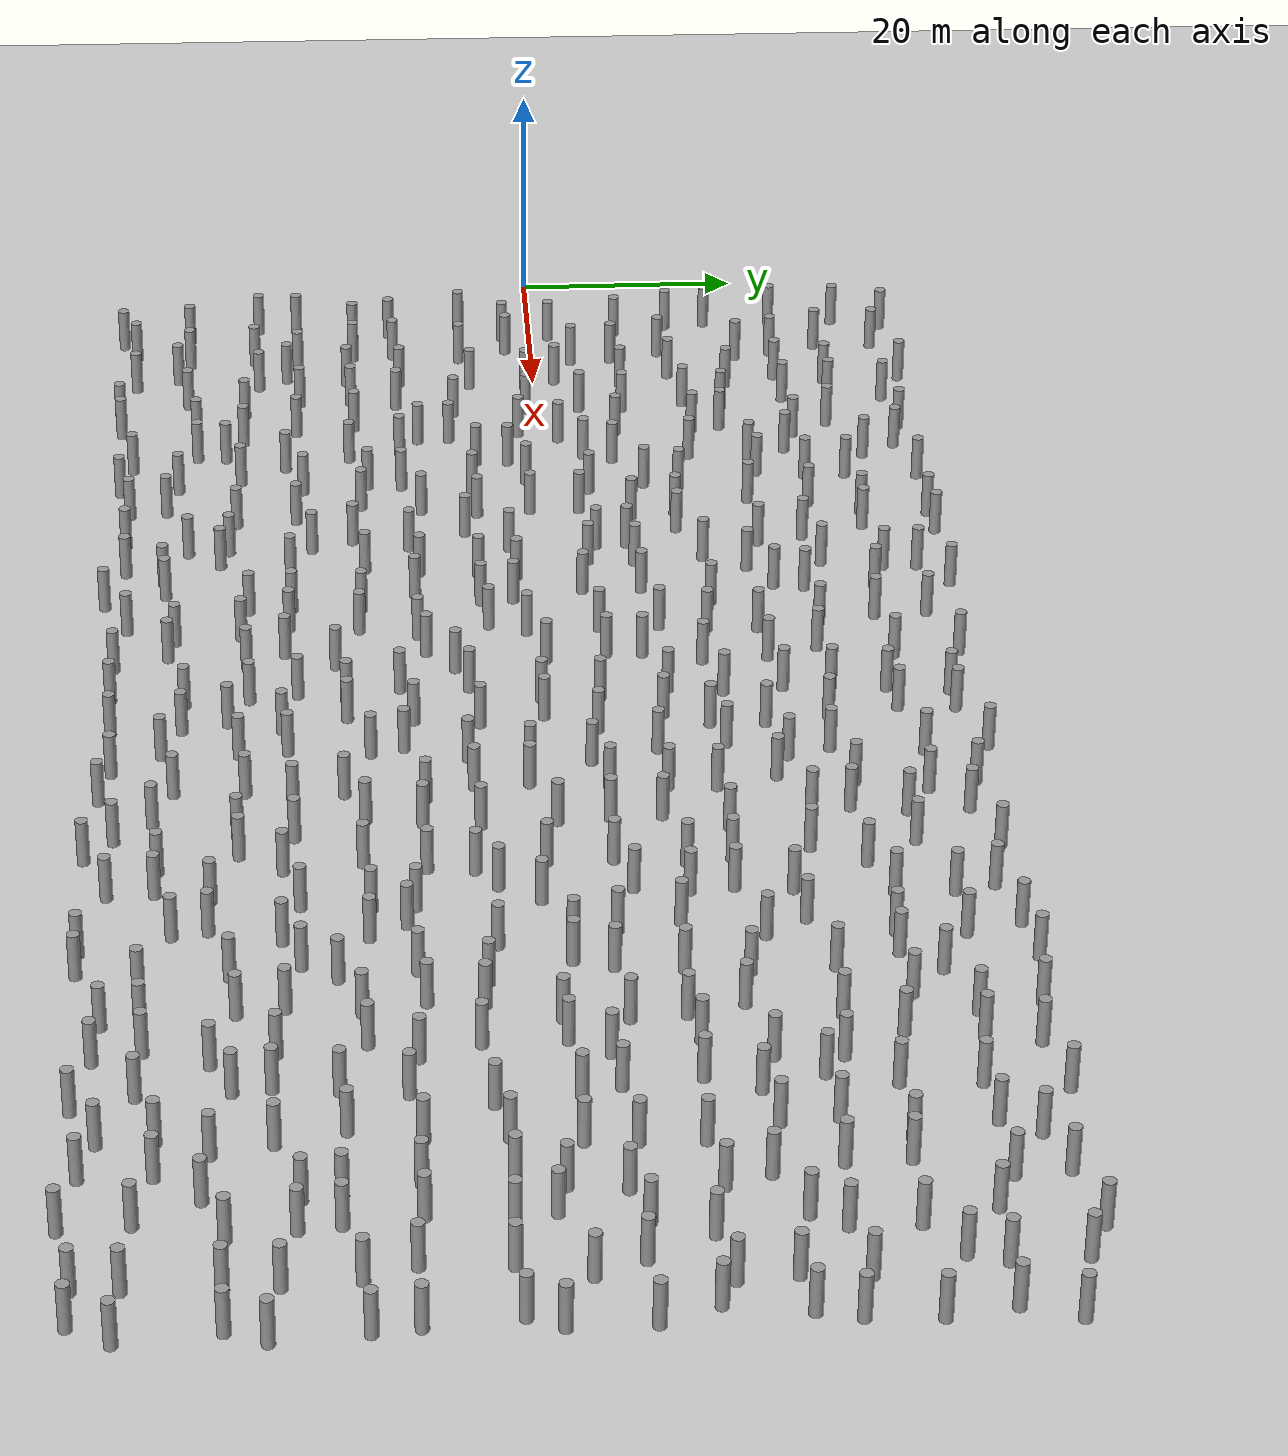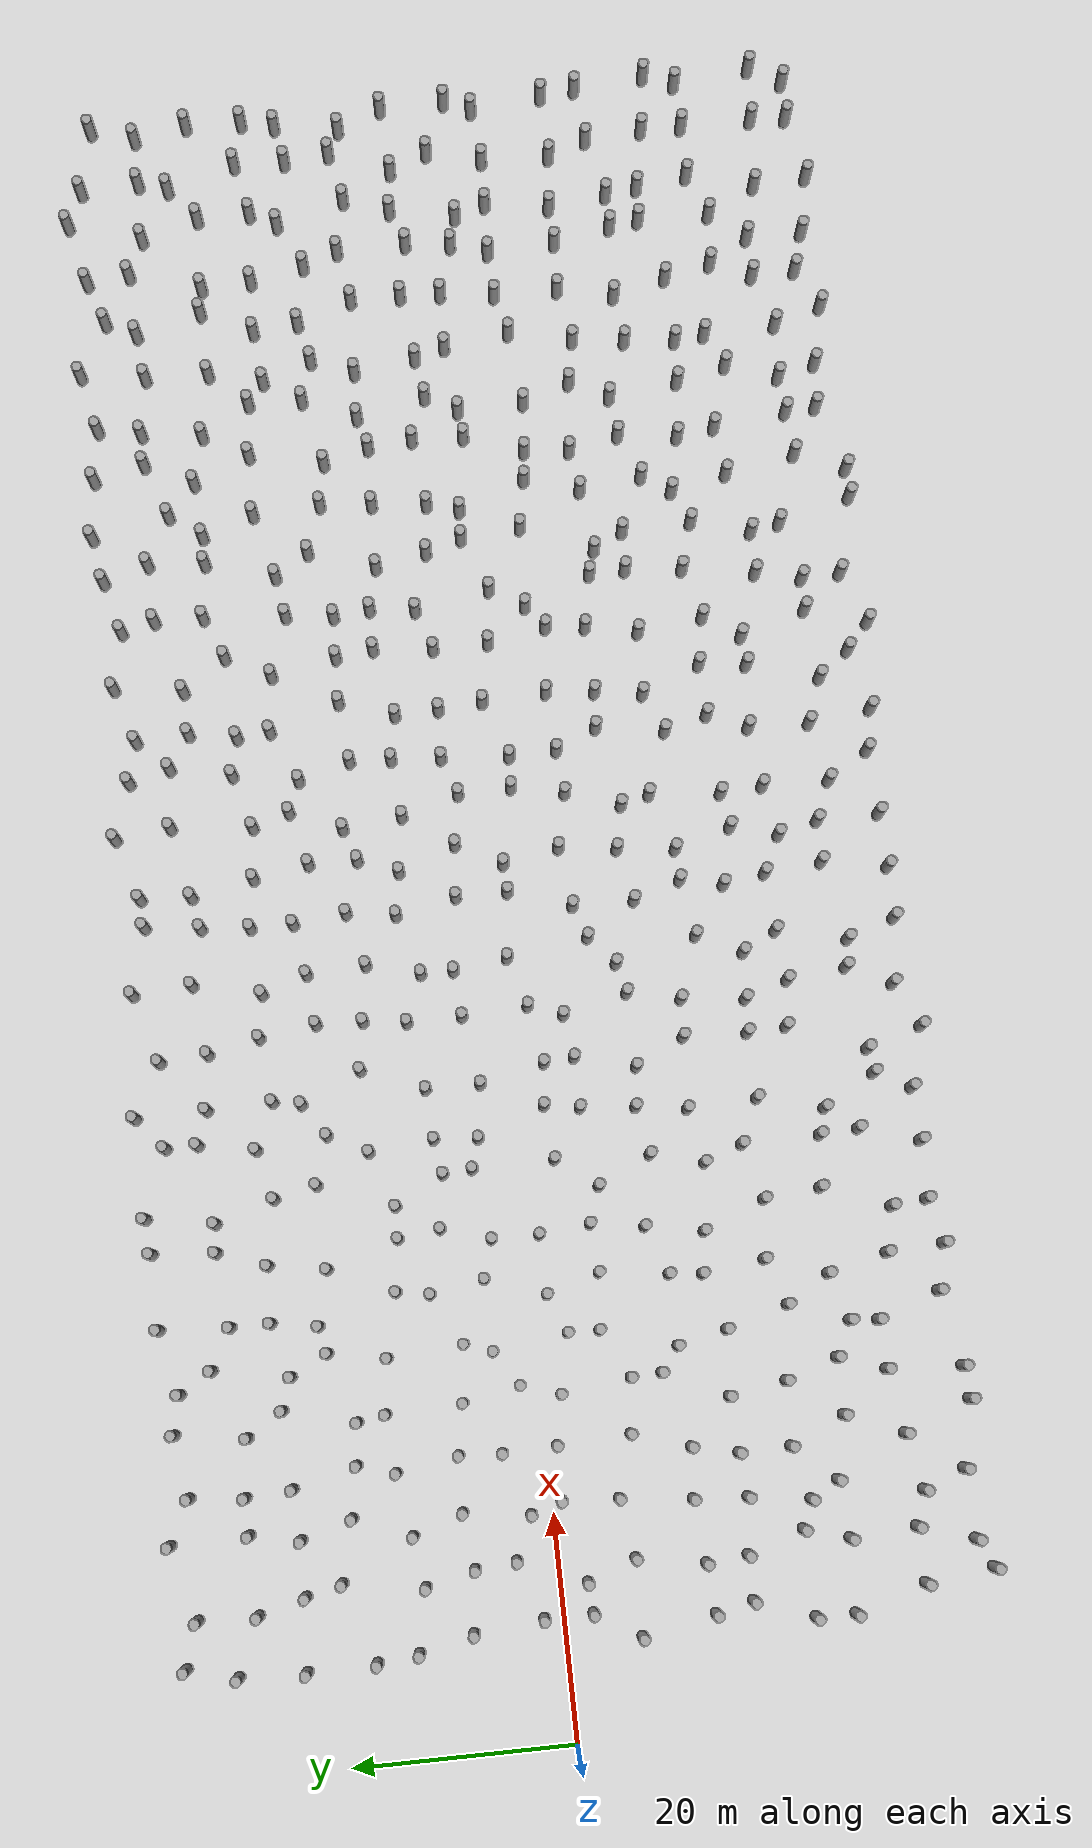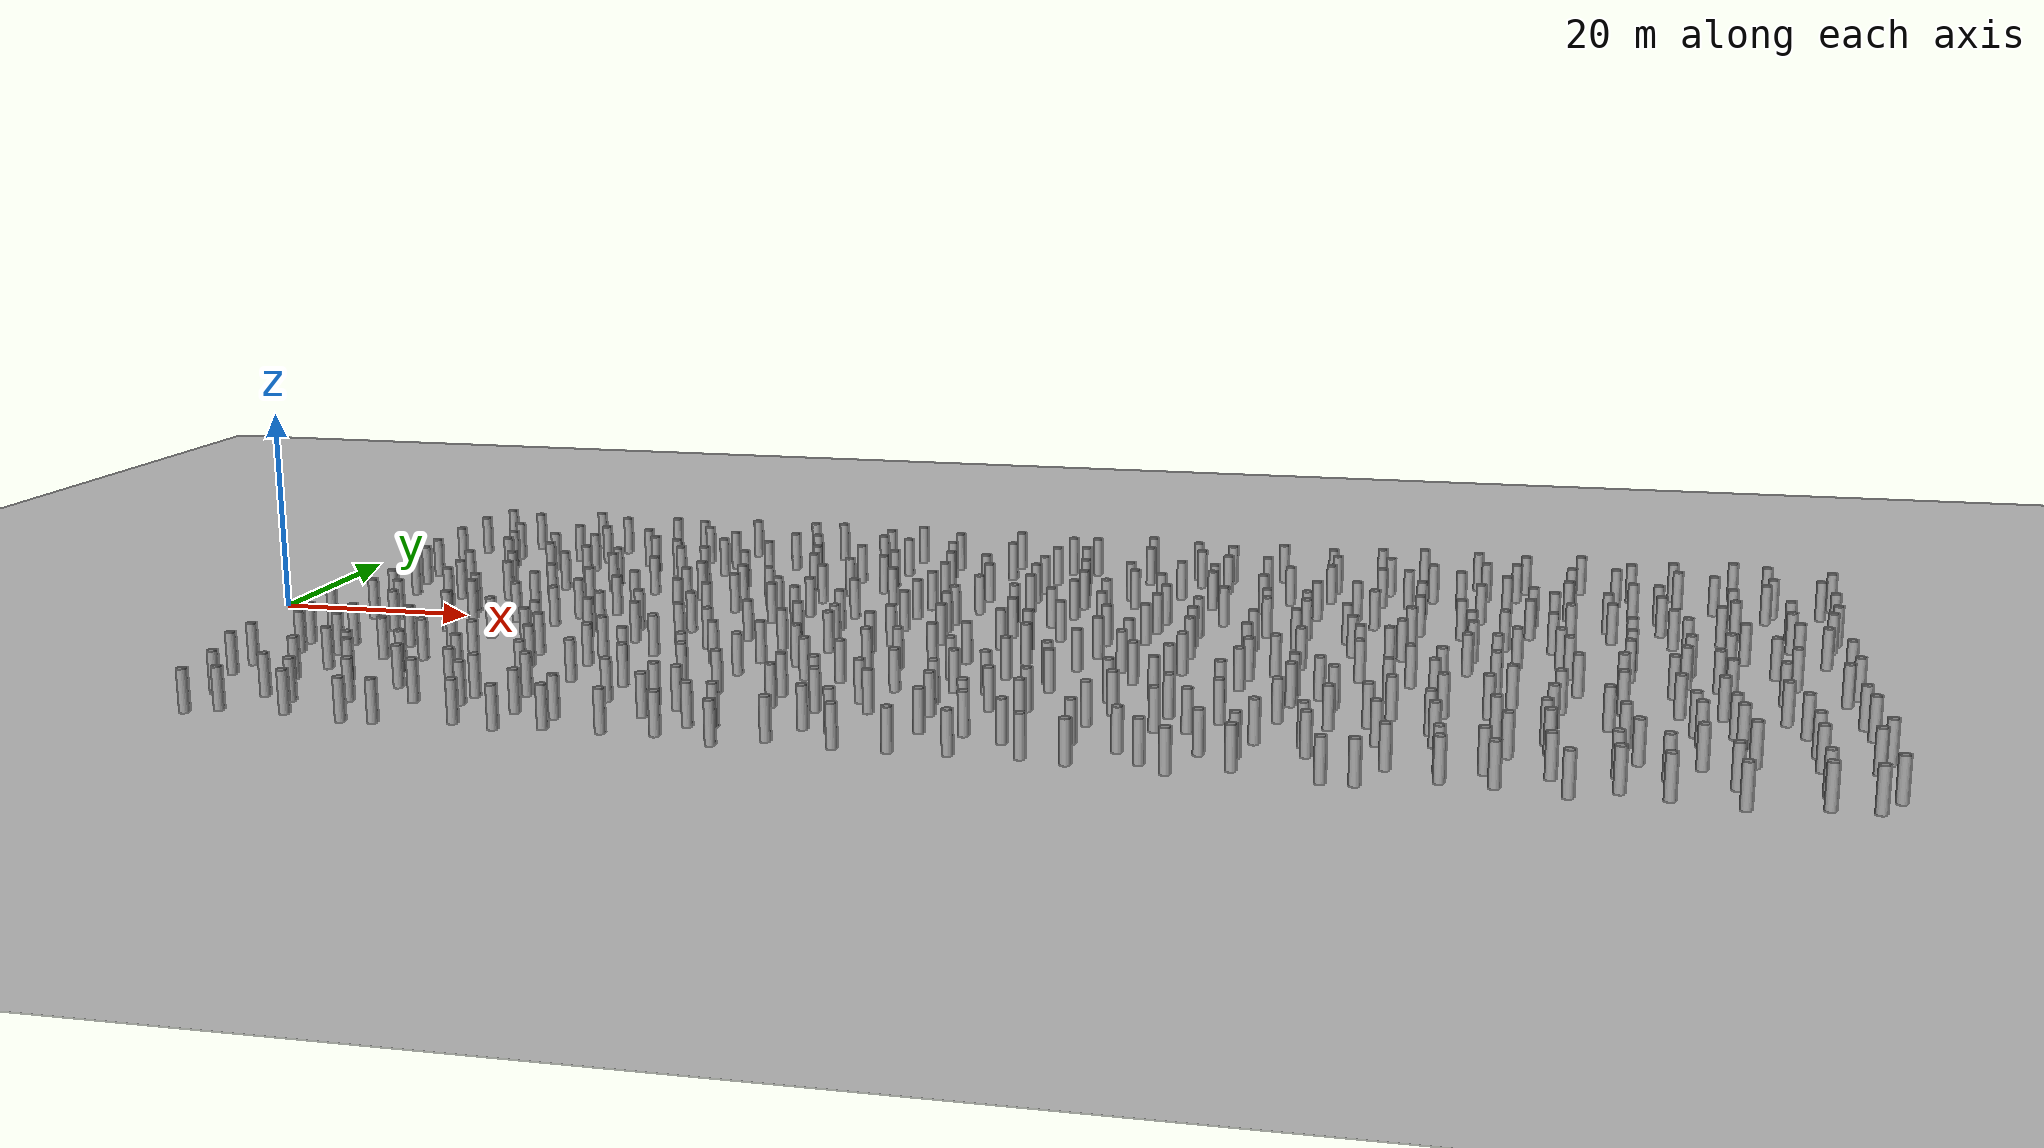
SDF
<sdf version="1.5">
 <world name="circle">
  <light name="sun" type="directional">
   <pose>0 0 100 0 -0 0</pose>
   <diffuse>0.8 0.8 0.8 1</diffuse>
   <specular>0.2 0.2 0.2 1</specular>
   <attenuation>
    <range>1000</range>
    <constant>0.9</constant>
    <linear>0.01</linear>
    <quadratic>0.001</quadratic>
   </attenuation>
   <direction>0.5 0.1 -0.9</direction>
  </light>
  <model name="ground">
   <static>1</static>
   <link name="link">
    <collision name="collision">
     <geometry><plane><normal>0 0 1</normal><size>100 100</size></plane></geometry>
     <surface><friction><ode><mu>100</mu><mu2>50</mu2></ode></friction></surface>
    </collision>
    <visual name="visual">
     <cast_shadows>0</cast_shadows>
     <geometry><plane><normal>0 0 1</normal><size>100 100</size></plane></geometry>
     <material>
      <script><uri>file://media/materials/scripts/gazebo.material</uri><name>Gazebo/Grey</name></script>
     </material>
    </visual>
    <velocity_decay><linear>0</linear><angular>0</angular></velocity_decay>
   </link>
  </model>
  <model name="unit_cylinder_0">
   <pose>11.4704873806 -38.4705015737 2 3e-06 4e-06 -0</pose>
   <static>1</static>
   <self_collide>1</self_collide>
   <link name="link">
    <inertial>
     <mass>1</mass>
     <inertia><ixx>0.145833</ixx><ixy>0</ixy><ixz>0</ixz><iyy>0.145833</iyy><iyz>0</iyz><izz>0.125</izz></inertia>
    </inertial>
    <collision name="collision">
     <geometry><cylinder><radius>0.5</radius><length>4</length></cylinder></geometry>
    </collision>
    <visual name="visual">
     <geometry><cylinder><radius>0.5</radius><length>4</length></cylinder></geometry>
     <material>
      <script><name>Gazebo/Grey</name><uri>file://media/materials/scripts/gazebo.material</uri></script>
     </material>
    </visual>
    <collision name="cyl_collision">
     <geometry><cylinder><radius>0.5</radius><length>4</length></cylinder></geometry>
    </collision>
    <sensor name="my_contact" type="contact">
     <contact><collision>cyl_collision</collision></contact>
     <update_rate>5</update_rate>
    </sensor>
   </link>
  </model>
  <model name="unit_cylinder_1">
   <pose>10.7220706982 -32.2368732227 2 3e-06 4e-06 -0</pose>
   <static>1</static>
   <self_collide>1</self_collide>
   <link name="link">
    <inertial>
     <mass>1</mass>
     <inertia><ixx>0.145833</ixx><ixy>0</ixy><ixz>0</ixz><iyy>0.145833</iyy><iyz>0</iyz><izz>0.125</izz></inertia>
    </inertial>
    <collision name="collision">
     <geometry><cylinder><radius>0.5</radius><length>4</length></cylinder></geometry>
    </collision>
    <visual name="visual">
     <geometry><cylinder><radius>0.5</radius><length>4</length></cylinder></geometry>
     <material>
      <script><name>Gazebo/Grey</name><uri>file://media/materials/scripts/gazebo.material</uri></script>
     </material>
    </visual>
    <collision name="cyl_collision">
     <geometry><cylinder><radius>0.5</radius><length>4</length></cylinder></geometry>
    </collision>
    <sensor name="my_contact" type="contact">
     <contact><collision>cyl_collision</collision></contact>
     <update_rate>5</update_rate>
    </sensor>
   </link>
  </model>
  <model name="unit_cylinder_2">
   <pose>8.72058208879 -25.7659753687 2 3e-06 4e-06 -0</pose>
   <static>1</static>
   <self_collide>1</self_collide>
   <link name="link">
    <inertial>
     <mass>1</mass>
     <inertia><ixx>0.145833</ixx><ixy>0</ixy><ixz>0</ixz><iyy>0.145833</iyy><iyz>0</iyz><izz>0.125</izz></inertia>
    </inertial>
    <collision name="collision">
     <geometry><cylinder><radius>0.5</radius><length>4</length></cylinder></geometry>
    </collision>
    <visual name="visual">
     <geometry><cylinder><radius>0.5</radius><length>4</length></cylinder></geometry>
     <material>
      <script><name>Gazebo/Grey</name><uri>file://media/materials/scripts/gazebo.material</uri></script>
     </material>
    </visual>
    <collision name="cyl_collision">
     <geometry><cylinder><radius>0.5</radius><length>4</length></cylinder></geometry>
    </collision>
    <sensor name="my_contact" type="contact">
     <contact><collision>cyl_collision</collision></contact>
     <update_rate>5</update_rate>
    </sensor>
   </link>
  </model>
  <model name="unit_cylinder_3">
   <pose>8.7979311131 -22.1893180289 2 3e-06 4e-06 -0</pose>
   <static>1</static>
   <self_collide>1</self_collide>
   <link name="link">
    <inertial>
     <mass>1</mass>
     <inertia><ixx>0.145833</ixx><ixy>0</ixy><ixz>0</ixz><iyy>0.145833</iyy><iyz>0</iyz><izz>0.125</izz></inertia>
    </inertial>
    <collision name="collision">
     <geometry><cylinder><radius>0.5</radius><length>4</length></cylinder></geometry>
    </collision>
    <visual name="visual">
     <geometry><cylinder><radius>0.5</radius><length>4</length></cylinder></geometry>
     <material>
      <script><name>Gazebo/Grey</name><uri>file://media/materials/scripts/gazebo.material</uri></script>
     </material>
    </visual>
    <collision name="cyl_collision">
     <geometry><cylinder><radius>0.5</radius><length>4</length></cylinder></geometry>
    </collision>
    <sensor name="my_contact" type="contact">
     <contact><collision>cyl_collision</collision></contact>
     <update_rate>5</update_rate>
    </sensor>
   </link>
  </model>
  <model name="unit_cylinder_4">
   <pose>10.7291669379 -16.8295722674 2 3e-06 4e-06 -0</pose>
   <static>1</static>
   <self_collide>1</self_collide>
   <link name="link">
    <inertial>
     <mass>1</mass>
     <inertia><ixx>0.145833</ixx><ixy>0</ixy><ixz>0</ixz><iyy>0.145833</iyy><iyz>0</iyz><izz>0.125</izz></inertia>
    </inertial>
    <collision name="collision">
     <geometry><cylinder><radius>0.5</radius><length>4</length></cylinder></geometry>
    </collision>
    <visual name="visual">
     <geometry><cylinder><radius>0.5</radius><length>4</length></cylinder></geometry>
     <material>
      <script><name>Gazebo/Grey</name><uri>file://media/materials/scripts/gazebo.material</uri></script>
     </material>
    </visual>
    <collision name="cyl_collision">
     <geometry><cylinder><radius>0.5</radius><length>4</length></cylinder></geometry>
    </collision>
    <sensor name="my_contact" type="contact">
     <contact><collision>cyl_collision</collision></contact>
     <update_rate>5</update_rate>
    </sensor>
   </link>
  </model>
  <model name="unit_cylinder_5">
   <pose>9.95934190549 -13.4133714786 2 3e-06 4e-06 -0</pose>
   <static>1</static>
   <self_collide>1</self_collide>
   <link name="link">
    <inertial>
     <mass>1</mass>
     <inertia><ixx>0.145833</ixx><ixy>0</ixy><ixz>0</ixz><iyy>0.145833</iyy><iyz>0</iyz><izz>0.125</izz></inertia>
    </inertial>
    <collision name="collision">
     <geometry><cylinder><radius>0.5</radius><length>4</length></cylinder></geometry>
    </collision>
    <visual name="visual">
     <geometry><cylinder><radius>0.5</radius><length>4</length></cylinder></geometry>
     <material>
      <script><name>Gazebo/Grey</name><uri>file://media/materials/scripts/gazebo.material</uri></script>
     </material>
    </visual>
    <collision name="cyl_collision">
     <geometry><cylinder><radius>0.5</radius><length>4</length></cylinder></geometry>
    </collision>
    <sensor name="my_contact" type="contact">
     <contact><collision>cyl_collision</collision></contact>
     <update_rate>5</update_rate>
    </sensor>
   </link>
  </model>
  <model name="unit_cylinder_6">
   <pose>8.65560884006 -6.71842204204 2 3e-06 4e-06 -0</pose>
   <static>1</static>
   <self_collide>1</self_collide>
   <link name="link">
    <inertial>
     <mass>1</mass>
     <inertia><ixx>0.145833</ixx><ixy>0</ixy><ixz>0</ixz><iyy>0.145833</iyy><iyz>0</iyz><izz>0.125</izz></inertia>
    </inertial>
    <collision name="collision">
     <geometry><cylinder><radius>0.5</radius><length>4</length></cylinder></geometry>
    </collision>
    <visual name="visual">
     <geometry><cylinder><radius>0.5</radius><length>4</length></cylinder></geometry>
     <material>
      <script><name>Gazebo/Grey</name><uri>file://media/materials/scripts/gazebo.material</uri></script>
     </material>
    </visual>
    <collision name="cyl_collision">
     <geometry><cylinder><radius>0.5</radius><length>4</length></cylinder></geometry>
    </collision>
    <sensor name="my_contact" type="contact">
     <contact><collision>cyl_collision</collision></contact>
     <update_rate>5</update_rate>
    </sensor>
   </link>
  </model>
  <model name="unit_cylinder_7">
   <pose>11.0925974259 -2.59262243464 2 3e-06 4e-06 -0</pose>
   <static>1</static>
   <self_collide>1</self_collide>
   <link name="link">
    <inertial>
     <mass>1</mass>
     <inertia><ixx>0.145833</ixx><ixy>0</ixy><ixz>0</ixz><iyy>0.145833</iyy><iyz>0</iyz><izz>0.125</izz></inertia>
    </inertial>
    <collision name="collision">
     <geometry><cylinder><radius>0.5</radius><length>4</length></cylinder></geometry>
    </collision>
    <visual name="visual">
     <geometry><cylinder><radius>0.5</radius><length>4</length></cylinder></geometry>
     <material>
      <script><name>Gazebo/Grey</name><uri>file://media/materials/scripts/gazebo.material</uri></script>
     </material>
    </visual>
    <collision name="cyl_collision">
     <geometry><cylinder><radius>0.5</radius><length>4</length></cylinder></geometry>
    </collision>
    <sensor name="my_contact" type="contact">
     <contact><collision>cyl_collision</collision></contact>
     <update_rate>5</update_rate>
    </sensor>
   </link>
  </model>
  <model name="unit_cylinder_8">
   <pose>11.0563673491 1.79596865884 2 3e-06 4e-06 -0</pose>
   <static>1</static>
   <self_collide>1</self_collide>
   <link name="link">
    <inertial>
     <mass>1</mass>
     <inertia><ixx>0.145833</ixx><ixy>0</ixy><ixz>0</ixz><iyy>0.145833</iyy><iyz>0</iyz><izz>0.125</izz></inertia>
    </inertial>
    <collision name="collision">
     <geometry><cylinder><radius>0.5</radius><length>4</length></cylinder></geometry>
    </collision>
    <visual name="visual">
     <geometry><cylinder><radius>0.5</radius><length>4</length></cylinder></geometry>
     <material>
      <script><name>Gazebo/Grey</name><uri>file://media/materials/scripts/gazebo.material</uri></script>
     </material>
    </visual>
    <collision name="cyl_collision">
     <geometry><cylinder><radius>0.5</radius><length>4</length></cylinder></geometry>
    </collision>
    <sensor name="my_contact" type="contact">
     <contact><collision>cyl_collision</collision></contact>
     <update_rate>5</update_rate>
    </sensor>
   </link>
  </model>
  <model name="unit_cylinder_9">
   <pose>10.4059899599 8.12202831886 2 3e-06 4e-06 -0</pose>
   <static>1</static>
   <self_collide>1</self_collide>
   <link name="link">
    <inertial>
     <mass>1</mass>
     <inertia><ixx>0.145833</ixx><ixy>0</ixy><ixz>0</ixz><iyy>0.145833</iyy><iyz>0</iyz><izz>0.125</izz></inertia>
    </inertial>
    <collision name="collision">
     <geometry><cylinder><radius>0.5</radius><length>4</length></cylinder></geometry>
    </collision>
    <visual name="visual">
     <geometry><cylinder><radius>0.5</radius><length>4</length></cylinder></geometry>
     <material>
      <script><name>Gazebo/Grey</name><uri>file://media/materials/scripts/gazebo.material</uri></script>
     </material>
    </visual>
    <collision name="cyl_collision">
     <geometry><cylinder><radius>0.5</radius><length>4</length></cylinder></geometry>
    </collision>
    <sensor name="my_contact" type="contact">
     <contact><collision>cyl_collision</collision></contact>
     <update_rate>5</update_rate>
    </sensor>
   </link>
  </model>
  <model name="unit_cylinder_10">
   <pose>9.20407594885 13.0749428126 2 3e-06 4e-06 -0</pose>
   <static>1</static>
   <self_collide>1</self_collide>
   <link name="link">
    <inertial>
     <mass>1</mass>
     <inertia><ixx>0.145833</ixx><ixy>0</ixy><ixz>0</ixz><iyy>0.145833</iyy><iyz>0</iyz><izz>0.125</izz></inertia>
    </inertial>
    <collision name="collision">
     <geometry><cylinder><radius>0.5</radius><length>4</length></cylinder></geometry>
    </collision>
    <visual name="visual">
     <geometry><cylinder><radius>0.5</radius><length>4</length></cylinder></geometry>
     <material>
      <script><name>Gazebo/Grey</name><uri>file://media/materials/scripts/gazebo.material</uri></script>
     </material>
    </visual>
    <collision name="cyl_collision">
     <geometry><cylinder><radius>0.5</radius><length>4</length></cylinder></geometry>
    </collision>
    <sensor name="my_contact" type="contact">
     <contact><collision>cyl_collision</collision></contact>
     <update_rate>5</update_rate>
    </sensor>
   </link>
  </model>
  <model name="unit_cylinder_11">
   <pose>8.75446936457 16.8259148366 2 3e-06 4e-06 -0</pose>
   <static>1</static>
   <self_collide>1</self_collide>
   <link name="link">
    <inertial>
     <mass>1</mass>
     <inertia><ixx>0.145833</ixx><ixy>0</ixy><ixz>0</ixz><iyy>0.145833</iyy><iyz>0</iyz><izz>0.125</izz></inertia>
    </inertial>
    <collision name="collision">
     <geometry><cylinder><radius>0.5</radius><length>4</length></cylinder></geometry>
    </collision>
    <visual name="visual">
     <geometry><cylinder><radius>0.5</radius><length>4</length></cylinder></geometry>
     <material>
      <script><name>Gazebo/Grey</name><uri>file://media/materials/scripts/gazebo.material</uri></script>
     </material>
    </visual>
    <collision name="cyl_collision">
     <geometry><cylinder><radius>0.5</radius><length>4</length></cylinder></geometry>
    </collision>
    <sensor name="my_contact" type="contact">
     <contact><collision>cyl_collision</collision></contact>
     <update_rate>5</update_rate>
    </sensor>
   </link>
  </model>
  <model name="unit_cylinder_12">
   <pose>8.59839209359 23.0891876215 2 3e-06 4e-06 -0</pose>
   <static>1</static>
   <self_collide>1</self_collide>
   <link name="link">
    <inertial>
     <mass>1</mass>
     <inertia><ixx>0.145833</ixx><ixy>0</ixy><ixz>0</ixz><iyy>0.145833</iyy><iyz>0</iyz><izz>0.125</izz></inertia>
    </inertial>
    <collision name="collision">
     <geometry><cylinder><radius>0.5</radius><length>4</length></cylinder></geometry>
    </collision>
    <visual name="visual">
     <geometry><cylinder><radius>0.5</radius><length>4</length></cylinder></geometry>
     <material>
      <script><name>Gazebo/Grey</name><uri>file://media/materials/scripts/gazebo.material</uri></script>
     </material>
    </visual>
    <collision name="cyl_collision">
     <geometry><cylinder><radius>0.5</radius><length>4</length></cylinder></geometry>
    </collision>
    <sensor name="my_contact" type="contact">
     <contact><collision>cyl_collision</collision></contact>
     <update_rate>5</update_rate>
    </sensor>
   </link>
  </model>
  <model name="unit_cylinder_13">
   <pose>8.77301460406 29.1386734522 2 3e-06 4e-06 -0</pose>
   <static>1</static>
   <self_collide>1</self_collide>
   <link name="link">
    <inertial>
     <mass>1</mass>
     <inertia><ixx>0.145833</ixx><ixy>0</ixy><ixz>0</ixz><iyy>0.145833</iyy><iyz>0</iyz><izz>0.125</izz></inertia>
    </inertial>
    <collision name="collision">
     <geometry><cylinder><radius>0.5</radius><length>4</length></cylinder></geometry>
    </collision>
    <visual name="visual">
     <geometry><cylinder><radius>0.5</radius><length>4</length></cylinder></geometry>
     <material>
      <script><name>Gazebo/Grey</name><uri>file://media/materials/scripts/gazebo.material</uri></script>
     </material>
    </visual>
    <collision name="cyl_collision">
     <geometry><cylinder><radius>0.5</radius><length>4</length></cylinder></geometry>
    </collision>
    <sensor name="my_contact" type="contact">
     <contact><collision>cyl_collision</collision></contact>
     <update_rate>5</update_rate>
    </sensor>
   </link>
  </model>
  <model name="unit_cylinder_14">
   <pose>9.91188079629 33.702368652 2 3e-06 4e-06 -0</pose>
   <static>1</static>
   <self_collide>1</self_collide>
   <link name="link">
    <inertial>
     <mass>1</mass>
     <inertia><ixx>0.145833</ixx><ixy>0</ixy><ixz>0</ixz><iyy>0.145833</iyy><iyz>0</iyz><izz>0.125</izz></inertia>
    </inertial>
    <collision name="collision">
     <geometry><cylinder><radius>0.5</radius><length>4</length></cylinder></geometry>
    </collision>
    <visual name="visual">
     <geometry><cylinder><radius>0.5</radius><length>4</length></cylinder></geometry>
     <material>
      <script><name>Gazebo/Grey</name><uri>file://media/materials/scripts/gazebo.material</uri></script>
     </material>
    </visual>
    <collision name="cyl_collision">
     <geometry><cylinder><radius>0.5</radius><length>4</length></cylinder></geometry>
    </collision>
    <sensor name="my_contact" type="contact">
     <contact><collision>cyl_collision</collision></contact>
     <update_rate>5</update_rate>
    </sensor>
   </link>
  </model>
  <model name="unit_cylinder_15">
   <pose>14.0691763741 -37.1683287253 2 3e-06 4e-06 -0</pose>
   <static>1</static>
   <self_collide>1</self_collide>
   <link name="link">
    <inertial>
     <mass>1</mass>
     <inertia><ixx>0.145833</ixx><ixy>0</ixy><ixz>0</ixz><iyy>0.145833</iyy><iyz>0</iyz><izz>0.125</izz></inertia>
    </inertial>
    <collision name="collision">
     <geometry><cylinder><radius>0.5</radius><length>4</length></cylinder></geometry>
    </collision>
    <visual name="visual">
     <geometry><cylinder><radius>0.5</radius><length>4</length></cylinder></geometry>
     <material>
      <script><name>Gazebo/Grey</name><uri>file://media/materials/scripts/gazebo.material</uri></script>
     </material>
    </visual>
    <collision name="cyl_collision">
     <geometry><cylinder><radius>0.5</radius><length>4</length></cylinder></geometry>
    </collision>
    <sensor name="my_contact" type="contact">
     <contact><collision>cyl_collision</collision></contact>
     <update_rate>5</update_rate>
    </sensor>
   </link>
  </model>
  <model name="unit_cylinder_16">
   <pose>15.6718557421 -32.0796657784 2 3e-06 4e-06 -0</pose>
   <static>1</static>
   <self_collide>1</self_collide>
   <link name="link">
    <inertial>
     <mass>1</mass>
     <inertia><ixx>0.145833</ixx><ixy>0</ixy><ixz>0</ixz><iyy>0.145833</iyy><iyz>0</iyz><izz>0.125</izz></inertia>
    </inertial>
    <collision name="collision">
     <geometry><cylinder><radius>0.5</radius><length>4</length></cylinder></geometry>
    </collision>
    <visual name="visual">
     <geometry><cylinder><radius>0.5</radius><length>4</length></cylinder></geometry>
     <material>
      <script><name>Gazebo/Grey</name><uri>file://media/materials/scripts/gazebo.material</uri></script>
     </material>
    </visual>
    <collision name="cyl_collision">
     <geometry><cylinder><radius>0.5</radius><length>4</length></cylinder></geometry>
    </collision>
    <sensor name="my_contact" type="contact">
     <contact><collision>cyl_collision</collision></contact>
     <update_rate>5</update_rate>
    </sensor>
   </link>
  </model>
  <model name="unit_cylinder_17">
   <pose>15.2381734508 -26.0447782265 2 3e-06 4e-06 -0</pose>
   <static>1</static>
   <self_collide>1</self_collide>
   <link name="link">
    <inertial>
     <mass>1</mass>
     <inertia><ixx>0.145833</ixx><ixy>0</ixy><ixz>0</ixz><iyy>0.145833</iyy><iyz>0</iyz><izz>0.125</izz></inertia>
    </inertial>
    <collision name="collision">
     <geometry><cylinder><radius>0.5</radius><length>4</length></cylinder></geometry>
    </collision>
    <visual name="visual">
     <geometry><cylinder><radius>0.5</radius><length>4</length></cylinder></geometry>
     <material>
      <script><name>Gazebo/Grey</name><uri>file://media/materials/scripts/gazebo.material</uri></script>
     </material>
    </visual>
    <collision name="cyl_collision">
     <geometry><cylinder><radius>0.5</radius><length>4</length></cylinder></geometry>
    </collision>
    <sensor name="my_contact" type="contact">
     <contact><collision>cyl_collision</collision></contact>
     <update_rate>5</update_rate>
    </sensor>
   </link>
  </model>
  <model name="unit_cylinder_18">
   <pose>16.4323542205 -21.9812832431 2 3e-06 4e-06 -0</pose>
   <static>1</static>
   <self_collide>1</self_collide>
   <link name="link">
    <inertial>
     <mass>1</mass>
     <inertia><ixx>0.145833</ixx><ixy>0</ixy><ixz>0</ixz><iyy>0.145833</iyy><iyz>0</iyz><izz>0.125</izz></inertia>
    </inertial>
    <collision name="collision">
     <geometry><cylinder><radius>0.5</radius><length>4</length></cylinder></geometry>
    </collision>
    <visual name="visual">
     <geometry><cylinder><radius>0.5</radius><length>4</length></cylinder></geometry>
     <material>
      <script><name>Gazebo/Grey</name><uri>file://media/materials/scripts/gazebo.material</uri></script>
     </material>
    </visual>
    <collision name="cyl_collision">
     <geometry><cylinder><radius>0.5</radius><length>4</length></cylinder></geometry>
    </collision>
    <sensor name="my_contact" type="contact">
     <contact><collision>cyl_collision</collision></contact>
     <update_rate>5</update_rate>
    </sensor>
   </link>
  </model>
  <model name="unit_cylinder_19">
   <pose>14.7287866924 -16.8152338444 2 3e-06 4e-06 -0</pose>
   <static>1</static>
   <self_collide>1</self_collide>
   <link name="link">
    <inertial>
     <mass>1</mass>
     <inertia><ixx>0.145833</ixx><ixy>0</ixy><ixz>0</ixz><iyy>0.145833</iyy><iyz>0</iyz><izz>0.125</izz></inertia>
    </inertial>
    <collision name="collision">
     <geometry><cylinder><radius>0.5</radius><length>4</length></cylinder></geometry>
    </collision>
    <visual name="visual">
     <geometry><cylinder><radius>0.5</radius><length>4</length></cylinder></geometry>
     <material>
      <script><name>Gazebo/Grey</name><uri>file://media/materials/scripts/gazebo.material</uri></script>
     </material>
    </visual>
    <collision name="cyl_collision">
     <geometry><cylinder><radius>0.5</radius><length>4</length></cylinder></geometry>
    </collision>
    <sensor name="my_contact" type="contact">
     <contact><collision>cyl_collision</collision></contact>
     <update_rate>5</update_rate>
    </sensor>
   </link>
  </model>
  <model name="unit_cylinder_20">
   <pose>14.3871150903 -13.0582520196 2 3e-06 4e-06 -0</pose>
   <static>1</static>
   <self_collide>1</self_collide>
   <link name="link">
    <inertial>
     <mass>1</mass>
     <inertia><ixx>0.145833</ixx><ixy>0</ixy><ixz>0</ixz><iyy>0.145833</iyy><iyz>0</iyz><izz>0.125</izz></inertia>
    </inertial>
    <collision name="collision">
     <geometry><cylinder><radius>0.5</radius><length>4</length></cylinder></geometry>
    </collision>
    <visual name="visual">
     <geometry><cylinder><radius>0.5</radius><length>4</length></cylinder></geometry>
     <material>
      <script><name>Gazebo/Grey</name><uri>file://media/materials/scripts/gazebo.material</uri></script>
     </material>
    </visual>
    <collision name="cyl_collision">
     <geometry><cylinder><radius>0.5</radius><length>4</length></cylinder></geometry>
    </collision>
    <sensor name="my_contact" type="contact">
     <contact><collision>cyl_collision</collision></contact>
     <update_rate>5</update_rate>
    </sensor>
   </link>
  </model>
  <model name="unit_cylinder_21">
   <pose>15.4473837249 -6.83084311532 2 3e-06 4e-06 -0</pose>
   <static>1</static>
   <self_collide>1</self_collide>
   <link name="link">
    <inertial>
     <mass>1</mass>
     <inertia><ixx>0.145833</ixx><ixy>0</ixy><ixz>0</ixz><iyy>0.145833</iyy><iyz>0</iyz><izz>0.125</izz></inertia>
    </inertial>
    <collision name="collision">
     <geometry><cylinder><radius>0.5</radius><length>4</length></cylinder></geometry>
    </collision>
    <visual name="visual">
     <geometry><cylinder><radius>0.5</radius><length>4</length></cylinder></geometry>
     <material>
      <script><name>Gazebo/Grey</name><uri>file://media/materials/scripts/gazebo.material</uri></script>
     </material>
    </visual>
    <collision name="cyl_collision">
     <geometry><cylinder><radius>0.5</radius><length>4</length></cylinder></geometry>
    </collision>
    <sensor name="my_contact" type="contact">
     <contact><collision>cyl_collision</collision></contact>
     <update_rate>5</update_rate>
    </sensor>
   </link>
  </model>
  <model name="unit_cylinder_22">
   <pose>13.7809937066 -2.39120445731 2 3e-06 4e-06 -0</pose>
   <static>1</static>
   <self_collide>1</self_collide>
   <link name="link">
    <inertial>
     <mass>1</mass>
     <inertia><ixx>0.145833</ixx><ixy>0</ixy><ixz>0</ixz><iyy>0.145833</iyy><iyz>0</iyz><izz>0.125</izz></inertia>
    </inertial>
    <collision name="collision">
     <geometry><cylinder><radius>0.5</radius><length>4</length></cylinder></geometry>
    </collision>
    <visual name="visual">
     <geometry><cylinder><radius>0.5</radius><length>4</length></cylinder></geometry>
     <material>
      <script><name>Gazebo/Grey</name><uri>file://media/materials/scripts/gazebo.material</uri></script>
     </material>
    </visual>
    <collision name="cyl_collision">
     <geometry><cylinder><radius>0.5</radius><length>4</length></cylinder></geometry>
    </collision>
    <sensor name="my_contact" type="contact">
     <contact><collision>cyl_collision</collision></contact>
     <update_rate>5</update_rate>
    </sensor>
   </link>
  </model>
  <model name="unit_cylinder_23">
   <pose>16.2458317515 3.72797373236 2 3e-06 4e-06 -0</pose>
   <static>1</static>
   <self_collide>1</self_collide>
   <link name="link">
    <inertial>
     <mass>1</mass>
     <inertia><ixx>0.145833</ixx><ixy>0</ixy><ixz>0</ixz><iyy>0.145833</iyy><iyz>0</iyz><izz>0.125</izz></inertia>
    </inertial>
    <collision name="collision">
     <geometry><cylinder><radius>0.5</radius><length>4</length></cylinder></geometry>
    </collision>
    <visual name="visual">
     <geometry><cylinder><radius>0.5</radius><length>4</length></cylinder></geometry>
     <material>
      <script><name>Gazebo/Grey</name><uri>file://media/materials/scripts/gazebo.material</uri></script>
     </material>
    </visual>
    <collision name="cyl_collision">
     <geometry><cylinder><radius>0.5</radius><length>4</length></cylinder></geometry>
    </collision>
    <sensor name="my_contact" type="contact">
     <contact><collision>cyl_collision</collision></contact>
     <update_rate>5</update_rate>
    </sensor>
   </link>
  </model>
  <model name="unit_cylinder_24">
   <pose>15.9001981405 7.47352681353 2 3e-06 4e-06 -0</pose>
   <static>1</static>
   <self_collide>1</self_collide>
   <link name="link">
    <inertial>
     <mass>1</mass>
     <inertia><ixx>0.145833</ixx><ixy>0</ixy><ixz>0</ixz><iyy>0.145833</iyy><iyz>0</iyz><izz>0.125</izz></inertia>
    </inertial>
    <collision name="collision">
     <geometry><cylinder><radius>0.5</radius><length>4</length></cylinder></geometry>
    </collision>
    <visual name="visual">
     <geometry><cylinder><radius>0.5</radius><length>4</length></cylinder></geometry>
     <material>
      <script><name>Gazebo/Grey</name><uri>file://media/materials/scripts/gazebo.material</uri></script>
     </material>
    </visual>
    <collision name="cyl_collision">
     <geometry><cylinder><radius>0.5</radius><length>4</length></cylinder></geometry>
    </collision>
    <sensor name="my_contact" type="contact">
     <contact><collision>cyl_collision</collision></contact>
     <update_rate>5</update_rate>
    </sensor>
   </link>
  </model>
  <model name="unit_cylinder_25">
   <pose>14.7860581348 11.9799662513 2 3e-06 4e-06 -0</pose>
   <static>1</static>
   <self_collide>1</self_collide>
   <link name="link">
    <inertial>
     <mass>1</mass>
     <inertia><ixx>0.145833</ixx><ixy>0</ixy><ixz>0</ixz><iyy>0.145833</iyy><iyz>0</iyz><izz>0.125</izz></inertia>
    </inertial>
    <collision name="collision">
     <geometry><cylinder><radius>0.5</radius><length>4</length></cylinder></geometry>
    </collision>
    <visual name="visual">
     <geometry><cylinder><radius>0.5</radius><length>4</length></cylinder></geometry>
     <material>
      <script><name>Gazebo/Grey</name><uri>file://media/materials/scripts/gazebo.material</uri></script>
     </material>
    </visual>
    <collision name="cyl_collision">
     <geometry><cylinder><radius>0.5</radius><length>4</length></cylinder></geometry>
    </collision>
    <sensor name="my_contact" type="contact">
     <contact><collision>cyl_collision</collision></contact>
     <update_rate>5</update_rate>
    </sensor>
   </link>
  </model>
  <model name="unit_cylinder_26">
   <pose>15.863351309 19.3138317568 2 3e-06 4e-06 -0</pose>
   <static>1</static>
   <self_collide>1</self_collide>
   <link name="link">
    <inertial>
     <mass>1</mass>
     <inertia><ixx>0.145833</ixx><ixy>0</ixy><ixz>0</ixz><iyy>0.145833</iyy><iyz>0</iyz><izz>0.125</izz></inertia>
    </inertial>
    <collision name="collision">
     <geometry><cylinder><radius>0.5</radius><length>4</length></cylinder></geometry>
    </collision>
    <visual name="visual">
     <geometry><cylinder><radius>0.5</radius><length>4</length></cylinder></geometry>
     <material>
      <script><name>Gazebo/Grey</name><uri>file://media/materials/scripts/gazebo.material</uri></script>
     </material>
    </visual>
    <collision name="cyl_collision">
     <geometry><cylinder><radius>0.5</radius><length>4</length></cylinder></geometry>
    </collision>
    <sensor name="my_contact" type="contact">
     <contact><collision>cyl_collision</collision></contact>
     <update_rate>5</update_rate>
    </sensor>
   </link>
  </model>
  <model name="unit_cylinder_27">
   <pose>15.0321887663 22.6323488595 2 3e-06 4e-06 -0</pose>
   <static>1</static>
   <self_collide>1</self_collide>
   <link name="link">
    <inertial>
     <mass>1</mass>
     <inertia><ixx>0.145833</ixx><ixy>0</ixy><ixz>0</ixz><iyy>0.145833</iyy><iyz>0</iyz><izz>0.125</izz></inertia>
    </inertial>
    <collision name="collision">
     <geometry><cylinder><radius>0.5</radius><length>4</length></cylinder></geometry>
    </collision>
    <visual name="visual">
     <geometry><cylinder><radius>0.5</radius><length>4</length></cylinder></geometry>
     <material>
      <script><name>Gazebo/Grey</name><uri>file://media/materials/scripts/gazebo.material</uri></script>
     </material>
    </visual>
    <collision name="cyl_collision">
     <geometry><cylinder><radius>0.5</radius><length>4</length></cylinder></geometry>
    </collision>
    <sensor name="my_contact" type="contact">
     <contact><collision>cyl_collision</collision></contact>
     <update_rate>5</update_rate>
    </sensor>
   </link>
  </model>
  <model name="unit_cylinder_28">
   <pose>13.8386892422 26.9644168073 2 3e-06 4e-06 -0</pose>
   <static>1</static>
   <self_collide>1</self_collide>
   <link name="link">
    <inertial>
     <mass>1</mass>
     <inertia><ixx>0.145833</ixx><ixy>0</ixy><ixz>0</ixz><iyy>0.145833</iyy><iyz>0</iyz><izz>0.125</izz></inertia>
    </inertial>
    <collision name="collision">
     <geometry><cylinder><radius>0.5</radius><length>4</length></cylinder></geometry>
    </collision>
    <visual name="visual">
     <geometry><cylinder><radius>0.5</radius><length>4</length></cylinder></geometry>
     <material>
      <script><name>Gazebo/Grey</name><uri>file://media/materials/scripts/gazebo.material</uri></script>
     </material>
    </visual>
    <collision name="cyl_collision">
     <geometry><cylinder><radius>0.5</radius><length>4</length></cylinder></geometry>
    </collision>
    <sensor name="my_contact" type="contact">
     <contact><collision>cyl_collision</collision></contact>
     <update_rate>5</update_rate>
    </sensor>
   </link>
  </model>
  <model name="unit_cylinder_29">
   <pose>13.9463333479 32.3646051353 2 3e-06 4e-06 -0</pose>
   <static>1</static>
   <self_collide>1</self_collide>
   <link name="link">
    <inertial>
     <mass>1</mass>
     <inertia><ixx>0.145833</ixx><ixy>0</ixy><ixz>0</ixz><iyy>0.145833</iyy><iyz>0</iyz><izz>0.125</izz></inertia>
    </inertial>
    <collision name="collision">
     <geometry><cylinder><radius>0.5</radius><length>4</length></cylinder></geometry>
    </collision>
    <visual name="visual">
     <geometry><cylinder><radius>0.5</radius><length>4</length></cylinder></geometry>
     <material>
      <script><name>Gazebo/Grey</name><uri>file://media/materials/scripts/gazebo.material</uri></script>
     </material>
    </visual>
    <collision name="cyl_collision">
     <geometry><cylinder><radius>0.5</radius><length>4</length></cylinder></geometry>
    </collision>
    <sensor name="my_contact" type="contact">
     <contact><collision>cyl_collision</collision></contact>
     <update_rate>5</update_rate>
    </sensor>
   </link>
  </model>
  <model name="unit_cylinder_30">
   <pose>20.2625665168 -36.9477858693 2 3e-06 4e-06 -0</pose>
   <static>1</static>
   <self_collide>1</self_collide>
   <link name="link">
    <inertial>
     <mass>1</mass>
     <inertia><ixx>0.145833</ixx><ixy>0</ixy><ixz>0</ixz><iyy>0.145833</iyy><iyz>0</iyz><izz>0.125</izz></inertia>
    </inertial>
    <collision name="collision">
     <geometry><cylinder><radius>0.5</radius><length>4</length></cylinder></geometry>
    </collision>
    <visual name="visual">
     <geometry><cylinder><radius>0.5</radius><length>4</length></cylinder></geometry>
     <material>
      <script><name>Gazebo/Grey</name><uri>file://media/materials/scripts/gazebo.material</uri></script>
     </material>
    </visual>
    <collision name="cyl_collision">
     <geometry><cylinder><radius>0.5</radius><length>4</length></cylinder></geometry>
    </collision>
    <sensor name="my_contact" type="contact">
     <contact><collision>cyl_collision</collision></contact>
     <update_rate>5</update_rate>
    </sensor>
   </link>
  </model>
  <model name="unit_cylinder_31">
   <pose>18.7741582791 -33.1090990883 2 3e-06 4e-06 -0</pose>
   <static>1</static>
   <self_collide>1</self_collide>
   <link name="link">
    <inertial>
     <mass>1</mass>
     <inertia><ixx>0.145833</ixx><ixy>0</ixy><ixz>0</ixz><iyy>0.145833</iyy><iyz>0</iyz><izz>0.125</izz></inertia>
    </inertial>
    <collision name="collision">
     <geometry><cylinder><radius>0.5</radius><length>4</length></cylinder></geometry>
    </collision>
    <visual name="visual">
     <geometry><cylinder><radius>0.5</radius><length>4</length></cylinder></geometry>
     <material>
      <script><name>Gazebo/Grey</name><uri>file://media/materials/scripts/gazebo.material</uri></script>
     </material>
    </visual>
    <collision name="cyl_collision">
     <geometry><cylinder><radius>0.5</radius><length>4</length></cylinder></geometry>
    </collision>
    <sensor name="my_contact" type="contact">
     <contact><collision>cyl_collision</collision></contact>
     <update_rate>5</update_rate>
    </sensor>
   </link>
  </model>
  <model name="unit_cylinder_32">
   <pose>20.4051474884 -25.552153799 2 3e-06 4e-06 -0</pose>
   <static>1</static>
   <self_collide>1</self_collide>
   <link name="link">
    <inertial>
     <mass>1</mass>
     <inertia><ixx>0.145833</ixx><ixy>0</ixy><ixz>0</ixz><iyy>0.145833</iyy><iyz>0</iyz><izz>0.125</izz></inertia>
    </inertial>
    <collision name="collision">
     <geometry><cylinder><radius>0.5</radius><length>4</length></cylinder></geometry>
    </collision>
    <visual name="visual">
     <geometry><cylinder><radius>0.5</radius><length>4</length></cylinder></geometry>
     <material>
      <script><name>Gazebo/Grey</name><uri>file://media/materials/scripts/gazebo.material</uri></script>
     </material>
    </visual>
    <collision name="cyl_collision">
     <geometry><cylinder><radius>0.5</radius><length>4</length></cylinder></geometry>
    </collision>
    <sensor name="my_contact" type="contact">
     <contact><collision>cyl_collision</collision></contact>
     <update_rate>5</update_rate>
    </sensor>
   </link>
  </model>
  <model name="unit_cylinder_33">
   <pose>18.9590954091 -22.9848063941 2 3e-06 4e-06 -0</pose>
   <static>1</static>
   <self_collide>1</self_collide>
   <link name="link">
    <inertial>
     <mass>1</mass>
     <inertia><ixx>0.145833</ixx><ixy>0</ixy><ixz>0</ixz><iyy>0.145833</iyy><iyz>0</iyz><izz>0.125</izz></inertia>
    </inertial>
    <collision name="collision">
     <geometry><cylinder><radius>0.5</radius><length>4</length></cylinder></geometry>
    </collision>
    <visual name="visual">
     <geometry><cylinder><radius>0.5</radius><length>4</length></cylinder></geometry>
     <material>
      <script><name>Gazebo/Grey</name><uri>file://media/materials/scripts/gazebo.material</uri></script>
     </material>
    </visual>
    <collision name="cyl_collision">
     <geometry><cylinder><radius>0.5</radius><length>4</length></cylinder></geometry>
    </collision>
    <sensor name="my_contact" type="contact">
     <contact><collision>cyl_collision</collision></contact>
     <update_rate>5</update_rate>
    </sensor>
   </link>
  </model>
  <model name="unit_cylinder_34">
   <pose>19.7175174615 -17.4032977497 2 3e-06 4e-06 -0</pose>
   <static>1</static>
   <self_collide>1</self_collide>
   <link name="link">
    <inertial>
     <mass>1</mass>
     <inertia><ixx>0.145833</ixx><ixy>0</ixy><ixz>0</ixz><iyy>0.145833</iyy><iyz>0</iyz><izz>0.125</izz></inertia>
    </inertial>
    <collision name="collision">
     <geometry><cylinder><radius>0.5</radius><length>4</length></cylinder></geometry>
    </collision>
    <visual name="visual">
     <geometry><cylinder><radius>0.5</radius><length>4</length></cylinder></geometry>
     <material>
      <script><name>Gazebo/Grey</name><uri>file://media/materials/scripts/gazebo.material</uri></script>
     </material>
    </visual>
    <collision name="cyl_collision">
     <geometry><cylinder><radius>0.5</radius><length>4</length></cylinder></geometry>
    </collision>
    <sensor name="my_contact" type="contact">
     <contact><collision>cyl_collision</collision></contact>
     <update_rate>5</update_rate>
    </sensor>
   </link>
  </model>
  <model name="unit_cylinder_35">
   <pose>20.0365971421 -12.5051086005 2 3e-06 4e-06 -0</pose>
   <static>1</static>
   <self_collide>1</self_collide>
   <link name="link">
    <inertial>
     <mass>1</mass>
     <inertia><ixx>0.145833</ixx><ixy>0</ixy><ixz>0</ixz><iyy>0.145833</iyy><iyz>0</iyz><izz>0.125</izz></inertia>
    </inertial>
    <collision name="collision">
     <geometry><cylinder><radius>0.5</radius><length>4</length></cylinder></geometry>
    </collision>
    <visual name="visual">
     <geometry><cylinder><radius>0.5</radius><length>4</length></cylinder></geometry>
     <material>
      <script><name>Gazebo/Grey</name><uri>file://media/materials/scripts/gazebo.material</uri></script>
     </material>
    </visual>
    <collision name="cyl_collision">
     <geometry><cylinder><radius>0.5</radius><length>4</length></cylinder></geometry>
    </collision>
    <sensor name="my_contact" type="contact">
     <contact><collision>cyl_collision</collision></contact>
     <update_rate>5</update_rate>
    </sensor>
   </link>
  </model>
  <model name="unit_cylinder_36">
   <pose>20.7448508858 -5.93720853215 2 3e-06 4e-06 -0</pose>
   <static>1</static>
   <self_collide>1</self_collide>
   <link name="link">
    <inertial>
     <mass>1</mass>
     <inertia><ixx>0.145833</ixx><ixy>0</ixy><ixz>0</ixz><iyy>0.145833</iyy><iyz>0</iyz><izz>0.125</izz></inertia>
    </inertial>
    <collision name="collision">
     <geometry><cylinder><radius>0.5</radius><length>4</length></cylinder></geometry>
    </collision>
    <visual name="visual">
     <geometry><cylinder><radius>0.5</radius><length>4</length></cylinder></geometry>
     <material>
      <script><name>Gazebo/Grey</name><uri>file://media/materials/scripts/gazebo.material</uri></script>
     </material>
    </visual>
    <collision name="cyl_collision">
     <geometry><cylinder><radius>0.5</radius><length>4</length></cylinder></geometry>
    </collision>
    <sensor name="my_contact" type="contact">
     <contact><collision>cyl_collision</collision></contact>
     <update_rate>5</update_rate>
    </sensor>
   </link>
  </model>
  <model name="unit_cylinder_37">
   <pose>21.0385434207 -0.788469635204 2 3e-06 4e-06 -0</pose>
   <static>1</static>
   <self_collide>1</self_collide>
   <link name="link">
    <inertial>
     <mass>1</mass>
     <inertia><ixx>0.145833</ixx><ixy>0</ixy><ixz>0</ixz><iyy>0.145833</iyy><iyz>0</iyz><izz>0.125</izz></inertia>
    </inertial>
    <collision name="collision">
     <geometry><cylinder><radius>0.5</radius><length>4</length></cylinder></geometry>
    </collision>
    <visual name="visual">
     <geometry><cylinder><radius>0.5</radius><length>4</length></cylinder></geometry>
     <material>
      <script><name>Gazebo/Grey</name><uri>file://media/materials/scripts/gazebo.material</uri></script>
     </material>
    </visual>
    <collision name="cyl_collision">
     <geometry><cylinder><radius>0.5</radius><length>4</length></cylinder></geometry>
    </collision>
    <sensor name="my_contact" type="contact">
     <contact><collision>cyl_collision</collision></contact>
     <update_rate>5</update_rate>
    </sensor>
   </link>
  </model>
  <model name="unit_cylinder_38">
   <pose>20.1316745931 2.02383003871 2 3e-06 4e-06 -0</pose>
   <static>1</static>
   <self_collide>1</self_collide>
   <link name="link">
    <inertial>
     <mass>1</mass>
     <inertia><ixx>0.145833</ixx><ixy>0</ixy><ixz>0</ixz><iyy>0.145833</iyy><iyz>0</iyz><izz>0.125</izz></inertia>
    </inertial>
    <collision name="collision">
     <geometry><cylinder><radius>0.5</radius><length>4</length></cylinder></geometry>
    </collision>
    <visual name="visual">
     <geometry><cylinder><radius>0.5</radius><length>4</length></cylinder></geometry>
     <material>
      <script><name>Gazebo/Grey</name><uri>file://media/materials/scripts/gazebo.material</uri></script>
     </material>
    </visual>
    <collision name="cyl_collision">
     <geometry><cylinder><radius>0.5</radius><length>4</length></cylinder></geometry>
    </collision>
    <sensor name="my_contact" type="contact">
     <contact><collision>cyl_collision</collision></contact>
     <update_rate>5</update_rate>
    </sensor>
   </link>
  </model>
  <model name="unit_cylinder_39">
   <pose>20.8875474315 8.10638016418 2 3e-06 4e-06 -0</pose>
   <static>1</static>
   <self_collide>1</self_collide>
   <link name="link">
    <inertial>
     <mass>1</mass>
     <inertia><ixx>0.145833</ixx><ixy>0</ixy><ixz>0</ixz><iyy>0.145833</iyy><iyz>0</iyz><izz>0.125</izz></inertia>
    </inertial>
    <collision name="collision">
     <geometry><cylinder><radius>0.5</radius><length>4</length></cylinder></geometry>
    </collision>
    <visual name="visual">
     <geometry><cylinder><radius>0.5</radius><length>4</length></cylinder></geometry>
     <material>
      <script><name>Gazebo/Grey</name><uri>file://media/materials/scripts/gazebo.material</uri></script>
     </material>
    </visual>
    <collision name="cyl_collision">
     <geometry><cylinder><radius>0.5</radius><length>4</length></cylinder></geometry>
    </collision>
    <sensor name="my_contact" type="contact">
     <contact><collision>cyl_collision</collision></contact>
     <update_rate>5</update_rate>
    </sensor>
   </link>
  </model>
  <model name="unit_cylinder_40">
   <pose>19.3097542014 12.6751259291 2 3e-06 4e-06 -0</pose>
   <static>1</static>
   <self_collide>1</self_collide>
   <link name="link">
    <inertial>
     <mass>1</mass>
     <inertia><ixx>0.145833</ixx><ixy>0</ixy><ixz>0</ixz><iyy>0.145833</iyy><iyz>0</iyz><izz>0.125</izz></inertia>
    </inertial>
    <collision name="collision">
     <geometry><cylinder><radius>0.5</radius><length>4</length></cylinder></geometry>
    </collision>
    <visual name="visual">
     <geometry><cylinder><radius>0.5</radius><length>4</length></cylinder></geometry>
     <material>
      <script><name>Gazebo/Grey</name><uri>file://media/materials/scripts/gazebo.material</uri></script>
     </material>
    </visual>
    <collision name="cyl_collision">
     <geometry><cylinder><radius>0.5</radius><length>4</length></cylinder></geometry>
    </collision>
    <sensor name="my_contact" type="contact">
     <contact><collision>cyl_collision</collision></contact>
     <update_rate>5</update_rate>
    </sensor>
   </link>
  </model>
  <model name="unit_cylinder_41">
   <pose>21.37523828 17.9522517862 2 3e-06 4e-06 -0</pose>
   <static>1</static>
   <self_collide>1</self_collide>
   <link name="link">
    <inertial>
     <mass>1</mass>
     <inertia><ixx>0.145833</ixx><ixy>0</ixy><ixz>0</ixz><iyy>0.145833</iyy><iyz>0</iyz><izz>0.125</izz></inertia>
    </inertial>
    <collision name="collision">
     <geometry><cylinder><radius>0.5</radius><length>4</length></cylinder></geometry>
    </collision>
    <visual name="visual">
     <geometry><cylinder><radius>0.5</radius><length>4</length></cylinder></geometry>
     <material>
      <script><name>Gazebo/Grey</name><uri>file://media/materials/scripts/gazebo.material</uri></script>
     </material>
    </visual>
    <collision name="cyl_collision">
     <geometry><cylinder><radius>0.5</radius><length>4</length></cylinder></geometry>
    </collision>
    <sensor name="my_contact" type="contact">
     <contact><collision>cyl_collision</collision></contact>
     <update_rate>5</update_rate>
    </sensor>
   </link>
  </model>
  <model name="unit_cylinder_42">
   <pose>19.9421912974 22.6266981408 2 3e-06 4e-06 -0</pose>
   <static>1</static>
   <self_collide>1</self_collide>
   <link name="link">
    <inertial>
     <mass>1</mass>
     <inertia><ixx>0.145833</ixx><ixy>0</ixy><ixz>0</ixz><iyy>0.145833</iyy><iyz>0</iyz><izz>0.125</izz></inertia>
    </inertial>
    <collision name="collision">
     <geometry><cylinder><radius>0.5</radius><length>4</length></cylinder></geometry>
    </collision>
    <visual name="visual">
     <geometry><cylinder><radius>0.5</radius><length>4</length></cylinder></geometry>
     <material>
      <script><name>Gazebo/Grey</name><uri>file://media/materials/scripts/gazebo.material</uri></script>
     </material>
    </visual>
    <collision name="cyl_collision">
     <geometry><cylinder><radius>0.5</radius><length>4</length></cylinder></geometry>
    </collision>
    <sensor name="my_contact" type="contact">
     <contact><collision>cyl_collision</collision></contact>
     <update_rate>5</update_rate>
    </sensor>
   </link>
  </model>
  <model name="unit_cylinder_43">
   <pose>20.8429871309 27.210454042 2 3e-06 4e-06 -0</pose>
   <static>1</static>
   <self_collide>1</self_collide>
   <link name="link">
    <inertial>
     <mass>1</mass>
     <inertia><ixx>0.145833</ixx><ixy>0</ixy><ixz>0</ixz><iyy>0.145833</iyy><iyz>0</iyz><izz>0.125</izz></inertia>
    </inertial>
    <collision name="collision">
     <geometry><cylinder><radius>0.5</radius><length>4</length></cylinder></geometry>
    </collision>
    <visual name="visual">
     <geometry><cylinder><radius>0.5</radius><length>4</length></cylinder></geometry>
     <material>
      <script><name>Gazebo/Grey</name><uri>file://media/materials/scripts/gazebo.material</uri></script>
     </material>
    </visual>
    <collision name="cyl_collision">
     <geometry><cylinder><radius>0.5</radius><length>4</length></cylinder></geometry>
    </collision>
    <sensor name="my_contact" type="contact">
     <contact><collision>cyl_collision</collision></contact>
     <update_rate>5</update_rate>
    </sensor>
   </link>
  </model>
  <model name="unit_cylinder_44">
   <pose>20.6291243082 34.2940424882 2 3e-06 4e-06 -0</pose>
   <static>1</static>
   <self_collide>1</self_collide>
   <link name="link">
    <inertial>
     <mass>1</mass>
     <inertia><ixx>0.145833</ixx><ixy>0</ixy><ixz>0</ixz><iyy>0.145833</iyy><iyz>0</iyz><izz>0.125</izz></inertia>
    </inertial>
    <collision name="collision">
     <geometry><cylinder><radius>0.5</radius><length>4</length></cylinder></geometry>
    </collision>
    <visual name="visual">
     <geometry><cylinder><radius>0.5</radius><length>4</length></cylinder></geometry>
     <material>
      <script><name>Gazebo/Grey</name><uri>file://media/materials/scripts/gazebo.material</uri></script>
     </material>
    </visual>
    <collision name="cyl_collision">
     <geometry><cylinder><radius>0.5</radius><length>4</length></cylinder></geometry>
    </collision>
    <sensor name="my_contact" type="contact">
     <contact><collision>cyl_collision</collision></contact>
     <update_rate>5</update_rate>
    </sensor>
   </link>
  </model>
  <model name="unit_cylinder_45">
   <pose>26.2974700898 -38.2208713183 2 3e-06 4e-06 -0</pose>
   <static>1</static>
   <self_collide>1</self_collide>
   <link name="link">
    <inertial>
     <mass>1</mass>
     <inertia><ixx>0.145833</ixx><ixy>0</ixy><ixz>0</ixz><iyy>0.145833</iyy><iyz>0</iyz><izz>0.125</izz></inertia>
    </inertial>
    <collision name="collision">
     <geometry><cylinder><radius>0.5</radius><length>4</length></cylinder></geometry>
    </collision>
    <visual name="visual">
     <geometry><cylinder><radius>0.5</radius><length>4</length></cylinder></geometry>
     <material>
      <script><name>Gazebo/Grey</name><uri>file://media/materials/scripts/gazebo.material</uri></script>
     </material>
    </visual>
    <collision name="cyl_collision">
     <geometry><cylinder><radius>0.5</radius><length>4</length></cylinder></geometry>
    </collision>
    <sensor name="my_contact" type="contact">
     <contact><collision>cyl_collision</collision></contact>
     <update_rate>5</update_rate>
    </sensor>
   </link>
  </model>
  <model name="unit_cylinder_46">
   <pose>23.8472554709 -32.0549970517 2 3e-06 4e-06 -0</pose>
   <static>1</static>
   <self_collide>1</self_collide>
   <link name="link">
    <inertial>
     <mass>1</mass>
     <inertia><ixx>0.145833</ixx><ixy>0</ixy><ixz>0</ixz><iyy>0.145833</iyy><iyz>0</iyz><izz>0.125</izz></inertia>
    </inertial>
    <collision name="collision">
     <geometry><cylinder><radius>0.5</radius><length>4</length></cylinder></geometry>
    </collision>
    <visual name="visual">
     <geometry><cylinder><radius>0.5</radius><length>4</length></cylinder></geometry>
     <material>
      <script><name>Gazebo/Grey</name><uri>file://media/materials/scripts/gazebo.material</uri></script>
     </material>
    </visual>
    <collision name="cyl_collision">
     <geometry><cylinder><radius>0.5</radius><length>4</length></cylinder></geometry>
    </collision>
    <sensor name="my_contact" type="contact">
     <contact><collision>cyl_collision</collision></contact>
     <update_rate>5</update_rate>
    </sensor>
   </link>
  </model>
  <model name="unit_cylinder_47">
   <pose>26.0045871152 -26.7910768543 2 3e-06 4e-06 -0</pose>
   <static>1</static>
   <self_collide>1</self_collide>
   <link name="link">
    <inertial>
     <mass>1</mass>
     <inertia><ixx>0.145833</ixx><ixy>0</ixy><ixz>0</ixz><iyy>0.145833</iyy><iyz>0</iyz><izz>0.125</izz></inertia>
    </inertial>
    <collision name="collision">
     <geometry><cylinder><radius>0.5</radius><length>4</length></cylinder></geometry>
    </collision>
    <visual name="visual">
     <geometry><cylinder><radius>0.5</radius><length>4</length></cylinder></geometry>
     <material>
      <script><name>Gazebo/Grey</name><uri>file://media/materials/scripts/gazebo.material</uri></script>
     </material>
    </visual>
    <collision name="cyl_collision">
     <geometry><cylinder><radius>0.5</radius><length>4</length></cylinder></geometry>
    </collision>
    <sensor name="my_contact" type="contact">
     <contact><collision>cyl_collision</collision></contact>
     <update_rate>5</update_rate>
    </sensor>
   </link>
  </model>
  <model name="unit_cylinder_48">
   <pose>23.73704644 -21.7522974582 2 3e-06 4e-06 -0</pose>
   <static>1</static>
   <self_collide>1</self_collide>
   <link name="link">
    <inertial>
     <mass>1</mass>
     <inertia><ixx>0.145833</ixx><ixy>0</ixy><ixz>0</ixz><iyy>0.145833</iyy><iyz>0</iyz><izz>0.125</izz></inertia>
    </inertial>
    <collision name="collision">
     <geometry><cylinder><radius>0.5</radius><length>4</length></cylinder></geometry>
    </collision>
    <visual name="visual">
     <geometry><cylinder><radius>0.5</radius><length>4</length></cylinder></geometry>
     <material>
      <script><name>Gazebo/Grey</name><uri>file://media/materials/scripts/gazebo.material</uri></script>
     </material>
    </visual>
    <collision name="cyl_collision">
     <geometry><cylinder><radius>0.5</radius><length>4</length></cylinder></geometry>
    </collision>
    <sensor name="my_contact" type="contact">
     <contact><collision>cyl_collision</collision></contact>
     <update_rate>5</update_rate>
    </sensor>
   </link>
  </model>
  <model name="unit_cylinder_49">
   <pose>23.6325895576 -17.0517152151 2 3e-06 4e-06 -0</pose>
   <static>1</static>
   <self_collide>1</self_collide>
   <link name="link">
    <inertial>
     <mass>1</mass>
     <inertia><ixx>0.145833</ixx><ixy>0</ixy><ixz>0</ixz><iyy>0.145833</iyy><iyz>0</iyz><izz>0.125</izz></inertia>
    </inertial>
    <collision name="collision">
     <geometry><cylinder><radius>0.5</radius><length>4</length></cylinder></geometry>
    </collision>
    <visual name="visual">
     <geometry><cylinder><radius>0.5</radius><length>4</length></cylinder></geometry>
     <material>
      <script><name>Gazebo/Grey</name><uri>file://media/materials/scripts/gazebo.material</uri></script>
     </material>
    </visual>
    <collision name="cyl_collision">
     <geometry><cylinder><radius>0.5</radius><length>4</length></cylinder></geometry>
    </collision>
    <sensor name="my_contact" type="contact">
     <contact><collision>cyl_collision</collision></contact>
     <update_rate>5</update_rate>
    </sensor>
   </link>
  </model>
  <model name="unit_cylinder_50">
   <pose>24.5707084861 -12.860743815 2 3e-06 4e-06 -0</pose>
   <static>1</static>
   <self_collide>1</self_collide>
   <link name="link">
    <inertial>
     <mass>1</mass>
     <inertia><ixx>0.145833</ixx><ixy>0</ixy><ixz>0</ixz><iyy>0.145833</iyy><iyz>0</iyz><izz>0.125</izz></inertia>
    </inertial>
    <collision name="collision">
     <geometry><cylinder><radius>0.5</radius><length>4</length></cylinder></geometry>
    </collision>
    <visual name="visual">
     <geometry><cylinder><radius>0.5</radius><length>4</length></cylinder></geometry>
     <material>
      <script><name>Gazebo/Grey</name><uri>file://media/materials/scripts/gazebo.material</uri></script>
     </material>
    </visual>
    <collision name="cyl_collision">
     <geometry><cylinder><radius>0.5</radius><length>4</length></cylinder></geometry>
    </collision>
    <sensor name="my_contact" type="contact">
     <contact><collision>cyl_collision</collision></contact>
     <update_rate>5</update_rate>
    </sensor>
   </link>
  </model>
  <model name="unit_cylinder_51">
   <pose>26.2463321133 -7.57701077538 2 3e-06 4e-06 -0</pose>
   <static>1</static>
   <self_collide>1</self_collide>
   <link name="link">
    <inertial>
     <mass>1</mass>
     <inertia><ixx>0.145833</ixx><ixy>0</ixy><ixz>0</ixz><iyy>0.145833</iyy><iyz>0</iyz><izz>0.125</izz></inertia>
    </inertial>
    <collision name="collision">
     <geometry><cylinder><radius>0.5</radius><length>4</length></cylinder></geometry>
    </collision>
    <visual name="visual">
     <geometry><cylinder><radius>0.5</radius><length>4</length></cylinder></geometry>
     <material>
      <script><name>Gazebo/Grey</name><uri>file://media/materials/scripts/gazebo.material</uri></script>
     </material>
    </visual>
    <collision name="cyl_collision">
     <geometry><cylinder><radius>0.5</radius><length>4</length></cylinder></geometry>
    </collision>
    <sensor name="my_contact" type="contact">
     <contact><collision>cyl_collision</collision></contact>
     <update_rate>5</update_rate>
    </sensor>
   </link>
  </model>
  <model name="unit_cylinder_52">
   <pose>25.8863657276 -0.904166370469 2 3e-06 4e-06 -0</pose>
   <static>1</static>
   <self_collide>1</self_collide>
   <link name="link">
    <inertial>
     <mass>1</mass>
     <inertia><ixx>0.145833</ixx><ixy>0</ixy><ixz>0</ixz><iyy>0.145833</iyy><iyz>0</iyz><izz>0.125</izz></inertia>
    </inertial>
    <collision name="collision">
     <geometry><cylinder><radius>0.5</radius><length>4</length></cylinder></geometry>
    </collision>
    <visual name="visual">
     <geometry><cylinder><radius>0.5</radius><length>4</length></cylinder></geometry>
     <material>
      <script><name>Gazebo/Grey</name><uri>file://media/materials/scripts/gazebo.material</uri></script>
     </material>
    </visual>
    <collision name="cyl_collision">
     <geometry><cylinder><radius>0.5</radius><length>4</length></cylinder></geometry>
    </collision>
    <sensor name="my_contact" type="contact">
     <contact><collision>cyl_collision</collision></contact>
     <update_rate>5</update_rate>
    </sensor>
   </link>
  </model>
  <model name="unit_cylinder_53">
   <pose>25.6950825656 4.06011925962 2 3e-06 4e-06 -0</pose>
   <static>1</static>
   <self_collide>1</self_collide>
   <link name="link">
    <inertial>
     <mass>1</mass>
     <inertia><ixx>0.145833</ixx><ixy>0</ixy><ixz>0</ixz><iyy>0.145833</iyy><iyz>0</iyz><izz>0.125</izz></inertia>
    </inertial>
    <collision name="collision">
     <geometry><cylinder><radius>0.5</radius><length>4</length></cylinder></geometry>
    </collision>
    <visual name="visual">
     <geometry><cylinder><radius>0.5</radius><length>4</length></cylinder></geometry>
     <material>
      <script><name>Gazebo/Grey</name><uri>file://media/materials/scripts/gazebo.material</uri></script>
     </material>
    </visual>
    <collision name="cyl_collision">
     <geometry><cylinder><radius>0.5</radius><length>4</length></cylinder></geometry>
    </collision>
    <sensor name="my_contact" type="contact">
     <contact><collision>cyl_collision</collision></contact>
     <update_rate>5</update_rate>
    </sensor>
   </link>
  </model>
  <model name="unit_cylinder_54">
   <pose>25.8964534984 7.98098816818 2 3e-06 4e-06 -0</pose>
   <static>1</static>
   <self_collide>1</self_collide>
   <link name="link">
    <inertial>
     <mass>1</mass>
     <inertia><ixx>0.145833</ixx><ixy>0</ixy><ixz>0</ixz><iyy>0.145833</iyy><iyz>0</iyz><izz>0.125</izz></inertia>
    </inertial>
    <collision name="collision">
     <geometry><cylinder><radius>0.5</radius><length>4</length></cylinder></geometry>
    </collision>
    <visual name="visual">
     <geometry><cylinder><radius>0.5</radius><length>4</length></cylinder></geometry>
     <material>
      <script><name>Gazebo/Grey</name><uri>file://media/materials/scripts/gazebo.material</uri></script>
     </material>
    </visual>
    <collision name="cyl_collision">
     <geometry><cylinder><radius>0.5</radius><length>4</length></cylinder></geometry>
    </collision>
    <sensor name="my_contact" type="contact">
     <contact><collision>cyl_collision</collision></contact>
     <update_rate>5</update_rate>
    </sensor>
   </link>
  </model>
  <model name="unit_cylinder_55">
   <pose>24.9285981014 13.6842901332 2 3e-06 4e-06 -0</pose>
   <static>1</static>
   <self_collide>1</self_collide>
   <link name="link">
    <inertial>
     <mass>1</mass>
     <inertia><ixx>0.145833</ixx><ixy>0</ixy><ixz>0</ixz><iyy>0.145833</iyy><iyz>0</iyz><izz>0.125</izz></inertia>
    </inertial>
    <collision name="collision">
     <geometry><cylinder><radius>0.5</radius><length>4</length></cylinder></geometry>
    </collision>
    <visual name="visual">
     <geometry><cylinder><radius>0.5</radius><length>4</length></cylinder></geometry>
     <material>
      <script><name>Gazebo/Grey</name><uri>file://media/materials/scripts/gazebo.material</uri></script>
     </material>
    </visual>
    <collision name="cyl_collision">
     <geometry><cylinder><radius>0.5</radius><length>4</length></cylinder></geometry>
    </collision>
    <sensor name="my_contact" type="contact">
     <contact><collision>cyl_collision</collision></contact>
     <update_rate>5</update_rate>
    </sensor>
   </link>
  </model>
  <model name="unit_cylinder_56">
   <pose>25.9326293728 17.1416501381 2 3e-06 4e-06 -0</pose>
   <static>1</static>
   <self_collide>1</self_collide>
   <link name="link">
    <inertial>
     <mass>1</mass>
     <inertia><ixx>0.145833</ixx><ixy>0</ixy><ixz>0</ixz><iyy>0.145833</iyy><iyz>0</iyz><izz>0.125</izz></inertia>
    </inertial>
    <collision name="collision">
     <geometry><cylinder><radius>0.5</radius><length>4</length></cylinder></geometry>
    </collision>
    <visual name="visual">
     <geometry><cylinder><radius>0.5</radius><length>4</length></cylinder></geometry>
     <material>
      <script><name>Gazebo/Grey</name><uri>file://media/materials/scripts/gazebo.material</uri></script>
     </material>
    </visual>
    <collision name="cyl_collision">
     <geometry><cylinder><radius>0.5</radius><length>4</length></cylinder></geometry>
    </collision>
    <sensor name="my_contact" type="contact">
     <contact><collision>cyl_collision</collision></contact>
     <update_rate>5</update_rate>
    </sensor>
   </link>
  </model>
  <model name="unit_cylinder_57">
   <pose>24.4465514904 23.0130084233 2 3e-06 4e-06 -0</pose>
   <static>1</static>
   <self_collide>1</self_collide>
   <link name="link">
    <inertial>
     <mass>1</mass>
     <inertia><ixx>0.145833</ixx><ixy>0</ixy><ixz>0</ixz><iyy>0.145833</iyy><iyz>0</iyz><izz>0.125</izz></inertia>
    </inertial>
    <collision name="collision">
     <geometry><cylinder><radius>0.5</radius><length>4</length></cylinder></geometry>
    </collision>
    <visual name="visual">
     <geometry><cylinder><radius>0.5</radius><length>4</length></cylinder></geometry>
     <material>
      <script><name>Gazebo/Grey</name><uri>file://media/materials/scripts/gazebo.material</uri></script>
     </material>
    </visual>
    <collision name="cyl_collision">
     <geometry><cylinder><radius>0.5</radius><length>4</length></cylinder></geometry>
    </collision>
    <sensor name="my_contact" type="contact">
     <contact><collision>cyl_collision</collision></contact>
     <update_rate>5</update_rate>
    </sensor>
   </link>
  </model>
  <model name="unit_cylinder_58">
   <pose>24.1296929533 27.2715723586 2 3e-06 4e-06 -0</pose>
   <static>1</static>
   <self_collide>1</self_collide>
   <link name="link">
    <inertial>
     <mass>1</mass>
     <inertia><ixx>0.145833</ixx><ixy>0</ixy><ixz>0</ixz><iyy>0.145833</iyy><iyz>0</iyz><izz>0.125</izz></inertia>
    </inertial>
    <collision name="collision">
     <geometry><cylinder><radius>0.5</radius><length>4</length></cylinder></geometry>
    </collision>
    <visual name="visual">
     <geometry><cylinder><radius>0.5</radius><length>4</length></cylinder></geometry>
     <material>
      <script><name>Gazebo/Grey</name><uri>file://media/materials/scripts/gazebo.material</uri></script>
     </material>
    </visual>
    <collision name="cyl_collision">
     <geometry><cylinder><radius>0.5</radius><length>4</length></cylinder></geometry>
    </collision>
    <sensor name="my_contact" type="contact">
     <contact><collision>cyl_collision</collision></contact>
     <update_rate>5</update_rate>
    </sensor>
   </link>
  </model>
  <model name="unit_cylinder_59">
   <pose>24.5818955696 32.3008854623 2 3e-06 4e-06 -0</pose>
   <static>1</static>
   <self_collide>1</self_collide>
   <link name="link">
    <inertial>
     <mass>1</mass>
     <inertia><ixx>0.145833</ixx><ixy>0</ixy><ixz>0</ixz><iyy>0.145833</iyy><iyz>0</iyz><izz>0.125</izz></inertia>
    </inertial>
    <collision name="collision">
     <geometry><cylinder><radius>0.5</radius><length>4</length></cylinder></geometry>
    </collision>
    <visual name="visual">
     <geometry><cylinder><radius>0.5</radius><length>4</length></cylinder></geometry>
     <material>
      <script><name>Gazebo/Grey</name><uri>file://media/materials/scripts/gazebo.material</uri></script>
     </material>
    </visual>
    <collision name="cyl_collision">
     <geometry><cylinder><radius>0.5</radius><length>4</length></cylinder></geometry>
    </collision>
    <sensor name="my_contact" type="contact">
     <contact><collision>cyl_collision</collision></contact>
     <update_rate>5</update_rate>
    </sensor>
   </link>
  </model>
  <model name="unit_cylinder_60">
   <pose>29.2415852697 -38.0016726965 2 3e-06 4e-06 -0</pose>
   <static>1</static>
   <self_collide>1</self_collide>
   <link name="link">
    <inertial>
     <mass>1</mass>
     <inertia><ixx>0.145833</ixx><ixy>0</ixy><ixz>0</ixz><iyy>0.145833</iyy><iyz>0</iyz><izz>0.125</izz></inertia>
    </inertial>
    <collision name="collision">
     <geometry><cylinder><radius>0.5</radius><length>4</length></cylinder></geometry>
    </collision>
    <visual name="visual">
     <geometry><cylinder><radius>0.5</radius><length>4</length></cylinder></geometry>
     <material>
      <script><name>Gazebo/Grey</name><uri>file://media/materials/scripts/gazebo.material</uri></script>
     </material>
    </visual>
    <collision name="cyl_collision">
     <geometry><cylinder><radius>0.5</radius><length>4</length></cylinder></geometry>
    </collision>
    <sensor name="my_contact" type="contact">
     <contact><collision>cyl_collision</collision></contact>
     <update_rate>5</update_rate>
    </sensor>
   </link>
  </model>
  <model name="unit_cylinder_61">
   <pose>29.6401074056 -31.1188521884 2 3e-06 4e-06 -0</pose>
   <static>1</static>
   <self_collide>1</self_collide>
   <link name="link">
    <inertial>
     <mass>1</mass>
     <inertia><ixx>0.145833</ixx><ixy>0</ixy><ixz>0</ixz><iyy>0.145833</iyy><iyz>0</iyz><izz>0.125</izz></inertia>
    </inertial>
    <collision name="collision">
     <geometry><cylinder><radius>0.5</radius><length>4</length></cylinder></geometry>
    </collision>
    <visual name="visual">
     <geometry><cylinder><radius>0.5</radius><length>4</length></cylinder></geometry>
     <material>
      <script><name>Gazebo/Grey</name><uri>file://media/materials/scripts/gazebo.material</uri></script>
     </material>
    </visual>
    <collision name="cyl_collision">
     <geometry><cylinder><radius>0.5</radius><length>4</length></cylinder></geometry>
    </collision>
    <sensor name="my_contact" type="contact">
     <contact><collision>cyl_collision</collision></contact>
     <update_rate>5</update_rate>
    </sensor>
   </link>
  </model>
  <model name="unit_cylinder_62">
   <pose>31.1166179648 -26.8167341529 2 3e-06 4e-06 -0</pose>
   <static>1</static>
   <self_collide>1</self_collide>
   <link name="link">
    <inertial>
     <mass>1</mass>
     <inertia><ixx>0.145833</ixx><ixy>0</ixy><ixz>0</ixz><iyy>0.145833</iyy><iyz>0</iyz><izz>0.125</izz></inertia>
    </inertial>
    <collision name="collision">
     <geometry><cylinder><radius>0.5</radius><length>4</length></cylinder></geometry>
    </collision>
    <visual name="visual">
     <geometry><cylinder><radius>0.5</radius><length>4</length></cylinder></geometry>
     <material>
      <script><name>Gazebo/Grey</name><uri>file://media/materials/scripts/gazebo.material</uri></script>
     </material>
    </visual>
    <collision name="cyl_collision">
     <geometry><cylinder><radius>0.5</radius><length>4</length></cylinder></geometry>
    </collision>
    <sensor name="my_contact" type="contact">
     <contact><collision>cyl_collision</collision></contact>
     <update_rate>5</update_rate>
    </sensor>
   </link>
  </model>
  <model name="unit_cylinder_63">
   <pose>29.5169700314 -22.0121749861 2 3e-06 4e-06 -0</pose>
   <static>1</static>
   <self_collide>1</self_collide>
   <link name="link">
    <inertial>
     <mass>1</mass>
     <inertia><ixx>0.145833</ixx><ixy>0</ixy><ixz>0</ixz><iyy>0.145833</iyy><iyz>0</iyz><izz>0.125</izz></inertia>
    </inertial>
    <collision name="collision">
     <geometry><cylinder><radius>0.5</radius><length>4</length></cylinder></geometry>
    </collision>
    <visual name="visual">
     <geometry><cylinder><radius>0.5</radius><length>4</length></cylinder></geometry>
     <material>
      <script><name>Gazebo/Grey</name><uri>file://media/materials/scripts/gazebo.material</uri></script>
     </material>
    </visual>
    <collision name="cyl_collision">
     <geometry><cylinder><radius>0.5</radius><length>4</length></cylinder></geometry>
    </collision>
    <sensor name="my_contact" type="contact">
     <contact><collision>cyl_collision</collision></contact>
     <update_rate>5</update_rate>
    </sensor>
   </link>
  </model>
  <model name="unit_cylinder_64">
   <pose>28.6497563185 -16.7589166792 2 3e-06 4e-06 -0</pose>
   <static>1</static>
   <self_collide>1</self_collide>
   <link name="link">
    <inertial>
     <mass>1</mass>
     <inertia><ixx>0.145833</ixx><ixy>0</ixy><ixz>0</ixz><iyy>0.145833</iyy><iyz>0</iyz><izz>0.125</izz></inertia>
    </inertial>
    <collision name="collision">
     <geometry><cylinder><radius>0.5</radius><length>4</length></cylinder></geometry>
    </collision>
    <visual name="visual">
     <geometry><cylinder><radius>0.5</radius><length>4</length></cylinder></geometry>
     <material>
      <script><name>Gazebo/Grey</name><uri>file://media/materials/scripts/gazebo.material</uri></script>
     </material>
    </visual>
    <collision name="cyl_collision">
     <geometry><cylinder><radius>0.5</radius><length>4</length></cylinder></geometry>
    </collision>
    <sensor name="my_contact" type="contact">
     <contact><collision>cyl_collision</collision></contact>
     <update_rate>5</update_rate>
    </sensor>
   </link>
  </model>
  <model name="unit_cylinder_65">
   <pose>31.3390729529 -10.951318678 2 3e-06 4e-06 -0</pose>
   <static>1</static>
   <self_collide>1</self_collide>
   <link name="link">
    <inertial>
     <mass>1</mass>
     <inertia><ixx>0.145833</ixx><ixy>0</ixy><ixz>0</ixz><iyy>0.145833</iyy><iyz>0</iyz><izz>0.125</izz></inertia>
    </inertial>
    <collision name="collision">
     <geometry><cylinder><radius>0.5</radius><length>4</length></cylinder></geometry>
    </collision>
    <visual name="visual">
     <geometry><cylinder><radius>0.5</radius><length>4</length></cylinder></geometry>
     <material>
      <script><name>Gazebo/Grey</name><uri>file://media/materials/scripts/gazebo.material</uri></script>
     </material>
    </visual>
    <collision name="cyl_collision">
     <geometry><cylinder><radius>0.5</radius><length>4</length></cylinder></geometry>
    </collision>
    <sensor name="my_contact" type="contact">
     <contact><collision>cyl_collision</collision></contact>
     <update_rate>5</update_rate>
    </sensor>
   </link>
  </model>
  <model name="unit_cylinder_66">
   <pose>31.2009264816 -8.13955867809 2 3e-06 4e-06 -0</pose>
   <static>1</static>
   <self_collide>1</self_collide>
   <link name="link">
    <inertial>
     <mass>1</mass>
     <inertia><ixx>0.145833</ixx><ixy>0</ixy><ixz>0</ixz><iyy>0.145833</iyy><iyz>0</iyz><izz>0.125</izz></inertia>
    </inertial>
    <collision name="collision">
     <geometry><cylinder><radius>0.5</radius><length>4</length></cylinder></geometry>
    </collision>
    <visual name="visual">
     <geometry><cylinder><radius>0.5</radius><length>4</length></cylinder></geometry>
     <material>
      <script><name>Gazebo/Grey</name><uri>file://media/materials/scripts/gazebo.material</uri></script>
     </material>
    </visual>
    <collision name="cyl_collision">
     <geometry><cylinder><radius>0.5</radius><length>4</length></cylinder></geometry>
    </collision>
    <sensor name="my_contact" type="contact">
     <contact><collision>cyl_collision</collision></contact>
     <update_rate>5</update_rate>
    </sensor>
   </link>
  </model>
  <model name="unit_cylinder_67">
   <pose>30.354939798 -1.74596462565 2 3e-06 4e-06 -0</pose>
   <static>1</static>
   <self_collide>1</self_collide>
   <link name="link">
    <inertial>
     <mass>1</mass>
     <inertia><ixx>0.145833</ixx><ixy>0</ixy><ixz>0</ixz><iyy>0.145833</iyy><iyz>0</iyz><izz>0.125</izz></inertia>
    </inertial>
    <collision name="collision">
     <geometry><cylinder><radius>0.5</radius><length>4</length></cylinder></geometry>
    </collision>
    <visual name="visual">
     <geometry><cylinder><radius>0.5</radius><length>4</length></cylinder></geometry>
     <material>
      <script><name>Gazebo/Grey</name><uri>file://media/materials/scripts/gazebo.material</uri></script>
     </material>
    </visual>
    <collision name="cyl_collision">
     <geometry><cylinder><radius>0.5</radius><length>4</length></cylinder></geometry>
    </collision>
    <sensor name="my_contact" type="contact">
     <contact><collision>cyl_collision</collision></contact>
     <update_rate>5</update_rate>
    </sensor>
   </link>
  </model>
  <model name="unit_cylinder_68">
   <pose>31.4982842542 1.87418249852 2 3e-06 4e-06 -0</pose>
   <static>1</static>
   <self_collide>1</self_collide>
   <link name="link">
    <inertial>
     <mass>1</mass>
     <inertia><ixx>0.145833</ixx><ixy>0</ixy><ixz>0</ixz><iyy>0.145833</iyy><iyz>0</iyz><izz>0.125</izz></inertia>
    </inertial>
    <collision name="collision">
     <geometry><cylinder><radius>0.5</radius><length>4</length></cylinder></geometry>
    </collision>
    <visual name="visual">
     <geometry><cylinder><radius>0.5</radius><length>4</length></cylinder></geometry>
     <material>
      <script><name>Gazebo/Grey</name><uri>file://media/materials/scripts/gazebo.material</uri></script>
     </material>
    </visual>
    <collision name="cyl_collision">
     <geometry><cylinder><radius>0.5</radius><length>4</length></cylinder></geometry>
    </collision>
    <sensor name="my_contact" type="contact">
     <contact><collision>cyl_collision</collision></contact>
     <update_rate>5</update_rate>
    </sensor>
   </link>
  </model>
  <model name="unit_cylinder_69">
   <pose>30.4466450166 7.14203113624 2 3e-06 4e-06 -0</pose>
   <static>1</static>
   <self_collide>1</self_collide>
   <link name="link">
    <inertial>
     <mass>1</mass>
     <inertia><ixx>0.145833</ixx><ixy>0</ixy><ixz>0</ixz><iyy>0.145833</iyy><iyz>0</iyz><izz>0.125</izz></inertia>
    </inertial>
    <collision name="collision">
     <geometry><cylinder><radius>0.5</radius><length>4</length></cylinder></geometry>
    </collision>
    <visual name="visual">
     <geometry><cylinder><radius>0.5</radius><length>4</length></cylinder></geometry>
     <material>
      <script><name>Gazebo/Grey</name><uri>file://media/materials/scripts/gazebo.material</uri></script>
     </material>
    </visual>
    <collision name="cyl_collision">
     <geometry><cylinder><radius>0.5</radius><length>4</length></cylinder></geometry>
    </collision>
    <sensor name="my_contact" type="contact">
     <contact><collision>cyl_collision</collision></contact>
     <update_rate>5</update_rate>
    </sensor>
   </link>
  </model>
  <model name="unit_cylinder_70">
   <pose>30.1504613578 14.1688686832 2 3e-06 4e-06 -0</pose>
   <static>1</static>
   <self_collide>1</self_collide>
   <link name="link">
    <inertial>
     <mass>1</mass>
     <inertia><ixx>0.145833</ixx><ixy>0</ixy><ixz>0</ixz><iyy>0.145833</iyy><iyz>0</iyz><izz>0.125</izz></inertia>
    </inertial>
    <collision name="collision">
     <geometry><cylinder><radius>0.5</radius><length>4</length></cylinder></geometry>
    </collision>
    <visual name="visual">
     <geometry><cylinder><radius>0.5</radius><length>4</length></cylinder></geometry>
     <material>
      <script><name>Gazebo/Grey</name><uri>file://media/materials/scripts/gazebo.material</uri></script>
     </material>
    </visual>
    <collision name="cyl_collision">
     <geometry><cylinder><radius>0.5</radius><length>4</length></cylinder></geometry>
    </collision>
    <sensor name="my_contact" type="contact">
     <contact><collision>cyl_collision</collision></contact>
     <update_rate>5</update_rate>
    </sensor>
   </link>
  </model>
  <model name="unit_cylinder_71">
   <pose>29.6977156585 16.7531547998 2 3e-06 4e-06 -0</pose>
   <static>1</static>
   <self_collide>1</self_collide>
   <link name="link">
    <inertial>
     <mass>1</mass>
     <inertia><ixx>0.145833</ixx><ixy>0</ixy><ixz>0</ixz><iyy>0.145833</iyy><iyz>0</iyz><izz>0.125</izz></inertia>
    </inertial>
    <collision name="collision">
     <geometry><cylinder><radius>0.5</radius><length>4</length></cylinder></geometry>
    </collision>
    <visual name="visual">
     <geometry><cylinder><radius>0.5</radius><length>4</length></cylinder></geometry>
     <material>
      <script><name>Gazebo/Grey</name><uri>file://media/materials/scripts/gazebo.material</uri></script>
     </material>
    </visual>
    <collision name="cyl_collision">
     <geometry><cylinder><radius>0.5</radius><length>4</length></cylinder></geometry>
    </collision>
    <sensor name="my_contact" type="contact">
     <contact><collision>cyl_collision</collision></contact>
     <update_rate>5</update_rate>
    </sensor>
   </link>
  </model>
  <model name="unit_cylinder_72">
   <pose>31.3926819509 23.3469766135 2 3e-06 4e-06 -0</pose>
   <static>1</static>
   <self_collide>1</self_collide>
   <link name="link">
    <inertial>
     <mass>1</mass>
     <inertia><ixx>0.145833</ixx><ixy>0</ixy><ixz>0</ixz><iyy>0.145833</iyy><iyz>0</iyz><izz>0.125</izz></inertia>
    </inertial>
    <collision name="collision">
     <geometry><cylinder><radius>0.5</radius><length>4</length></cylinder></geometry>
    </collision>
    <visual name="visual">
     <geometry><cylinder><radius>0.5</radius><length>4</length></cylinder></geometry>
     <material>
      <script><name>Gazebo/Grey</name><uri>file://media/materials/scripts/gazebo.material</uri></script>
     </material>
    </visual>
    <collision name="cyl_collision">
     <geometry><cylinder><radius>0.5</radius><length>4</length></cylinder></geometry>
    </collision>
    <sensor name="my_contact" type="contact">
     <contact><collision>cyl_collision</collision></contact>
     <update_rate>5</update_rate>
    </sensor>
   </link>
  </model>
  <model name="unit_cylinder_73">
   <pose>29.3240236193 26.6593677856 2 3e-06 4e-06 -0</pose>
   <static>1</static>
   <self_collide>1</self_collide>
   <link name="link">
    <inertial>
     <mass>1</mass>
     <inertia><ixx>0.145833</ixx><ixy>0</ixy><ixz>0</ixz><iyy>0.145833</iyy><iyz>0</iyz><izz>0.125</izz></inertia>
    </inertial>
    <collision name="collision">
     <geometry><cylinder><radius>0.5</radius><length>4</length></cylinder></geometry>
    </collision>
    <visual name="visual">
     <geometry><cylinder><radius>0.5</radius><length>4</length></cylinder></geometry>
     <material>
      <script><name>Gazebo/Grey</name><uri>file://media/materials/scripts/gazebo.material</uri></script>
     </material>
    </visual>
    <collision name="cyl_collision">
     <geometry><cylinder><radius>0.5</radius><length>4</length></cylinder></geometry>
    </collision>
    <sensor name="my_contact" type="contact">
     <contact><collision>cyl_collision</collision></contact>
     <update_rate>5</update_rate>
    </sensor>
   </link>
  </model>
  <model name="unit_cylinder_74">
   <pose>30.228222091 33.2039620546 2 3e-06 4e-06 -0</pose>
   <static>1</static>
   <self_collide>1</self_collide>
   <link name="link">
    <inertial>
     <mass>1</mass>
     <inertia><ixx>0.145833</ixx><ixy>0</ixy><ixz>0</ixz><iyy>0.145833</iyy><iyz>0</iyz><izz>0.125</izz></inertia>
    </inertial>
    <collision name="collision">
     <geometry><cylinder><radius>0.5</radius><length>4</length></cylinder></geometry>
    </collision>
    <visual name="visual">
     <geometry><cylinder><radius>0.5</radius><length>4</length></cylinder></geometry>
     <material>
      <script><name>Gazebo/Grey</name><uri>file://media/materials/scripts/gazebo.material</uri></script>
     </material>
    </visual>
    <collision name="cyl_collision">
     <geometry><cylinder><radius>0.5</radius><length>4</length></cylinder></geometry>
    </collision>
    <sensor name="my_contact" type="contact">
     <contact><collision>cyl_collision</collision></contact>
     <update_rate>5</update_rate>
    </sensor>
   </link>
  </model>
  <model name="unit_cylinder_75">
   <pose>36.0992255862 -36.6765145843 2 3e-06 4e-06 -0</pose>
   <static>1</static>
   <self_collide>1</self_collide>
   <link name="link">
    <inertial>
     <mass>1</mass>
     <inertia><ixx>0.145833</ixx><ixy>0</ixy><ixz>0</ixz><iyy>0.145833</iyy><iyz>0</iyz><izz>0.125</izz></inertia>
    </inertial>
    <collision name="collision">
     <geometry><cylinder><radius>0.5</radius><length>4</length></cylinder></geometry>
    </collision>
    <visual name="visual">
     <geometry><cylinder><radius>0.5</radius><length>4</length></cylinder></geometry>
     <material>
      <script><name>Gazebo/Grey</name><uri>file://media/materials/scripts/gazebo.material</uri></script>
     </material>
    </visual>
    <collision name="cyl_collision">
     <geometry><cylinder><radius>0.5</radius><length>4</length></cylinder></geometry>
    </collision>
    <sensor name="my_contact" type="contact">
     <contact><collision>cyl_collision</collision></contact>
     <update_rate>5</update_rate>
    </sensor>
   </link>
  </model>
  <model name="unit_cylinder_76">
   <pose>34.0590561593 -30.9178429164 2 3e-06 4e-06 -0</pose>
   <static>1</static>
   <self_collide>1</self_collide>
   <link name="link">
    <inertial>
     <mass>1</mass>
     <inertia><ixx>0.145833</ixx><ixy>0</ixy><ixz>0</ixz><iyy>0.145833</iyy><iyz>0</iyz><izz>0.125</izz></inertia>
    </inertial>
    <collision name="collision">
     <geometry><cylinder><radius>0.5</radius><length>4</length></cylinder></geometry>
    </collision>
    <visual name="visual">
     <geometry><cylinder><radius>0.5</radius><length>4</length></cylinder></geometry>
     <material>
      <script><name>Gazebo/Grey</name><uri>file://media/materials/scripts/gazebo.material</uri></script>
     </material>
    </visual>
    <collision name="cyl_collision">
     <geometry><cylinder><radius>0.5</radius><length>4</length></cylinder></geometry>
    </collision>
    <sensor name="my_contact" type="contact">
     <contact><collision>cyl_collision</collision></contact>
     <update_rate>5</update_rate>
    </sensor>
   </link>
  </model>
  <model name="unit_cylinder_77">
   <pose>34.2836842407 -28.3499605698 2 3e-06 4e-06 -0</pose>
   <static>1</static>
   <self_collide>1</self_collide>
   <link name="link">
    <inertial>
     <mass>1</mass>
     <inertia><ixx>0.145833</ixx><ixy>0</ixy><ixz>0</ixz><iyy>0.145833</iyy><iyz>0</iyz><izz>0.125</izz></inertia>
    </inertial>
    <collision name="collision">
     <geometry><cylinder><radius>0.5</radius><length>4</length></cylinder></geometry>
    </collision>
    <visual name="visual">
     <geometry><cylinder><radius>0.5</radius><length>4</length></cylinder></geometry>
     <material>
      <script><name>Gazebo/Grey</name><uri>file://media/materials/scripts/gazebo.material</uri></script>
     </material>
    </visual>
    <collision name="cyl_collision">
     <geometry><cylinder><radius>0.5</radius><length>4</length></cylinder></geometry>
    </collision>
    <sensor name="my_contact" type="contact">
     <contact><collision>cyl_collision</collision></contact>
     <update_rate>5</update_rate>
    </sensor>
   </link>
  </model>
  <model name="unit_cylinder_78">
   <pose>36.2373574851 -22.9348293 2 3e-06 4e-06 -0</pose>
   <static>1</static>
   <self_collide>1</self_collide>
   <link name="link">
    <inertial>
     <mass>1</mass>
     <inertia><ixx>0.145833</ixx><ixy>0</ixy><ixz>0</ixz><iyy>0.145833</iyy><iyz>0</iyz><izz>0.125</izz></inertia>
    </inertial>
    <collision name="collision">
     <geometry><cylinder><radius>0.5</radius><length>4</length></cylinder></geometry>
    </collision>
    <visual name="visual">
     <geometry><cylinder><radius>0.5</radius><length>4</length></cylinder></geometry>
     <material>
      <script><name>Gazebo/Grey</name><uri>file://media/materials/scripts/gazebo.material</uri></script>
     </material>
    </visual>
    <collision name="cyl_collision">
     <geometry><cylinder><radius>0.5</radius><length>4</length></cylinder></geometry>
    </collision>
    <sensor name="my_contact" type="contact">
     <contact><collision>cyl_collision</collision></contact>
     <update_rate>5</update_rate>
    </sensor>
   </link>
  </model>
  <model name="unit_cylinder_79">
   <pose>34.5896468494 -17.2170484203 2 3e-06 4e-06 -0</pose>
   <static>1</static>
   <self_collide>1</self_collide>
   <link name="link">
    <inertial>
     <mass>1</mass>
     <inertia><ixx>0.145833</ixx><ixy>0</ixy><ixz>0</ixz><iyy>0.145833</iyy><iyz>0</iyz><izz>0.125</izz></inertia>
    </inertial>
    <collision name="collision">
     <geometry><cylinder><radius>0.5</radius><length>4</length></cylinder></geometry>
    </collision>
    <visual name="visual">
     <geometry><cylinder><radius>0.5</radius><length>4</length></cylinder></geometry>
     <material>
      <script><name>Gazebo/Grey</name><uri>file://media/materials/scripts/gazebo.material</uri></script>
     </material>
    </visual>
    <collision name="cyl_collision">
     <geometry><cylinder><radius>0.5</radius><length>4</length></cylinder></geometry>
    </collision>
    <sensor name="my_contact" type="contact">
     <contact><collision>cyl_collision</collision></contact>
     <update_rate>5</update_rate>
    </sensor>
   </link>
  </model>
  <model name="unit_cylinder_80">
   <pose>33.5641728857 -12.6586961475 2 3e-06 4e-06 -0</pose>
   <static>1</static>
   <self_collide>1</self_collide>
   <link name="link">
    <inertial>
     <mass>1</mass>
     <inertia><ixx>0.145833</ixx><ixy>0</ixy><ixz>0</ixz><iyy>0.145833</iyy><iyz>0</iyz><izz>0.125</izz></inertia>
    </inertial>
    <collision name="collision">
     <geometry><cylinder><radius>0.5</radius><length>4</length></cylinder></geometry>
    </collision>
    <visual name="visual">
     <geometry><cylinder><radius>0.5</radius><length>4</length></cylinder></geometry>
     <material>
      <script><name>Gazebo/Grey</name><uri>file://media/materials/scripts/gazebo.material</uri></script>
     </material>
    </visual>
    <collision name="cyl_collision">
     <geometry><cylinder><radius>0.5</radius><length>4</length></cylinder></geometry>
    </collision>
    <sensor name="my_contact" type="contact">
     <contact><collision>cyl_collision</collision></contact>
     <update_rate>5</update_rate>
    </sensor>
   </link>
  </model>
  <model name="unit_cylinder_81">
   <pose>35.6679056417 -5.77542004258 2 3e-06 4e-06 -0</pose>
   <static>1</static>
   <self_collide>1</self_collide>
   <link name="link">
    <inertial>
     <mass>1</mass>
     <inertia><ixx>0.145833</ixx><ixy>0</ixy><ixz>0</ixz><iyy>0.145833</iyy><iyz>0</iyz><izz>0.125</izz></inertia>
    </inertial>
    <collision name="collision">
     <geometry><cylinder><radius>0.5</radius><length>4</length></cylinder></geometry>
    </collision>
    <visual name="visual">
     <geometry><cylinder><radius>0.5</radius><length>4</length></cylinder></geometry>
     <material>
      <script><name>Gazebo/Grey</name><uri>file://media/materials/scripts/gazebo.material</uri></script>
     </material>
    </visual>
    <collision name="cyl_collision">
     <geometry><cylinder><radius>0.5</radius><length>4</length></cylinder></geometry>
    </collision>
    <sensor name="my_contact" type="contact">
     <contact><collision>cyl_collision</collision></contact>
     <update_rate>5</update_rate>
    </sensor>
   </link>
  </model>
  <model name="unit_cylinder_82">
   <pose>35.7263103291 -2.90438020218 2 3e-06 4e-06 -0</pose>
   <static>1</static>
   <self_collide>1</self_collide>
   <link name="link">
    <inertial>
     <mass>1</mass>
     <inertia><ixx>0.145833</ixx><ixy>0</ixy><ixz>0</ixz><iyy>0.145833</iyy><iyz>0</iyz><izz>0.125</izz></inertia>
    </inertial>
    <collision name="collision">
     <geometry><cylinder><radius>0.5</radius><length>4</length></cylinder></geometry>
    </collision>
    <visual name="visual">
     <geometry><cylinder><radius>0.5</radius><length>4</length></cylinder></geometry>
     <material>
      <script><name>Gazebo/Grey</name><uri>file://media/materials/scripts/gazebo.material</uri></script>
     </material>
    </visual>
    <collision name="cyl_collision">
     <geometry><cylinder><radius>0.5</radius><length>4</length></cylinder></geometry>
    </collision>
    <sensor name="my_contact" type="contact">
     <contact><collision>cyl_collision</collision></contact>
     <update_rate>5</update_rate>
    </sensor>
   </link>
  </model>
  <model name="unit_cylinder_83">
   <pose>34.7116669281 4.00510411653 2 3e-06 4e-06 -0</pose>
   <static>1</static>
   <self_collide>1</self_collide>
   <link name="link">
    <inertial>
     <mass>1</mass>
     <inertia><ixx>0.145833</ixx><ixy>0</ixy><ixz>0</ixz><iyy>0.145833</iyy><iyz>0</iyz><izz>0.125</izz></inertia>
    </inertial>
    <collision name="collision">
     <geometry><cylinder><radius>0.5</radius><length>4</length></cylinder></geometry>
    </collision>
    <visual name="visual">
     <geometry><cylinder><radius>0.5</radius><length>4</length></cylinder></geometry>
     <material>
      <script><name>Gazebo/Grey</name><uri>file://media/materials/scripts/gazebo.material</uri></script>
     </material>
    </visual>
    <collision name="cyl_collision">
     <geometry><cylinder><radius>0.5</radius><length>4</length></cylinder></geometry>
    </collision>
    <sensor name="my_contact" type="contact">
     <contact><collision>cyl_collision</collision></contact>
     <update_rate>5</update_rate>
    </sensor>
   </link>
  </model>
  <model name="unit_cylinder_84">
   <pose>35.6197564915 6.57755300147 2 3e-06 4e-06 -0</pose>
   <static>1</static>
   <self_collide>1</self_collide>
   <link name="link">
    <inertial>
     <mass>1</mass>
     <inertia><ixx>0.145833</ixx><ixy>0</ixy><ixz>0</ixz><iyy>0.145833</iyy><iyz>0</iyz><izz>0.125</izz></inertia>
    </inertial>
    <collision name="collision">
     <geometry><cylinder><radius>0.5</radius><length>4</length></cylinder></geometry>
    </collision>
    <visual name="visual">
     <geometry><cylinder><radius>0.5</radius><length>4</length></cylinder></geometry>
     <material>
      <script><name>Gazebo/Grey</name><uri>file://media/materials/scripts/gazebo.material</uri></script>
     </material>
    </visual>
    <collision name="cyl_collision">
     <geometry><cylinder><radius>0.5</radius><length>4</length></cylinder></geometry>
    </collision>
    <sensor name="my_contact" type="contact">
     <contact><collision>cyl_collision</collision></contact>
     <update_rate>5</update_rate>
    </sensor>
   </link>
  </model>
  <model name="unit_cylinder_85">
   <pose>35.0802317343 13.5566739813 2 3e-06 4e-06 -0</pose>
   <static>1</static>
   <self_collide>1</self_collide>
   <link name="link">
    <inertial>
     <mass>1</mass>
     <inertia><ixx>0.145833</ixx><ixy>0</ixy><ixz>0</ixz><iyy>0.145833</iyy><iyz>0</iyz><izz>0.125</izz></inertia>
    </inertial>
    <collision name="collision">
     <geometry><cylinder><radius>0.5</radius><length>4</length></cylinder></geometry>
    </collision>
    <visual name="visual">
     <geometry><cylinder><radius>0.5</radius><length>4</length></cylinder></geometry>
     <material>
      <script><name>Gazebo/Grey</name><uri>file://media/materials/scripts/gazebo.material</uri></script>
     </material>
    </visual>
    <collision name="cyl_collision">
     <geometry><cylinder><radius>0.5</radius><length>4</length></cylinder></geometry>
    </collision>
    <sensor name="my_contact" type="contact">
     <contact><collision>cyl_collision</collision></contact>
     <update_rate>5</update_rate>
    </sensor>
   </link>
  </model>
  <model name="unit_cylinder_86">
   <pose>36.0503890332 18.8871869542 2 3e-06 4e-06 -0</pose>
   <static>1</static>
   <self_collide>1</self_collide>
   <link name="link">
    <inertial>
     <mass>1</mass>
     <inertia><ixx>0.145833</ixx><ixy>0</ixy><ixz>0</ixz><iyy>0.145833</iyy><iyz>0</iyz><izz>0.125</izz></inertia>
    </inertial>
    <collision name="collision">
     <geometry><cylinder><radius>0.5</radius><length>4</length></cylinder></geometry>
    </collision>
    <visual name="visual">
     <geometry><cylinder><radius>0.5</radius><length>4</length></cylinder></geometry>
     <material>
      <script><name>Gazebo/Grey</name><uri>file://media/materials/scripts/gazebo.material</uri></script>
     </material>
    </visual>
    <collision name="cyl_collision">
     <geometry><cylinder><radius>0.5</radius><length>4</length></cylinder></geometry>
    </collision>
    <sensor name="my_contact" type="contact">
     <contact><collision>cyl_collision</collision></contact>
     <update_rate>5</update_rate>
    </sensor>
   </link>
  </model>
  <model name="unit_cylinder_87">
   <pose>34.2919485609 22.3360521421 2 3e-06 4e-06 -0</pose>
   <static>1</static>
   <self_collide>1</self_collide>
   <link name="link">
    <inertial>
     <mass>1</mass>
     <inertia><ixx>0.145833</ixx><ixy>0</ixy><ixz>0</ixz><iyy>0.145833</iyy><iyz>0</iyz><izz>0.125</izz></inertia>
    </inertial>
    <collision name="collision">
     <geometry><cylinder><radius>0.5</radius><length>4</length></cylinder></geometry>
    </collision>
    <visual name="visual">
     <geometry><cylinder><radius>0.5</radius><length>4</length></cylinder></geometry>
     <material>
      <script><name>Gazebo/Grey</name><uri>file://media/materials/scripts/gazebo.material</uri></script>
     </material>
    </visual>
    <collision name="cyl_collision">
     <geometry><cylinder><radius>0.5</radius><length>4</length></cylinder></geometry>
    </collision>
    <sensor name="my_contact" type="contact">
     <contact><collision>cyl_collision</collision></contact>
     <update_rate>5</update_rate>
    </sensor>
   </link>
  </model>
  <model name="unit_cylinder_88">
   <pose>35.5304291818 29.3945848965 2 3e-06 4e-06 -0</pose>
   <static>1</static>
   <self_collide>1</self_collide>
   <link name="link">
    <inertial>
     <mass>1</mass>
     <inertia><ixx>0.145833</ixx><ixy>0</ixy><ixz>0</ixz><iyy>0.145833</iyy><iyz>0</iyz><izz>0.125</izz></inertia>
    </inertial>
    <collision name="collision">
     <geometry><cylinder><radius>0.5</radius><length>4</length></cylinder></geometry>
    </collision>
    <visual name="visual">
     <geometry><cylinder><radius>0.5</radius><length>4</length></cylinder></geometry>
     <material>
      <script><name>Gazebo/Grey</name><uri>file://media/materials/scripts/gazebo.material</uri></script>
     </material>
    </visual>
    <collision name="cyl_collision">
     <geometry><cylinder><radius>0.5</radius><length>4</length></cylinder></geometry>
    </collision>
    <sensor name="my_contact" type="contact">
     <contact><collision>cyl_collision</collision></contact>
     <update_rate>5</update_rate>
    </sensor>
   </link>
  </model>
  <model name="unit_cylinder_89">
   <pose>33.7355179222 32.4193531505 2 3e-06 4e-06 -0</pose>
   <static>1</static>
   <self_collide>1</self_collide>
   <link name="link">
    <inertial>
     <mass>1</mass>
     <inertia><ixx>0.145833</ixx><ixy>0</ixy><ixz>0</ixz><iyy>0.145833</iyy><iyz>0</iyz><izz>0.125</izz></inertia>
    </inertial>
    <collision name="collision">
     <geometry><cylinder><radius>0.5</radius><length>4</length></cylinder></geometry>
    </collision>
    <visual name="visual">
     <geometry><cylinder><radius>0.5</radius><length>4</length></cylinder></geometry>
     <material>
      <script><name>Gazebo/Grey</name><uri>file://media/materials/scripts/gazebo.material</uri></script>
     </material>
    </visual>
    <collision name="cyl_collision">
     <geometry><cylinder><radius>0.5</radius><length>4</length></cylinder></geometry>
    </collision>
    <sensor name="my_contact" type="contact">
     <contact><collision>cyl_collision</collision></contact>
     <update_rate>5</update_rate>
    </sensor>
   </link>
  </model>
  <model name="unit_cylinder_90">
   <pose>40.2760044774 -37.6647074155 2 3e-06 4e-06 -0</pose>
   <static>1</static>
   <self_collide>1</self_collide>
   <link name="link">
    <inertial>
     <mass>1</mass>
     <inertia><ixx>0.145833</ixx><ixy>0</ixy><ixz>0</ixz><iyy>0.145833</iyy><iyz>0</iyz><izz>0.125</izz></inertia>
    </inertial>
    <collision name="collision">
     <geometry><cylinder><radius>0.5</radius><length>4</length></cylinder></geometry>
    </collision>
    <visual name="visual">
     <geometry><cylinder><radius>0.5</radius><length>4</length></cylinder></geometry>
     <material>
      <script><name>Gazebo/Grey</name><uri>file://media/materials/scripts/gazebo.material</uri></script>
     </material>
    </visual>
    <collision name="cyl_collision">
     <geometry><cylinder><radius>0.5</radius><length>4</length></cylinder></geometry>
    </collision>
    <sensor name="my_contact" type="contact">
     <contact><collision>cyl_collision</collision></contact>
     <update_rate>5</update_rate>
    </sensor>
   </link>
  </model>
  <model name="unit_cylinder_91">
   <pose>39.959576763 -32.4585241601 2 3e-06 4e-06 -0</pose>
   <static>1</static>
   <self_collide>1</self_collide>
   <link name="link">
    <inertial>
     <mass>1</mass>
     <inertia><ixx>0.145833</ixx><ixy>0</ixy><ixz>0</ixz><iyy>0.145833</iyy><iyz>0</iyz><izz>0.125</izz></inertia>
    </inertial>
    <collision name="collision">
     <geometry><cylinder><radius>0.5</radius><length>4</length></cylinder></geometry>
    </collision>
    <visual name="visual">
     <geometry><cylinder><radius>0.5</radius><length>4</length></cylinder></geometry>
     <material>
      <script><name>Gazebo/Grey</name><uri>file://media/materials/scripts/gazebo.material</uri></script>
     </material>
    </visual>
    <collision name="cyl_collision">
     <geometry><cylinder><radius>0.5</radius><length>4</length></cylinder></geometry>
    </collision>
    <sensor name="my_contact" type="contact">
     <contact><collision>cyl_collision</collision></contact>
     <update_rate>5</update_rate>
    </sensor>
   </link>
  </model>
  <model name="unit_cylinder_92">
   <pose>38.6284859282 -26.9191900183 2 3e-06 4e-06 -0</pose>
   <static>1</static>
   <self_collide>1</self_collide>
   <link name="link">
    <inertial>
     <mass>1</mass>
     <inertia><ixx>0.145833</ixx><ixy>0</ixy><ixz>0</ixz><iyy>0.145833</iyy><iyz>0</iyz><izz>0.125</izz></inertia>
    </inertial>
    <collision name="collision">
     <geometry><cylinder><radius>0.5</radius><length>4</length></cylinder></geometry>
    </collision>
    <visual name="visual">
     <geometry><cylinder><radius>0.5</radius><length>4</length></cylinder></geometry>
     <material>
      <script><name>Gazebo/Grey</name><uri>file://media/materials/scripts/gazebo.material</uri></script>
     </material>
    </visual>
    <collision name="cyl_collision">
     <geometry><cylinder><radius>0.5</radius><length>4</length></cylinder></geometry>
    </collision>
    <sensor name="my_contact" type="contact">
     <contact><collision>cyl_collision</collision></contact>
     <update_rate>5</update_rate>
    </sensor>
   </link>
  </model>
  <model name="unit_cylinder_93">
   <pose>40.4741315072 -21.3281425262 2 3e-06 4e-06 -0</pose>
   <static>1</static>
   <self_collide>1</self_collide>
   <link name="link">
    <inertial>
     <mass>1</mass>
     <inertia><ixx>0.145833</ixx><ixy>0</ixy><ixz>0</ixz><iyy>0.145833</iyy><iyz>0</iyz><izz>0.125</izz></inertia>
    </inertial>
    <collision name="collision">
     <geometry><cylinder><radius>0.5</radius><length>4</length></cylinder></geometry>
    </collision>
    <visual name="visual">
     <geometry><cylinder><radius>0.5</radius><length>4</length></cylinder></geometry>
     <material>
      <script><name>Gazebo/Grey</name><uri>file://media/materials/scripts/gazebo.material</uri></script>
     </material>
    </visual>
    <collision name="cyl_collision">
     <geometry><cylinder><radius>0.5</radius><length>4</length></cylinder></geometry>
    </collision>
    <sensor name="my_contact" type="contact">
     <contact><collision>cyl_collision</collision></contact>
     <update_rate>5</update_rate>
    </sensor>
   </link>
  </model>
  <model name="unit_cylinder_94">
   <pose>39.7247407245 -15.5796866038 2 3e-06 4e-06 -0</pose>
   <static>1</static>
   <self_collide>1</self_collide>
   <link name="link">
    <inertial>
     <mass>1</mass>
     <inertia><ixx>0.145833</ixx><ixy>0</ixy><ixz>0</ixz><iyy>0.145833</iyy><iyz>0</iyz><izz>0.125</izz></inertia>
    </inertial>
    <collision name="collision">
     <geometry><cylinder><radius>0.5</radius><length>4</length></cylinder></geometry>
    </collision>
    <visual name="visual">
     <geometry><cylinder><radius>0.5</radius><length>4</length></cylinder></geometry>
     <material>
      <script><name>Gazebo/Grey</name><uri>file://media/materials/scripts/gazebo.material</uri></script>
     </material>
    </visual>
    <collision name="cyl_collision">
     <geometry><cylinder><radius>0.5</radius><length>4</length></cylinder></geometry>
    </collision>
    <sensor name="my_contact" type="contact">
     <contact><collision>cyl_collision</collision></contact>
     <update_rate>5</update_rate>
    </sensor>
   </link>
  </model>
  <model name="unit_cylinder_95">
   <pose>40.005164703 -12.5711512398 2 3e-06 4e-06 -0</pose>
   <static>1</static>
   <self_collide>1</self_collide>
   <link name="link">
    <inertial>
     <mass>1</mass>
     <inertia><ixx>0.145833</ixx><ixy>0</ixy><ixz>0</ixz><iyy>0.145833</iyy><iyz>0</iyz><izz>0.125</izz></inertia>
    </inertial>
    <collision name="collision">
     <geometry><cylinder><radius>0.5</radius><length>4</length></cylinder></geometry>
    </collision>
    <visual name="visual">
     <geometry><cylinder><radius>0.5</radius><length>4</length></cylinder></geometry>
     <material>
      <script><name>Gazebo/Grey</name><uri>file://media/materials/scripts/gazebo.material</uri></script>
     </material>
    </visual>
    <collision name="cyl_collision">
     <geometry><cylinder><radius>0.5</radius><length>4</length></cylinder></geometry>
    </collision>
    <sensor name="my_contact" type="contact">
     <contact><collision>cyl_collision</collision></contact>
     <update_rate>5</update_rate>
    </sensor>
   </link>
  </model>
  <model name="unit_cylinder_96">
   <pose>40.7755859444 -6.25657437621 2 3e-06 4e-06 -0</pose>
   <static>1</static>
   <self_collide>1</self_collide>
   <link name="link">
    <inertial>
     <mass>1</mass>
     <inertia><ixx>0.145833</ixx><ixy>0</ixy><ixz>0</ixz><iyy>0.145833</iyy><iyz>0</iyz><izz>0.125</izz></inertia>
    </inertial>
    <collision name="collision">
     <geometry><cylinder><radius>0.5</radius><length>4</length></cylinder></geometry>
    </collision>
    <visual name="visual">
     <geometry><cylinder><radius>0.5</radius><length>4</length></cylinder></geometry>
     <material>
      <script><name>Gazebo/Grey</name><uri>file://media/materials/scripts/gazebo.material</uri></script>
     </material>
    </visual>
    <collision name="cyl_collision">
     <geometry><cylinder><radius>0.5</radius><length>4</length></cylinder></geometry>
    </collision>
    <sensor name="my_contact" type="contact">
     <contact><collision>cyl_collision</collision></contact>
     <update_rate>5</update_rate>
    </sensor>
   </link>
  </model>
  <model name="unit_cylinder_97">
   <pose>39.3007211047 -1.38284202193 2 3e-06 4e-06 -0</pose>
   <static>1</static>
   <self_collide>1</self_collide>
   <link name="link">
    <inertial>
     <mass>1</mass>
     <inertia><ixx>0.145833</ixx><ixy>0</ixy><ixz>0</ixz><iyy>0.145833</iyy><iyz>0</iyz><izz>0.125</izz></inertia>
    </inertial>
    <collision name="collision">
     <geometry><cylinder><radius>0.5</radius><length>4</length></cylinder></geometry>
    </collision>
    <visual name="visual">
     <geometry><cylinder><radius>0.5</radius><length>4</length></cylinder></geometry>
     <material>
      <script><name>Gazebo/Grey</name><uri>file://media/materials/scripts/gazebo.material</uri></script>
     </material>
    </visual>
    <collision name="cyl_collision">
     <geometry><cylinder><radius>0.5</radius><length>4</length></cylinder></geometry>
    </collision>
    <sensor name="my_contact" type="contact">
     <contact><collision>cyl_collision</collision></contact>
     <update_rate>5</update_rate>
    </sensor>
   </link>
  </model>
  <model name="unit_cylinder_98">
   <pose>41.2231888702 4.15944503703 2 3e-06 4e-06 -0</pose>
   <static>1</static>
   <self_collide>1</self_collide>
   <link name="link">
    <inertial>
     <mass>1</mass>
     <inertia><ixx>0.145833</ixx><ixy>0</ixy><ixz>0</ixz><iyy>0.145833</iyy><iyz>0</iyz><izz>0.125</izz></inertia>
    </inertial>
    <collision name="collision">
     <geometry><cylinder><radius>0.5</radius><length>4</length></cylinder></geometry>
    </collision>
    <visual name="visual">
     <geometry><cylinder><radius>0.5</radius><length>4</length></cylinder></geometry>
     <material>
      <script><name>Gazebo/Grey</name><uri>file://media/materials/scripts/gazebo.material</uri></script>
     </material>
    </visual>
    <collision name="cyl_collision">
     <geometry><cylinder><radius>0.5</radius><length>4</length></cylinder></geometry>
    </collision>
    <sensor name="my_contact" type="contact">
     <contact><collision>cyl_collision</collision></contact>
     <update_rate>5</update_rate>
    </sensor>
   </link>
  </model>
  <model name="unit_cylinder_99">
   <pose>40.3456004214 9.14816743767 2 3e-06 4e-06 -0</pose>
   <static>1</static>
   <self_collide>1</self_collide>
   <link name="link">
    <inertial>
     <mass>1</mass>
     <inertia><ixx>0.145833</ixx><ixy>0</ixy><ixz>0</ixz><iyy>0.145833</iyy><iyz>0</iyz><izz>0.125</izz></inertia>
    </inertial>
    <collision name="collision">
     <geometry><cylinder><radius>0.5</radius><length>4</length></cylinder></geometry>
    </collision>
    <visual name="visual">
     <geometry><cylinder><radius>0.5</radius><length>4</length></cylinder></geometry>
     <material>
      <script><name>Gazebo/Grey</name><uri>file://media/materials/scripts/gazebo.material</uri></script>
     </material>
    </visual>
    <collision name="cyl_collision">
     <geometry><cylinder><radius>0.5</radius><length>4</length></cylinder></geometry>
    </collision>
    <sensor name="my_contact" type="contact">
     <contact><collision>cyl_collision</collision></contact>
     <update_rate>5</update_rate>
    </sensor>
   </link>
  </model>
  <model name="unit_cylinder_100">
   <pose>40.8603254077 12.2200159221 2 3e-06 4e-06 -0</pose>
   <static>1</static>
   <self_collide>1</self_collide>
   <link name="link">
    <inertial>
     <mass>1</mass>
     <inertia><ixx>0.145833</ixx><ixy>0</ixy><ixz>0</ixz><iyy>0.145833</iyy><iyz>0</iyz><izz>0.125</izz></inertia>
    </inertial>
    <collision name="collision">
     <geometry><cylinder><radius>0.5</radius><length>4</length></cylinder></geometry>
    </collision>
    <visual name="visual">
     <geometry><cylinder><radius>0.5</radius><length>4</length></cylinder></geometry>
     <material>
      <script><name>Gazebo/Grey</name><uri>file://media/materials/scripts/gazebo.material</uri></script>
     </material>
    </visual>
    <collision name="cyl_collision">
     <geometry><cylinder><radius>0.5</radius><length>4</length></cylinder></geometry>
    </collision>
    <sensor name="my_contact" type="contact">
     <contact><collision>cyl_collision</collision></contact>
     <update_rate>5</update_rate>
    </sensor>
   </link>
  </model>
  <model name="unit_cylinder_101">
   <pose>38.523181458 19.4359597811 2 3e-06 4e-06 -0</pose>
   <static>1</static>
   <self_collide>1</self_collide>
   <link name="link">
    <inertial>
     <mass>1</mass>
     <inertia><ixx>0.145833</ixx><ixy>0</ixy><ixz>0</ixz><iyy>0.145833</iyy><iyz>0</iyz><izz>0.125</izz></inertia>
    </inertial>
    <collision name="collision">
     <geometry><cylinder><radius>0.5</radius><length>4</length></cylinder></geometry>
    </collision>
    <visual name="visual">
     <geometry><cylinder><radius>0.5</radius><length>4</length></cylinder></geometry>
     <material>
      <script><name>Gazebo/Grey</name><uri>file://media/materials/scripts/gazebo.material</uri></script>
     </material>
    </visual>
    <collision name="cyl_collision">
     <geometry><cylinder><radius>0.5</radius><length>4</length></cylinder></geometry>
    </collision>
    <sensor name="my_contact" type="contact">
     <contact><collision>cyl_collision</collision></contact>
     <update_rate>5</update_rate>
    </sensor>
   </link>
  </model>
  <model name="unit_cylinder_102">
   <pose>39.2182623341 23.7290542533 2 3e-06 4e-06 -0</pose>
   <static>1</static>
   <self_collide>1</self_collide>
   <link name="link">
    <inertial>
     <mass>1</mass>
     <inertia><ixx>0.145833</ixx><ixy>0</ixy><ixz>0</ixz><iyy>0.145833</iyy><iyz>0</iyz><izz>0.125</izz></inertia>
    </inertial>
    <collision name="collision">
     <geometry><cylinder><radius>0.5</radius><length>4</length></cylinder></geometry>
    </collision>
    <visual name="visual">
     <geometry><cylinder><radius>0.5</radius><length>4</length></cylinder></geometry>
     <material>
      <script><name>Gazebo/Grey</name><uri>file://media/materials/scripts/gazebo.material</uri></script>
     </material>
    </visual>
    <collision name="cyl_collision">
     <geometry><cylinder><radius>0.5</radius><length>4</length></cylinder></geometry>
    </collision>
    <sensor name="my_contact" type="contact">
     <contact><collision>cyl_collision</collision></contact>
     <update_rate>5</update_rate>
    </sensor>
   </link>
  </model>
  <model name="unit_cylinder_103">
   <pose>39.22450284 27.395508864 2 3e-06 4e-06 -0</pose>
   <static>1</static>
   <self_collide>1</self_collide>
   <link name="link">
    <inertial>
     <mass>1</mass>
     <inertia><ixx>0.145833</ixx><ixy>0</ixy><ixz>0</ixz><iyy>0.145833</iyy><iyz>0</iyz><izz>0.125</izz></inertia>
    </inertial>
    <collision name="collision">
     <geometry><cylinder><radius>0.5</radius><length>4</length></cylinder></geometry>
    </collision>
    <visual name="visual">
     <geometry><cylinder><radius>0.5</radius><length>4</length></cylinder></geometry>
     <material>
      <script><name>Gazebo/Grey</name><uri>file://media/materials/scripts/gazebo.material</uri></script>
     </material>
    </visual>
    <collision name="cyl_collision">
     <geometry><cylinder><radius>0.5</radius><length>4</length></cylinder></geometry>
    </collision>
    <sensor name="my_contact" type="contact">
     <contact><collision>cyl_collision</collision></contact>
     <update_rate>5</update_rate>
    </sensor>
   </link>
  </model>
  <model name="unit_cylinder_104">
   <pose>39.6252936841 33.8614767986 2 3e-06 4e-06 -0</pose>
   <static>1</static>
   <self_collide>1</self_collide>
   <link name="link">
    <inertial>
     <mass>1</mass>
     <inertia><ixx>0.145833</ixx><ixy>0</ixy><ixz>0</ixz><iyy>0.145833</iyy><iyz>0</iyz><izz>0.125</izz></inertia>
    </inertial>
    <collision name="collision">
     <geometry><cylinder><radius>0.5</radius><length>4</length></cylinder></geometry>
    </collision>
    <visual name="visual">
     <geometry><cylinder><radius>0.5</radius><length>4</length></cylinder></geometry>
     <material>
      <script><name>Gazebo/Grey</name><uri>file://media/materials/scripts/gazebo.material</uri></script>
     </material>
    </visual>
    <collision name="cyl_collision">
     <geometry><cylinder><radius>0.5</radius><length>4</length></cylinder></geometry>
    </collision>
    <sensor name="my_contact" type="contact">
     <contact><collision>cyl_collision</collision></contact>
     <update_rate>5</update_rate>
    </sensor>
   </link>
  </model>
  <model name="unit_cylinder_105">
   <pose>44.4010651116 -36.6463256647 2 3e-06 4e-06 -0</pose>
   <static>1</static>
   <self_collide>1</self_collide>
   <link name="link">
    <inertial>
     <mass>1</mass>
     <inertia><ixx>0.145833</ixx><ixy>0</ixy><ixz>0</ixz><iyy>0.145833</iyy><iyz>0</iyz><izz>0.125</izz></inertia>
    </inertial>
    <collision name="collision">
     <geometry><cylinder><radius>0.5</radius><length>4</length></cylinder></geometry>
    </collision>
    <visual name="visual">
     <geometry><cylinder><radius>0.5</radius><length>4</length></cylinder></geometry>
     <material>
      <script><name>Gazebo/Grey</name><uri>file://media/materials/scripts/gazebo.material</uri></script>
     </material>
    </visual>
    <collision name="cyl_collision">
     <geometry><cylinder><radius>0.5</radius><length>4</length></cylinder></geometry>
    </collision>
    <sensor name="my_contact" type="contact">
     <contact><collision>cyl_collision</collision></contact>
     <update_rate>5</update_rate>
    </sensor>
   </link>
  </model>
  <model name="unit_cylinder_106">
   <pose>44.053985197 -33.3995571339 2 3e-06 4e-06 -0</pose>
   <static>1</static>
   <self_collide>1</self_collide>
   <link name="link">
    <inertial>
     <mass>1</mass>
     <inertia><ixx>0.145833</ixx><ixy>0</ixy><ixz>0</ixz><iyy>0.145833</iyy><iyz>0</iyz><izz>0.125</izz></inertia>
    </inertial>
    <collision name="collision">
     <geometry><cylinder><radius>0.5</radius><length>4</length></cylinder></geometry>
    </collision>
    <visual name="visual">
     <geometry><cylinder><radius>0.5</radius><length>4</length></cylinder></geometry>
     <material>
      <script><name>Gazebo/Grey</name><uri>file://media/materials/scripts/gazebo.material</uri></script>
     </material>
    </visual>
    <collision name="cyl_collision">
     <geometry><cylinder><radius>0.5</radius><length>4</length></cylinder></geometry>
    </collision>
    <sensor name="my_contact" type="contact">
     <contact><collision>cyl_collision</collision></contact>
     <update_rate>5</update_rate>
    </sensor>
   </link>
  </model>
  <model name="unit_cylinder_107">
   <pose>46.3874907189 -27.1581048016 2 3e-06 4e-06 -0</pose>
   <static>1</static>
   <self_collide>1</self_collide>
   <link name="link">
    <inertial>
     <mass>1</mass>
     <inertia><ixx>0.145833</ixx><ixy>0</ixy><ixz>0</ixz><iyy>0.145833</iyy><iyz>0</iyz><izz>0.125</izz></inertia>
    </inertial>
    <collision name="collision">
     <geometry><cylinder><radius>0.5</radius><length>4</length></cylinder></geometry>
    </collision>
    <visual name="visual">
     <geometry><cylinder><radius>0.5</radius><length>4</length></cylinder></geometry>
     <material>
      <script><name>Gazebo/Grey</name><uri>file://media/materials/scripts/gazebo.material</uri></script>
     </material>
    </visual>
    <collision name="cyl_collision">
     <geometry><cylinder><radius>0.5</radius><length>4</length></cylinder></geometry>
    </collision>
    <sensor name="my_contact" type="contact">
     <contact><collision>cyl_collision</collision></contact>
     <update_rate>5</update_rate>
    </sensor>
   </link>
  </model>
  <model name="unit_cylinder_108">
   <pose>45.8426918675 -21.9223942258 2 3e-06 4e-06 -0</pose>
   <static>1</static>
   <self_collide>1</self_collide>
   <link name="link">
    <inertial>
     <mass>1</mass>
     <inertia><ixx>0.145833</ixx><ixy>0</ixy><ixz>0</ixz><iyy>0.145833</iyy><iyz>0</iyz><izz>0.125</izz></inertia>
    </inertial>
    <collision name="collision">
     <geometry><cylinder><radius>0.5</radius><length>4</length></cylinder></geometry>
    </collision>
    <visual name="visual">
     <geometry><cylinder><radius>0.5</radius><length>4</length></cylinder></geometry>
     <material>
      <script><name>Gazebo/Grey</name><uri>file://media/materials/scripts/gazebo.material</uri></script>
     </material>
    </visual>
    <collision name="cyl_collision">
     <geometry><cylinder><radius>0.5</radius><length>4</length></cylinder></geometry>
    </collision>
    <sensor name="my_contact" type="contact">
     <contact><collision>cyl_collision</collision></contact>
     <update_rate>5</update_rate>
    </sensor>
   </link>
  </model>
  <model name="unit_cylinder_109">
   <pose>43.518883792 -16.1819573312 2 3e-06 4e-06 -0</pose>
   <static>1</static>
   <self_collide>1</self_collide>
   <link name="link">
    <inertial>
     <mass>1</mass>
     <inertia><ixx>0.145833</ixx><ixy>0</ixy><ixz>0</ixz><iyy>0.145833</iyy><iyz>0</iyz><izz>0.125</izz></inertia>
    </inertial>
    <collision name="collision">
     <geometry><cylinder><radius>0.5</radius><length>4</length></cylinder></geometry>
    </collision>
    <visual name="visual">
     <geometry><cylinder><radius>0.5</radius><length>4</length></cylinder></geometry>
     <material>
      <script><name>Gazebo/Grey</name><uri>file://media/materials/scripts/gazebo.material</uri></script>
     </material>
    </visual>
    <collision name="cyl_collision">
     <geometry><cylinder><radius>0.5</radius><length>4</length></cylinder></geometry>
    </collision>
    <sensor name="my_contact" type="contact">
     <contact><collision>cyl_collision</collision></contact>
     <update_rate>5</update_rate>
    </sensor>
   </link>
  </model>
  <model name="unit_cylinder_110">
   <pose>44.4817383361 -10.8536339094 2 3e-06 4e-06 -0</pose>
   <static>1</static>
   <self_collide>1</self_collide>
   <link name="link">
    <inertial>
     <mass>1</mass>
     <inertia><ixx>0.145833</ixx><ixy>0</ixy><ixz>0</ixz><iyy>0.145833</iyy><iyz>0</iyz><izz>0.125</izz></inertia>
    </inertial>
    <collision name="collision">
     <geometry><cylinder><radius>0.5</radius><length>4</length></cylinder></geometry>
    </collision>
    <visual name="visual">
     <geometry><cylinder><radius>0.5</radius><length>4</length></cylinder></geometry>
     <material>
      <script><name>Gazebo/Grey</name><uri>file://media/materials/scripts/gazebo.material</uri></script>
     </material>
    </visual>
    <collision name="cyl_collision">
     <geometry><cylinder><radius>0.5</radius><length>4</length></cylinder></geometry>
    </collision>
    <sensor name="my_contact" type="contact">
     <contact><collision>cyl_collision</collision></contact>
     <update_rate>5</update_rate>
    </sensor>
   </link>
  </model>
  <model name="unit_cylinder_111">
   <pose>45.2180552925 -5.92310617465 2 3e-06 4e-06 -0</pose>
   <static>1</static>
   <self_collide>1</self_collide>
   <link name="link">
    <inertial>
     <mass>1</mass>
     <inertia><ixx>0.145833</ixx><ixy>0</ixy><ixz>0</ixz><iyy>0.145833</iyy><iyz>0</iyz><izz>0.125</izz></inertia>
    </inertial>
    <collision name="collision">
     <geometry><cylinder><radius>0.5</radius><length>4</length></cylinder></geometry>
    </collision>
    <visual name="visual">
     <geometry><cylinder><radius>0.5</radius><length>4</length></cylinder></geometry>
     <material>
      <script><name>Gazebo/Grey</name><uri>file://media/materials/scripts/gazebo.material</uri></script>
     </material>
    </visual>
    <collision name="cyl_collision">
     <geometry><cylinder><radius>0.5</radius><length>4</length></cylinder></geometry>
    </collision>
    <sensor name="my_contact" type="contact">
     <contact><collision>cyl_collision</collision></contact>
     <update_rate>5</update_rate>
    </sensor>
   </link>
  </model>
  <model name="unit_cylinder_112">
   <pose>44.7206645837 -1.22734781911 2 3e-06 4e-06 -0</pose>
   <static>1</static>
   <self_collide>1</self_collide>
   <link name="link">
    <inertial>
     <mass>1</mass>
     <inertia><ixx>0.145833</ixx><ixy>0</ixy><ixz>0</ixz><iyy>0.145833</iyy><iyz>0</iyz><izz>0.125</izz></inertia>
    </inertial>
    <collision name="collision">
     <geometry><cylinder><radius>0.5</radius><length>4</length></cylinder></geometry>
    </collision>
    <visual name="visual">
     <geometry><cylinder><radius>0.5</radius><length>4</length></cylinder></geometry>
     <material>
      <script><name>Gazebo/Grey</name><uri>file://media/materials/scripts/gazebo.material</uri></script>
     </material>
    </visual>
    <collision name="cyl_collision">
     <geometry><cylinder><radius>0.5</radius><length>4</length></cylinder></geometry>
    </collision>
    <sensor name="my_contact" type="contact">
     <contact><collision>cyl_collision</collision></contact>
     <update_rate>5</update_rate>
    </sensor>
   </link>
  </model>
  <model name="unit_cylinder_113">
   <pose>44.7268193166 3.12864957752 2 3e-06 4e-06 -0</pose>
   <static>1</static>
   <self_collide>1</self_collide>
   <link name="link">
    <inertial>
     <mass>1</mass>
     <inertia><ixx>0.145833</ixx><ixy>0</ixy><ixz>0</ixz><iyy>0.145833</iyy><iyz>0</iyz><izz>0.125</izz></inertia>
    </inertial>
    <collision name="collision">
     <geometry><cylinder><radius>0.5</radius><length>4</length></cylinder></geometry>
    </collision>
    <visual name="visual">
     <geometry><cylinder><radius>0.5</radius><length>4</length></cylinder></geometry>
     <material>
      <script><name>Gazebo/Grey</name><uri>file://media/materials/scripts/gazebo.material</uri></script>
     </material>
    </visual>
    <collision name="cyl_collision">
     <geometry><cylinder><radius>0.5</radius><length>4</length></cylinder></geometry>
    </collision>
    <sensor name="my_contact" type="contact">
     <contact><collision>cyl_collision</collision></contact>
     <update_rate>5</update_rate>
    </sensor>
   </link>
  </model>
  <model name="unit_cylinder_114">
   <pose>46.103092692 7.68619504246 2 3e-06 4e-06 -0</pose>
   <static>1</static>
   <self_collide>1</self_collide>
   <link name="link">
    <inertial>
     <mass>1</mass>
     <inertia><ixx>0.145833</ixx><ixy>0</ixy><ixz>0</ixz><iyy>0.145833</iyy><iyz>0</iyz><izz>0.125</izz></inertia>
    </inertial>
    <collision name="collision">
     <geometry><cylinder><radius>0.5</radius><length>4</length></cylinder></geometry>
    </collision>
    <visual name="visual">
     <geometry><cylinder><radius>0.5</radius><length>4</length></cylinder></geometry>
     <material>
      <script><name>Gazebo/Grey</name><uri>file://media/materials/scripts/gazebo.material</uri></script>
     </material>
    </visual>
    <collision name="cyl_collision">
     <geometry><cylinder><radius>0.5</radius><length>4</length></cylinder></geometry>
    </collision>
    <sensor name="my_contact" type="contact">
     <contact><collision>cyl_collision</collision></contact>
     <update_rate>5</update_rate>
    </sensor>
   </link>
  </model>
  <model name="unit_cylinder_115">
   <pose>45.5978227257 11.590894487 2 3e-06 4e-06 -0</pose>
   <static>1</static>
   <self_collide>1</self_collide>
   <link name="link">
    <inertial>
     <mass>1</mass>
     <inertia><ixx>0.145833</ixx><ixy>0</ixy><ixz>0</ixz><iyy>0.145833</iyy><iyz>0</iyz><izz>0.125</izz></inertia>
    </inertial>
    <collision name="collision">
     <geometry><cylinder><radius>0.5</radius><length>4</length></cylinder></geometry>
    </collision>
    <visual name="visual">
     <geometry><cylinder><radius>0.5</radius><length>4</length></cylinder></geometry>
     <material>
      <script><name>Gazebo/Grey</name><uri>file://media/materials/scripts/gazebo.material</uri></script>
     </material>
    </visual>
    <collision name="cyl_collision">
     <geometry><cylinder><radius>0.5</radius><length>4</length></cylinder></geometry>
    </collision>
    <sensor name="my_contact" type="contact">
     <contact><collision>cyl_collision</collision></contact>
     <update_rate>5</update_rate>
    </sensor>
   </link>
  </model>
  <model name="unit_cylinder_116">
   <pose>43.5087032859 18.2419314645 2 3e-06 4e-06 -0</pose>
   <static>1</static>
   <self_collide>1</self_collide>
   <link name="link">
    <inertial>
     <mass>1</mass>
     <inertia><ixx>0.145833</ixx><ixy>0</ixy><ixz>0</ixz><iyy>0.145833</iyy><iyz>0</iyz><izz>0.125</izz></inertia>
    </inertial>
    <collision name="collision">
     <geometry><cylinder><radius>0.5</radius><length>4</length></cylinder></geometry>
    </collision>
    <visual name="visual">
     <geometry><cylinder><radius>0.5</radius><length>4</length></cylinder></geometry>
     <material>
      <script><name>Gazebo/Grey</name><uri>file://media/materials/scripts/gazebo.material</uri></script>
     </material>
    </visual>
    <collision name="cyl_collision">
     <geometry><cylinder><radius>0.5</radius><length>4</length></cylinder></geometry>
    </collision>
    <sensor name="my_contact" type="contact">
     <contact><collision>cyl_collision</collision></contact>
     <update_rate>5</update_rate>
    </sensor>
   </link>
  </model>
  <model name="unit_cylinder_117">
   <pose>44.3696159318 23.5488141204 2 3e-06 4e-06 -0</pose>
   <static>1</static>
   <self_collide>1</self_collide>
   <link name="link">
    <inertial>
     <mass>1</mass>
     <inertia><ixx>0.145833</ixx><ixy>0</ixy><ixz>0</ixz><iyy>0.145833</iyy><iyz>0</iyz><izz>0.125</izz></inertia>
    </inertial>
    <collision name="collision">
     <geometry><cylinder><radius>0.5</radius><length>4</length></cylinder></geometry>
    </collision>
    <visual name="visual">
     <geometry><cylinder><radius>0.5</radius><length>4</length></cylinder></geometry>
     <material>
      <script><name>Gazebo/Grey</name><uri>file://media/materials/scripts/gazebo.material</uri></script>
     </material>
    </visual>
    <collision name="cyl_collision">
     <geometry><cylinder><radius>0.5</radius><length>4</length></cylinder></geometry>
    </collision>
    <sensor name="my_contact" type="contact">
     <contact><collision>cyl_collision</collision></contact>
     <update_rate>5</update_rate>
    </sensor>
   </link>
  </model>
  <model name="unit_cylinder_118">
   <pose>45.9830754507 28.1023713864 2 3e-06 4e-06 -0</pose>
   <static>1</static>
   <self_collide>1</self_collide>
   <link name="link">
    <inertial>
     <mass>1</mass>
     <inertia><ixx>0.145833</ixx><ixy>0</ixy><ixz>0</ixz><iyy>0.145833</iyy><iyz>0</iyz><izz>0.125</izz></inertia>
    </inertial>
    <collision name="collision">
     <geometry><cylinder><radius>0.5</radius><length>4</length></cylinder></geometry>
    </collision>
    <visual name="visual">
     <geometry><cylinder><radius>0.5</radius><length>4</length></cylinder></geometry>
     <material>
      <script><name>Gazebo/Grey</name><uri>file://media/materials/scripts/gazebo.material</uri></script>
     </material>
    </visual>
    <collision name="cyl_collision">
     <geometry><cylinder><radius>0.5</radius><length>4</length></cylinder></geometry>
    </collision>
    <sensor name="my_contact" type="contact">
     <contact><collision>cyl_collision</collision></contact>
     <update_rate>5</update_rate>
    </sensor>
   </link>
  </model>
  <model name="unit_cylinder_119">
   <pose>46.4542948218 33.9674066257 2 3e-06 4e-06 -0</pose>
   <static>1</static>
   <self_collide>1</self_collide>
   <link name="link">
    <inertial>
     <mass>1</mass>
     <inertia><ixx>0.145833</ixx><ixy>0</ixy><ixz>0</ixz><iyy>0.145833</iyy><iyz>0</iyz><izz>0.125</izz></inertia>
    </inertial>
    <collision name="collision">
     <geometry><cylinder><radius>0.5</radius><length>4</length></cylinder></geometry>
    </collision>
    <visual name="visual">
     <geometry><cylinder><radius>0.5</radius><length>4</length></cylinder></geometry>
     <material>
      <script><name>Gazebo/Grey</name><uri>file://media/materials/scripts/gazebo.material</uri></script>
     </material>
    </visual>
    <collision name="cyl_collision">
     <geometry><cylinder><radius>0.5</radius><length>4</length></cylinder></geometry>
    </collision>
    <sensor name="my_contact" type="contact">
     <contact><collision>cyl_collision</collision></contact>
     <update_rate>5</update_rate>
    </sensor>
   </link>
  </model>
  <model name="unit_cylinder_120">
   <pose>49.7413944222 -36.7876572171 2 3e-06 4e-06 -0</pose>
   <static>1</static>
   <self_collide>1</self_collide>
   <link name="link">
    <inertial>
     <mass>1</mass>
     <inertia><ixx>0.145833</ixx><ixy>0</ixy><ixz>0</ixz><iyy>0.145833</iyy><iyz>0</iyz><izz>0.125</izz></inertia>
    </inertial>
    <collision name="collision">
     <geometry><cylinder><radius>0.5</radius><length>4</length></cylinder></geometry>
    </collision>
    <visual name="visual">
     <geometry><cylinder><radius>0.5</radius><length>4</length></cylinder></geometry>
     <material>
      <script><name>Gazebo/Grey</name><uri>file://media/materials/scripts/gazebo.material</uri></script>
     </material>
    </visual>
    <collision name="cyl_collision">
     <geometry><cylinder><radius>0.5</radius><length>4</length></cylinder></geometry>
    </collision>
    <sensor name="my_contact" type="contact">
     <contact><collision>cyl_collision</collision></contact>
     <update_rate>5</update_rate>
    </sensor>
   </link>
  </model>
  <model name="unit_cylinder_121">
   <pose>51.3746941374 -31.2669775733 2 3e-06 4e-06 -0</pose>
   <static>1</static>
   <self_collide>1</self_collide>
   <link name="link">
    <inertial>
     <mass>1</mass>
     <inertia><ixx>0.145833</ixx><ixy>0</ixy><ixz>0</ixz><iyy>0.145833</iyy><iyz>0</iyz><izz>0.125</izz></inertia>
    </inertial>
    <collision name="collision">
     <geometry><cylinder><radius>0.5</radius><length>4</length></cylinder></geometry>
    </collision>
    <visual name="visual">
     <geometry><cylinder><radius>0.5</radius><length>4</length></cylinder></geometry>
     <material>
      <script><name>Gazebo/Grey</name><uri>file://media/materials/scripts/gazebo.material</uri></script>
     </material>
    </visual>
    <collision name="cyl_collision">
     <geometry><cylinder><radius>0.5</radius><length>4</length></cylinder></geometry>
    </collision>
    <sensor name="my_contact" type="contact">
     <contact><collision>cyl_collision</collision></contact>
     <update_rate>5</update_rate>
    </sensor>
   </link>
  </model>
  <model name="unit_cylinder_122">
   <pose>51.1589791166 -27.7048343813 2 3e-06 4e-06 -0</pose>
   <static>1</static>
   <self_collide>1</self_collide>
   <link name="link">
    <inertial>
     <mass>1</mass>
     <inertia><ixx>0.145833</ixx><ixy>0</ixy><ixz>0</ixz><iyy>0.145833</iyy><iyz>0</iyz><izz>0.125</izz></inertia>
    </inertial>
    <collision name="collision">
     <geometry><cylinder><radius>0.5</radius><length>4</length></cylinder></geometry>
    </collision>
    <visual name="visual">
     <geometry><cylinder><radius>0.5</radius><length>4</length></cylinder></geometry>
     <material>
      <script><name>Gazebo/Grey</name><uri>file://media/materials/scripts/gazebo.material</uri></script>
     </material>
    </visual>
    <collision name="cyl_collision">
     <geometry><cylinder><radius>0.5</radius><length>4</length></cylinder></geometry>
    </collision>
    <sensor name="my_contact" type="contact">
     <contact><collision>cyl_collision</collision></contact>
     <update_rate>5</update_rate>
    </sensor>
   </link>
  </model>
  <model name="unit_cylinder_123">
   <pose>51.014926542 -20.5064562138 2 3e-06 4e-06 -0</pose>
   <static>1</static>
   <self_collide>1</self_collide>
   <link name="link">
    <inertial>
     <mass>1</mass>
     <inertia><ixx>0.145833</ixx><ixy>0</ixy><ixz>0</ixz><iyy>0.145833</iyy><iyz>0</iyz><izz>0.125</izz></inertia>
    </inertial>
    <collision name="collision">
     <geometry><cylinder><radius>0.5</radius><length>4</length></cylinder></geometry>
    </collision>
    <visual name="visual">
     <geometry><cylinder><radius>0.5</radius><length>4</length></cylinder></geometry>
     <material>
      <script><name>Gazebo/Grey</name><uri>file://media/materials/scripts/gazebo.material</uri></script>
     </material>
    </visual>
    <collision name="cyl_collision">
     <geometry><cylinder><radius>0.5</radius><length>4</length></cylinder></geometry>
    </collision>
    <sensor name="my_contact" type="contact">
     <contact><collision>cyl_collision</collision></contact>
     <update_rate>5</update_rate>
    </sensor>
   </link>
  </model>
  <model name="unit_cylinder_124">
   <pose>49.662553382 -16.9407899003 2 3e-06 4e-06 -0</pose>
   <static>1</static>
   <self_collide>1</self_collide>
   <link name="link">
    <inertial>
     <mass>1</mass>
     <inertia><ixx>0.145833</ixx><ixy>0</ixy><ixz>0</ixz><iyy>0.145833</iyy><iyz>0</iyz><izz>0.125</izz></inertia>
    </inertial>
    <collision name="collision">
     <geometry><cylinder><radius>0.5</radius><length>4</length></cylinder></geometry>
    </collision>
    <visual name="visual">
     <geometry><cylinder><radius>0.5</radius><length>4</length></cylinder></geometry>
     <material>
      <script><name>Gazebo/Grey</name><uri>file://media/materials/scripts/gazebo.material</uri></script>
     </material>
    </visual>
    <collision name="cyl_collision">
     <geometry><cylinder><radius>0.5</radius><length>4</length></cylinder></geometry>
    </collision>
    <sensor name="my_contact" type="contact">
     <contact><collision>cyl_collision</collision></contact>
     <update_rate>5</update_rate>
    </sensor>
   </link>
  </model>
  <model name="unit_cylinder_125">
   <pose>50.9366736073 -12.0444536011 2 3e-06 4e-06 -0</pose>
   <static>1</static>
   <self_collide>1</self_collide>
   <link name="link">
    <inertial>
     <mass>1</mass>
     <inertia><ixx>0.145833</ixx><ixy>0</ixy><ixz>0</ixz><iyy>0.145833</iyy><iyz>0</iyz><izz>0.125</izz></inertia>
    </inertial>
    <collision name="collision">
     <geometry><cylinder><radius>0.5</radius><length>4</length></cylinder></geometry>
    </collision>
    <visual name="visual">
     <geometry><cylinder><radius>0.5</radius><length>4</length></cylinder></geometry>
     <material>
      <script><name>Gazebo/Grey</name><uri>file://media/materials/scripts/gazebo.material</uri></script>
     </material>
    </visual>
    <collision name="cyl_collision">
     <geometry><cylinder><radius>0.5</radius><length>4</length></cylinder></geometry>
    </collision>
    <sensor name="my_contact" type="contact">
     <contact><collision>cyl_collision</collision></contact>
     <update_rate>5</update_rate>
    </sensor>
   </link>
  </model>
  <model name="unit_cylinder_126">
   <pose>48.5535509362 -7.08814719624 2 3e-06 4e-06 -0</pose>
   <static>1</static>
   <self_collide>1</self_collide>
   <link name="link">
    <inertial>
     <mass>1</mass>
     <inertia><ixx>0.145833</ixx><ixy>0</ixy><ixz>0</ixz><iyy>0.145833</iyy><iyz>0</iyz><izz>0.125</izz></inertia>
    </inertial>
    <collision name="collision">
     <geometry><cylinder><radius>0.5</radius><length>4</length></cylinder></geometry>
    </collision>
    <visual name="visual">
     <geometry><cylinder><radius>0.5</radius><length>4</length></cylinder></geometry>
     <material>
      <script><name>Gazebo/Grey</name><uri>file://media/materials/scripts/gazebo.material</uri></script>
     </material>
    </visual>
    <collision name="cyl_collision">
     <geometry><cylinder><radius>0.5</radius><length>4</length></cylinder></geometry>
    </collision>
    <sensor name="my_contact" type="contact">
     <contact><collision>cyl_collision</collision></contact>
     <update_rate>5</update_rate>
    </sensor>
   </link>
  </model>
  <model name="unit_cylinder_127">
   <pose>51.3671489111 -3.31135918351 2 3e-06 4e-06 -0</pose>
   <static>1</static>
   <self_collide>1</self_collide>
   <link name="link">
    <inertial>
     <mass>1</mass>
     <inertia><ixx>0.145833</ixx><ixy>0</ixy><ixz>0</ixz><iyy>0.145833</iyy><iyz>0</iyz><izz>0.125</izz></inertia>
    </inertial>
    <collision name="collision">
     <geometry><cylinder><radius>0.5</radius><length>4</length></cylinder></geometry>
    </collision>
    <visual name="visual">
     <geometry><cylinder><radius>0.5</radius><length>4</length></cylinder></geometry>
     <material>
      <script><name>Gazebo/Grey</name><uri>file://media/materials/scripts/gazebo.material</uri></script>
     </material>
    </visual>
    <collision name="cyl_collision">
     <geometry><cylinder><radius>0.5</radius><length>4</length></cylinder></geometry>
    </collision>
    <sensor name="my_contact" type="contact">
     <contact><collision>cyl_collision</collision></contact>
     <update_rate>5</update_rate>
    </sensor>
   </link>
  </model>
  <model name="unit_cylinder_128">
   <pose>51.2308198335 4.26325609476 2 3e-06 4e-06 -0</pose>
   <static>1</static>
   <self_collide>1</self_collide>
   <link name="link">
    <inertial>
     <mass>1</mass>
     <inertia><ixx>0.145833</ixx><ixy>0</ixy><ixz>0</ixz><iyy>0.145833</iyy><iyz>0</iyz><izz>0.125</izz></inertia>
    </inertial>
    <collision name="collision">
     <geometry><cylinder><radius>0.5</radius><length>4</length></cylinder></geometry>
    </collision>
    <visual name="visual">
     <geometry><cylinder><radius>0.5</radius><length>4</length></cylinder></geometry>
     <material>
      <script><name>Gazebo/Grey</name><uri>file://media/materials/scripts/gazebo.material</uri></script>
     </material>
    </visual>
    <collision name="cyl_collision">
     <geometry><cylinder><radius>0.5</radius><length>4</length></cylinder></geometry>
    </collision>
    <sensor name="my_contact" type="contact">
     <contact><collision>cyl_collision</collision></contact>
     <update_rate>5</update_rate>
    </sensor>
   </link>
  </model>
  <model name="unit_cylinder_129">
   <pose>51.0292293405 6.96864109769 2 3e-06 4e-06 -0</pose>
   <static>1</static>
   <self_collide>1</self_collide>
   <link name="link">
    <inertial>
     <mass>1</mass>
     <inertia><ixx>0.145833</ixx><ixy>0</ixy><ixz>0</ixz><iyy>0.145833</iyy><iyz>0</iyz><izz>0.125</izz></inertia>
    </inertial>
    <collision name="collision">
     <geometry><cylinder><radius>0.5</radius><length>4</length></cylinder></geometry>
    </collision>
    <visual name="visual">
     <geometry><cylinder><radius>0.5</radius><length>4</length></cylinder></geometry>
     <material>
      <script><name>Gazebo/Grey</name><uri>file://media/materials/scripts/gazebo.material</uri></script>
     </material>
    </visual>
    <collision name="cyl_collision">
     <geometry><cylinder><radius>0.5</radius><length>4</length></cylinder></geometry>
    </collision>
    <sensor name="my_contact" type="contact">
     <contact><collision>cyl_collision</collision></contact>
     <update_rate>5</update_rate>
    </sensor>
   </link>
  </model>
  <model name="unit_cylinder_130">
   <pose>48.5220555371 11.5272876935 2 3e-06 4e-06 -0</pose>
   <static>1</static>
   <self_collide>1</self_collide>
   <link name="link">
    <inertial>
     <mass>1</mass>
     <inertia><ixx>0.145833</ixx><ixy>0</ixy><ixz>0</ixz><iyy>0.145833</iyy><iyz>0</iyz><izz>0.125</izz></inertia>
    </inertial>
    <collision name="collision">
     <geometry><cylinder><radius>0.5</radius><length>4</length></cylinder></geometry>
    </collision>
    <visual name="visual">
     <geometry><cylinder><radius>0.5</radius><length>4</length></cylinder></geometry>
     <material>
      <script><name>Gazebo/Grey</name><uri>file://media/materials/scripts/gazebo.material</uri></script>
     </material>
    </visual>
    <collision name="cyl_collision">
     <geometry><cylinder><radius>0.5</radius><length>4</length></cylinder></geometry>
    </collision>
    <sensor name="my_contact" type="contact">
     <contact><collision>cyl_collision</collision></contact>
     <update_rate>5</update_rate>
    </sensor>
   </link>
  </model>
  <model name="unit_cylinder_131">
   <pose>51.1612378467 18.5054300248 2 3e-06 4e-06 -0</pose>
   <static>1</static>
   <self_collide>1</self_collide>
   <link name="link">
    <inertial>
     <mass>1</mass>
     <inertia><ixx>0.145833</ixx><ixy>0</ixy><ixz>0</ixz><iyy>0.145833</iyy><iyz>0</iyz><izz>0.125</izz></inertia>
    </inertial>
    <collision name="collision">
     <geometry><cylinder><radius>0.5</radius><length>4</length></cylinder></geometry>
    </collision>
    <visual name="visual">
     <geometry><cylinder><radius>0.5</radius><length>4</length></cylinder></geometry>
     <material>
      <script><name>Gazebo/Grey</name><uri>file://media/materials/scripts/gazebo.material</uri></script>
     </material>
    </visual>
    <collision name="cyl_collision">
     <geometry><cylinder><radius>0.5</radius><length>4</length></cylinder></geometry>
    </collision>
    <sensor name="my_contact" type="contact">
     <contact><collision>cyl_collision</collision></contact>
     <update_rate>5</update_rate>
    </sensor>
   </link>
  </model>
  <model name="unit_cylinder_132">
   <pose>50.2971076823 22.4771663791 2 3e-06 4e-06 -0</pose>
   <static>1</static>
   <self_collide>1</self_collide>
   <link name="link">
    <inertial>
     <mass>1</mass>
     <inertia><ixx>0.145833</ixx><ixy>0</ixy><ixz>0</ixz><iyy>0.145833</iyy><iyz>0</iyz><izz>0.125</izz></inertia>
    </inertial>
    <collision name="collision">
     <geometry><cylinder><radius>0.5</radius><length>4</length></cylinder></geometry>
    </collision>
    <visual name="visual">
     <geometry><cylinder><radius>0.5</radius><length>4</length></cylinder></geometry>
     <material>
      <script><name>Gazebo/Grey</name><uri>file://media/materials/scripts/gazebo.material</uri></script>
     </material>
    </visual>
    <collision name="cyl_collision">
     <geometry><cylinder><radius>0.5</radius><length>4</length></cylinder></geometry>
    </collision>
    <sensor name="my_contact" type="contact">
     <contact><collision>cyl_collision</collision></contact>
     <update_rate>5</update_rate>
    </sensor>
   </link>
  </model>
  <model name="unit_cylinder_133">
   <pose>48.6066538753 27.9673389506 2 3e-06 4e-06 -0</pose>
   <static>1</static>
   <self_collide>1</self_collide>
   <link name="link">
    <inertial>
     <mass>1</mass>
     <inertia><ixx>0.145833</ixx><ixy>0</ixy><ixz>0</ixz><iyy>0.145833</iyy><iyz>0</iyz><izz>0.125</izz></inertia>
    </inertial>
    <collision name="collision">
     <geometry><cylinder><radius>0.5</radius><length>4</length></cylinder></geometry>
    </collision>
    <visual name="visual">
     <geometry><cylinder><radius>0.5</radius><length>4</length></cylinder></geometry>
     <material>
      <script><name>Gazebo/Grey</name><uri>file://media/materials/scripts/gazebo.material</uri></script>
     </material>
    </visual>
    <collision name="cyl_collision">
     <geometry><cylinder><radius>0.5</radius><length>4</length></cylinder></geometry>
    </collision>
    <sensor name="my_contact" type="contact">
     <contact><collision>cyl_collision</collision></contact>
     <update_rate>5</update_rate>
    </sensor>
   </link>
  </model>
  <model name="unit_cylinder_134">
   <pose>49.6547559517 34.2879086367 2 3e-06 4e-06 -0</pose>
   <static>1</static>
   <self_collide>1</self_collide>
   <link name="link">
    <inertial>
     <mass>1</mass>
     <inertia><ixx>0.145833</ixx><ixy>0</ixy><ixz>0</ixz><iyy>0.145833</iyy><iyz>0</iyz><izz>0.125</izz></inertia>
    </inertial>
    <collision name="collision">
     <geometry><cylinder><radius>0.5</radius><length>4</length></cylinder></geometry>
    </collision>
    <visual name="visual">
     <geometry><cylinder><radius>0.5</radius><length>4</length></cylinder></geometry>
     <material>
      <script><name>Gazebo/Grey</name><uri>file://media/materials/scripts/gazebo.material</uri></script>
     </material>
    </visual>
    <collision name="cyl_collision">
     <geometry><cylinder><radius>0.5</radius><length>4</length></cylinder></geometry>
    </collision>
    <sensor name="my_contact" type="contact">
     <contact><collision>cyl_collision</collision></contact>
     <update_rate>5</update_rate>
    </sensor>
   </link>
  </model>
  <model name="unit_cylinder_135">
   <pose>54.6212750339 -36.5871555204 2 3e-06 4e-06 -0</pose>
   <static>1</static>
   <self_collide>1</self_collide>
   <link name="link">
    <inertial>
     <mass>1</mass>
     <inertia><ixx>0.145833</ixx><ixy>0</ixy><ixz>0</ixz><iyy>0.145833</iyy><iyz>0</iyz><izz>0.125</izz></inertia>
    </inertial>
    <collision name="collision">
     <geometry><cylinder><radius>0.5</radius><length>4</length></cylinder></geometry>
    </collision>
    <visual name="visual">
     <geometry><cylinder><radius>0.5</radius><length>4</length></cylinder></geometry>
     <material>
      <script><name>Gazebo/Grey</name><uri>file://media/materials/scripts/gazebo.material</uri></script>
     </material>
    </visual>
    <collision name="cyl_collision">
     <geometry><cylinder><radius>0.5</radius><length>4</length></cylinder></geometry>
    </collision>
    <sensor name="my_contact" type="contact">
     <contact><collision>cyl_collision</collision></contact>
     <update_rate>5</update_rate>
    </sensor>
   </link>
  </model>
  <model name="unit_cylinder_136">
   <pose>56.2988340755 -33.2872383984 2 3e-06 4e-06 -0</pose>
   <static>1</static>
   <self_collide>1</self_collide>
   <link name="link">
    <inertial>
     <mass>1</mass>
     <inertia><ixx>0.145833</ixx><ixy>0</ixy><ixz>0</ixz><iyy>0.145833</iyy><iyz>0</iyz><izz>0.125</izz></inertia>
    </inertial>
    <collision name="collision">
     <geometry><cylinder><radius>0.5</radius><length>4</length></cylinder></geometry>
    </collision>
    <visual name="visual">
     <geometry><cylinder><radius>0.5</radius><length>4</length></cylinder></geometry>
     <material>
      <script><name>Gazebo/Grey</name><uri>file://media/materials/scripts/gazebo.material</uri></script>
     </material>
    </visual>
    <collision name="cyl_collision">
     <geometry><cylinder><radius>0.5</radius><length>4</length></cylinder></geometry>
    </collision>
    <sensor name="my_contact" type="contact">
     <contact><collision>cyl_collision</collision></contact>
     <update_rate>5</update_rate>
    </sensor>
   </link>
  </model>
  <model name="unit_cylinder_137">
   <pose>53.5411832824 -28.4338493766 2 3e-06 4e-06 -0</pose>
   <static>1</static>
   <self_collide>1</self_collide>
   <link name="link">
    <inertial>
     <mass>1</mass>
     <inertia><ixx>0.145833</ixx><ixy>0</ixy><ixz>0</ixz><iyy>0.145833</iyy><iyz>0</iyz><izz>0.125</izz></inertia>
    </inertial>
    <collision name="collision">
     <geometry><cylinder><radius>0.5</radius><length>4</length></cylinder></geometry>
    </collision>
    <visual name="visual">
     <geometry><cylinder><radius>0.5</radius><length>4</length></cylinder></geometry>
     <material>
      <script><name>Gazebo/Grey</name><uri>file://media/materials/scripts/gazebo.material</uri></script>
     </material>
    </visual>
    <collision name="cyl_collision">
     <geometry><cylinder><radius>0.5</radius><length>4</length></cylinder></geometry>
    </collision>
    <sensor name="my_contact" type="contact">
     <contact><collision>cyl_collision</collision></contact>
     <update_rate>5</update_rate>
    </sensor>
   </link>
  </model>
  <model name="unit_cylinder_138">
   <pose>55.0625468386 -22.3628474425 2 3e-06 4e-06 -0</pose>
   <static>1</static>
   <self_collide>1</self_collide>
   <link name="link">
    <inertial>
     <mass>1</mass>
     <inertia><ixx>0.145833</ixx><ixy>0</ixy><ixz>0</ixz><iyy>0.145833</iyy><iyz>0</iyz><izz>0.125</izz></inertia>
    </inertial>
    <collision name="collision">
     <geometry><cylinder><radius>0.5</radius><length>4</length></cylinder></geometry>
    </collision>
    <visual name="visual">
     <geometry><cylinder><radius>0.5</radius><length>4</length></cylinder></geometry>
     <material>
      <script><name>Gazebo/Grey</name><uri>file://media/materials/scripts/gazebo.material</uri></script>
     </material>
    </visual>
    <collision name="cyl_collision">
     <geometry><cylinder><radius>0.5</radius><length>4</length></cylinder></geometry>
    </collision>
    <sensor name="my_contact" type="contact">
     <contact><collision>cyl_collision</collision></contact>
     <update_rate>5</update_rate>
    </sensor>
   </link>
  </model>
  <model name="unit_cylinder_139">
   <pose>54.7165384907 -15.9233528291 2 3e-06 4e-06 -0</pose>
   <static>1</static>
   <self_collide>1</self_collide>
   <link name="link">
    <inertial>
     <mass>1</mass>
     <inertia><ixx>0.145833</ixx><ixy>0</ixy><ixz>0</ixz><iyy>0.145833</iyy><iyz>0</iyz><izz>0.125</izz></inertia>
    </inertial>
    <collision name="collision">
     <geometry><cylinder><radius>0.5</radius><length>4</length></cylinder></geometry>
    </collision>
    <visual name="visual">
     <geometry><cylinder><radius>0.5</radius><length>4</length></cylinder></geometry>
     <material>
      <script><name>Gazebo/Grey</name><uri>file://media/materials/scripts/gazebo.material</uri></script>
     </material>
    </visual>
    <collision name="cyl_collision">
     <geometry><cylinder><radius>0.5</radius><length>4</length></cylinder></geometry>
    </collision>
    <sensor name="my_contact" type="contact">
     <contact><collision>cyl_collision</collision></contact>
     <update_rate>5</update_rate>
    </sensor>
   </link>
  </model>
  <model name="unit_cylinder_140">
   <pose>55.3819771013 -11.2132499554 2 3e-06 4e-06 -0</pose>
   <static>1</static>
   <self_collide>1</self_collide>
   <link name="link">
    <inertial>
     <mass>1</mass>
     <inertia><ixx>0.145833</ixx><ixy>0</ixy><ixz>0</ixz><iyy>0.145833</iyy><iyz>0</iyz><izz>0.125</izz></inertia>
    </inertial>
    <collision name="collision">
     <geometry><cylinder><radius>0.5</radius><length>4</length></cylinder></geometry>
    </collision>
    <visual name="visual">
     <geometry><cylinder><radius>0.5</radius><length>4</length></cylinder></geometry>
     <material>
      <script><name>Gazebo/Grey</name><uri>file://media/materials/scripts/gazebo.material</uri></script>
     </material>
    </visual>
    <collision name="cyl_collision">
     <geometry><cylinder><radius>0.5</radius><length>4</length></cylinder></geometry>
    </collision>
    <sensor name="my_contact" type="contact">
     <contact><collision>cyl_collision</collision></contact>
     <update_rate>5</update_rate>
    </sensor>
   </link>
  </model>
  <model name="unit_cylinder_141">
   <pose>55.8045771555 -6.12321325654 2 3e-06 4e-06 -0</pose>
   <static>1</static>
   <self_collide>1</self_collide>
   <link name="link">
    <inertial>
     <mass>1</mass>
     <inertia><ixx>0.145833</ixx><ixy>0</ixy><ixz>0</ixz><iyy>0.145833</iyy><iyz>0</iyz><izz>0.125</izz></inertia>
    </inertial>
    <collision name="collision">
     <geometry><cylinder><radius>0.5</radius><length>4</length></cylinder></geometry>
    </collision>
    <visual name="visual">
     <geometry><cylinder><radius>0.5</radius><length>4</length></cylinder></geometry>
     <material>
      <script><name>Gazebo/Grey</name><uri>file://media/materials/scripts/gazebo.material</uri></script>
     </material>
    </visual>
    <collision name="cyl_collision">
     <geometry><cylinder><radius>0.5</radius><length>4</length></cylinder></geometry>
    </collision>
    <sensor name="my_contact" type="contact">
     <contact><collision>cyl_collision</collision></contact>
     <update_rate>5</update_rate>
    </sensor>
   </link>
  </model>
  <model name="unit_cylinder_142">
   <pose>56.357248471 -2.85614910594 2 3e-06 4e-06 -0</pose>
   <static>1</static>
   <self_collide>1</self_collide>
   <link name="link">
    <inertial>
     <mass>1</mass>
     <inertia><ixx>0.145833</ixx><ixy>0</ixy><ixz>0</ixz><iyy>0.145833</iyy><iyz>0</iyz><izz>0.125</izz></inertia>
    </inertial>
    <collision name="collision">
     <geometry><cylinder><radius>0.5</radius><length>4</length></cylinder></geometry>
    </collision>
    <visual name="visual">
     <geometry><cylinder><radius>0.5</radius><length>4</length></cylinder></geometry>
     <material>
      <script><name>Gazebo/Grey</name><uri>file://media/materials/scripts/gazebo.material</uri></script>
     </material>
    </visual>
    <collision name="cyl_collision">
     <geometry><cylinder><radius>0.5</radius><length>4</length></cylinder></geometry>
    </collision>
    <sensor name="my_contact" type="contact">
     <contact><collision>cyl_collision</collision></contact>
     <update_rate>5</update_rate>
    </sensor>
   </link>
  </model>
  <model name="unit_cylinder_143">
   <pose>53.9423226412 3.44129151425 2 3e-06 4e-06 -0</pose>
   <static>1</static>
   <self_collide>1</self_collide>
   <link name="link">
    <inertial>
     <mass>1</mass>
     <inertia><ixx>0.145833</ixx><ixy>0</ixy><ixz>0</ixz><iyy>0.145833</iyy><iyz>0</iyz><izz>0.125</izz></inertia>
    </inertial>
    <collision name="collision">
     <geometry><cylinder><radius>0.5</radius><length>4</length></cylinder></geometry>
    </collision>
    <visual name="visual">
     <geometry><cylinder><radius>0.5</radius><length>4</length></cylinder></geometry>
     <material>
      <script><name>Gazebo/Grey</name><uri>file://media/materials/scripts/gazebo.material</uri></script>
     </material>
    </visual>
    <collision name="cyl_collision">
     <geometry><cylinder><radius>0.5</radius><length>4</length></cylinder></geometry>
    </collision>
    <sensor name="my_contact" type="contact">
     <contact><collision>cyl_collision</collision></contact>
     <update_rate>5</update_rate>
    </sensor>
   </link>
  </model>
  <model name="unit_cylinder_144">
   <pose>54.2517694206 7.49794452463 2 3e-06 4e-06 -0</pose>
   <static>1</static>
   <self_collide>1</self_collide>
   <link name="link">
    <inertial>
     <mass>1</mass>
     <inertia><ixx>0.145833</ixx><ixy>0</ixy><ixz>0</ixz><iyy>0.145833</iyy><iyz>0</iyz><izz>0.125</izz></inertia>
    </inertial>
    <collision name="collision">
     <geometry><cylinder><radius>0.5</radius><length>4</length></cylinder></geometry>
    </collision>
    <visual name="visual">
     <geometry><cylinder><radius>0.5</radius><length>4</length></cylinder></geometry>
     <material>
      <script><name>Gazebo/Grey</name><uri>file://media/materials/scripts/gazebo.material</uri></script>
     </material>
    </visual>
    <collision name="cyl_collision">
     <geometry><cylinder><radius>0.5</radius><length>4</length></cylinder></geometry>
    </collision>
    <sensor name="my_contact" type="contact">
     <contact><collision>cyl_collision</collision></contact>
     <update_rate>5</update_rate>
    </sensor>
   </link>
  </model>
  <model name="unit_cylinder_145">
   <pose>53.6737199694 13.4837659427 2 3e-06 4e-06 -0</pose>
   <static>1</static>
   <self_collide>1</self_collide>
   <link name="link">
    <inertial>
     <mass>1</mass>
     <inertia><ixx>0.145833</ixx><ixy>0</ixy><ixz>0</ixz><iyy>0.145833</iyy><iyz>0</iyz><izz>0.125</izz></inertia>
    </inertial>
    <collision name="collision">
     <geometry><cylinder><radius>0.5</radius><length>4</length></cylinder></geometry>
    </collision>
    <visual name="visual">
     <geometry><cylinder><radius>0.5</radius><length>4</length></cylinder></geometry>
     <material>
      <script><name>Gazebo/Grey</name><uri>file://media/materials/scripts/gazebo.material</uri></script>
     </material>
    </visual>
    <collision name="cyl_collision">
     <geometry><cylinder><radius>0.5</radius><length>4</length></cylinder></geometry>
    </collision>
    <sensor name="my_contact" type="contact">
     <contact><collision>cyl_collision</collision></contact>
     <update_rate>5</update_rate>
    </sensor>
   </link>
  </model>
  <model name="unit_cylinder_146">
   <pose>55.5677208039 17.1725107092 2 3e-06 4e-06 -0</pose>
   <static>1</static>
   <self_collide>1</self_collide>
   <link name="link">
    <inertial>
     <mass>1</mass>
     <inertia><ixx>0.145833</ixx><ixy>0</ixy><ixz>0</ixz><iyy>0.145833</iyy><iyz>0</iyz><izz>0.125</izz></inertia>
    </inertial>
    <collision name="collision">
     <geometry><cylinder><radius>0.5</radius><length>4</length></cylinder></geometry>
    </collision>
    <visual name="visual">
     <geometry><cylinder><radius>0.5</radius><length>4</length></cylinder></geometry>
     <material>
      <script><name>Gazebo/Grey</name><uri>file://media/materials/scripts/gazebo.material</uri></script>
     </material>
    </visual>
    <collision name="cyl_collision">
     <geometry><cylinder><radius>0.5</radius><length>4</length></cylinder></geometry>
    </collision>
    <sensor name="my_contact" type="contact">
     <contact><collision>cyl_collision</collision></contact>
     <update_rate>5</update_rate>
    </sensor>
   </link>
  </model>
  <model name="unit_cylinder_147">
   <pose>54.891370489 23.6998396933 2 3e-06 4e-06 -0</pose>
   <static>1</static>
   <self_collide>1</self_collide>
   <link name="link">
    <inertial>
     <mass>1</mass>
     <inertia><ixx>0.145833</ixx><ixy>0</ixy><ixz>0</ixz><iyy>0.145833</iyy><iyz>0</iyz><izz>0.125</izz></inertia>
    </inertial>
    <collision name="collision">
     <geometry><cylinder><radius>0.5</radius><length>4</length></cylinder></geometry>
    </collision>
    <visual name="visual">
     <geometry><cylinder><radius>0.5</radius><length>4</length></cylinder></geometry>
     <material>
      <script><name>Gazebo/Grey</name><uri>file://media/materials/scripts/gazebo.material</uri></script>
     </material>
    </visual>
    <collision name="cyl_collision">
     <geometry><cylinder><radius>0.5</radius><length>4</length></cylinder></geometry>
    </collision>
    <sensor name="my_contact" type="contact">
     <contact><collision>cyl_collision</collision></contact>
     <update_rate>5</update_rate>
    </sensor>
   </link>
  </model>
  <model name="unit_cylinder_148">
   <pose>55.8669142895 28.9988328272 2 3e-06 4e-06 -0</pose>
   <static>1</static>
   <self_collide>1</self_collide>
   <link name="link">
    <inertial>
     <mass>1</mass>
     <inertia><ixx>0.145833</ixx><ixy>0</ixy><ixz>0</ixz><iyy>0.145833</iyy><iyz>0</iyz><izz>0.125</izz></inertia>
    </inertial>
    <collision name="collision">
     <geometry><cylinder><radius>0.5</radius><length>4</length></cylinder></geometry>
    </collision>
    <visual name="visual">
     <geometry><cylinder><radius>0.5</radius><length>4</length></cylinder></geometry>
     <material>
      <script><name>Gazebo/Grey</name><uri>file://media/materials/scripts/gazebo.material</uri></script>
     </material>
    </visual>
    <collision name="cyl_collision">
     <geometry><cylinder><radius>0.5</radius><length>4</length></cylinder></geometry>
    </collision>
    <sensor name="my_contact" type="contact">
     <contact><collision>cyl_collision</collision></contact>
     <update_rate>5</update_rate>
    </sensor>
   </link>
  </model>
  <model name="unit_cylinder_149">
   <pose>55.8718631903 31.9569975957 2 3e-06 4e-06 -0</pose>
   <static>1</static>
   <self_collide>1</self_collide>
   <link name="link">
    <inertial>
     <mass>1</mass>
     <inertia><ixx>0.145833</ixx><ixy>0</ixy><ixz>0</ixz><iyy>0.145833</iyy><iyz>0</iyz><izz>0.125</izz></inertia>
    </inertial>
    <collision name="collision">
     <geometry><cylinder><radius>0.5</radius><length>4</length></cylinder></geometry>
    </collision>
    <visual name="visual">
     <geometry><cylinder><radius>0.5</radius><length>4</length></cylinder></geometry>
     <material>
      <script><name>Gazebo/Grey</name><uri>file://media/materials/scripts/gazebo.material</uri></script>
     </material>
    </visual>
    <collision name="cyl_collision">
     <geometry><cylinder><radius>0.5</radius><length>4</length></cylinder></geometry>
    </collision>
    <sensor name="my_contact" type="contact">
     <contact><collision>cyl_collision</collision></contact>
     <update_rate>5</update_rate>
    </sensor>
   </link>
  </model>
  <model name="unit_cylinder_150">
   <pose>60.1733141127 -38.1820388899 2 3e-06 4e-06 -0</pose>
   <static>1</static>
   <self_collide>1</self_collide>
   <link name="link">
    <inertial>
     <mass>1</mass>
     <inertia><ixx>0.145833</ixx><ixy>0</ixy><ixz>0</ixz><iyy>0.145833</iyy><iyz>0</iyz><izz>0.125</izz></inertia>
    </inertial>
    <collision name="collision">
     <geometry><cylinder><radius>0.5</radius><length>4</length></cylinder></geometry>
    </collision>
    <visual name="visual">
     <geometry><cylinder><radius>0.5</radius><length>4</length></cylinder></geometry>
     <material>
      <script><name>Gazebo/Grey</name><uri>file://media/materials/scripts/gazebo.material</uri></script>
     </material>
    </visual>
    <collision name="cyl_collision">
     <geometry><cylinder><radius>0.5</radius><length>4</length></cylinder></geometry>
    </collision>
    <sensor name="my_contact" type="contact">
     <contact><collision>cyl_collision</collision></contact>
     <update_rate>5</update_rate>
    </sensor>
   </link>
  </model>
  <model name="unit_cylinder_151">
   <pose>58.5669416661 -33.0339567454 2 3e-06 4e-06 -0</pose>
   <static>1</static>
   <self_collide>1</self_collide>
   <link name="link">
    <inertial>
     <mass>1</mass>
     <inertia><ixx>0.145833</ixx><ixy>0</ixy><ixz>0</ixz><iyy>0.145833</iyy><iyz>0</iyz><izz>0.125</izz></inertia>
    </inertial>
    <collision name="collision">
     <geometry><cylinder><radius>0.5</radius><length>4</length></cylinder></geometry>
    </collision>
    <visual name="visual">
     <geometry><cylinder><radius>0.5</radius><length>4</length></cylinder></geometry>
     <material>
      <script><name>Gazebo/Grey</name><uri>file://media/materials/scripts/gazebo.material</uri></script>
     </material>
    </visual>
    <collision name="cyl_collision">
     <geometry><cylinder><radius>0.5</radius><length>4</length></cylinder></geometry>
    </collision>
    <sensor name="my_contact" type="contact">
     <contact><collision>cyl_collision</collision></contact>
     <update_rate>5</update_rate>
    </sensor>
   </link>
  </model>
  <model name="unit_cylinder_152">
   <pose>61.3420696736 -25.8255776743 2 3e-06 4e-06 -0</pose>
   <static>1</static>
   <self_collide>1</self_collide>
   <link name="link">
    <inertial>
     <mass>1</mass>
     <inertia><ixx>0.145833</ixx><ixy>0</ixy><ixz>0</ixz><iyy>0.145833</iyy><iyz>0</iyz><izz>0.125</izz></inertia>
    </inertial>
    <collision name="collision">
     <geometry><cylinder><radius>0.5</radius><length>4</length></cylinder></geometry>
    </collision>
    <visual name="visual">
     <geometry><cylinder><radius>0.5</radius><length>4</length></cylinder></geometry>
     <material>
      <script><name>Gazebo/Grey</name><uri>file://media/materials/scripts/gazebo.material</uri></script>
     </material>
    </visual>
    <collision name="cyl_collision">
     <geometry><cylinder><radius>0.5</radius><length>4</length></cylinder></geometry>
    </collision>
    <sensor name="my_contact" type="contact">
     <contact><collision>cyl_collision</collision></contact>
     <update_rate>5</update_rate>
    </sensor>
   </link>
  </model>
  <model name="unit_cylinder_153">
   <pose>61.1366335046 -22.1949658576 2 3e-06 4e-06 -0</pose>
   <static>1</static>
   <self_collide>1</self_collide>
   <link name="link">
    <inertial>
     <mass>1</mass>
     <inertia><ixx>0.145833</ixx><ixy>0</ixy><ixz>0</ixz><iyy>0.145833</iyy><iyz>0</iyz><izz>0.125</izz></inertia>
    </inertial>
    <collision name="collision">
     <geometry><cylinder><radius>0.5</radius><length>4</length></cylinder></geometry>
    </collision>
    <visual name="visual">
     <geometry><cylinder><radius>0.5</radius><length>4</length></cylinder></geometry>
     <material>
      <script><name>Gazebo/Grey</name><uri>file://media/materials/scripts/gazebo.material</uri></script>
     </material>
    </visual>
    <collision name="cyl_collision">
     <geometry><cylinder><radius>0.5</radius><length>4</length></cylinder></geometry>
    </collision>
    <sensor name="my_contact" type="contact">
     <contact><collision>cyl_collision</collision></contact>
     <update_rate>5</update_rate>
    </sensor>
   </link>
  </model>
  <model name="unit_cylinder_154">
   <pose>61.3497429173 -16.2729520141 2 3e-06 4e-06 -0</pose>
   <static>1</static>
   <self_collide>1</self_collide>
   <link name="link">
    <inertial>
     <mass>1</mass>
     <inertia><ixx>0.145833</ixx><ixy>0</ixy><ixz>0</ixz><iyy>0.145833</iyy><iyz>0</iyz><izz>0.125</izz></inertia>
    </inertial>
    <collision name="collision">
     <geometry><cylinder><radius>0.5</radius><length>4</length></cylinder></geometry>
    </collision>
    <visual name="visual">
     <geometry><cylinder><radius>0.5</radius><length>4</length></cylinder></geometry>
     <material>
      <script><name>Gazebo/Grey</name><uri>file://media/materials/scripts/gazebo.material</uri></script>
     </material>
    </visual>
    <collision name="cyl_collision">
     <geometry><cylinder><radius>0.5</radius><length>4</length></cylinder></geometry>
    </collision>
    <sensor name="my_contact" type="contact">
     <contact><collision>cyl_collision</collision></contact>
     <update_rate>5</update_rate>
    </sensor>
   </link>
  </model>
  <model name="unit_cylinder_155">
   <pose>59.040567558 -11.6699047068 2 3e-06 4e-06 -0</pose>
   <static>1</static>
   <self_collide>1</self_collide>
   <link name="link">
    <inertial>
     <mass>1</mass>
     <inertia><ixx>0.145833</ixx><ixy>0</ixy><ixz>0</ixz><iyy>0.145833</iyy><iyz>0</iyz><izz>0.125</izz></inertia>
    </inertial>
    <collision name="collision">
     <geometry><cylinder><radius>0.5</radius><length>4</length></cylinder></geometry>
    </collision>
    <visual name="visual">
     <geometry><cylinder><radius>0.5</radius><length>4</length></cylinder></geometry>
     <material>
      <script><name>Gazebo/Grey</name><uri>file://media/materials/scripts/gazebo.material</uri></script>
     </material>
    </visual>
    <collision name="cyl_collision">
     <geometry><cylinder><radius>0.5</radius><length>4</length></cylinder></geometry>
    </collision>
    <sensor name="my_contact" type="contact">
     <contact><collision>cyl_collision</collision></contact>
     <update_rate>5</update_rate>
    </sensor>
   </link>
  </model>
  <model name="unit_cylinder_156">
   <pose>60.4701703593 -6.06975090139 2 3e-06 4e-06 -0</pose>
   <static>1</static>
   <self_collide>1</self_collide>
   <link name="link">
    <inertial>
     <mass>1</mass>
     <inertia><ixx>0.145833</ixx><ixy>0</ixy><ixz>0</ixz><iyy>0.145833</iyy><iyz>0</iyz><izz>0.125</izz></inertia>
    </inertial>
    <collision name="collision">
     <geometry><cylinder><radius>0.5</radius><length>4</length></cylinder></geometry>
    </collision>
    <visual name="visual">
     <geometry><cylinder><radius>0.5</radius><length>4</length></cylinder></geometry>
     <material>
      <script><name>Gazebo/Grey</name><uri>file://media/materials/scripts/gazebo.material</uri></script>
     </material>
    </visual>
    <collision name="cyl_collision">
     <geometry><cylinder><radius>0.5</radius><length>4</length></cylinder></geometry>
    </collision>
    <sensor name="my_contact" type="contact">
     <contact><collision>cyl_collision</collision></contact>
     <update_rate>5</update_rate>
    </sensor>
   </link>
  </model>
  <model name="unit_cylinder_157">
   <pose>60.2379964016 -3.25920357487 2 3e-06 4e-06 -0</pose>
   <static>1</static>
   <self_collide>1</self_collide>
   <link name="link">
    <inertial>
     <mass>1</mass>
     <inertia><ixx>0.145833</ixx><ixy>0</ixy><ixz>0</ixz><iyy>0.145833</iyy><iyz>0</iyz><izz>0.125</izz></inertia>
    </inertial>
    <collision name="collision">
     <geometry><cylinder><radius>0.5</radius><length>4</length></cylinder></geometry>
    </collision>
    <visual name="visual">
     <geometry><cylinder><radius>0.5</radius><length>4</length></cylinder></geometry>
     <material>
      <script><name>Gazebo/Grey</name><uri>file://media/materials/scripts/gazebo.material</uri></script>
     </material>
    </visual>
    <collision name="cyl_collision">
     <geometry><cylinder><radius>0.5</radius><length>4</length></cylinder></geometry>
    </collision>
    <sensor name="my_contact" type="contact">
     <contact><collision>cyl_collision</collision></contact>
     <update_rate>5</update_rate>
    </sensor>
   </link>
  </model>
  <model name="unit_cylinder_158">
   <pose>58.887082655 2.74097271017 2 3e-06 4e-06 -0</pose>
   <static>1</static>
   <self_collide>1</self_collide>
   <link name="link">
    <inertial>
     <mass>1</mass>
     <inertia><ixx>0.145833</ixx><ixy>0</ixy><ixz>0</ixz><iyy>0.145833</iyy><iyz>0</iyz><izz>0.125</izz></inertia>
    </inertial>
    <collision name="collision">
     <geometry><cylinder><radius>0.5</radius><length>4</length></cylinder></geometry>
    </collision>
    <visual name="visual">
     <geometry><cylinder><radius>0.5</radius><length>4</length></cylinder></geometry>
     <material>
      <script><name>Gazebo/Grey</name><uri>file://media/materials/scripts/gazebo.material</uri></script>
     </material>
    </visual>
    <collision name="cyl_collision">
     <geometry><cylinder><radius>0.5</radius><length>4</length></cylinder></geometry>
    </collision>
    <sensor name="my_contact" type="contact">
     <contact><collision>cyl_collision</collision></contact>
     <update_rate>5</update_rate>
    </sensor>
   </link>
  </model>
  <model name="unit_cylinder_159">
   <pose>58.8968987299 7.78600216893 2 3e-06 4e-06 -0</pose>
   <static>1</static>
   <self_collide>1</self_collide>
   <link name="link">
    <inertial>
     <mass>1</mass>
     <inertia><ixx>0.145833</ixx><ixy>0</ixy><ixz>0</ixz><iyy>0.145833</iyy><iyz>0</iyz><izz>0.125</izz></inertia>
    </inertial>
    <collision name="collision">
     <geometry><cylinder><radius>0.5</radius><length>4</length></cylinder></geometry>
    </collision>
    <visual name="visual">
     <geometry><cylinder><radius>0.5</radius><length>4</length></cylinder></geometry>
     <material>
      <script><name>Gazebo/Grey</name><uri>file://media/materials/scripts/gazebo.material</uri></script>
     </material>
    </visual>
    <collision name="cyl_collision">
     <geometry><cylinder><radius>0.5</radius><length>4</length></cylinder></geometry>
    </collision>
    <sensor name="my_contact" type="contact">
     <contact><collision>cyl_collision</collision></contact>
     <update_rate>5</update_rate>
    </sensor>
   </link>
  </model>
  <model name="unit_cylinder_160">
   <pose>61.2322406976 13.5993534009 2 3e-06 4e-06 -0</pose>
   <static>1</static>
   <self_collide>1</self_collide>
   <link name="link">
    <inertial>
     <mass>1</mass>
     <inertia><ixx>0.145833</ixx><ixy>0</ixy><ixz>0</ixz><iyy>0.145833</iyy><iyz>0</iyz><izz>0.125</izz></inertia>
    </inertial>
    <collision name="collision">
     <geometry><cylinder><radius>0.5</radius><length>4</length></cylinder></geometry>
    </collision>
    <visual name="visual">
     <geometry><cylinder><radius>0.5</radius><length>4</length></cylinder></geometry>
     <material>
      <script><name>Gazebo/Grey</name><uri>file://media/materials/scripts/gazebo.material</uri></script>
     </material>
    </visual>
    <collision name="cyl_collision">
     <geometry><cylinder><radius>0.5</radius><length>4</length></cylinder></geometry>
    </collision>
    <sensor name="my_contact" type="contact">
     <contact><collision>cyl_collision</collision></contact>
     <update_rate>5</update_rate>
    </sensor>
   </link>
  </model>
  <model name="unit_cylinder_161">
   <pose>58.6538801805 19.2362191529 2 3e-06 4e-06 -0</pose>
   <static>1</static>
   <self_collide>1</self_collide>
   <link name="link">
    <inertial>
     <mass>1</mass>
     <inertia><ixx>0.145833</ixx><ixy>0</ixy><ixz>0</ixz><iyy>0.145833</iyy><iyz>0</iyz><izz>0.125</izz></inertia>
    </inertial>
    <collision name="collision">
     <geometry><cylinder><radius>0.5</radius><length>4</length></cylinder></geometry>
    </collision>
    <visual name="visual">
     <geometry><cylinder><radius>0.5</radius><length>4</length></cylinder></geometry>
     <material>
      <script><name>Gazebo/Grey</name><uri>file://media/materials/scripts/gazebo.material</uri></script>
     </material>
    </visual>
    <collision name="cyl_collision">
     <geometry><cylinder><radius>0.5</radius><length>4</length></cylinder></geometry>
    </collision>
    <sensor name="my_contact" type="contact">
     <contact><collision>cyl_collision</collision></contact>
     <update_rate>5</update_rate>
    </sensor>
   </link>
  </model>
  <model name="unit_cylinder_162">
   <pose>59.1207464954 21.8424228756 2 3e-06 4e-06 -0</pose>
   <static>1</static>
   <self_collide>1</self_collide>
   <link name="link">
    <inertial>
     <mass>1</mass>
     <inertia><ixx>0.145833</ixx><ixy>0</ixy><ixz>0</ixz><iyy>0.145833</iyy><iyz>0</iyz><izz>0.125</izz></inertia>
    </inertial>
    <collision name="collision">
     <geometry><cylinder><radius>0.5</radius><length>4</length></cylinder></geometry>
    </collision>
    <visual name="visual">
     <geometry><cylinder><radius>0.5</radius><length>4</length></cylinder></geometry>
     <material>
      <script><name>Gazebo/Grey</name><uri>file://media/materials/scripts/gazebo.material</uri></script>
     </material>
    </visual>
    <collision name="cyl_collision">
     <geometry><cylinder><radius>0.5</radius><length>4</length></cylinder></geometry>
    </collision>
    <sensor name="my_contact" type="contact">
     <contact><collision>cyl_collision</collision></contact>
     <update_rate>5</update_rate>
    </sensor>
   </link>
  </model>
  <model name="unit_cylinder_163">
   <pose>58.9823167047 27.9257118297 2 3e-06 4e-06 -0</pose>
   <static>1</static>
   <self_collide>1</self_collide>
   <link name="link">
    <inertial>
     <mass>1</mass>
     <inertia><ixx>0.145833</ixx><ixy>0</ixy><ixz>0</ixz><iyy>0.145833</iyy><iyz>0</iyz><izz>0.125</izz></inertia>
    </inertial>
    <collision name="collision">
     <geometry><cylinder><radius>0.5</radius><length>4</length></cylinder></geometry>
    </collision>
    <visual name="visual">
     <geometry><cylinder><radius>0.5</radius><length>4</length></cylinder></geometry>
     <material>
      <script><name>Gazebo/Grey</name><uri>file://media/materials/scripts/gazebo.material</uri></script>
     </material>
    </visual>
    <collision name="cyl_collision">
     <geometry><cylinder><radius>0.5</radius><length>4</length></cylinder></geometry>
    </collision>
    <sensor name="my_contact" type="contact">
     <contact><collision>cyl_collision</collision></contact>
     <update_rate>5</update_rate>
    </sensor>
   </link>
  </model>
  <model name="unit_cylinder_164">
   <pose>58.8614144761 34.4952171541 2 3e-06 4e-06 -0</pose>
   <static>1</static>
   <self_collide>1</self_collide>
   <link name="link">
    <inertial>
     <mass>1</mass>
     <inertia><ixx>0.145833</ixx><ixy>0</ixy><ixz>0</ixz><iyy>0.145833</iyy><iyz>0</iyz><izz>0.125</izz></inertia>
    </inertial>
    <collision name="collision">
     <geometry><cylinder><radius>0.5</radius><length>4</length></cylinder></geometry>
    </collision>
    <visual name="visual">
     <geometry><cylinder><radius>0.5</radius><length>4</length></cylinder></geometry>
     <material>
      <script><name>Gazebo/Grey</name><uri>file://media/materials/scripts/gazebo.material</uri></script>
     </material>
    </visual>
    <collision name="cyl_collision">
     <geometry><cylinder><radius>0.5</radius><length>4</length></cylinder></geometry>
    </collision>
    <sensor name="my_contact" type="contact">
     <contact><collision>cyl_collision</collision></contact>
     <update_rate>5</update_rate>
    </sensor>
   </link>
  </model>
  <model name="unit_cylinder_165">
   <pose>64.3275091017 -36.0978986562 2 3e-06 4e-06 -0</pose>
   <static>1</static>
   <self_collide>1</self_collide>
   <link name="link">
    <inertial>
     <mass>1</mass>
     <inertia><ixx>0.145833</ixx><ixy>0</ixy><ixz>0</ixz><iyy>0.145833</iyy><iyz>0</iyz><izz>0.125</izz></inertia>
    </inertial>
    <collision name="collision">
     <geometry><cylinder><radius>0.5</radius><length>4</length></cylinder></geometry>
    </collision>
    <visual name="visual">
     <geometry><cylinder><radius>0.5</radius><length>4</length></cylinder></geometry>
     <material>
      <script><name>Gazebo/Grey</name><uri>file://media/materials/scripts/gazebo.material</uri></script>
     </material>
    </visual>
    <collision name="cyl_collision">
     <geometry><cylinder><radius>0.5</radius><length>4</length></cylinder></geometry>
    </collision>
    <sensor name="my_contact" type="contact">
     <contact><collision>cyl_collision</collision></contact>
     <update_rate>5</update_rate>
    </sensor>
   </link>
  </model>
  <model name="unit_cylinder_166">
   <pose>66.2854279794 -31.974651802 2 3e-06 4e-06 -0</pose>
   <static>1</static>
   <self_collide>1</self_collide>
   <link name="link">
    <inertial>
     <mass>1</mass>
     <inertia><ixx>0.145833</ixx><ixy>0</ixy><ixz>0</ixz><iyy>0.145833</iyy><iyz>0</iyz><izz>0.125</izz></inertia>
    </inertial>
    <collision name="collision">
     <geometry><cylinder><radius>0.5</radius><length>4</length></cylinder></geometry>
    </collision>
    <visual name="visual">
     <geometry><cylinder><radius>0.5</radius><length>4</length></cylinder></geometry>
     <material>
      <script><name>Gazebo/Grey</name><uri>file://media/materials/scripts/gazebo.material</uri></script>
     </material>
    </visual>
    <collision name="cyl_collision">
     <geometry><cylinder><radius>0.5</radius><length>4</length></cylinder></geometry>
    </collision>
    <sensor name="my_contact" type="contact">
     <contact><collision>cyl_collision</collision></contact>
     <update_rate>5</update_rate>
    </sensor>
   </link>
  </model>
  <model name="unit_cylinder_167">
   <pose>65.6261860563 -26.4384570644 2 3e-06 4e-06 -0</pose>
   <static>1</static>
   <self_collide>1</self_collide>
   <link name="link">
    <inertial>
     <mass>1</mass>
     <inertia><ixx>0.145833</ixx><ixy>0</ixy><ixz>0</ixz><iyy>0.145833</iyy><iyz>0</iyz><izz>0.125</izz></inertia>
    </inertial>
    <collision name="collision">
     <geometry><cylinder><radius>0.5</radius><length>4</length></cylinder></geometry>
    </collision>
    <visual name="visual">
     <geometry><cylinder><radius>0.5</radius><length>4</length></cylinder></geometry>
     <material>
      <script><name>Gazebo/Grey</name><uri>file://media/materials/scripts/gazebo.material</uri></script>
     </material>
    </visual>
    <collision name="cyl_collision">
     <geometry><cylinder><radius>0.5</radius><length>4</length></cylinder></geometry>
    </collision>
    <sensor name="my_contact" type="contact">
     <contact><collision>cyl_collision</collision></contact>
     <update_rate>5</update_rate>
    </sensor>
   </link>
  </model>
  <model name="unit_cylinder_168">
   <pose>64.2687053161 -22.398757599 2 3e-06 4e-06 -0</pose>
   <static>1</static>
   <self_collide>1</self_collide>
   <link name="link">
    <inertial>
     <mass>1</mass>
     <inertia><ixx>0.145833</ixx><ixy>0</ixy><ixz>0</ixz><iyy>0.145833</iyy><iyz>0</iyz><izz>0.125</izz></inertia>
    </inertial>
    <collision name="collision">
     <geometry><cylinder><radius>0.5</radius><length>4</length></cylinder></geometry>
    </collision>
    <visual name="visual">
     <geometry><cylinder><radius>0.5</radius><length>4</length></cylinder></geometry>
     <material>
      <script><name>Gazebo/Grey</name><uri>file://media/materials/scripts/gazebo.material</uri></script>
     </material>
    </visual>
    <collision name="cyl_collision">
     <geometry><cylinder><radius>0.5</radius><length>4</length></cylinder></geometry>
    </collision>
    <sensor name="my_contact" type="contact">
     <contact><collision>cyl_collision</collision></contact>
     <update_rate>5</update_rate>
    </sensor>
   </link>
  </model>
  <model name="unit_cylinder_169">
   <pose>64.8537334388 -16.4577099184 2 3e-06 4e-06 -0</pose>
   <static>1</static>
   <self_collide>1</self_collide>
   <link name="link">
    <inertial>
     <mass>1</mass>
     <inertia><ixx>0.145833</ixx><ixy>0</ixy><ixz>0</ixz><iyy>0.145833</iyy><iyz>0</iyz><izz>0.125</izz></inertia>
    </inertial>
    <collision name="collision">
     <geometry><cylinder><radius>0.5</radius><length>4</length></cylinder></geometry>
    </collision>
    <visual name="visual">
     <geometry><cylinder><radius>0.5</radius><length>4</length></cylinder></geometry>
     <material>
      <script><name>Gazebo/Grey</name><uri>file://media/materials/scripts/gazebo.material</uri></script>
     </material>
    </visual>
    <collision name="cyl_collision">
     <geometry><cylinder><radius>0.5</radius><length>4</length></cylinder></geometry>
    </collision>
    <sensor name="my_contact" type="contact">
     <contact><collision>cyl_collision</collision></contact>
     <update_rate>5</update_rate>
    </sensor>
   </link>
  </model>
  <model name="unit_cylinder_170">
   <pose>65.9203072738 -11.528102753 2 3e-06 4e-06 -0</pose>
   <static>1</static>
   <self_collide>1</self_collide>
   <link name="link">
    <inertial>
     <mass>1</mass>
     <inertia><ixx>0.145833</ixx><ixy>0</ixy><ixz>0</ixz><iyy>0.145833</iyy><iyz>0</iyz><izz>0.125</izz></inertia>
    </inertial>
    <collision name="collision">
     <geometry><cylinder><radius>0.5</radius><length>4</length></cylinder></geometry>
    </collision>
    <visual name="visual">
     <geometry><cylinder><radius>0.5</radius><length>4</length></cylinder></geometry>
     <material>
      <script><name>Gazebo/Grey</name><uri>file://media/materials/scripts/gazebo.material</uri></script>
     </material>
    </visual>
    <collision name="cyl_collision">
     <geometry><cylinder><radius>0.5</radius><length>4</length></cylinder></geometry>
    </collision>
    <sensor name="my_contact" type="contact">
     <contact><collision>cyl_collision</collision></contact>
     <update_rate>5</update_rate>
    </sensor>
   </link>
  </model>
  <model name="unit_cylinder_171">
   <pose>64.4789815036 -5.50094101185 2 3e-06 4e-06 -0</pose>
   <static>1</static>
   <self_collide>1</self_collide>
   <link name="link">
    <inertial>
     <mass>1</mass>
     <inertia><ixx>0.145833</ixx><ixy>0</ixy><ixz>0</ixz><iyy>0.145833</iyy><iyz>0</iyz><izz>0.125</izz></inertia>
    </inertial>
    <collision name="collision">
     <geometry><cylinder><radius>0.5</radius><length>4</length></cylinder></geometry>
    </collision>
    <visual name="visual">
     <geometry><cylinder><radius>0.5</radius><length>4</length></cylinder></geometry>
     <material>
      <script><name>Gazebo/Grey</name><uri>file://media/materials/scripts/gazebo.material</uri></script>
     </material>
    </visual>
    <collision name="cyl_collision">
     <geometry><cylinder><radius>0.5</radius><length>4</length></cylinder></geometry>
    </collision>
    <sensor name="my_contact" type="contact">
     <contact><collision>cyl_collision</collision></contact>
     <update_rate>5</update_rate>
    </sensor>
   </link>
  </model>
  <model name="unit_cylinder_172">
   <pose>65.6386210565 -2.30949099224 2 3e-06 4e-06 -0</pose>
   <static>1</static>
   <self_collide>1</self_collide>
   <link name="link">
    <inertial>
     <mass>1</mass>
     <inertia><ixx>0.145833</ixx><ixy>0</ixy><ixz>0</ixz><iyy>0.145833</iyy><iyz>0</iyz><izz>0.125</izz></inertia>
    </inertial>
    <collision name="collision">
     <geometry><cylinder><radius>0.5</radius><length>4</length></cylinder></geometry>
    </collision>
    <visual name="visual">
     <geometry><cylinder><radius>0.5</radius><length>4</length></cylinder></geometry>
     <material>
      <script><name>Gazebo/Grey</name><uri>file://media/materials/scripts/gazebo.material</uri></script>
     </material>
    </visual>
    <collision name="cyl_collision">
     <geometry><cylinder><radius>0.5</radius><length>4</length></cylinder></geometry>
    </collision>
    <sensor name="my_contact" type="contact">
     <contact><collision>cyl_collision</collision></contact>
     <update_rate>5</update_rate>
    </sensor>
   </link>
  </model>
  <model name="unit_cylinder_173">
   <pose>65.2575189073 3.81149014294 2 3e-06 4e-06 -0</pose>
   <static>1</static>
   <self_collide>1</self_collide>
   <link name="link">
    <inertial>
     <mass>1</mass>
     <inertia><ixx>0.145833</ixx><ixy>0</ixy><ixz>0</ixz><iyy>0.145833</iyy><iyz>0</iyz><izz>0.125</izz></inertia>
    </inertial>
    <collision name="collision">
     <geometry><cylinder><radius>0.5</radius><length>4</length></cylinder></geometry>
    </collision>
    <visual name="visual">
     <geometry><cylinder><radius>0.5</radius><length>4</length></cylinder></geometry>
     <material>
      <script><name>Gazebo/Grey</name><uri>file://media/materials/scripts/gazebo.material</uri></script>
     </material>
    </visual>
    <collision name="cyl_collision">
     <geometry><cylinder><radius>0.5</radius><length>4</length></cylinder></geometry>
    </collision>
    <sensor name="my_contact" type="contact">
     <contact><collision>cyl_collision</collision></contact>
     <update_rate>5</update_rate>
    </sensor>
   </link>
  </model>
  <model name="unit_cylinder_174">
   <pose>65.1800988588 8.91711277637 2 3e-06 4e-06 -0</pose>
   <static>1</static>
   <self_collide>1</self_collide>
   <link name="link">
    <inertial>
     <mass>1</mass>
     <inertia><ixx>0.145833</ixx><ixy>0</ixy><ixz>0</ixz><iyy>0.145833</iyy><iyz>0</iyz><izz>0.125</izz></inertia>
    </inertial>
    <collision name="collision">
     <geometry><cylinder><radius>0.5</radius><length>4</length></cylinder></geometry>
    </collision>
    <visual name="visual">
     <geometry><cylinder><radius>0.5</radius><length>4</length></cylinder></geometry>
     <material>
      <script><name>Gazebo/Grey</name><uri>file://media/materials/scripts/gazebo.material</uri></script>
     </material>
    </visual>
    <collision name="cyl_collision">
     <geometry><cylinder><radius>0.5</radius><length>4</length></cylinder></geometry>
    </collision>
    <sensor name="my_contact" type="contact">
     <contact><collision>cyl_collision</collision></contact>
     <update_rate>5</update_rate>
    </sensor>
   </link>
  </model>
  <model name="unit_cylinder_175">
   <pose>65.6845530191 12.9363630999 2 3e-06 4e-06 -0</pose>
   <static>1</static>
   <self_collide>1</self_collide>
   <link name="link">
    <inertial>
     <mass>1</mass>
     <inertia><ixx>0.145833</ixx><ixy>0</ixy><ixz>0</ixz><iyy>0.145833</iyy><iyz>0</iyz><izz>0.125</izz></inertia>
    </inertial>
    <collision name="collision">
     <geometry><cylinder><radius>0.5</radius><length>4</length></cylinder></geometry>
    </collision>
    <visual name="visual">
     <geometry><cylinder><radius>0.5</radius><length>4</length></cylinder></geometry>
     <material>
      <script><name>Gazebo/Grey</name><uri>file://media/materials/scripts/gazebo.material</uri></script>
     </material>
    </visual>
    <collision name="cyl_collision">
     <geometry><cylinder><radius>0.5</radius><length>4</length></cylinder></geometry>
    </collision>
    <sensor name="my_contact" type="contact">
     <contact><collision>cyl_collision</collision></contact>
     <update_rate>5</update_rate>
    </sensor>
   </link>
  </model>
  <model name="unit_cylinder_176">
   <pose>65.8643360072 17.2608222089 2 3e-06 4e-06 -0</pose>
   <static>1</static>
   <self_collide>1</self_collide>
   <link name="link">
    <inertial>
     <mass>1</mass>
     <inertia><ixx>0.145833</ixx><ixy>0</ixy><ixz>0</ixz><iyy>0.145833</iyy><iyz>0</iyz><izz>0.125</izz></inertia>
    </inertial>
    <collision name="collision">
     <geometry><cylinder><radius>0.5</radius><length>4</length></cylinder></geometry>
    </collision>
    <visual name="visual">
     <geometry><cylinder><radius>0.5</radius><length>4</length></cylinder></geometry>
     <material>
      <script><name>Gazebo/Grey</name><uri>file://media/materials/scripts/gazebo.material</uri></script>
     </material>
    </visual>
    <collision name="cyl_collision">
     <geometry><cylinder><radius>0.5</radius><length>4</length></cylinder></geometry>
    </collision>
    <sensor name="my_contact" type="contact">
     <contact><collision>cyl_collision</collision></contact>
     <update_rate>5</update_rate>
    </sensor>
   </link>
  </model>
  <model name="unit_cylinder_177">
   <pose>65.1183707322 22.5461258196 2 3e-06 4e-06 -0</pose>
   <static>1</static>
   <self_collide>1</self_collide>
   <link name="link">
    <inertial>
     <mass>1</mass>
     <inertia><ixx>0.145833</ixx><ixy>0</ixy><ixz>0</ixz><iyy>0.145833</iyy><iyz>0</iyz><izz>0.125</izz></inertia>
    </inertial>
    <collision name="collision">
     <geometry><cylinder><radius>0.5</radius><length>4</length></cylinder></geometry>
    </collision>
    <visual name="visual">
     <geometry><cylinder><radius>0.5</radius><length>4</length></cylinder></geometry>
     <material>
      <script><name>Gazebo/Grey</name><uri>file://media/materials/scripts/gazebo.material</uri></script>
     </material>
    </visual>
    <collision name="cyl_collision">
     <geometry><cylinder><radius>0.5</radius><length>4</length></cylinder></geometry>
    </collision>
    <sensor name="my_contact" type="contact">
     <contact><collision>cyl_collision</collision></contact>
     <update_rate>5</update_rate>
    </sensor>
   </link>
  </model>
  <model name="unit_cylinder_178">
   <pose>64.0798336162 27.3781965517 2 3e-06 4e-06 -0</pose>
   <static>1</static>
   <self_collide>1</self_collide>
   <link name="link">
    <inertial>
     <mass>1</mass>
     <inertia><ixx>0.145833</ixx><ixy>0</ixy><ixz>0</ixz><iyy>0.145833</iyy><iyz>0</iyz><izz>0.125</izz></inertia>
    </inertial>
    <collision name="collision">
     <geometry><cylinder><radius>0.5</radius><length>4</length></cylinder></geometry>
    </collision>
    <visual name="visual">
     <geometry><cylinder><radius>0.5</radius><length>4</length></cylinder></geometry>
     <material>
      <script><name>Gazebo/Grey</name><uri>file://media/materials/scripts/gazebo.material</uri></script>
     </material>
    </visual>
    <collision name="cyl_collision">
     <geometry><cylinder><radius>0.5</radius><length>4</length></cylinder></geometry>
    </collision>
    <sensor name="my_contact" type="contact">
     <contact><collision>cyl_collision</collision></contact>
     <update_rate>5</update_rate>
    </sensor>
   </link>
  </model>
  <model name="unit_cylinder_179">
   <pose>63.7785544068 31.8616460499 2 3e-06 4e-06 -0</pose>
   <static>1</static>
   <self_collide>1</self_collide>
   <link name="link">
    <inertial>
     <mass>1</mass>
     <inertia><ixx>0.145833</ixx><ixy>0</ixy><ixz>0</ixz><iyy>0.145833</iyy><iyz>0</iyz><izz>0.125</izz></inertia>
    </inertial>
    <collision name="collision">
     <geometry><cylinder><radius>0.5</radius><length>4</length></cylinder></geometry>
    </collision>
    <visual name="visual">
     <geometry><cylinder><radius>0.5</radius><length>4</length></cylinder></geometry>
     <material>
      <script><name>Gazebo/Grey</name><uri>file://media/materials/scripts/gazebo.material</uri></script>
     </material>
    </visual>
    <collision name="cyl_collision">
     <geometry><cylinder><radius>0.5</radius><length>4</length></cylinder></geometry>
    </collision>
    <sensor name="my_contact" type="contact">
     <contact><collision>cyl_collision</collision></contact>
     <update_rate>5</update_rate>
    </sensor>
   </link>
  </model>
  <model name="unit_cylinder_180">
   <pose>70.433735117 -36.9680883927 2 3e-06 4e-06 -0</pose>
   <static>1</static>
   <self_collide>1</self_collide>
   <link name="link">
    <inertial>
     <mass>1</mass>
     <inertia><ixx>0.145833</ixx><ixy>0</ixy><ixz>0</ixz><iyy>0.145833</iyy><iyz>0</iyz><izz>0.125</izz></inertia>
    </inertial>
    <collision name="collision">
     <geometry><cylinder><radius>0.5</radius><length>4</length></cylinder></geometry>
    </collision>
    <visual name="visual">
     <geometry><cylinder><radius>0.5</radius><length>4</length></cylinder></geometry>
     <material>
      <script><name>Gazebo/Grey</name><uri>file://media/materials/scripts/gazebo.material</uri></script>
     </material>
    </visual>
    <collision name="cyl_collision">
     <geometry><cylinder><radius>0.5</radius><length>4</length></cylinder></geometry>
    </collision>
    <sensor name="my_contact" type="contact">
     <contact><collision>cyl_collision</collision></contact>
     <update_rate>5</update_rate>
    </sensor>
   </link>
  </model>
  <model name="unit_cylinder_181">
   <pose>68.8673929311 -32.4838552752 2 3e-06 4e-06 -0</pose>
   <static>1</static>
   <self_collide>1</self_collide>
   <link name="link">
    <inertial>
     <mass>1</mass>
     <inertia><ixx>0.145833</ixx><ixy>0</ixy><ixz>0</ixz><iyy>0.145833</iyy><iyz>0</iyz><izz>0.125</izz></inertia>
    </inertial>
    <collision name="collision">
     <geometry><cylinder><radius>0.5</radius><length>4</length></cylinder></geometry>
    </collision>
    <visual name="visual">
     <geometry><cylinder><radius>0.5</radius><length>4</length></cylinder></geometry>
     <material>
      <script><name>Gazebo/Grey</name><uri>file://media/materials/scripts/gazebo.material</uri></script>
     </material>
    </visual>
    <collision name="cyl_collision">
     <geometry><cylinder><radius>0.5</radius><length>4</length></cylinder></geometry>
    </collision>
    <sensor name="my_contact" type="contact">
     <contact><collision>cyl_collision</collision></contact>
     <update_rate>5</update_rate>
    </sensor>
   </link>
  </model>
  <model name="unit_cylinder_182">
   <pose>70.3246862795 -25.8973740938 2 3e-06 4e-06 -0</pose>
   <static>1</static>
   <self_collide>1</self_collide>
   <link name="link">
    <inertial>
     <mass>1</mass>
     <inertia><ixx>0.145833</ixx><ixy>0</ixy><ixz>0</ixz><iyy>0.145833</iyy><iyz>0</iyz><izz>0.125</izz></inertia>
    </inertial>
    <collision name="collision">
     <geometry><cylinder><radius>0.5</radius><length>4</length></cylinder></geometry>
    </collision>
    <visual name="visual">
     <geometry><cylinder><radius>0.5</radius><length>4</length></cylinder></geometry>
     <material>
      <script><name>Gazebo/Grey</name><uri>file://media/materials/scripts/gazebo.material</uri></script>
     </material>
    </visual>
    <collision name="cyl_collision">
     <geometry><cylinder><radius>0.5</radius><length>4</length></cylinder></geometry>
    </collision>
    <sensor name="my_contact" type="contact">
     <contact><collision>cyl_collision</collision></contact>
     <update_rate>5</update_rate>
    </sensor>
   </link>
  </model>
  <model name="unit_cylinder_183">
   <pose>68.605975999 -22.6986135874 2 3e-06 4e-06 -0</pose>
   <static>1</static>
   <self_collide>1</self_collide>
   <link name="link">
    <inertial>
     <mass>1</mass>
     <inertia><ixx>0.145833</ixx><ixy>0</ixy><ixz>0</ixz><iyy>0.145833</iyy><iyz>0</iyz><izz>0.125</izz></inertia>
    </inertial>
    <collision name="collision">
     <geometry><cylinder><radius>0.5</radius><length>4</length></cylinder></geometry>
    </collision>
    <visual name="visual">
     <geometry><cylinder><radius>0.5</radius><length>4</length></cylinder></geometry>
     <material>
      <script><name>Gazebo/Grey</name><uri>file://media/materials/scripts/gazebo.material</uri></script>
     </material>
    </visual>
    <collision name="cyl_collision">
     <geometry><cylinder><radius>0.5</radius><length>4</length></cylinder></geometry>
    </collision>
    <sensor name="my_contact" type="contact">
     <contact><collision>cyl_collision</collision></contact>
     <update_rate>5</update_rate>
    </sensor>
   </link>
  </model>
  <model name="unit_cylinder_184">
   <pose>70.6087930788 -18.4701233151 2 3e-06 4e-06 -0</pose>
   <static>1</static>
   <self_collide>1</self_collide>
   <link name="link">
    <inertial>
     <mass>1</mass>
     <inertia><ixx>0.145833</ixx><ixy>0</ixy><ixz>0</ixz><iyy>0.145833</iyy><iyz>0</iyz><izz>0.125</izz></inertia>
    </inertial>
    <collision name="collision">
     <geometry><cylinder><radius>0.5</radius><length>4</length></cylinder></geometry>
    </collision>
    <visual name="visual">
     <geometry><cylinder><radius>0.5</radius><length>4</length></cylinder></geometry>
     <material>
      <script><name>Gazebo/Grey</name><uri>file://media/materials/scripts/gazebo.material</uri></script>
     </material>
    </visual>
    <collision name="cyl_collision">
     <geometry><cylinder><radius>0.5</radius><length>4</length></cylinder></geometry>
    </collision>
    <sensor name="my_contact" type="contact">
     <contact><collision>cyl_collision</collision></contact>
     <update_rate>5</update_rate>
    </sensor>
   </link>
  </model>
  <model name="unit_cylinder_185">
   <pose>68.7600179219 -10.8577651402 2 3e-06 4e-06 -0</pose>
   <static>1</static>
   <self_collide>1</self_collide>
   <link name="link">
    <inertial>
     <mass>1</mass>
     <inertia><ixx>0.145833</ixx><ixy>0</ixy><ixz>0</ixz><iyy>0.145833</iyy><iyz>0</iyz><izz>0.125</izz></inertia>
    </inertial>
    <collision name="collision">
     <geometry><cylinder><radius>0.5</radius><length>4</length></cylinder></geometry>
    </collision>
    <visual name="visual">
     <geometry><cylinder><radius>0.5</radius><length>4</length></cylinder></geometry>
     <material>
      <script><name>Gazebo/Grey</name><uri>file://media/materials/scripts/gazebo.material</uri></script>
     </material>
    </visual>
    <collision name="cyl_collision">
     <geometry><cylinder><radius>0.5</radius><length>4</length></cylinder></geometry>
    </collision>
    <sensor name="my_contact" type="contact">
     <contact><collision>cyl_collision</collision></contact>
     <update_rate>5</update_rate>
    </sensor>
   </link>
  </model>
  <model name="unit_cylinder_186">
   <pose>71.4555519409 -8.48425128975 2 3e-06 4e-06 -0</pose>
   <static>1</static>
   <self_collide>1</self_collide>
   <link name="link">
    <inertial>
     <mass>1</mass>
     <inertia><ixx>0.145833</ixx><ixy>0</ixy><ixz>0</ixz><iyy>0.145833</iyy><iyz>0</iyz><izz>0.125</izz></inertia>
    </inertial>
    <collision name="collision">
     <geometry><cylinder><radius>0.5</radius><length>4</length></cylinder></geometry>
    </collision>
    <visual name="visual">
     <geometry><cylinder><radius>0.5</radius><length>4</length></cylinder></geometry>
     <material>
      <script><name>Gazebo/Grey</name><uri>file://media/materials/scripts/gazebo.material</uri></script>
     </material>
    </visual>
    <collision name="cyl_collision">
     <geometry><cylinder><radius>0.5</radius><length>4</length></cylinder></geometry>
    </collision>
    <sensor name="my_contact" type="contact">
     <contact><collision>cyl_collision</collision></contact>
     <update_rate>5</update_rate>
    </sensor>
   </link>
  </model>
  <model name="unit_cylinder_187">
   <pose>70.2824077903 -0.861781208903 2 3e-06 4e-06 -0</pose>
   <static>1</static>
   <self_collide>1</self_collide>
   <link name="link">
    <inertial>
     <mass>1</mass>
     <inertia><ixx>0.145833</ixx><ixy>0</ixy><ixz>0</ixz><iyy>0.145833</iyy><iyz>0</iyz><izz>0.125</izz></inertia>
    </inertial>
    <collision name="collision">
     <geometry><cylinder><radius>0.5</radius><length>4</length></cylinder></geometry>
    </collision>
    <visual name="visual">
     <geometry><cylinder><radius>0.5</radius><length>4</length></cylinder></geometry>
     <material>
      <script><name>Gazebo/Grey</name><uri>file://media/materials/scripts/gazebo.material</uri></script>
     </material>
    </visual>
    <collision name="cyl_collision">
     <geometry><cylinder><radius>0.5</radius><length>4</length></cylinder></geometry>
    </collision>
    <sensor name="my_contact" type="contact">
     <contact><collision>cyl_collision</collision></contact>
     <update_rate>5</update_rate>
    </sensor>
   </link>
  </model>
  <model name="unit_cylinder_188">
   <pose>69.5478955525 4.18038749338 2 3e-06 4e-06 -0</pose>
   <static>1</static>
   <self_collide>1</self_collide>
   <link name="link">
    <inertial>
     <mass>1</mass>
     <inertia><ixx>0.145833</ixx><ixy>0</ixy><ixz>0</ixz><iyy>0.145833</iyy><iyz>0</iyz><izz>0.125</izz></inertia>
    </inertial>
    <collision name="collision">
     <geometry><cylinder><radius>0.5</radius><length>4</length></cylinder></geometry>
    </collision>
    <visual name="visual">
     <geometry><cylinder><radius>0.5</radius><length>4</length></cylinder></geometry>
     <material>
      <script><name>Gazebo/Grey</name><uri>file://media/materials/scripts/gazebo.material</uri></script>
     </material>
    </visual>
    <collision name="cyl_collision">
     <geometry><cylinder><radius>0.5</radius><length>4</length></cylinder></geometry>
    </collision>
    <sensor name="my_contact" type="contact">
     <contact><collision>cyl_collision</collision></contact>
     <update_rate>5</update_rate>
    </sensor>
   </link>
  </model>
  <model name="unit_cylinder_189">
   <pose>69.5836709113 7.21496539493 2 3e-06 4e-06 -0</pose>
   <static>1</static>
   <self_collide>1</self_collide>
   <link name="link">
    <inertial>
     <mass>1</mass>
     <inertia><ixx>0.145833</ixx><ixy>0</ixy><ixz>0</ixz><iyy>0.145833</iyy><iyz>0</iyz><izz>0.125</izz></inertia>
    </inertial>
    <collision name="collision">
     <geometry><cylinder><radius>0.5</radius><length>4</length></cylinder></geometry>
    </collision>
    <visual name="visual">
     <geometry><cylinder><radius>0.5</radius><length>4</length></cylinder></geometry>
     <material>
      <script><name>Gazebo/Grey</name><uri>file://media/materials/scripts/gazebo.material</uri></script>
     </material>
    </visual>
    <collision name="cyl_collision">
     <geometry><cylinder><radius>0.5</radius><length>4</length></cylinder></geometry>
    </collision>
    <sensor name="my_contact" type="contact">
     <contact><collision>cyl_collision</collision></contact>
     <update_rate>5</update_rate>
    </sensor>
   </link>
  </model>
  <model name="unit_cylinder_190">
   <pose>70.8861043625 12.1923184117 2 3e-06 4e-06 -0</pose>
   <static>1</static>
   <self_collide>1</self_collide>
   <link name="link">
    <inertial>
     <mass>1</mass>
     <inertia><ixx>0.145833</ixx><ixy>0</ixy><ixz>0</ixz><iyy>0.145833</iyy><iyz>0</iyz><izz>0.125</izz></inertia>
    </inertial>
    <collision name="collision">
     <geometry><cylinder><radius>0.5</radius><length>4</length></cylinder></geometry>
    </collision>
    <visual name="visual">
     <geometry><cylinder><radius>0.5</radius><length>4</length></cylinder></geometry>
     <material>
      <script><name>Gazebo/Grey</name><uri>file://media/materials/scripts/gazebo.material</uri></script>
     </material>
    </visual>
    <collision name="cyl_collision">
     <geometry><cylinder><radius>0.5</radius><length>4</length></cylinder></geometry>
    </collision>
    <sensor name="my_contact" type="contact">
     <contact><collision>cyl_collision</collision></contact>
     <update_rate>5</update_rate>
    </sensor>
   </link>
  </model>
  <model name="unit_cylinder_191">
   <pose>70.5645354722 17.7104898454 2 3e-06 4e-06 -0</pose>
   <static>1</static>
   <self_collide>1</self_collide>
   <link name="link">
    <inertial>
     <mass>1</mass>
     <inertia><ixx>0.145833</ixx><ixy>0</ixy><ixz>0</ixz><iyy>0.145833</iyy><iyz>0</iyz><izz>0.125</izz></inertia>
    </inertial>
    <collision name="collision">
     <geometry><cylinder><radius>0.5</radius><length>4</length></cylinder></geometry>
    </collision>
    <visual name="visual">
     <geometry><cylinder><radius>0.5</radius><length>4</length></cylinder></geometry>
     <material>
      <script><name>Gazebo/Grey</name><uri>file://media/materials/scripts/gazebo.material</uri></script>
     </material>
    </visual>
    <collision name="cyl_collision">
     <geometry><cylinder><radius>0.5</radius><length>4</length></cylinder></geometry>
    </collision>
    <sensor name="my_contact" type="contact">
     <contact><collision>cyl_collision</collision></contact>
     <update_rate>5</update_rate>
    </sensor>
   </link>
  </model>
  <model name="unit_cylinder_192">
   <pose>69.1609627922 21.971692761 2 3e-06 4e-06 -0</pose>
   <static>1</static>
   <self_collide>1</self_collide>
   <link name="link">
    <inertial>
     <mass>1</mass>
     <inertia><ixx>0.145833</ixx><ixy>0</ixy><ixz>0</ixz><iyy>0.145833</iyy><iyz>0</iyz><izz>0.125</izz></inertia>
    </inertial>
    <collision name="collision">
     <geometry><cylinder><radius>0.5</radius><length>4</length></cylinder></geometry>
    </collision>
    <visual name="visual">
     <geometry><cylinder><radius>0.5</radius><length>4</length></cylinder></geometry>
     <material>
      <script><name>Gazebo/Grey</name><uri>file://media/materials/scripts/gazebo.material</uri></script>
     </material>
    </visual>
    <collision name="cyl_collision">
     <geometry><cylinder><radius>0.5</radius><length>4</length></cylinder></geometry>
    </collision>
    <sensor name="my_contact" type="contact">
     <contact><collision>cyl_collision</collision></contact>
     <update_rate>5</update_rate>
    </sensor>
   </link>
  </model>
  <model name="unit_cylinder_193">
   <pose>70.5955600186 28.3232675022 2 3e-06 4e-06 -0</pose>
   <static>1</static>
   <self_collide>1</self_collide>
   <link name="link">
    <inertial>
     <mass>1</mass>
     <inertia><ixx>0.145833</ixx><ixy>0</ixy><ixz>0</ixz><iyy>0.145833</iyy><iyz>0</iyz><izz>0.125</izz></inertia>
    </inertial>
    <collision name="collision">
     <geometry><cylinder><radius>0.5</radius><length>4</length></cylinder></geometry>
    </collision>
    <visual name="visual">
     <geometry><cylinder><radius>0.5</radius><length>4</length></cylinder></geometry>
     <material>
      <script><name>Gazebo/Grey</name><uri>file://media/materials/scripts/gazebo.material</uri></script>
     </material>
    </visual>
    <collision name="cyl_collision">
     <geometry><cylinder><radius>0.5</radius><length>4</length></cylinder></geometry>
    </collision>
    <sensor name="my_contact" type="contact">
     <contact><collision>cyl_collision</collision></contact>
     <update_rate>5</update_rate>
    </sensor>
   </link>
  </model>
  <model name="unit_cylinder_194">
   <pose>70.2686210708 33.8437211212 2 3e-06 4e-06 -0</pose>
   <static>1</static>
   <self_collide>1</self_collide>
   <link name="link">
    <inertial>
     <mass>1</mass>
     <inertia><ixx>0.145833</ixx><ixy>0</ixy><ixz>0</ixz><iyy>0.145833</iyy><iyz>0</iyz><izz>0.125</izz></inertia>
    </inertial>
    <collision name="collision">
     <geometry><cylinder><radius>0.5</radius><length>4</length></cylinder></geometry>
    </collision>
    <visual name="visual">
     <geometry><cylinder><radius>0.5</radius><length>4</length></cylinder></geometry>
     <material>
      <script><name>Gazebo/Grey</name><uri>file://media/materials/scripts/gazebo.material</uri></script>
     </material>
    </visual>
    <collision name="cyl_collision">
     <geometry><cylinder><radius>0.5</radius><length>4</length></cylinder></geometry>
    </collision>
    <sensor name="my_contact" type="contact">
     <contact><collision>cyl_collision</collision></contact>
     <update_rate>5</update_rate>
    </sensor>
   </link>
  </model>
  <model name="unit_cylinder_195">
   <pose>75.2795465156 -37.0348812575 2 3e-06 4e-06 -0</pose>
   <static>1</static>
   <self_collide>1</self_collide>
   <link name="link">
    <inertial>
     <mass>1</mass>
     <inertia><ixx>0.145833</ixx><ixy>0</ixy><ixz>0</ixz><iyy>0.145833</iyy><iyz>0</iyz><izz>0.125</izz></inertia>
    </inertial>
    <collision name="collision">
     <geometry><cylinder><radius>0.5</radius><length>4</length></cylinder></geometry>
    </collision>
    <visual name="visual">
     <geometry><cylinder><radius>0.5</radius><length>4</length></cylinder></geometry>
     <material>
      <script><name>Gazebo/Grey</name><uri>file://media/materials/scripts/gazebo.material</uri></script>
     </material>
    </visual>
    <collision name="cyl_collision">
     <geometry><cylinder><radius>0.5</radius><length>4</length></cylinder></geometry>
    </collision>
    <sensor name="my_contact" type="contact">
     <contact><collision>cyl_collision</collision></contact>
     <update_rate>5</update_rate>
    </sensor>
   </link>
  </model>
  <model name="unit_cylinder_196">
   <pose>76.3288932581 -30.9045881593 2 3e-06 4e-06 -0</pose>
   <static>1</static>
   <self_collide>1</self_collide>
   <link name="link">
    <inertial>
     <mass>1</mass>
     <inertia><ixx>0.145833</ixx><ixy>0</ixy><ixz>0</ixz><iyy>0.145833</iyy><iyz>0</iyz><izz>0.125</izz></inertia>
    </inertial>
    <collision name="collision">
     <geometry><cylinder><radius>0.5</radius><length>4</length></cylinder></geometry>
    </collision>
    <visual name="visual">
     <geometry><cylinder><radius>0.5</radius><length>4</length></cylinder></geometry>
     <material>
      <script><name>Gazebo/Grey</name><uri>file://media/materials/scripts/gazebo.material</uri></script>
     </material>
    </visual>
    <collision name="cyl_collision">
     <geometry><cylinder><radius>0.5</radius><length>4</length></cylinder></geometry>
    </collision>
    <sensor name="my_contact" type="contact">
     <contact><collision>cyl_collision</collision></contact>
     <update_rate>5</update_rate>
    </sensor>
   </link>
  </model>
  <model name="unit_cylinder_197">
   <pose>75.8122918461 -25.5573892058 2 3e-06 4e-06 -0</pose>
   <static>1</static>
   <self_collide>1</self_collide>
   <link name="link">
    <inertial>
     <mass>1</mass>
     <inertia><ixx>0.145833</ixx><ixy>0</ixy><ixz>0</ixz><iyy>0.145833</iyy><iyz>0</iyz><izz>0.125</izz></inertia>
    </inertial>
    <collision name="collision">
     <geometry><cylinder><radius>0.5</radius><length>4</length></cylinder></geometry>
    </collision>
    <visual name="visual">
     <geometry><cylinder><radius>0.5</radius><length>4</length></cylinder></geometry>
     <material>
      <script><name>Gazebo/Grey</name><uri>file://media/materials/scripts/gazebo.material</uri></script>
     </material>
    </visual>
    <collision name="cyl_collision">
     <geometry><cylinder><radius>0.5</radius><length>4</length></cylinder></geometry>
    </collision>
    <sensor name="my_contact" type="contact">
     <contact><collision>cyl_collision</collision></contact>
     <update_rate>5</update_rate>
    </sensor>
   </link>
  </model>
  <model name="unit_cylinder_198">
   <pose>75.1211164577 -21.5940696358 2 3e-06 4e-06 -0</pose>
   <static>1</static>
   <self_collide>1</self_collide>
   <link name="link">
    <inertial>
     <mass>1</mass>
     <inertia><ixx>0.145833</ixx><ixy>0</ixy><ixz>0</ixz><iyy>0.145833</iyy><iyz>0</iyz><izz>0.125</izz></inertia>
    </inertial>
    <collision name="collision">
     <geometry><cylinder><radius>0.5</radius><length>4</length></cylinder></geometry>
    </collision>
    <visual name="visual">
     <geometry><cylinder><radius>0.5</radius><length>4</length></cylinder></geometry>
     <material>
      <script><name>Gazebo/Grey</name><uri>file://media/materials/scripts/gazebo.material</uri></script>
     </material>
    </visual>
    <collision name="cyl_collision">
     <geometry><cylinder><radius>0.5</radius><length>4</length></cylinder></geometry>
    </collision>
    <sensor name="my_contact" type="contact">
     <contact><collision>cyl_collision</collision></contact>
     <update_rate>5</update_rate>
    </sensor>
   </link>
  </model>
  <model name="unit_cylinder_199">
   <pose>75.9553872908 -17.5881214334 2 3e-06 4e-06 -0</pose>
   <static>1</static>
   <self_collide>1</self_collide>
   <link name="link">
    <inertial>
     <mass>1</mass>
     <inertia><ixx>0.145833</ixx><ixy>0</ixy><ixz>0</ixz><iyy>0.145833</iyy><iyz>0</iyz><izz>0.125</izz></inertia>
    </inertial>
    <collision name="collision">
     <geometry><cylinder><radius>0.5</radius><length>4</length></cylinder></geometry>
    </collision>
    <visual name="visual">
     <geometry><cylinder><radius>0.5</radius><length>4</length></cylinder></geometry>
     <material>
      <script><name>Gazebo/Grey</name><uri>file://media/materials/scripts/gazebo.material</uri></script>
     </material>
    </visual>
    <collision name="cyl_collision">
     <geometry><cylinder><radius>0.5</radius><length>4</length></cylinder></geometry>
    </collision>
    <sensor name="my_contact" type="contact">
     <contact><collision>cyl_collision</collision></contact>
     <update_rate>5</update_rate>
    </sensor>
   </link>
  </model>
  <model name="unit_cylinder_200">
   <pose>74.4831165375 -13.1568039341 2 3e-06 4e-06 -0</pose>
   <static>1</static>
   <self_collide>1</self_collide>
   <link name="link">
    <inertial>
     <mass>1</mass>
     <inertia><ixx>0.145833</ixx><ixy>0</ixy><ixz>0</ixz><iyy>0.145833</iyy><iyz>0</iyz><izz>0.125</izz></inertia>
    </inertial>
    <collision name="collision">
     <geometry><cylinder><radius>0.5</radius><length>4</length></cylinder></geometry>
    </collision>
    <visual name="visual">
     <geometry><cylinder><radius>0.5</radius><length>4</length></cylinder></geometry>
     <material>
      <script><name>Gazebo/Grey</name><uri>file://media/materials/scripts/gazebo.material</uri></script>
     </material>
    </visual>
    <collision name="cyl_collision">
     <geometry><cylinder><radius>0.5</radius><length>4</length></cylinder></geometry>
    </collision>
    <sensor name="my_contact" type="contact">
     <contact><collision>cyl_collision</collision></contact>
     <update_rate>5</update_rate>
    </sensor>
   </link>
  </model>
  <model name="unit_cylinder_201">
   <pose>74.5408803391 -7.41613589148 2 3e-06 4e-06 -0</pose>
   <static>1</static>
   <self_collide>1</self_collide>
   <link name="link">
    <inertial>
     <mass>1</mass>
     <inertia><ixx>0.145833</ixx><ixy>0</ixy><ixz>0</ixz><iyy>0.145833</iyy><iyz>0</iyz><izz>0.125</izz></inertia>
    </inertial>
    <collision name="collision">
     <geometry><cylinder><radius>0.5</radius><length>4</length></cylinder></geometry>
    </collision>
    <visual name="visual">
     <geometry><cylinder><radius>0.5</radius><length>4</length></cylinder></geometry>
     <material>
      <script><name>Gazebo/Grey</name><uri>file://media/materials/scripts/gazebo.material</uri></script>
     </material>
    </visual>
    <collision name="cyl_collision">
     <geometry><cylinder><radius>0.5</radius><length>4</length></cylinder></geometry>
    </collision>
    <sensor name="my_contact" type="contact">
     <contact><collision>cyl_collision</collision></contact>
     <update_rate>5</update_rate>
    </sensor>
   </link>
  </model>
  <model name="unit_cylinder_202">
   <pose>76.4392110149 -1.53844227767 2 3e-06 4e-06 -0</pose>
   <static>1</static>
   <self_collide>1</self_collide>
   <link name="link">
    <inertial>
     <mass>1</mass>
     <inertia><ixx>0.145833</ixx><ixy>0</ixy><ixz>0</ixz><iyy>0.145833</iyy><iyz>0</iyz><izz>0.125</izz></inertia>
    </inertial>
    <collision name="collision">
     <geometry><cylinder><radius>0.5</radius><length>4</length></cylinder></geometry>
    </collision>
    <visual name="visual">
     <geometry><cylinder><radius>0.5</radius><length>4</length></cylinder></geometry>
     <material>
      <script><name>Gazebo/Grey</name><uri>file://media/materials/scripts/gazebo.material</uri></script>
     </material>
    </visual>
    <collision name="cyl_collision">
     <geometry><cylinder><radius>0.5</radius><length>4</length></cylinder></geometry>
    </collision>
    <sensor name="my_contact" type="contact">
     <contact><collision>cyl_collision</collision></contact>
     <update_rate>5</update_rate>
    </sensor>
   </link>
  </model>
  <model name="unit_cylinder_203">
   <pose>76.4469761786 3.29534706042 2 3e-06 4e-06 -0</pose>
   <static>1</static>
   <self_collide>1</self_collide>
   <link name="link">
    <inertial>
     <mass>1</mass>
     <inertia><ixx>0.145833</ixx><ixy>0</ixy><ixz>0</ixz><iyy>0.145833</iyy><iyz>0</iyz><izz>0.125</izz></inertia>
    </inertial>
    <collision name="collision">
     <geometry><cylinder><radius>0.5</radius><length>4</length></cylinder></geometry>
    </collision>
    <visual name="visual">
     <geometry><cylinder><radius>0.5</radius><length>4</length></cylinder></geometry>
     <material>
      <script><name>Gazebo/Grey</name><uri>file://media/materials/scripts/gazebo.material</uri></script>
     </material>
    </visual>
    <collision name="cyl_collision">
     <geometry><cylinder><radius>0.5</radius><length>4</length></cylinder></geometry>
    </collision>
    <sensor name="my_contact" type="contact">
     <contact><collision>cyl_collision</collision></contact>
     <update_rate>5</update_rate>
    </sensor>
   </link>
  </model>
  <model name="unit_cylinder_204">
   <pose>75.2714287233 8.97474514771 2 3e-06 4e-06 -0</pose>
   <static>1</static>
   <self_collide>1</self_collide>
   <link name="link">
    <inertial>
     <mass>1</mass>
     <inertia><ixx>0.145833</ixx><ixy>0</ixy><ixz>0</ixz><iyy>0.145833</iyy><iyz>0</iyz><izz>0.125</izz></inertia>
    </inertial>
    <collision name="collision">
     <geometry><cylinder><radius>0.5</radius><length>4</length></cylinder></geometry>
    </collision>
    <visual name="visual">
     <geometry><cylinder><radius>0.5</radius><length>4</length></cylinder></geometry>
     <material>
      <script><name>Gazebo/Grey</name><uri>file://media/materials/scripts/gazebo.material</uri></script>
     </material>
    </visual>
    <collision name="cyl_collision">
     <geometry><cylinder><radius>0.5</radius><length>4</length></cylinder></geometry>
    </collision>
    <sensor name="my_contact" type="contact">
     <contact><collision>cyl_collision</collision></contact>
     <update_rate>5</update_rate>
    </sensor>
   </link>
  </model>
  <model name="unit_cylinder_205">
   <pose>75.9020235521 13.5685429544 2 3e-06 4e-06 -0</pose>
   <static>1</static>
   <self_collide>1</self_collide>
   <link name="link">
    <inertial>
     <mass>1</mass>
     <inertia><ixx>0.145833</ixx><ixy>0</ixy><ixz>0</ixz><iyy>0.145833</iyy><iyz>0</iyz><izz>0.125</izz></inertia>
    </inertial>
    <collision name="collision">
     <geometry><cylinder><radius>0.5</radius><length>4</length></cylinder></geometry>
    </collision>
    <visual name="visual">
     <geometry><cylinder><radius>0.5</radius><length>4</length></cylinder></geometry>
     <material>
      <script><name>Gazebo/Grey</name><uri>file://media/materials/scripts/gazebo.material</uri></script>
     </material>
    </visual>
    <collision name="cyl_collision">
     <geometry><cylinder><radius>0.5</radius><length>4</length></cylinder></geometry>
    </collision>
    <sensor name="my_contact" type="contact">
     <contact><collision>cyl_collision</collision></contact>
     <update_rate>5</update_rate>
    </sensor>
   </link>
  </model>
  <model name="unit_cylinder_206">
   <pose>75.3957853132 18.5356385264 2 3e-06 4e-06 -0</pose>
   <static>1</static>
   <self_collide>1</self_collide>
   <link name="link">
    <inertial>
     <mass>1</mass>
     <inertia><ixx>0.145833</ixx><ixy>0</ixy><ixz>0</ixz><iyy>0.145833</iyy><iyz>0</iyz><izz>0.125</izz></inertia>
    </inertial>
    <collision name="collision">
     <geometry><cylinder><radius>0.5</radius><length>4</length></cylinder></geometry>
    </collision>
    <visual name="visual">
     <geometry><cylinder><radius>0.5</radius><length>4</length></cylinder></geometry>
     <material>
      <script><name>Gazebo/Grey</name><uri>file://media/materials/scripts/gazebo.material</uri></script>
     </material>
    </visual>
    <collision name="cyl_collision">
     <geometry><cylinder><radius>0.5</radius><length>4</length></cylinder></geometry>
    </collision>
    <sensor name="my_contact" type="contact">
     <contact><collision>cyl_collision</collision></contact>
     <update_rate>5</update_rate>
    </sensor>
   </link>
  </model>
  <model name="unit_cylinder_207">
   <pose>75.4082340196 22.5073117622 2 3e-06 4e-06 -0</pose>
   <static>1</static>
   <self_collide>1</self_collide>
   <link name="link">
    <inertial>
     <mass>1</mass>
     <inertia><ixx>0.145833</ixx><ixy>0</ixy><ixz>0</ixz><iyy>0.145833</iyy><iyz>0</iyz><izz>0.125</izz></inertia>
    </inertial>
    <collision name="collision">
     <geometry><cylinder><radius>0.5</radius><length>4</length></cylinder></geometry>
    </collision>
    <visual name="visual">
     <geometry><cylinder><radius>0.5</radius><length>4</length></cylinder></geometry>
     <material>
      <script><name>Gazebo/Grey</name><uri>file://media/materials/scripts/gazebo.material</uri></script>
     </material>
    </visual>
    <collision name="cyl_collision">
     <geometry><cylinder><radius>0.5</radius><length>4</length></cylinder></geometry>
    </collision>
    <sensor name="my_contact" type="contact">
     <contact><collision>cyl_collision</collision></contact>
     <update_rate>5</update_rate>
    </sensor>
   </link>
  </model>
  <model name="unit_cylinder_208">
   <pose>75.8336901796 27.0928492601 2 3e-06 4e-06 -0</pose>
   <static>1</static>
   <self_collide>1</self_collide>
   <link name="link">
    <inertial>
     <mass>1</mass>
     <inertia><ixx>0.145833</ixx><ixy>0</ixy><ixz>0</ixz><iyy>0.145833</iyy><iyz>0</iyz><izz>0.125</izz></inertia>
    </inertial>
    <collision name="collision">
     <geometry><cylinder><radius>0.5</radius><length>4</length></cylinder></geometry>
    </collision>
    <visual name="visual">
     <geometry><cylinder><radius>0.5</radius><length>4</length></cylinder></geometry>
     <material>
      <script><name>Gazebo/Grey</name><uri>file://media/materials/scripts/gazebo.material</uri></script>
     </material>
    </visual>
    <collision name="cyl_collision">
     <geometry><cylinder><radius>0.5</radius><length>4</length></cylinder></geometry>
    </collision>
    <sensor name="my_contact" type="contact">
     <contact><collision>cyl_collision</collision></contact>
     <update_rate>5</update_rate>
    </sensor>
   </link>
  </model>
  <model name="unit_cylinder_209">
   <pose>76.4768444707 32.3048585835 2 3e-06 4e-06 -0</pose>
   <static>1</static>
   <self_collide>1</self_collide>
   <link name="link">
    <inertial>
     <mass>1</mass>
     <inertia><ixx>0.145833</ixx><ixy>0</ixy><ixz>0</ixz><iyy>0.145833</iyy><iyz>0</iyz><izz>0.125</izz></inertia>
    </inertial>
    <collision name="collision">
     <geometry><cylinder><radius>0.5</radius><length>4</length></cylinder></geometry>
    </collision>
    <visual name="visual">
     <geometry><cylinder><radius>0.5</radius><length>4</length></cylinder></geometry>
     <material>
      <script><name>Gazebo/Grey</name><uri>file://media/materials/scripts/gazebo.material</uri></script>
     </material>
    </visual>
    <collision name="cyl_collision">
     <geometry><cylinder><radius>0.5</radius><length>4</length></cylinder></geometry>
    </collision>
    <sensor name="my_contact" type="contact">
     <contact><collision>cyl_collision</collision></contact>
     <update_rate>5</update_rate>
    </sensor>
   </link>
  </model>
  <model name="unit_cylinder_210">
   <pose>80.3973390961 -36.8240049183 2 3e-06 4e-06 -0</pose>
   <static>1</static>
   <self_collide>1</self_collide>
   <link name="link">
    <inertial>
     <mass>1</mass>
     <inertia><ixx>0.145833</ixx><ixy>0</ixy><ixz>0</ixz><iyy>0.145833</iyy><iyz>0</iyz><izz>0.125</izz></inertia>
    </inertial>
    <collision name="collision">
     <geometry><cylinder><radius>0.5</radius><length>4</length></cylinder></geometry>
    </collision>
    <visual name="visual">
     <geometry><cylinder><radius>0.5</radius><length>4</length></cylinder></geometry>
     <material>
      <script><name>Gazebo/Grey</name><uri>file://media/materials/scripts/gazebo.material</uri></script>
     </material>
    </visual>
    <collision name="cyl_collision">
     <geometry><cylinder><radius>0.5</radius><length>4</length></cylinder></geometry>
    </collision>
    <sensor name="my_contact" type="contact">
     <contact><collision>cyl_collision</collision></contact>
     <update_rate>5</update_rate>
    </sensor>
   </link>
  </model>
  <model name="unit_cylinder_211">
   <pose>80.2724957154 -31.006291233 2 3e-06 4e-06 -0</pose>
   <static>1</static>
   <self_collide>1</self_collide>
   <link name="link">
    <inertial>
     <mass>1</mass>
     <inertia><ixx>0.145833</ixx><ixy>0</ixy><ixz>0</ixz><iyy>0.145833</iyy><iyz>0</iyz><izz>0.125</izz></inertia>
    </inertial>
    <collision name="collision">
     <geometry><cylinder><radius>0.5</radius><length>4</length></cylinder></geometry>
    </collision>
    <visual name="visual">
     <geometry><cylinder><radius>0.5</radius><length>4</length></cylinder></geometry>
     <material>
      <script><name>Gazebo/Grey</name><uri>file://media/materials/scripts/gazebo.material</uri></script>
     </material>
    </visual>
    <collision name="cyl_collision">
     <geometry><cylinder><radius>0.5</radius><length>4</length></cylinder></geometry>
    </collision>
    <sensor name="my_contact" type="contact">
     <contact><collision>cyl_collision</collision></contact>
     <update_rate>5</update_rate>
    </sensor>
   </link>
  </model>
  <model name="unit_cylinder_212">
   <pose>79.2961230129 -27.2664134374 2 3e-06 4e-06 -0</pose>
   <static>1</static>
   <self_collide>1</self_collide>
   <link name="link">
    <inertial>
     <mass>1</mass>
     <inertia><ixx>0.145833</ixx><ixy>0</ixy><ixz>0</ixz><iyy>0.145833</iyy><iyz>0</iyz><izz>0.125</izz></inertia>
    </inertial>
    <collision name="collision">
     <geometry><cylinder><radius>0.5</radius><length>4</length></cylinder></geometry>
    </collision>
    <visual name="visual">
     <geometry><cylinder><radius>0.5</radius><length>4</length></cylinder></geometry>
     <material>
      <script><name>Gazebo/Grey</name><uri>file://media/materials/scripts/gazebo.material</uri></script>
     </material>
    </visual>
    <collision name="cyl_collision">
     <geometry><cylinder><radius>0.5</radius><length>4</length></cylinder></geometry>
    </collision>
    <sensor name="my_contact" type="contact">
     <contact><collision>cyl_collision</collision></contact>
     <update_rate>5</update_rate>
    </sensor>
   </link>
  </model>
  <model name="unit_cylinder_213">
   <pose>80.4897007972 -22.8242443047 2 3e-06 4e-06 -0</pose>
   <static>1</static>
   <self_collide>1</self_collide>
   <link name="link">
    <inertial>
     <mass>1</mass>
     <inertia><ixx>0.145833</ixx><ixy>0</ixy><ixz>0</ixz><iyy>0.145833</iyy><iyz>0</iyz><izz>0.125</izz></inertia>
    </inertial>
    <collision name="collision">
     <geometry><cylinder><radius>0.5</radius><length>4</length></cylinder></geometry>
    </collision>
    <visual name="visual">
     <geometry><cylinder><radius>0.5</radius><length>4</length></cylinder></geometry>
     <material>
      <script><name>Gazebo/Grey</name><uri>file://media/materials/scripts/gazebo.material</uri></script>
     </material>
    </visual>
    <collision name="cyl_collision">
     <geometry><cylinder><radius>0.5</radius><length>4</length></cylinder></geometry>
    </collision>
    <sensor name="my_contact" type="contact">
     <contact><collision>cyl_collision</collision></contact>
     <update_rate>5</update_rate>
    </sensor>
   </link>
  </model>
  <model name="unit_cylinder_214">
   <pose>78.8973365166 -17.5149505915 2 3e-06 4e-06 -0</pose>
   <static>1</static>
   <self_collide>1</self_collide>
   <link name="link">
    <inertial>
     <mass>1</mass>
     <inertia><ixx>0.145833</ixx><ixy>0</ixy><ixz>0</ixz><iyy>0.145833</iyy><iyz>0</iyz><izz>0.125</izz></inertia>
    </inertial>
    <collision name="collision">
     <geometry><cylinder><radius>0.5</radius><length>4</length></cylinder></geometry>
    </collision>
    <visual name="visual">
     <geometry><cylinder><radius>0.5</radius><length>4</length></cylinder></geometry>
     <material>
      <script><name>Gazebo/Grey</name><uri>file://media/materials/scripts/gazebo.material</uri></script>
     </material>
    </visual>
    <collision name="cyl_collision">
     <geometry><cylinder><radius>0.5</radius><length>4</length></cylinder></geometry>
    </collision>
    <sensor name="my_contact" type="contact">
     <contact><collision>cyl_collision</collision></contact>
     <update_rate>5</update_rate>
    </sensor>
   </link>
  </model>
  <model name="unit_cylinder_215">
   <pose>79.4768846851 -12.0901142335 2 3e-06 4e-06 -0</pose>
   <static>1</static>
   <self_collide>1</self_collide>
   <link name="link">
    <inertial>
     <mass>1</mass>
     <inertia><ixx>0.145833</ixx><ixy>0</ixy><ixz>0</ixz><iyy>0.145833</iyy><iyz>0</iyz><izz>0.125</izz></inertia>
    </inertial>
    <collision name="collision">
     <geometry><cylinder><radius>0.5</radius><length>4</length></cylinder></geometry>
    </collision>
    <visual name="visual">
     <geometry><cylinder><radius>0.5</radius><length>4</length></cylinder></geometry>
     <material>
      <script><name>Gazebo/Grey</name><uri>file://media/materials/scripts/gazebo.material</uri></script>
     </material>
    </visual>
    <collision name="cyl_collision">
     <geometry><cylinder><radius>0.5</radius><length>4</length></cylinder></geometry>
    </collision>
    <sensor name="my_contact" type="contact">
     <contact><collision>cyl_collision</collision></contact>
     <update_rate>5</update_rate>
    </sensor>
   </link>
  </model>
  <model name="unit_cylinder_216">
   <pose>80.1273078171 -6.68280459797 2 3e-06 4e-06 -0</pose>
   <static>1</static>
   <self_collide>1</self_collide>
   <link name="link">
    <inertial>
     <mass>1</mass>
     <inertia><ixx>0.145833</ixx><ixy>0</ixy><ixz>0</ixz><iyy>0.145833</iyy><iyz>0</iyz><izz>0.125</izz></inertia>
    </inertial>
    <collision name="collision">
     <geometry><cylinder><radius>0.5</radius><length>4</length></cylinder></geometry>
    </collision>
    <visual name="visual">
     <geometry><cylinder><radius>0.5</radius><length>4</length></cylinder></geometry>
     <material>
      <script><name>Gazebo/Grey</name><uri>file://media/materials/scripts/gazebo.material</uri></script>
     </material>
    </visual>
    <collision name="cyl_collision">
     <geometry><cylinder><radius>0.5</radius><length>4</length></cylinder></geometry>
    </collision>
    <sensor name="my_contact" type="contact">
     <contact><collision>cyl_collision</collision></contact>
     <update_rate>5</update_rate>
    </sensor>
   </link>
  </model>
  <model name="unit_cylinder_217">
   <pose>79.1166475007 -1.41133623398 2 3e-06 4e-06 -0</pose>
   <static>1</static>
   <self_collide>1</self_collide>
   <link name="link">
    <inertial>
     <mass>1</mass>
     <inertia><ixx>0.145833</ixx><ixy>0</ixy><ixz>0</ixz><iyy>0.145833</iyy><iyz>0</iyz><izz>0.125</izz></inertia>
    </inertial>
    <collision name="collision">
     <geometry><cylinder><radius>0.5</radius><length>4</length></cylinder></geometry>
    </collision>
    <visual name="visual">
     <geometry><cylinder><radius>0.5</radius><length>4</length></cylinder></geometry>
     <material>
      <script><name>Gazebo/Grey</name><uri>file://media/materials/scripts/gazebo.material</uri></script>
     </material>
    </visual>
    <collision name="cyl_collision">
     <geometry><cylinder><radius>0.5</radius><length>4</length></cylinder></geometry>
    </collision>
    <sensor name="my_contact" type="contact">
     <contact><collision>cyl_collision</collision></contact>
     <update_rate>5</update_rate>
    </sensor>
   </link>
  </model>
  <model name="unit_cylinder_218">
   <pose>81.3474477866 2.89445532824 2 3e-06 4e-06 -0</pose>
   <static>1</static>
   <self_collide>1</self_collide>
   <link name="link">
    <inertial>
     <mass>1</mass>
     <inertia><ixx>0.145833</ixx><ixy>0</ixy><ixz>0</ixz><iyy>0.145833</iyy><iyz>0</iyz><izz>0.125</izz></inertia>
    </inertial>
    <collision name="collision">
     <geometry><cylinder><radius>0.5</radius><length>4</length></cylinder></geometry>
    </collision>
    <visual name="visual">
     <geometry><cylinder><radius>0.5</radius><length>4</length></cylinder></geometry>
     <material>
      <script><name>Gazebo/Grey</name><uri>file://media/materials/scripts/gazebo.material</uri></script>
     </material>
    </visual>
    <collision name="cyl_collision">
     <geometry><cylinder><radius>0.5</radius><length>4</length></cylinder></geometry>
    </collision>
    <sensor name="my_contact" type="contact">
     <contact><collision>cyl_collision</collision></contact>
     <update_rate>5</update_rate>
    </sensor>
   </link>
  </model>
  <model name="unit_cylinder_219">
   <pose>79.2908069921 8.32962363431 2 3e-06 4e-06 -0</pose>
   <static>1</static>
   <self_collide>1</self_collide>
   <link name="link">
    <inertial>
     <mass>1</mass>
     <inertia><ixx>0.145833</ixx><ixy>0</ixy><ixz>0</ixz><iyy>0.145833</iyy><iyz>0</iyz><izz>0.125</izz></inertia>
    </inertial>
    <collision name="collision">
     <geometry><cylinder><radius>0.5</radius><length>4</length></cylinder></geometry>
    </collision>
    <visual name="visual">
     <geometry><cylinder><radius>0.5</radius><length>4</length></cylinder></geometry>
     <material>
      <script><name>Gazebo/Grey</name><uri>file://media/materials/scripts/gazebo.material</uri></script>
     </material>
    </visual>
    <collision name="cyl_collision">
     <geometry><cylinder><radius>0.5</radius><length>4</length></cylinder></geometry>
    </collision>
    <sensor name="my_contact" type="contact">
     <contact><collision>cyl_collision</collision></contact>
     <update_rate>5</update_rate>
    </sensor>
   </link>
  </model>
  <model name="unit_cylinder_220">
   <pose>80.7884324752 12.0780535129 2 3e-06 4e-06 -0</pose>
   <static>1</static>
   <self_collide>1</self_collide>
   <link name="link">
    <inertial>
     <mass>1</mass>
     <inertia><ixx>0.145833</ixx><ixy>0</ixy><ixz>0</ixz><iyy>0.145833</iyy><iyz>0</iyz><izz>0.125</izz></inertia>
    </inertial>
    <collision name="collision">
     <geometry><cylinder><radius>0.5</radius><length>4</length></cylinder></geometry>
    </collision>
    <visual name="visual">
     <geometry><cylinder><radius>0.5</radius><length>4</length></cylinder></geometry>
     <material>
      <script><name>Gazebo/Grey</name><uri>file://media/materials/scripts/gazebo.material</uri></script>
     </material>
    </visual>
    <collision name="cyl_collision">
     <geometry><cylinder><radius>0.5</radius><length>4</length></cylinder></geometry>
    </collision>
    <sensor name="my_contact" type="contact">
     <contact><collision>cyl_collision</collision></contact>
     <update_rate>5</update_rate>
    </sensor>
   </link>
  </model>
  <model name="unit_cylinder_221">
   <pose>80.8938777271 16.6343314793 2 3e-06 4e-06 -0</pose>
   <static>1</static>
   <self_collide>1</self_collide>
   <link name="link">
    <inertial>
     <mass>1</mass>
     <inertia><ixx>0.145833</ixx><ixy>0</ixy><ixz>0</ixz><iyy>0.145833</iyy><iyz>0</iyz><izz>0.125</izz></inertia>
    </inertial>
    <collision name="collision">
     <geometry><cylinder><radius>0.5</radius><length>4</length></cylinder></geometry>
    </collision>
    <visual name="visual">
     <geometry><cylinder><radius>0.5</radius><length>4</length></cylinder></geometry>
     <material>
      <script><name>Gazebo/Grey</name><uri>file://media/materials/scripts/gazebo.material</uri></script>
     </material>
    </visual>
    <collision name="cyl_collision">
     <geometry><cylinder><radius>0.5</radius><length>4</length></cylinder></geometry>
    </collision>
    <sensor name="my_contact" type="contact">
     <contact><collision>cyl_collision</collision></contact>
     <update_rate>5</update_rate>
    </sensor>
   </link>
  </model>
  <model name="unit_cylinder_222">
   <pose>80.0151721283 21.8568224074 2 3e-06 4e-06 -0</pose>
   <static>1</static>
   <self_collide>1</self_collide>
   <link name="link">
    <inertial>
     <mass>1</mass>
     <inertia><ixx>0.145833</ixx><ixy>0</ixy><ixz>0</ixz><iyy>0.145833</iyy><iyz>0</iyz><izz>0.125</izz></inertia>
    </inertial>
    <collision name="collision">
     <geometry><cylinder><radius>0.5</radius><length>4</length></cylinder></geometry>
    </collision>
    <visual name="visual">
     <geometry><cylinder><radius>0.5</radius><length>4</length></cylinder></geometry>
     <material>
      <script><name>Gazebo/Grey</name><uri>file://media/materials/scripts/gazebo.material</uri></script>
     </material>
    </visual>
    <collision name="cyl_collision">
     <geometry><cylinder><radius>0.5</radius><length>4</length></cylinder></geometry>
    </collision>
    <sensor name="my_contact" type="contact">
     <contact><collision>cyl_collision</collision></contact>
     <update_rate>5</update_rate>
    </sensor>
   </link>
  </model>
  <model name="unit_cylinder_223">
   <pose>78.8758337775 27.7160070677 2 3e-06 4e-06 -0</pose>
   <static>1</static>
   <self_collide>1</self_collide>
   <link name="link">
    <inertial>
     <mass>1</mass>
     <inertia><ixx>0.145833</ixx><ixy>0</ixy><ixz>0</ixz><iyy>0.145833</iyy><iyz>0</iyz><izz>0.125</izz></inertia>
    </inertial>
    <collision name="collision">
     <geometry><cylinder><radius>0.5</radius><length>4</length></cylinder></geometry>
    </collision>
    <visual name="visual">
     <geometry><cylinder><radius>0.5</radius><length>4</length></cylinder></geometry>
     <material>
      <script><name>Gazebo/Grey</name><uri>file://media/materials/scripts/gazebo.material</uri></script>
     </material>
    </visual>
    <collision name="cyl_collision">
     <geometry><cylinder><radius>0.5</radius><length>4</length></cylinder></geometry>
    </collision>
    <sensor name="my_contact" type="contact">
     <contact><collision>cyl_collision</collision></contact>
     <update_rate>5</update_rate>
    </sensor>
   </link>
  </model>
  <model name="unit_cylinder_224">
   <pose>79.1476454396 32.4793898725 2 3e-06 4e-06 -0</pose>
   <static>1</static>
   <self_collide>1</self_collide>
   <link name="link">
    <inertial>
     <mass>1</mass>
     <inertia><ixx>0.145833</ixx><ixy>0</ixy><ixz>0</ixz><iyy>0.145833</iyy><iyz>0</iyz><izz>0.125</izz></inertia>
    </inertial>
    <collision name="collision">
     <geometry><cylinder><radius>0.5</radius><length>4</length></cylinder></geometry>
    </collision>
    <visual name="visual">
     <geometry><cylinder><radius>0.5</radius><length>4</length></cylinder></geometry>
     <material>
      <script><name>Gazebo/Grey</name><uri>file://media/materials/scripts/gazebo.material</uri></script>
     </material>
    </visual>
    <collision name="cyl_collision">
     <geometry><cylinder><radius>0.5</radius><length>4</length></cylinder></geometry>
    </collision>
    <sensor name="my_contact" type="contact">
     <contact><collision>cyl_collision</collision></contact>
     <update_rate>5</update_rate>
    </sensor>
   </link>
  </model>
  <model name="unit_cylinder_225">
   <pose>86.4956951205 -36.5003916721 2 3e-06 4e-06 -0</pose>
   <static>1</static>
   <self_collide>1</self_collide>
   <link name="link">
    <inertial>
     <mass>1</mass>
     <inertia><ixx>0.145833</ixx><ixy>0</ixy><ixz>0</ixz><iyy>0.145833</iyy><iyz>0</iyz><izz>0.125</izz></inertia>
    </inertial>
    <collision name="collision">
     <geometry><cylinder><radius>0.5</radius><length>4</length></cylinder></geometry>
    </collision>
    <visual name="visual">
     <geometry><cylinder><radius>0.5</radius><length>4</length></cylinder></geometry>
     <material>
      <script><name>Gazebo/Grey</name><uri>file://media/materials/scripts/gazebo.material</uri></script>
     </material>
    </visual>
    <collision name="cyl_collision">
     <geometry><cylinder><radius>0.5</radius><length>4</length></cylinder></geometry>
    </collision>
    <sensor name="my_contact" type="contact">
     <contact><collision>cyl_collision</collision></contact>
     <update_rate>5</update_rate>
    </sensor>
   </link>
  </model>
  <model name="unit_cylinder_226">
   <pose>84.0074222002 -32.5677359966 2 3e-06 4e-06 -0</pose>
   <static>1</static>
   <self_collide>1</self_collide>
   <link name="link">
    <inertial>
     <mass>1</mass>
     <inertia><ixx>0.145833</ixx><ixy>0</ixy><ixz>0</ixz><iyy>0.145833</iyy><iyz>0</iyz><izz>0.125</izz></inertia>
    </inertial>
    <collision name="collision">
     <geometry><cylinder><radius>0.5</radius><length>4</length></cylinder></geometry>
    </collision>
    <visual name="visual">
     <geometry><cylinder><radius>0.5</radius><length>4</length></cylinder></geometry>
     <material>
      <script><name>Gazebo/Grey</name><uri>file://media/materials/scripts/gazebo.material</uri></script>
     </material>
    </visual>
    <collision name="cyl_collision">
     <geometry><cylinder><radius>0.5</radius><length>4</length></cylinder></geometry>
    </collision>
    <sensor name="my_contact" type="contact">
     <contact><collision>cyl_collision</collision></contact>
     <update_rate>5</update_rate>
    </sensor>
   </link>
  </model>
  <model name="unit_cylinder_227">
   <pose>84.0986050328 -26.2954249527 2 3e-06 4e-06 -0</pose>
   <static>1</static>
   <self_collide>1</self_collide>
   <link name="link">
    <inertial>
     <mass>1</mass>
     <inertia><ixx>0.145833</ixx><ixy>0</ixy><ixz>0</ixz><iyy>0.145833</iyy><iyz>0</iyz><izz>0.125</izz></inertia>
    </inertial>
    <collision name="collision">
     <geometry><cylinder><radius>0.5</radius><length>4</length></cylinder></geometry>
    </collision>
    <visual name="visual">
     <geometry><cylinder><radius>0.5</radius><length>4</length></cylinder></geometry>
     <material>
      <script><name>Gazebo/Grey</name><uri>file://media/materials/scripts/gazebo.material</uri></script>
     </material>
    </visual>
    <collision name="cyl_collision">
     <geometry><cylinder><radius>0.5</radius><length>4</length></cylinder></geometry>
    </collision>
    <sensor name="my_contact" type="contact">
     <contact><collision>cyl_collision</collision></contact>
     <update_rate>5</update_rate>
    </sensor>
   </link>
  </model>
  <model name="unit_cylinder_228">
   <pose>83.7937717257 -22.3384282768 2 3e-06 4e-06 -0</pose>
   <static>1</static>
   <self_collide>1</self_collide>
   <link name="link">
    <inertial>
     <mass>1</mass>
     <inertia><ixx>0.145833</ixx><ixy>0</ixy><ixz>0</ixz><iyy>0.145833</iyy><iyz>0</iyz><izz>0.125</izz></inertia>
    </inertial>
    <collision name="collision">
     <geometry><cylinder><radius>0.5</radius><length>4</length></cylinder></geometry>
    </collision>
    <visual name="visual">
     <geometry><cylinder><radius>0.5</radius><length>4</length></cylinder></geometry>
     <material>
      <script><name>Gazebo/Grey</name><uri>file://media/materials/scripts/gazebo.material</uri></script>
     </material>
    </visual>
    <collision name="cyl_collision">
     <geometry><cylinder><radius>0.5</radius><length>4</length></cylinder></geometry>
    </collision>
    <sensor name="my_contact" type="contact">
     <contact><collision>cyl_collision</collision></contact>
     <update_rate>5</update_rate>
    </sensor>
   </link>
  </model>
  <model name="unit_cylinder_229">
   <pose>84.342156499 -15.6404405213 2 3e-06 4e-06 -0</pose>
   <static>1</static>
   <self_collide>1</self_collide>
   <link name="link">
    <inertial>
     <mass>1</mass>
     <inertia><ixx>0.145833</ixx><ixy>0</ixy><ixz>0</ixz><iyy>0.145833</iyy><iyz>0</iyz><izz>0.125</izz></inertia>
    </inertial>
    <collision name="collision">
     <geometry><cylinder><radius>0.5</radius><length>4</length></cylinder></geometry>
    </collision>
    <visual name="visual">
     <geometry><cylinder><radius>0.5</radius><length>4</length></cylinder></geometry>
     <material>
      <script><name>Gazebo/Grey</name><uri>file://media/materials/scripts/gazebo.material</uri></script>
     </material>
    </visual>
    <collision name="cyl_collision">
     <geometry><cylinder><radius>0.5</radius><length>4</length></cylinder></geometry>
    </collision>
    <sensor name="my_contact" type="contact">
     <contact><collision>cyl_collision</collision></contact>
     <update_rate>5</update_rate>
    </sensor>
   </link>
  </model>
  <model name="unit_cylinder_230">
   <pose>83.5856992565 -12.9443503097 2 3e-06 4e-06 -0</pose>
   <static>1</static>
   <self_collide>1</self_collide>
   <link name="link">
    <inertial>
     <mass>1</mass>
     <inertia><ixx>0.145833</ixx><ixy>0</ixy><ixz>0</ixz><iyy>0.145833</iyy><iyz>0</iyz><izz>0.125</izz></inertia>
    </inertial>
    <collision name="collision">
     <geometry><cylinder><radius>0.5</radius><length>4</length></cylinder></geometry>
    </collision>
    <visual name="visual">
     <geometry><cylinder><radius>0.5</radius><length>4</length></cylinder></geometry>
     <material>
      <script><name>Gazebo/Grey</name><uri>file://media/materials/scripts/gazebo.material</uri></script>
     </material>
    </visual>
    <collision name="cyl_collision">
     <geometry><cylinder><radius>0.5</radius><length>4</length></cylinder></geometry>
    </collision>
    <sensor name="my_contact" type="contact">
     <contact><collision>cyl_collision</collision></contact>
     <update_rate>5</update_rate>
    </sensor>
   </link>
  </model>
  <model name="unit_cylinder_231">
   <pose>85.254539633 -7.80928791896 2 3e-06 4e-06 -0</pose>
   <static>1</static>
   <self_collide>1</self_collide>
   <link name="link">
    <inertial>
     <mass>1</mass>
     <inertia><ixx>0.145833</ixx><ixy>0</ixy><ixz>0</ixz><iyy>0.145833</iyy><iyz>0</iyz><izz>0.125</izz></inertia>
    </inertial>
    <collision name="collision">
     <geometry><cylinder><radius>0.5</radius><length>4</length></cylinder></geometry>
    </collision>
    <visual name="visual">
     <geometry><cylinder><radius>0.5</radius><length>4</length></cylinder></geometry>
     <material>
      <script><name>Gazebo/Grey</name><uri>file://media/materials/scripts/gazebo.material</uri></script>
     </material>
    </visual>
    <collision name="cyl_collision">
     <geometry><cylinder><radius>0.5</radius><length>4</length></cylinder></geometry>
    </collision>
    <sensor name="my_contact" type="contact">
     <contact><collision>cyl_collision</collision></contact>
     <update_rate>5</update_rate>
    </sensor>
   </link>
  </model>
  <model name="unit_cylinder_232">
   <pose>86.2855381436 -2.85096647209 2 3e-06 4e-06 -0</pose>
   <static>1</static>
   <self_collide>1</self_collide>
   <link name="link">
    <inertial>
     <mass>1</mass>
     <inertia><ixx>0.145833</ixx><ixy>0</ixy><ixz>0</ixz><iyy>0.145833</iyy><iyz>0</iyz><izz>0.125</izz></inertia>
    </inertial>
    <collision name="collision">
     <geometry><cylinder><radius>0.5</radius><length>4</length></cylinder></geometry>
    </collision>
    <visual name="visual">
     <geometry><cylinder><radius>0.5</radius><length>4</length></cylinder></geometry>
     <material>
      <script><name>Gazebo/Grey</name><uri>file://media/materials/scripts/gazebo.material</uri></script>
     </material>
    </visual>
    <collision name="cyl_collision">
     <geometry><cylinder><radius>0.5</radius><length>4</length></cylinder></geometry>
    </collision>
    <sensor name="my_contact" type="contact">
     <contact><collision>cyl_collision</collision></contact>
     <update_rate>5</update_rate>
    </sensor>
   </link>
  </model>
  <model name="unit_cylinder_233">
   <pose>86.1533524319 2.13308035864 2 3e-06 4e-06 -0</pose>
   <static>1</static>
   <self_collide>1</self_collide>
   <link name="link">
    <inertial>
     <mass>1</mass>
     <inertia><ixx>0.145833</ixx><ixy>0</ixy><ixz>0</ixz><iyy>0.145833</iyy><iyz>0</iyz><izz>0.125</izz></inertia>
    </inertial>
    <collision name="collision">
     <geometry><cylinder><radius>0.5</radius><length>4</length></cylinder></geometry>
    </collision>
    <visual name="visual">
     <geometry><cylinder><radius>0.5</radius><length>4</length></cylinder></geometry>
     <material>
      <script><name>Gazebo/Grey</name><uri>file://media/materials/scripts/gazebo.material</uri></script>
     </material>
    </visual>
    <collision name="cyl_collision">
     <geometry><cylinder><radius>0.5</radius><length>4</length></cylinder></geometry>
    </collision>
    <sensor name="my_contact" type="contact">
     <contact><collision>cyl_collision</collision></contact>
     <update_rate>5</update_rate>
    </sensor>
   </link>
  </model>
  <model name="unit_cylinder_234">
   <pose>84.5423036258 7.56341894502 2 3e-06 4e-06 -0</pose>
   <static>1</static>
   <self_collide>1</self_collide>
   <link name="link">
    <inertial>
     <mass>1</mass>
     <inertia><ixx>0.145833</ixx><ixy>0</ixy><ixz>0</ixz><iyy>0.145833</iyy><iyz>0</iyz><izz>0.125</izz></inertia>
    </inertial>
    <collision name="collision">
     <geometry><cylinder><radius>0.5</radius><length>4</length></cylinder></geometry>
    </collision>
    <visual name="visual">
     <geometry><cylinder><radius>0.5</radius><length>4</length></cylinder></geometry>
     <material>
      <script><name>Gazebo/Grey</name><uri>file://media/materials/scripts/gazebo.material</uri></script>
     </material>
    </visual>
    <collision name="cyl_collision">
     <geometry><cylinder><radius>0.5</radius><length>4</length></cylinder></geometry>
    </collision>
    <sensor name="my_contact" type="contact">
     <contact><collision>cyl_collision</collision></contact>
     <update_rate>5</update_rate>
    </sensor>
   </link>
  </model>
  <model name="unit_cylinder_235">
   <pose>83.9302544543 13.1529908259 2 3e-06 4e-06 -0</pose>
   <static>1</static>
   <self_collide>1</self_collide>
   <link name="link">
    <inertial>
     <mass>1</mass>
     <inertia><ixx>0.145833</ixx><ixy>0</ixy><ixz>0</ixz><iyy>0.145833</iyy><iyz>0</iyz><izz>0.125</izz></inertia>
    </inertial>
    <collision name="collision">
     <geometry><cylinder><radius>0.5</radius><length>4</length></cylinder></geometry>
    </collision>
    <visual name="visual">
     <geometry><cylinder><radius>0.5</radius><length>4</length></cylinder></geometry>
     <material>
      <script><name>Gazebo/Grey</name><uri>file://media/materials/scripts/gazebo.material</uri></script>
     </material>
    </visual>
    <collision name="cyl_collision">
     <geometry><cylinder><radius>0.5</radius><length>4</length></cylinder></geometry>
    </collision>
    <sensor name="my_contact" type="contact">
     <contact><collision>cyl_collision</collision></contact>
     <update_rate>5</update_rate>
    </sensor>
   </link>
  </model>
  <model name="unit_cylinder_236">
   <pose>85.969340617 18.0110272208 2 3e-06 4e-06 -0</pose>
   <static>1</static>
   <self_collide>1</self_collide>
   <link name="link">
    <inertial>
     <mass>1</mass>
     <inertia><ixx>0.145833</ixx><ixy>0</ixy><ixz>0</ixz><iyy>0.145833</iyy><iyz>0</iyz><izz>0.125</izz></inertia>
    </inertial>
    <collision name="collision">
     <geometry><cylinder><radius>0.5</radius><length>4</length></cylinder></geometry>
    </collision>
    <visual name="visual">
     <geometry><cylinder><radius>0.5</radius><length>4</length></cylinder></geometry>
     <material>
      <script><name>Gazebo/Grey</name><uri>file://media/materials/scripts/gazebo.material</uri></script>
     </material>
    </visual>
    <collision name="cyl_collision">
     <geometry><cylinder><radius>0.5</radius><length>4</length></cylinder></geometry>
    </collision>
    <sensor name="my_contact" type="contact">
     <contact><collision>cyl_collision</collision></contact>
     <update_rate>5</update_rate>
    </sensor>
   </link>
  </model>
  <model name="unit_cylinder_237">
   <pose>84.8770278709 21.5088141264 2 3e-06 4e-06 -0</pose>
   <static>1</static>
   <self_collide>1</self_collide>
   <link name="link">
    <inertial>
     <mass>1</mass>
     <inertia><ixx>0.145833</ixx><ixy>0</ixy><ixz>0</ixz><iyy>0.145833</iyy><iyz>0</iyz><izz>0.125</izz></inertia>
    </inertial>
    <collision name="collision">
     <geometry><cylinder><radius>0.5</radius><length>4</length></cylinder></geometry>
    </collision>
    <visual name="visual">
     <geometry><cylinder><radius>0.5</radius><length>4</length></cylinder></geometry>
     <material>
      <script><name>Gazebo/Grey</name><uri>file://media/materials/scripts/gazebo.material</uri></script>
     </material>
    </visual>
    <collision name="cyl_collision">
     <geometry><cylinder><radius>0.5</radius><length>4</length></cylinder></geometry>
    </collision>
    <sensor name="my_contact" type="contact">
     <contact><collision>cyl_collision</collision></contact>
     <update_rate>5</update_rate>
    </sensor>
   </link>
  </model>
  <model name="unit_cylinder_238">
   <pose>85.6023030734 29.1470778829 2 3e-06 4e-06 -0</pose>
   <static>1</static>
   <self_collide>1</self_collide>
   <link name="link">
    <inertial>
     <mass>1</mass>
     <inertia><ixx>0.145833</ixx><ixy>0</ixy><ixz>0</ixz><iyy>0.145833</iyy><iyz>0</iyz><izz>0.125</izz></inertia>
    </inertial>
    <collision name="collision">
     <geometry><cylinder><radius>0.5</radius><length>4</length></cylinder></geometry>
    </collision>
    <visual name="visual">
     <geometry><cylinder><radius>0.5</radius><length>4</length></cylinder></geometry>
     <material>
      <script><name>Gazebo/Grey</name><uri>file://media/materials/scripts/gazebo.material</uri></script>
     </material>
    </visual>
    <collision name="cyl_collision">
     <geometry><cylinder><radius>0.5</radius><length>4</length></cylinder></geometry>
    </collision>
    <sensor name="my_contact" type="contact">
     <contact><collision>cyl_collision</collision></contact>
     <update_rate>5</update_rate>
    </sensor>
   </link>
  </model>
  <model name="unit_cylinder_239">
   <pose>85.0377784638 34.3543541123 2 3e-06 4e-06 -0</pose>
   <static>1</static>
   <self_collide>1</self_collide>
   <link name="link">
    <inertial>
     <mass>1</mass>
     <inertia><ixx>0.145833</ixx><ixy>0</ixy><ixz>0</ixz><iyy>0.145833</iyy><iyz>0</iyz><izz>0.125</izz></inertia>
    </inertial>
    <collision name="collision">
     <geometry><cylinder><radius>0.5</radius><length>4</length></cylinder></geometry>
    </collision>
    <visual name="visual">
     <geometry><cylinder><radius>0.5</radius><length>4</length></cylinder></geometry>
     <material>
      <script><name>Gazebo/Grey</name><uri>file://media/materials/scripts/gazebo.material</uri></script>
     </material>
    </visual>
    <collision name="cyl_collision">
     <geometry><cylinder><radius>0.5</radius><length>4</length></cylinder></geometry>
    </collision>
    <sensor name="my_contact" type="contact">
     <contact><collision>cyl_collision</collision></contact>
     <update_rate>5</update_rate>
    </sensor>
   </link>
  </model>
  <model name="unit_cylinder_240">
   <pose>90.4895688261 -37.3180648188 2 3e-06 4e-06 -0</pose>
   <static>1</static>
   <self_collide>1</self_collide>
   <link name="link">
    <inertial>
     <mass>1</mass>
     <inertia><ixx>0.145833</ixx><ixy>0</ixy><ixz>0</ixz><iyy>0.145833</iyy><iyz>0</iyz><izz>0.125</izz></inertia>
    </inertial>
    <collision name="collision">
     <geometry><cylinder><radius>0.5</radius><length>4</length></cylinder></geometry>
    </collision>
    <visual name="visual">
     <geometry><cylinder><radius>0.5</radius><length>4</length></cylinder></geometry>
     <material>
      <script><name>Gazebo/Grey</name><uri>file://media/materials/scripts/gazebo.material</uri></script>
     </material>
    </visual>
    <collision name="cyl_collision">
     <geometry><cylinder><radius>0.5</radius><length>4</length></cylinder></geometry>
    </collision>
    <sensor name="my_contact" type="contact">
     <contact><collision>cyl_collision</collision></contact>
     <update_rate>5</update_rate>
    </sensor>
   </link>
  </model>
  <model name="unit_cylinder_241">
   <pose>89.6616665454 -31.40047322 2 3e-06 4e-06 -0</pose>
   <static>1</static>
   <self_collide>1</self_collide>
   <link name="link">
    <inertial>
     <mass>1</mass>
     <inertia><ixx>0.145833</ixx><ixy>0</ixy><ixz>0</ixz><iyy>0.145833</iyy><iyz>0</iyz><izz>0.125</izz></inertia>
    </inertial>
    <collision name="collision">
     <geometry><cylinder><radius>0.5</radius><length>4</length></cylinder></geometry>
    </collision>
    <visual name="visual">
     <geometry><cylinder><radius>0.5</radius><length>4</length></cylinder></geometry>
     <material>
      <script><name>Gazebo/Grey</name><uri>file://media/materials/scripts/gazebo.material</uri></script>
     </material>
    </visual>
    <collision name="cyl_collision">
     <geometry><cylinder><radius>0.5</radius><length>4</length></cylinder></geometry>
    </collision>
    <sensor name="my_contact" type="contact">
     <contact><collision>cyl_collision</collision></contact>
     <update_rate>5</update_rate>
    </sensor>
   </link>
  </model>
  <model name="unit_cylinder_242">
   <pose>89.8153857796 -25.6610346201 2 3e-06 4e-06 -0</pose>
   <static>1</static>
   <self_collide>1</self_collide>
   <link name="link">
    <inertial>
     <mass>1</mass>
     <inertia><ixx>0.145833</ixx><ixy>0</ixy><ixz>0</ixz><iyy>0.145833</iyy><iyz>0</iyz><izz>0.125</izz></inertia>
    </inertial>
    <collision name="collision">
     <geometry><cylinder><radius>0.5</radius><length>4</length></cylinder></geometry>
    </collision>
    <visual name="visual">
     <geometry><cylinder><radius>0.5</radius><length>4</length></cylinder></geometry>
     <material>
      <script><name>Gazebo/Grey</name><uri>file://media/materials/scripts/gazebo.material</uri></script>
     </material>
    </visual>
    <collision name="cyl_collision">
     <geometry><cylinder><radius>0.5</radius><length>4</length></cylinder></geometry>
    </collision>
    <sensor name="my_contact" type="contact">
     <contact><collision>cyl_collision</collision></contact>
     <update_rate>5</update_rate>
    </sensor>
   </link>
  </model>
  <model name="unit_cylinder_243">
   <pose>91.4031925464 -21.8771297094 2 3e-06 4e-06 -0</pose>
   <static>1</static>
   <self_collide>1</self_collide>
   <link name="link">
    <inertial>
     <mass>1</mass>
     <inertia><ixx>0.145833</ixx><ixy>0</ixy><ixz>0</ixz><iyy>0.145833</iyy><iyz>0</iyz><izz>0.125</izz></inertia>
    </inertial>
    <collision name="collision">
     <geometry><cylinder><radius>0.5</radius><length>4</length></cylinder></geometry>
    </collision>
    <visual name="visual">
     <geometry><cylinder><radius>0.5</radius><length>4</length></cylinder></geometry>
     <material>
      <script><name>Gazebo/Grey</name><uri>file://media/materials/scripts/gazebo.material</uri></script>
     </material>
    </visual>
    <collision name="cyl_collision">
     <geometry><cylinder><radius>0.5</radius><length>4</length></cylinder></geometry>
    </collision>
    <sensor name="my_contact" type="contact">
     <contact><collision>cyl_collision</collision></contact>
     <update_rate>5</update_rate>
    </sensor>
   </link>
  </model>
  <model name="unit_cylinder_244">
   <pose>90.2374908362 -17.7970545369 2 3e-06 4e-06 -0</pose>
   <static>1</static>
   <self_collide>1</self_collide>
   <link name="link">
    <inertial>
     <mass>1</mass>
     <inertia><ixx>0.145833</ixx><ixy>0</ixy><ixz>0</ixz><iyy>0.145833</iyy><iyz>0</iyz><izz>0.125</izz></inertia>
    </inertial>
    <collision name="collision">
     <geometry><cylinder><radius>0.5</radius><length>4</length></cylinder></geometry>
    </collision>
    <visual name="visual">
     <geometry><cylinder><radius>0.5</radius><length>4</length></cylinder></geometry>
     <material>
      <script><name>Gazebo/Grey</name><uri>file://media/materials/scripts/gazebo.material</uri></script>
     </material>
    </visual>
    <collision name="cyl_collision">
     <geometry><cylinder><radius>0.5</radius><length>4</length></cylinder></geometry>
    </collision>
    <sensor name="my_contact" type="contact">
     <contact><collision>cyl_collision</collision></contact>
     <update_rate>5</update_rate>
    </sensor>
   </link>
  </model>
  <model name="unit_cylinder_245">
   <pose>91.2303419271 -11.3506104961 2 3e-06 4e-06 -0</pose>
   <static>1</static>
   <self_collide>1</self_collide>
   <link name="link">
    <inertial>
     <mass>1</mass>
     <inertia><ixx>0.145833</ixx><ixy>0</ixy><ixz>0</ixz><iyy>0.145833</iyy><iyz>0</iyz><izz>0.125</izz></inertia>
    </inertial>
    <collision name="collision">
     <geometry><cylinder><radius>0.5</radius><length>4</length></cylinder></geometry>
    </collision>
    <visual name="visual">
     <geometry><cylinder><radius>0.5</radius><length>4</length></cylinder></geometry>
     <material>
      <script><name>Gazebo/Grey</name><uri>file://media/materials/scripts/gazebo.material</uri></script>
     </material>
    </visual>
    <collision name="cyl_collision">
     <geometry><cylinder><radius>0.5</radius><length>4</length></cylinder></geometry>
    </collision>
    <sensor name="my_contact" type="contact">
     <contact><collision>cyl_collision</collision></contact>
     <update_rate>5</update_rate>
    </sensor>
   </link>
  </model>
  <model name="unit_cylinder_246">
   <pose>89.4258648698 -7.452878328 2 3e-06 4e-06 -0</pose>
   <static>1</static>
   <self_collide>1</self_collide>
   <link name="link">
    <inertial>
     <mass>1</mass>
     <inertia><ixx>0.145833</ixx><ixy>0</ixy><ixz>0</ixz><iyy>0.145833</iyy><iyz>0</iyz><izz>0.125</izz></inertia>
    </inertial>
    <collision name="collision">
     <geometry><cylinder><radius>0.5</radius><length>4</length></cylinder></geometry>
    </collision>
    <visual name="visual">
     <geometry><cylinder><radius>0.5</radius><length>4</length></cylinder></geometry>
     <material>
      <script><name>Gazebo/Grey</name><uri>file://media/materials/scripts/gazebo.material</uri></script>
     </material>
    </visual>
    <collision name="cyl_collision">
     <geometry><cylinder><radius>0.5</radius><length>4</length></cylinder></geometry>
    </collision>
    <sensor name="my_contact" type="contact">
     <contact><collision>cyl_collision</collision></contact>
     <update_rate>5</update_rate>
    </sensor>
   </link>
  </model>
  <model name="unit_cylinder_247">
   <pose>89.2848181351 -2.99825741992 2 3e-06 4e-06 -0</pose>
   <static>1</static>
   <self_collide>1</self_collide>
   <link name="link">
    <inertial>
     <mass>1</mass>
     <inertia><ixx>0.145833</ixx><ixy>0</ixy><ixz>0</ixz><iyy>0.145833</iyy><iyz>0</iyz><izz>0.125</izz></inertia>
    </inertial>
    <collision name="collision">
     <geometry><cylinder><radius>0.5</radius><length>4</length></cylinder></geometry>
    </collision>
    <visual name="visual">
     <geometry><cylinder><radius>0.5</radius><length>4</length></cylinder></geometry>
     <material>
      <script><name>Gazebo/Grey</name><uri>file://media/materials/scripts/gazebo.material</uri></script>
     </material>
    </visual>
    <collision name="cyl_collision">
     <geometry><cylinder><radius>0.5</radius><length>4</length></cylinder></geometry>
    </collision>
    <sensor name="my_contact" type="contact">
     <contact><collision>cyl_collision</collision></contact>
     <update_rate>5</update_rate>
    </sensor>
   </link>
  </model>
  <model name="unit_cylinder_248">
   <pose>89.7524499579 3.37341773149 2 3e-06 4e-06 -0</pose>
   <static>1</static>
   <self_collide>1</self_collide>
   <link name="link">
    <inertial>
     <mass>1</mass>
     <inertia><ixx>0.145833</ixx><ixy>0</ixy><ixz>0</ixz><iyy>0.145833</iyy><iyz>0</iyz><izz>0.125</izz></inertia>
    </inertial>
    <collision name="collision">
     <geometry><cylinder><radius>0.5</radius><length>4</length></cylinder></geometry>
    </collision>
    <visual name="visual">
     <geometry><cylinder><radius>0.5</radius><length>4</length></cylinder></geometry>
     <material>
      <script><name>Gazebo/Grey</name><uri>file://media/materials/scripts/gazebo.material</uri></script>
     </material>
    </visual>
    <collision name="cyl_collision">
     <geometry><cylinder><radius>0.5</radius><length>4</length></cylinder></geometry>
    </collision>
    <sensor name="my_contact" type="contact">
     <contact><collision>cyl_collision</collision></contact>
     <update_rate>5</update_rate>
    </sensor>
   </link>
  </model>
  <model name="unit_cylinder_249">
   <pose>90.0702973048 8.04982203245 2 3e-06 4e-06 -0</pose>
   <static>1</static>
   <self_collide>1</self_collide>
   <link name="link">
    <inertial>
     <mass>1</mass>
     <inertia><ixx>0.145833</ixx><ixy>0</ixy><ixz>0</ixz><iyy>0.145833</iyy><iyz>0</iyz><izz>0.125</izz></inertia>
    </inertial>
    <collision name="collision">
     <geometry><cylinder><radius>0.5</radius><length>4</length></cylinder></geometry>
    </collision>
    <visual name="visual">
     <geometry><cylinder><radius>0.5</radius><length>4</length></cylinder></geometry>
     <material>
      <script><name>Gazebo/Grey</name><uri>file://media/materials/scripts/gazebo.material</uri></script>
     </material>
    </visual>
    <collision name="cyl_collision">
     <geometry><cylinder><radius>0.5</radius><length>4</length></cylinder></geometry>
    </collision>
    <sensor name="my_contact" type="contact">
     <contact><collision>cyl_collision</collision></contact>
     <update_rate>5</update_rate>
    </sensor>
   </link>
  </model>
  <model name="unit_cylinder_250">
   <pose>90.292104298 11.9422608396 2 3e-06 4e-06 -0</pose>
   <static>1</static>
   <self_collide>1</self_collide>
   <link name="link">
    <inertial>
     <mass>1</mass>
     <inertia><ixx>0.145833</ixx><ixy>0</ixy><ixz>0</ixz><iyy>0.145833</iyy><iyz>0</iyz><izz>0.125</izz></inertia>
    </inertial>
    <collision name="collision">
     <geometry><cylinder><radius>0.5</radius><length>4</length></cylinder></geometry>
    </collision>
    <visual name="visual">
     <geometry><cylinder><radius>0.5</radius><length>4</length></cylinder></geometry>
     <material>
      <script><name>Gazebo/Grey</name><uri>file://media/materials/scripts/gazebo.material</uri></script>
     </material>
    </visual>
    <collision name="cyl_collision">
     <geometry><cylinder><radius>0.5</radius><length>4</length></cylinder></geometry>
    </collision>
    <sensor name="my_contact" type="contact">
     <contact><collision>cyl_collision</collision></contact>
     <update_rate>5</update_rate>
    </sensor>
   </link>
  </model>
  <model name="unit_cylinder_251">
   <pose>88.9245800933 16.8334551451 2 3e-06 4e-06 -0</pose>
   <static>1</static>
   <self_collide>1</self_collide>
   <link name="link">
    <inertial>
     <mass>1</mass>
     <inertia><ixx>0.145833</ixx><ixy>0</ixy><ixz>0</ixz><iyy>0.145833</iyy><iyz>0</iyz><izz>0.125</izz></inertia>
    </inertial>
    <collision name="collision">
     <geometry><cylinder><radius>0.5</radius><length>4</length></cylinder></geometry>
    </collision>
    <visual name="visual">
     <geometry><cylinder><radius>0.5</radius><length>4</length></cylinder></geometry>
     <material>
      <script><name>Gazebo/Grey</name><uri>file://media/materials/scripts/gazebo.material</uri></script>
     </material>
    </visual>
    <collision name="cyl_collision">
     <geometry><cylinder><radius>0.5</radius><length>4</length></cylinder></geometry>
    </collision>
    <sensor name="my_contact" type="contact">
     <contact><collision>cyl_collision</collision></contact>
     <update_rate>5</update_rate>
    </sensor>
   </link>
  </model>
  <model name="unit_cylinder_252">
   <pose>90.0045958709 22.9895827702 2 3e-06 4e-06 -0</pose>
   <static>1</static>
   <self_collide>1</self_collide>
   <link name="link">
    <inertial>
     <mass>1</mass>
     <inertia><ixx>0.145833</ixx><ixy>0</ixy><ixz>0</ixz><iyy>0.145833</iyy><iyz>0</iyz><izz>0.125</izz></inertia>
    </inertial>
    <collision name="collision">
     <geometry><cylinder><radius>0.5</radius><length>4</length></cylinder></geometry>
    </collision>
    <visual name="visual">
     <geometry><cylinder><radius>0.5</radius><length>4</length></cylinder></geometry>
     <material>
      <script><name>Gazebo/Grey</name><uri>file://media/materials/scripts/gazebo.material</uri></script>
     </material>
    </visual>
    <collision name="cyl_collision">
     <geometry><cylinder><radius>0.5</radius><length>4</length></cylinder></geometry>
    </collision>
    <sensor name="my_contact" type="contact">
     <contact><collision>cyl_collision</collision></contact>
     <update_rate>5</update_rate>
    </sensor>
   </link>
  </model>
  <model name="unit_cylinder_253">
   <pose>91.2553784058 28.7984217749 2 3e-06 4e-06 -0</pose>
   <static>1</static>
   <self_collide>1</self_collide>
   <link name="link">
    <inertial>
     <mass>1</mass>
     <inertia><ixx>0.145833</ixx><ixy>0</ixy><ixz>0</ixz><iyy>0.145833</iyy><iyz>0</iyz><izz>0.125</izz></inertia>
    </inertial>
    <collision name="collision">
     <geometry><cylinder><radius>0.5</radius><length>4</length></cylinder></geometry>
    </collision>
    <visual name="visual">
     <geometry><cylinder><radius>0.5</radius><length>4</length></cylinder></geometry>
     <material>
      <script><name>Gazebo/Grey</name><uri>file://media/materials/scripts/gazebo.material</uri></script>
     </material>
    </visual>
    <collision name="cyl_collision">
     <geometry><cylinder><radius>0.5</radius><length>4</length></cylinder></geometry>
    </collision>
    <sensor name="my_contact" type="contact">
     <contact><collision>cyl_collision</collision></contact>
     <update_rate>5</update_rate>
    </sensor>
   </link>
  </model>
  <model name="unit_cylinder_254">
   <pose>90.294265577 32.6768271274 2 3e-06 4e-06 -0</pose>
   <static>1</static>
   <self_collide>1</self_collide>
   <link name="link">
    <inertial>
     <mass>1</mass>
     <inertia><ixx>0.145833</ixx><ixy>0</ixy><ixz>0</ixz><iyy>0.145833</iyy><iyz>0</iyz><izz>0.125</izz></inertia>
    </inertial>
    <collision name="collision">
     <geometry><cylinder><radius>0.5</radius><length>4</length></cylinder></geometry>
    </collision>
    <visual name="visual">
     <geometry><cylinder><radius>0.5</radius><length>4</length></cylinder></geometry>
     <material>
      <script><name>Gazebo/Grey</name><uri>file://media/materials/scripts/gazebo.material</uri></script>
     </material>
    </visual>
    <collision name="cyl_collision">
     <geometry><cylinder><radius>0.5</radius><length>4</length></cylinder></geometry>
    </collision>
    <sensor name="my_contact" type="contact">
     <contact><collision>cyl_collision</collision></contact>
     <update_rate>5</update_rate>
    </sensor>
   </link>
  </model>
  <model name="unit_cylinder_255">
   <pose>96.3292859578 -35.8918948023 2 3e-06 4e-06 -0</pose>
   <static>1</static>
   <self_collide>1</self_collide>
   <link name="link">
    <inertial>
     <mass>1</mass>
     <inertia><ixx>0.145833</ixx><ixy>0</ixy><ixz>0</ixz><iyy>0.145833</iyy><iyz>0</iyz><izz>0.125</izz></inertia>
    </inertial>
    <collision name="collision">
     <geometry><cylinder><radius>0.5</radius><length>4</length></cylinder></geometry>
    </collision>
    <visual name="visual">
     <geometry><cylinder><radius>0.5</radius><length>4</length></cylinder></geometry>
     <material>
      <script><name>Gazebo/Grey</name><uri>file://media/materials/scripts/gazebo.material</uri></script>
     </material>
    </visual>
    <collision name="cyl_collision">
     <geometry><cylinder><radius>0.5</radius><length>4</length></cylinder></geometry>
    </collision>
    <sensor name="my_contact" type="contact">
     <contact><collision>cyl_collision</collision></contact>
     <update_rate>5</update_rate>
    </sensor>
   </link>
  </model>
  <model name="unit_cylinder_256">
   <pose>93.9549346884 -32.9201045315 2 3e-06 4e-06 -0</pose>
   <static>1</static>
   <self_collide>1</self_collide>
   <link name="link">
    <inertial>
     <mass>1</mass>
     <inertia><ixx>0.145833</ixx><ixy>0</ixy><ixz>0</ixz><iyy>0.145833</iyy><iyz>0</iyz><izz>0.125</izz></inertia>
    </inertial>
    <collision name="collision">
     <geometry><cylinder><radius>0.5</radius><length>4</length></cylinder></geometry>
    </collision>
    <visual name="visual">
     <geometry><cylinder><radius>0.5</radius><length>4</length></cylinder></geometry>
     <material>
      <script><name>Gazebo/Grey</name><uri>file://media/materials/scripts/gazebo.material</uri></script>
     </material>
    </visual>
    <collision name="cyl_collision">
     <geometry><cylinder><radius>0.5</radius><length>4</length></cylinder></geometry>
    </collision>
    <sensor name="my_contact" type="contact">
     <contact><collision>cyl_collision</collision></contact>
     <update_rate>5</update_rate>
    </sensor>
   </link>
  </model>
  <model name="unit_cylinder_257">
   <pose>95.8673355725 -26.1975886924 2 3e-06 4e-06 -0</pose>
   <static>1</static>
   <self_collide>1</self_collide>
   <link name="link">
    <inertial>
     <mass>1</mass>
     <inertia><ixx>0.145833</ixx><ixy>0</ixy><ixz>0</ixz><iyy>0.145833</iyy><iyz>0</iyz><izz>0.125</izz></inertia>
    </inertial>
    <collision name="collision">
     <geometry><cylinder><radius>0.5</radius><length>4</length></cylinder></geometry>
    </collision>
    <visual name="visual">
     <geometry><cylinder><radius>0.5</radius><length>4</length></cylinder></geometry>
     <material>
      <script><name>Gazebo/Grey</name><uri>file://media/materials/scripts/gazebo.material</uri></script>
     </material>
    </visual>
    <collision name="cyl_collision">
     <geometry><cylinder><radius>0.5</radius><length>4</length></cylinder></geometry>
    </collision>
    <sensor name="my_contact" type="contact">
     <contact><collision>cyl_collision</collision></contact>
     <update_rate>5</update_rate>
    </sensor>
   </link>
  </model>
  <model name="unit_cylinder_258">
   <pose>96.3628205383 -21.7115259265 2 3e-06 4e-06 -0</pose>
   <static>1</static>
   <self_collide>1</self_collide>
   <link name="link">
    <inertial>
     <mass>1</mass>
     <inertia><ixx>0.145833</ixx><ixy>0</ixy><ixz>0</ixz><iyy>0.145833</iyy><iyz>0</iyz><izz>0.125</izz></inertia>
    </inertial>
    <collision name="collision">
     <geometry><cylinder><radius>0.5</radius><length>4</length></cylinder></geometry>
    </collision>
    <visual name="visual">
     <geometry><cylinder><radius>0.5</radius><length>4</length></cylinder></geometry>
     <material>
      <script><name>Gazebo/Grey</name><uri>file://media/materials/scripts/gazebo.material</uri></script>
     </material>
    </visual>
    <collision name="cyl_collision">
     <geometry><cylinder><radius>0.5</radius><length>4</length></cylinder></geometry>
    </collision>
    <sensor name="my_contact" type="contact">
     <contact><collision>cyl_collision</collision></contact>
     <update_rate>5</update_rate>
    </sensor>
   </link>
  </model>
  <model name="unit_cylinder_259">
   <pose>94.0256576278 -16.1306320342 2 3e-06 4e-06 -0</pose>
   <static>1</static>
   <self_collide>1</self_collide>
   <link name="link">
    <inertial>
     <mass>1</mass>
     <inertia><ixx>0.145833</ixx><ixy>0</ixy><ixz>0</ixz><iyy>0.145833</iyy><iyz>0</iyz><izz>0.125</izz></inertia>
    </inertial>
    <collision name="collision">
     <geometry><cylinder><radius>0.5</radius><length>4</length></cylinder></geometry>
    </collision>
    <visual name="visual">
     <geometry><cylinder><radius>0.5</radius><length>4</length></cylinder></geometry>
     <material>
      <script><name>Gazebo/Grey</name><uri>file://media/materials/scripts/gazebo.material</uri></script>
     </material>
    </visual>
    <collision name="cyl_collision">
     <geometry><cylinder><radius>0.5</radius><length>4</length></cylinder></geometry>
    </collision>
    <sensor name="my_contact" type="contact">
     <contact><collision>cyl_collision</collision></contact>
     <update_rate>5</update_rate>
    </sensor>
   </link>
  </model>
  <model name="unit_cylinder_260">
   <pose>94.6757254084 -11.6272411605 2 3e-06 4e-06 -0</pose>
   <static>1</static>
   <self_collide>1</self_collide>
   <link name="link">
    <inertial>
     <mass>1</mass>
     <inertia><ixx>0.145833</ixx><ixy>0</ixy><ixz>0</ixz><iyy>0.145833</iyy><iyz>0</iyz><izz>0.125</izz></inertia>
    </inertial>
    <collision name="collision">
     <geometry><cylinder><radius>0.5</radius><length>4</length></cylinder></geometry>
    </collision>
    <visual name="visual">
     <geometry><cylinder><radius>0.5</radius><length>4</length></cylinder></geometry>
     <material>
      <script><name>Gazebo/Grey</name><uri>file://media/materials/scripts/gazebo.material</uri></script>
     </material>
    </visual>
    <collision name="cyl_collision">
     <geometry><cylinder><radius>0.5</radius><length>4</length></cylinder></geometry>
    </collision>
    <sensor name="my_contact" type="contact">
     <contact><collision>cyl_collision</collision></contact>
     <update_rate>5</update_rate>
    </sensor>
   </link>
  </model>
  <model name="unit_cylinder_261">
   <pose>95.1032434197 -7.06173234439 2 3e-06 4e-06 -0</pose>
   <static>1</static>
   <self_collide>1</self_collide>
   <link name="link">
    <inertial>
     <mass>1</mass>
     <inertia><ixx>0.145833</ixx><ixy>0</ixy><ixz>0</ixz><iyy>0.145833</iyy><iyz>0</iyz><izz>0.125</izz></inertia>
    </inertial>
    <collision name="collision">
     <geometry><cylinder><radius>0.5</radius><length>4</length></cylinder></geometry>
    </collision>
    <visual name="visual">
     <geometry><cylinder><radius>0.5</radius><length>4</length></cylinder></geometry>
     <material>
      <script><name>Gazebo/Grey</name><uri>file://media/materials/scripts/gazebo.material</uri></script>
     </material>
    </visual>
    <collision name="cyl_collision">
     <geometry><cylinder><radius>0.5</radius><length>4</length></cylinder></geometry>
    </collision>
    <sensor name="my_contact" type="contact">
     <contact><collision>cyl_collision</collision></contact>
     <update_rate>5</update_rate>
    </sensor>
   </link>
  </model>
  <model name="unit_cylinder_262">
   <pose>94.7917268861 -1.01179025788 2 3e-06 4e-06 -0</pose>
   <static>1</static>
   <self_collide>1</self_collide>
   <link name="link">
    <inertial>
     <mass>1</mass>
     <inertia><ixx>0.145833</ixx><ixy>0</ixy><ixz>0</ixz><iyy>0.145833</iyy><iyz>0</iyz><izz>0.125</izz></inertia>
    </inertial>
    <collision name="collision">
     <geometry><cylinder><radius>0.5</radius><length>4</length></cylinder></geometry>
    </collision>
    <visual name="visual">
     <geometry><cylinder><radius>0.5</radius><length>4</length></cylinder></geometry>
     <material>
      <script><name>Gazebo/Grey</name><uri>file://media/materials/scripts/gazebo.material</uri></script>
     </material>
    </visual>
    <collision name="cyl_collision">
     <geometry><cylinder><radius>0.5</radius><length>4</length></cylinder></geometry>
    </collision>
    <sensor name="my_contact" type="contact">
     <contact><collision>cyl_collision</collision></contact>
     <update_rate>5</update_rate>
    </sensor>
   </link>
  </model>
  <model name="unit_cylinder_263">
   <pose>94.4243648973 3.18292212978 2 3e-06 4e-06 -0</pose>
   <static>1</static>
   <self_collide>1</self_collide>
   <link name="link">
    <inertial>
     <mass>1</mass>
     <inertia><ixx>0.145833</ixx><ixy>0</ixy><ixz>0</ixz><iyy>0.145833</iyy><iyz>0</iyz><izz>0.125</izz></inertia>
    </inertial>
    <collision name="collision">
     <geometry><cylinder><radius>0.5</radius><length>4</length></cylinder></geometry>
    </collision>
    <visual name="visual">
     <geometry><cylinder><radius>0.5</radius><length>4</length></cylinder></geometry>
     <material>
      <script><name>Gazebo/Grey</name><uri>file://media/materials/scripts/gazebo.material</uri></script>
     </material>
    </visual>
    <collision name="cyl_collision">
     <geometry><cylinder><radius>0.5</radius><length>4</length></cylinder></geometry>
    </collision>
    <sensor name="my_contact" type="contact">
     <contact><collision>cyl_collision</collision></contact>
     <update_rate>5</update_rate>
    </sensor>
   </link>
  </model>
  <model name="unit_cylinder_264">
   <pose>94.2960185896 7.29452672476 2 3e-06 4e-06 -0</pose>
   <static>1</static>
   <self_collide>1</self_collide>
   <link name="link">
    <inertial>
     <mass>1</mass>
     <inertia><ixx>0.145833</ixx><ixy>0</ixy><ixz>0</ixz><iyy>0.145833</iyy><iyz>0</iyz><izz>0.125</izz></inertia>
    </inertial>
    <collision name="collision">
     <geometry><cylinder><radius>0.5</radius><length>4</length></cylinder></geometry>
    </collision>
    <visual name="visual">
     <geometry><cylinder><radius>0.5</radius><length>4</length></cylinder></geometry>
     <material>
      <script><name>Gazebo/Grey</name><uri>file://media/materials/scripts/gazebo.material</uri></script>
     </material>
    </visual>
    <collision name="cyl_collision">
     <geometry><cylinder><radius>0.5</radius><length>4</length></cylinder></geometry>
    </collision>
    <sensor name="my_contact" type="contact">
     <contact><collision>cyl_collision</collision></contact>
     <update_rate>5</update_rate>
    </sensor>
   </link>
  </model>
  <model name="unit_cylinder_265">
   <pose>96.0582533789 12.4651124884 2 3e-06 4e-06 -0</pose>
   <static>1</static>
   <self_collide>1</self_collide>
   <link name="link">
    <inertial>
     <mass>1</mass>
     <inertia><ixx>0.145833</ixx><ixy>0</ixy><ixz>0</ixz><iyy>0.145833</iyy><iyz>0</iyz><izz>0.125</izz></inertia>
    </inertial>
    <collision name="collision">
     <geometry><cylinder><radius>0.5</radius><length>4</length></cylinder></geometry>
    </collision>
    <visual name="visual">
     <geometry><cylinder><radius>0.5</radius><length>4</length></cylinder></geometry>
     <material>
      <script><name>Gazebo/Grey</name><uri>file://media/materials/scripts/gazebo.material</uri></script>
     </material>
    </visual>
    <collision name="cyl_collision">
     <geometry><cylinder><radius>0.5</radius><length>4</length></cylinder></geometry>
    </collision>
    <sensor name="my_contact" type="contact">
     <contact><collision>cyl_collision</collision></contact>
     <update_rate>5</update_rate>
    </sensor>
   </link>
  </model>
  <model name="unit_cylinder_266">
   <pose>93.8922984579 19.1290038204 2 3e-06 4e-06 -0</pose>
   <static>1</static>
   <self_collide>1</self_collide>
   <link name="link">
    <inertial>
     <mass>1</mass>
     <inertia><ixx>0.145833</ixx><ixy>0</ixy><ixz>0</ixz><iyy>0.145833</iyy><iyz>0</iyz><izz>0.125</izz></inertia>
    </inertial>
    <collision name="collision">
     <geometry><cylinder><radius>0.5</radius><length>4</length></cylinder></geometry>
    </collision>
    <visual name="visual">
     <geometry><cylinder><radius>0.5</radius><length>4</length></cylinder></geometry>
     <material>
      <script><name>Gazebo/Grey</name><uri>file://media/materials/scripts/gazebo.material</uri></script>
     </material>
    </visual>
    <collision name="cyl_collision">
     <geometry><cylinder><radius>0.5</radius><length>4</length></cylinder></geometry>
    </collision>
    <sensor name="my_contact" type="contact">
     <contact><collision>cyl_collision</collision></contact>
     <update_rate>5</update_rate>
    </sensor>
   </link>
  </model>
  <model name="unit_cylinder_267">
   <pose>93.632426985 22.2580795303 2 3e-06 4e-06 -0</pose>
   <static>1</static>
   <self_collide>1</self_collide>
   <link name="link">
    <inertial>
     <mass>1</mass>
     <inertia><ixx>0.145833</ixx><ixy>0</ixy><ixz>0</ixz><iyy>0.145833</iyy><iyz>0</iyz><izz>0.125</izz></inertia>
    </inertial>
    <collision name="collision">
     <geometry><cylinder><radius>0.5</radius><length>4</length></cylinder></geometry>
    </collision>
    <visual name="visual">
     <geometry><cylinder><radius>0.5</radius><length>4</length></cylinder></geometry>
     <material>
      <script><name>Gazebo/Grey</name><uri>file://media/materials/scripts/gazebo.material</uri></script>
     </material>
    </visual>
    <collision name="cyl_collision">
     <geometry><cylinder><radius>0.5</radius><length>4</length></cylinder></geometry>
    </collision>
    <sensor name="my_contact" type="contact">
     <contact><collision>cyl_collision</collision></contact>
     <update_rate>5</update_rate>
    </sensor>
   </link>
  </model>
  <model name="unit_cylinder_268">
   <pose>94.3954916943 26.7614778729 2 3e-06 4e-06 -0</pose>
   <static>1</static>
   <self_collide>1</self_collide>
   <link name="link">
    <inertial>
     <mass>1</mass>
     <inertia><ixx>0.145833</ixx><ixy>0</ixy><ixz>0</ixz><iyy>0.145833</iyy><iyz>0</iyz><izz>0.125</izz></inertia>
    </inertial>
    <collision name="collision">
     <geometry><cylinder><radius>0.5</radius><length>4</length></cylinder></geometry>
    </collision>
    <visual name="visual">
     <geometry><cylinder><radius>0.5</radius><length>4</length></cylinder></geometry>
     <material>
      <script><name>Gazebo/Grey</name><uri>file://media/materials/scripts/gazebo.material</uri></script>
     </material>
    </visual>
    <collision name="cyl_collision">
     <geometry><cylinder><radius>0.5</radius><length>4</length></cylinder></geometry>
    </collision>
    <sensor name="my_contact" type="contact">
     <contact><collision>cyl_collision</collision></contact>
     <update_rate>5</update_rate>
    </sensor>
   </link>
  </model>
  <model name="unit_cylinder_269">
   <pose>94.1806670577 31.727459618 2 3e-06 4e-06 -0</pose>
   <static>1</static>
   <self_collide>1</self_collide>
   <link name="link">
    <inertial>
     <mass>1</mass>
     <inertia><ixx>0.145833</ixx><ixy>0</ixy><ixz>0</ixz><iyy>0.145833</iyy><iyz>0</iyz><izz>0.125</izz></inertia>
    </inertial>
    <collision name="collision">
     <geometry><cylinder><radius>0.5</radius><length>4</length></cylinder></geometry>
    </collision>
    <visual name="visual">
     <geometry><cylinder><radius>0.5</radius><length>4</length></cylinder></geometry>
     <material>
      <script><name>Gazebo/Grey</name><uri>file://media/materials/scripts/gazebo.material</uri></script>
     </material>
    </visual>
    <collision name="cyl_collision">
     <geometry><cylinder><radius>0.5</radius><length>4</length></cylinder></geometry>
    </collision>
    <sensor name="my_contact" type="contact">
     <contact><collision>cyl_collision</collision></contact>
     <update_rate>5</update_rate>
    </sensor>
   </link>
  </model>
  <model name="unit_cylinder_270">
   <pose>98.8882629057 -38.0946358914 2 3e-06 4e-06 -0</pose>
   <static>1</static>
   <self_collide>1</self_collide>
   <link name="link">
    <inertial>
     <mass>1</mass>
     <inertia><ixx>0.145833</ixx><ixy>0</ixy><ixz>0</ixz><iyy>0.145833</iyy><iyz>0</iyz><izz>0.125</izz></inertia>
    </inertial>
    <collision name="collision">
     <geometry><cylinder><radius>0.5</radius><length>4</length></cylinder></geometry>
    </collision>
    <visual name="visual">
     <geometry><cylinder><radius>0.5</radius><length>4</length></cylinder></geometry>
     <material>
      <script><name>Gazebo/Grey</name><uri>file://media/materials/scripts/gazebo.material</uri></script>
     </material>
    </visual>
    <collision name="cyl_collision">
     <geometry><cylinder><radius>0.5</radius><length>4</length></cylinder></geometry>
    </collision>
    <sensor name="my_contact" type="contact">
     <contact><collision>cyl_collision</collision></contact>
     <update_rate>5</update_rate>
    </sensor>
   </link>
  </model>
  <model name="unit_cylinder_271">
   <pose>100.68308147 -32.2951383682 2 3e-06 4e-06 -0</pose>
   <static>1</static>
   <self_collide>1</self_collide>
   <link name="link">
    <inertial>
     <mass>1</mass>
     <inertia><ixx>0.145833</ixx><ixy>0</ixy><ixz>0</ixz><iyy>0.145833</iyy><iyz>0</iyz><izz>0.125</izz></inertia>
    </inertial>
    <collision name="collision">
     <geometry><cylinder><radius>0.5</radius><length>4</length></cylinder></geometry>
    </collision>
    <visual name="visual">
     <geometry><cylinder><radius>0.5</radius><length>4</length></cylinder></geometry>
     <material>
      <script><name>Gazebo/Grey</name><uri>file://media/materials/scripts/gazebo.material</uri></script>
     </material>
    </visual>
    <collision name="cyl_collision">
     <geometry><cylinder><radius>0.5</radius><length>4</length></cylinder></geometry>
    </collision>
    <sensor name="my_contact" type="contact">
     <contact><collision>cyl_collision</collision></contact>
     <update_rate>5</update_rate>
    </sensor>
   </link>
  </model>
  <model name="unit_cylinder_272">
   <pose>98.6928194468 -26.0212404986 2 3e-06 4e-06 -0</pose>
   <static>1</static>
   <self_collide>1</self_collide>
   <link name="link">
    <inertial>
     <mass>1</mass>
     <inertia><ixx>0.145833</ixx><ixy>0</ixy><ixz>0</ixz><iyy>0.145833</iyy><iyz>0</iyz><izz>0.125</izz></inertia>
    </inertial>
    <collision name="collision">
     <geometry><cylinder><radius>0.5</radius><length>4</length></cylinder></geometry>
    </collision>
    <visual name="visual">
     <geometry><cylinder><radius>0.5</radius><length>4</length></cylinder></geometry>
     <material>
      <script><name>Gazebo/Grey</name><uri>file://media/materials/scripts/gazebo.material</uri></script>
     </material>
    </visual>
    <collision name="cyl_collision">
     <geometry><cylinder><radius>0.5</radius><length>4</length></cylinder></geometry>
    </collision>
    <sensor name="my_contact" type="contact">
     <contact><collision>cyl_collision</collision></contact>
     <update_rate>5</update_rate>
    </sensor>
   </link>
  </model>
  <model name="unit_cylinder_273">
   <pose>100.9341683 -22.5667265654 2 3e-06 4e-06 -0</pose>
   <static>1</static>
   <self_collide>1</self_collide>
   <link name="link">
    <inertial>
     <mass>1</mass>
     <inertia><ixx>0.145833</ixx><ixy>0</ixy><ixz>0</ixz><iyy>0.145833</iyy><iyz>0</iyz><izz>0.125</izz></inertia>
    </inertial>
    <collision name="collision">
     <geometry><cylinder><radius>0.5</radius><length>4</length></cylinder></geometry>
    </collision>
    <visual name="visual">
     <geometry><cylinder><radius>0.5</radius><length>4</length></cylinder></geometry>
     <material>
      <script><name>Gazebo/Grey</name><uri>file://media/materials/scripts/gazebo.material</uri></script>
     </material>
    </visual>
    <collision name="cyl_collision">
     <geometry><cylinder><radius>0.5</radius><length>4</length></cylinder></geometry>
    </collision>
    <sensor name="my_contact" type="contact">
     <contact><collision>cyl_collision</collision></contact>
     <update_rate>5</update_rate>
    </sensor>
   </link>
  </model>
  <model name="unit_cylinder_274">
   <pose>100.077960459 -16.351322359 2 3e-06 4e-06 -0</pose>
   <static>1</static>
   <self_collide>1</self_collide>
   <link name="link">
    <inertial>
     <mass>1</mass>
     <inertia><ixx>0.145833</ixx><ixy>0</ixy><ixz>0</ixz><iyy>0.145833</iyy><iyz>0</iyz><izz>0.125</izz></inertia>
    </inertial>
    <collision name="collision">
     <geometry><cylinder><radius>0.5</radius><length>4</length></cylinder></geometry>
    </collision>
    <visual name="visual">
     <geometry><cylinder><radius>0.5</radius><length>4</length></cylinder></geometry>
     <material>
      <script><name>Gazebo/Grey</name><uri>file://media/materials/scripts/gazebo.material</uri></script>
     </material>
    </visual>
    <collision name="cyl_collision">
     <geometry><cylinder><radius>0.5</radius><length>4</length></cylinder></geometry>
    </collision>
    <sensor name="my_contact" type="contact">
     <contact><collision>cyl_collision</collision></contact>
     <update_rate>5</update_rate>
    </sensor>
   </link>
  </model>
  <model name="unit_cylinder_275">
   <pose>101.064404934 -11.4112776403 2 3e-06 4e-06 -0</pose>
   <static>1</static>
   <self_collide>1</self_collide>
   <link name="link">
    <inertial>
     <mass>1</mass>
     <inertia><ixx>0.145833</ixx><ixy>0</ixy><ixz>0</ixz><iyy>0.145833</iyy><iyz>0</iyz><izz>0.125</izz></inertia>
    </inertial>
    <collision name="collision">
     <geometry><cylinder><radius>0.5</radius><length>4</length></cylinder></geometry>
    </collision>
    <visual name="visual">
     <geometry><cylinder><radius>0.5</radius><length>4</length></cylinder></geometry>
     <material>
      <script><name>Gazebo/Grey</name><uri>file://media/materials/scripts/gazebo.material</uri></script>
     </material>
    </visual>
    <collision name="cyl_collision">
     <geometry><cylinder><radius>0.5</radius><length>4</length></cylinder></geometry>
    </collision>
    <sensor name="my_contact" type="contact">
     <contact><collision>cyl_collision</collision></contact>
     <update_rate>5</update_rate>
    </sensor>
   </link>
  </model>
  <model name="unit_cylinder_276">
   <pose>101.422150165 -7.67985493415 2 3e-06 4e-06 -0</pose>
   <static>1</static>
   <self_collide>1</self_collide>
   <link name="link">
    <inertial>
     <mass>1</mass>
     <inertia><ixx>0.145833</ixx><ixy>0</ixy><ixz>0</ixz><iyy>0.145833</iyy><iyz>0</iyz><izz>0.125</izz></inertia>
    </inertial>
    <collision name="collision">
     <geometry><cylinder><radius>0.5</radius><length>4</length></cylinder></geometry>
    </collision>
    <visual name="visual">
     <geometry><cylinder><radius>0.5</radius><length>4</length></cylinder></geometry>
     <material>
      <script><name>Gazebo/Grey</name><uri>file://media/materials/scripts/gazebo.material</uri></script>
     </material>
    </visual>
    <collision name="cyl_collision">
     <geometry><cylinder><radius>0.5</radius><length>4</length></cylinder></geometry>
    </collision>
    <sensor name="my_contact" type="contact">
     <contact><collision>cyl_collision</collision></contact>
     <update_rate>5</update_rate>
    </sensor>
   </link>
  </model>
  <model name="unit_cylinder_277">
   <pose>100.441383389 -2.1069703283 2 3e-06 4e-06 -0</pose>
   <static>1</static>
   <self_collide>1</self_collide>
   <link name="link">
    <inertial>
     <mass>1</mass>
     <inertia><ixx>0.145833</ixx><ixy>0</ixy><ixz>0</ixz><iyy>0.145833</iyy><iyz>0</iyz><izz>0.125</izz></inertia>
    </inertial>
    <collision name="collision">
     <geometry><cylinder><radius>0.5</radius><length>4</length></cylinder></geometry>
    </collision>
    <visual name="visual">
     <geometry><cylinder><radius>0.5</radius><length>4</length></cylinder></geometry>
     <material>
      <script><name>Gazebo/Grey</name><uri>file://media/materials/scripts/gazebo.material</uri></script>
     </material>
    </visual>
    <collision name="cyl_collision">
     <geometry><cylinder><radius>0.5</radius><length>4</length></cylinder></geometry>
    </collision>
    <sensor name="my_contact" type="contact">
     <contact><collision>cyl_collision</collision></contact>
     <update_rate>5</update_rate>
    </sensor>
   </link>
  </model>
  <model name="unit_cylinder_278">
   <pose>100.349913984 3.1121022136 2 3e-06 4e-06 -0</pose>
   <static>1</static>
   <self_collide>1</self_collide>
   <link name="link">
    <inertial>
     <mass>1</mass>
     <inertia><ixx>0.145833</ixx><ixy>0</ixy><ixz>0</ixz><iyy>0.145833</iyy><iyz>0</iyz><izz>0.125</izz></inertia>
    </inertial>
    <collision name="collision">
     <geometry><cylinder><radius>0.5</radius><length>4</length></cylinder></geometry>
    </collision>
    <visual name="visual">
     <geometry><cylinder><radius>0.5</radius><length>4</length></cylinder></geometry>
     <material>
      <script><name>Gazebo/Grey</name><uri>file://media/materials/scripts/gazebo.material</uri></script>
     </material>
    </visual>
    <collision name="cyl_collision">
     <geometry><cylinder><radius>0.5</radius><length>4</length></cylinder></geometry>
    </collision>
    <sensor name="my_contact" type="contact">
     <contact><collision>cyl_collision</collision></contact>
     <update_rate>5</update_rate>
    </sensor>
   </link>
  </model>
  <model name="unit_cylinder_279">
   <pose>100.892396272 8.76447514801 2 3e-06 4e-06 -0</pose>
   <static>1</static>
   <self_collide>1</self_collide>
   <link name="link">
    <inertial>
     <mass>1</mass>
     <inertia><ixx>0.145833</ixx><ixy>0</ixy><ixz>0</ixz><iyy>0.145833</iyy><iyz>0</iyz><izz>0.125</izz></inertia>
    </inertial>
    <collision name="collision">
     <geometry><cylinder><radius>0.5</radius><length>4</length></cylinder></geometry>
    </collision>
    <visual name="visual">
     <geometry><cylinder><radius>0.5</radius><length>4</length></cylinder></geometry>
     <material>
      <script><name>Gazebo/Grey</name><uri>file://media/materials/scripts/gazebo.material</uri></script>
     </material>
    </visual>
    <collision name="cyl_collision">
     <geometry><cylinder><radius>0.5</radius><length>4</length></cylinder></geometry>
    </collision>
    <sensor name="my_contact" type="contact">
     <contact><collision>cyl_collision</collision></contact>
     <update_rate>5</update_rate>
    </sensor>
   </link>
  </model>
  <model name="unit_cylinder_280">
   <pose>100.440282397 12.3230636003 2 3e-06 4e-06 -0</pose>
   <static>1</static>
   <self_collide>1</self_collide>
   <link name="link">
    <inertial>
     <mass>1</mass>
     <inertia><ixx>0.145833</ixx><ixy>0</ixy><ixz>0</ixz><iyy>0.145833</iyy><iyz>0</iyz><izz>0.125</izz></inertia>
    </inertial>
    <collision name="collision">
     <geometry><cylinder><radius>0.5</radius><length>4</length></cylinder></geometry>
    </collision>
    <visual name="visual">
     <geometry><cylinder><radius>0.5</radius><length>4</length></cylinder></geometry>
     <material>
      <script><name>Gazebo/Grey</name><uri>file://media/materials/scripts/gazebo.material</uri></script>
     </material>
    </visual>
    <collision name="cyl_collision">
     <geometry><cylinder><radius>0.5</radius><length>4</length></cylinder></geometry>
    </collision>
    <sensor name="my_contact" type="contact">
     <contact><collision>cyl_collision</collision></contact>
     <update_rate>5</update_rate>
    </sensor>
   </link>
  </model>
  <model name="unit_cylinder_281">
   <pose>99.2463019826 18.5312048157 2 3e-06 4e-06 -0</pose>
   <static>1</static>
   <self_collide>1</self_collide>
   <link name="link">
    <inertial>
     <mass>1</mass>
     <inertia><ixx>0.145833</ixx><ixy>0</ixy><ixz>0</ixz><iyy>0.145833</iyy><iyz>0</iyz><izz>0.125</izz></inertia>
    </inertial>
    <collision name="collision">
     <geometry><cylinder><radius>0.5</radius><length>4</length></cylinder></geometry>
    </collision>
    <visual name="visual">
     <geometry><cylinder><radius>0.5</radius><length>4</length></cylinder></geometry>
     <material>
      <script><name>Gazebo/Grey</name><uri>file://media/materials/scripts/gazebo.material</uri></script>
     </material>
    </visual>
    <collision name="cyl_collision">
     <geometry><cylinder><radius>0.5</radius><length>4</length></cylinder></geometry>
    </collision>
    <sensor name="my_contact" type="contact">
     <contact><collision>cyl_collision</collision></contact>
     <update_rate>5</update_rate>
    </sensor>
   </link>
  </model>
  <model name="unit_cylinder_282">
   <pose>101.492739076 22.7745475853 2 3e-06 4e-06 -0</pose>
   <static>1</static>
   <self_collide>1</self_collide>
   <link name="link">
    <inertial>
     <mass>1</mass>
     <inertia><ixx>0.145833</ixx><ixy>0</ixy><ixz>0</ixz><iyy>0.145833</iyy><iyz>0</iyz><izz>0.125</izz></inertia>
    </inertial>
    <collision name="collision">
     <geometry><cylinder><radius>0.5</radius><length>4</length></cylinder></geometry>
    </collision>
    <visual name="visual">
     <geometry><cylinder><radius>0.5</radius><length>4</length></cylinder></geometry>
     <material>
      <script><name>Gazebo/Grey</name><uri>file://media/materials/scripts/gazebo.material</uri></script>
     </material>
    </visual>
    <collision name="cyl_collision">
     <geometry><cylinder><radius>0.5</radius><length>4</length></cylinder></geometry>
    </collision>
    <sensor name="my_contact" type="contact">
     <contact><collision>cyl_collision</collision></contact>
     <update_rate>5</update_rate>
    </sensor>
   </link>
  </model>
  <model name="unit_cylinder_283">
   <pose>98.5845871683 26.9183414444 2 3e-06 4e-06 -0</pose>
   <static>1</static>
   <self_collide>1</self_collide>
   <link name="link">
    <inertial>
     <mass>1</mass>
     <inertia><ixx>0.145833</ixx><ixy>0</ixy><ixz>0</ixz><iyy>0.145833</iyy><iyz>0</iyz><izz>0.125</izz></inertia>
    </inertial>
    <collision name="collision">
     <geometry><cylinder><radius>0.5</radius><length>4</length></cylinder></geometry>
    </collision>
    <visual name="visual">
     <geometry><cylinder><radius>0.5</radius><length>4</length></cylinder></geometry>
     <material>
      <script><name>Gazebo/Grey</name><uri>file://media/materials/scripts/gazebo.material</uri></script>
     </material>
    </visual>
    <collision name="cyl_collision">
     <geometry><cylinder><radius>0.5</radius><length>4</length></cylinder></geometry>
    </collision>
    <sensor name="my_contact" type="contact">
     <contact><collision>cyl_collision</collision></contact>
     <update_rate>5</update_rate>
    </sensor>
   </link>
  </model>
  <model name="unit_cylinder_284">
   <pose>99.4880499087 33.4372088189 2 3e-06 4e-06 -0</pose>
   <static>1</static>
   <self_collide>1</self_collide>
   <link name="link">
    <inertial>
     <mass>1</mass>
     <inertia><ixx>0.145833</ixx><ixy>0</ixy><ixz>0</ixz><iyy>0.145833</iyy><iyz>0</iyz><izz>0.125</izz></inertia>
    </inertial>
    <collision name="collision">
     <geometry><cylinder><radius>0.5</radius><length>4</length></cylinder></geometry>
    </collision>
    <visual name="visual">
     <geometry><cylinder><radius>0.5</radius><length>4</length></cylinder></geometry>
     <material>
      <script><name>Gazebo/Grey</name><uri>file://media/materials/scripts/gazebo.material</uri></script>
     </material>
    </visual>
    <collision name="cyl_collision">
     <geometry><cylinder><radius>0.5</radius><length>4</length></cylinder></geometry>
    </collision>
    <sensor name="my_contact" type="contact">
     <contact><collision>cyl_collision</collision></contact>
     <update_rate>5</update_rate>
    </sensor>
   </link>
  </model>
  <model name="unit_cylinder_285">
   <pose>103.95393902 -36.1018142883 2 3e-06 4e-06 -0</pose>
   <static>1</static>
   <self_collide>1</self_collide>
   <link name="link">
    <inertial>
     <mass>1</mass>
     <inertia><ixx>0.145833</ixx><ixy>0</ixy><ixz>0</ixz><iyy>0.145833</iyy><iyz>0</iyz><izz>0.125</izz></inertia>
    </inertial>
    <collision name="collision">
     <geometry><cylinder><radius>0.5</radius><length>4</length></cylinder></geometry>
    </collision>
    <visual name="visual">
     <geometry><cylinder><radius>0.5</radius><length>4</length></cylinder></geometry>
     <material>
      <script><name>Gazebo/Grey</name><uri>file://media/materials/scripts/gazebo.material</uri></script>
     </material>
    </visual>
    <collision name="cyl_collision">
     <geometry><cylinder><radius>0.5</radius><length>4</length></cylinder></geometry>
    </collision>
    <sensor name="my_contact" type="contact">
     <contact><collision>cyl_collision</collision></contact>
     <update_rate>5</update_rate>
    </sensor>
   </link>
  </model>
  <model name="unit_cylinder_286">
   <pose>103.749271613 -32.4127785786 2 3e-06 4e-06 -0</pose>
   <static>1</static>
   <self_collide>1</self_collide>
   <link name="link">
    <inertial>
     <mass>1</mass>
     <inertia><ixx>0.145833</ixx><ixy>0</ixy><ixz>0</ixz><iyy>0.145833</iyy><iyz>0</iyz><izz>0.125</izz></inertia>
    </inertial>
    <collision name="collision">
     <geometry><cylinder><radius>0.5</radius><length>4</length></cylinder></geometry>
    </collision>
    <visual name="visual">
     <geometry><cylinder><radius>0.5</radius><length>4</length></cylinder></geometry>
     <material>
      <script><name>Gazebo/Grey</name><uri>file://media/materials/scripts/gazebo.material</uri></script>
     </material>
    </visual>
    <collision name="cyl_collision">
     <geometry><cylinder><radius>0.5</radius><length>4</length></cylinder></geometry>
    </collision>
    <sensor name="my_contact" type="contact">
     <contact><collision>cyl_collision</collision></contact>
     <update_rate>5</update_rate>
    </sensor>
   </link>
  </model>
  <model name="unit_cylinder_287">
   <pose>104.739679178 -28.0711441827 2 3e-06 4e-06 -0</pose>
   <static>1</static>
   <self_collide>1</self_collide>
   <link name="link">
    <inertial>
     <mass>1</mass>
     <inertia><ixx>0.145833</ixx><ixy>0</ixy><ixz>0</ixz><iyy>0.145833</iyy><iyz>0</iyz><izz>0.125</izz></inertia>
    </inertial>
    <collision name="collision">
     <geometry><cylinder><radius>0.5</radius><length>4</length></cylinder></geometry>
    </collision>
    <visual name="visual">
     <geometry><cylinder><radius>0.5</radius><length>4</length></cylinder></geometry>
     <material>
      <script><name>Gazebo/Grey</name><uri>file://media/materials/scripts/gazebo.material</uri></script>
     </material>
    </visual>
    <collision name="cyl_collision">
     <geometry><cylinder><radius>0.5</radius><length>4</length></cylinder></geometry>
    </collision>
    <sensor name="my_contact" type="contact">
     <contact><collision>cyl_collision</collision></contact>
     <update_rate>5</update_rate>
    </sensor>
   </link>
  </model>
  <model name="unit_cylinder_288">
   <pose>105.825730726 -21.19199548 2 3e-06 4e-06 -0</pose>
   <static>1</static>
   <self_collide>1</self_collide>
   <link name="link">
    <inertial>
     <mass>1</mass>
     <inertia><ixx>0.145833</ixx><ixy>0</ixy><ixz>0</ixz><iyy>0.145833</iyy><iyz>0</iyz><izz>0.125</izz></inertia>
    </inertial>
    <collision name="collision">
     <geometry><cylinder><radius>0.5</radius><length>4</length></cylinder></geometry>
    </collision>
    <visual name="visual">
     <geometry><cylinder><radius>0.5</radius><length>4</length></cylinder></geometry>
     <material>
      <script><name>Gazebo/Grey</name><uri>file://media/materials/scripts/gazebo.material</uri></script>
     </material>
    </visual>
    <collision name="cyl_collision">
     <geometry><cylinder><radius>0.5</radius><length>4</length></cylinder></geometry>
    </collision>
    <sensor name="my_contact" type="contact">
     <contact><collision>cyl_collision</collision></contact>
     <update_rate>5</update_rate>
    </sensor>
   </link>
  </model>
  <model name="unit_cylinder_289">
   <pose>106.315317793 -15.7883320843 2 3e-06 4e-06 -0</pose>
   <static>1</static>
   <self_collide>1</self_collide>
   <link name="link">
    <inertial>
     <mass>1</mass>
     <inertia><ixx>0.145833</ixx><ixy>0</ixy><ixz>0</ixz><iyy>0.145833</iyy><iyz>0</iyz><izz>0.125</izz></inertia>
    </inertial>
    <collision name="collision">
     <geometry><cylinder><radius>0.5</radius><length>4</length></cylinder></geometry>
    </collision>
    <visual name="visual">
     <geometry><cylinder><radius>0.5</radius><length>4</length></cylinder></geometry>
     <material>
      <script><name>Gazebo/Grey</name><uri>file://media/materials/scripts/gazebo.material</uri></script>
     </material>
    </visual>
    <collision name="cyl_collision">
     <geometry><cylinder><radius>0.5</radius><length>4</length></cylinder></geometry>
    </collision>
    <sensor name="my_contact" type="contact">
     <contact><collision>cyl_collision</collision></contact>
     <update_rate>5</update_rate>
    </sensor>
   </link>
  </model>
  <model name="unit_cylinder_290">
   <pose>106.202092074 -12.3708707045 2 3e-06 4e-06 -0</pose>
   <static>1</static>
   <self_collide>1</self_collide>
   <link name="link">
    <inertial>
     <mass>1</mass>
     <inertia><ixx>0.145833</ixx><ixy>0</ixy><ixz>0</ixz><iyy>0.145833</iyy><iyz>0</iyz><izz>0.125</izz></inertia>
    </inertial>
    <collision name="collision">
     <geometry><cylinder><radius>0.5</radius><length>4</length></cylinder></geometry>
    </collision>
    <visual name="visual">
     <geometry><cylinder><radius>0.5</radius><length>4</length></cylinder></geometry>
     <material>
      <script><name>Gazebo/Grey</name><uri>file://media/materials/scripts/gazebo.material</uri></script>
     </material>
    </visual>
    <collision name="cyl_collision">
     <geometry><cylinder><radius>0.5</radius><length>4</length></cylinder></geometry>
    </collision>
    <sensor name="my_contact" type="contact">
     <contact><collision>cyl_collision</collision></contact>
     <update_rate>5</update_rate>
    </sensor>
   </link>
  </model>
  <model name="unit_cylinder_291">
   <pose>103.662421795 -5.96569833481 2 3e-06 4e-06 -0</pose>
   <static>1</static>
   <self_collide>1</self_collide>
   <link name="link">
    <inertial>
     <mass>1</mass>
     <inertia><ixx>0.145833</ixx><ixy>0</ixy><ixz>0</ixz><iyy>0.145833</iyy><iyz>0</iyz><izz>0.125</izz></inertia>
    </inertial>
    <collision name="collision">
     <geometry><cylinder><radius>0.5</radius><length>4</length></cylinder></geometry>
    </collision>
    <visual name="visual">
     <geometry><cylinder><radius>0.5</radius><length>4</length></cylinder></geometry>
     <material>
      <script><name>Gazebo/Grey</name><uri>file://media/materials/scripts/gazebo.material</uri></script>
     </material>
    </visual>
    <collision name="cyl_collision">
     <geometry><cylinder><radius>0.5</radius><length>4</length></cylinder></geometry>
    </collision>
    <sensor name="my_contact" type="contact">
     <contact><collision>cyl_collision</collision></contact>
     <update_rate>5</update_rate>
    </sensor>
   </link>
  </model>
  <model name="unit_cylinder_292">
   <pose>105.644300985 -2.70813636242 2 3e-06 4e-06 -0</pose>
   <static>1</static>
   <self_collide>1</self_collide>
   <link name="link">
    <inertial>
     <mass>1</mass>
     <inertia><ixx>0.145833</ixx><ixy>0</ixy><ixz>0</ixz><iyy>0.145833</iyy><iyz>0</iyz><izz>0.125</izz></inertia>
    </inertial>
    <collision name="collision">
     <geometry><cylinder><radius>0.5</radius><length>4</length></cylinder></geometry>
    </collision>
    <visual name="visual">
     <geometry><cylinder><radius>0.5</radius><length>4</length></cylinder></geometry>
     <material>
      <script><name>Gazebo/Grey</name><uri>file://media/materials/scripts/gazebo.material</uri></script>
     </material>
    </visual>
    <collision name="cyl_collision">
     <geometry><cylinder><radius>0.5</radius><length>4</length></cylinder></geometry>
    </collision>
    <sensor name="my_contact" type="contact">
     <contact><collision>cyl_collision</collision></contact>
     <update_rate>5</update_rate>
    </sensor>
   </link>
  </model>
  <model name="unit_cylinder_293">
   <pose>104.304975909 4.42928890689 2 3e-06 4e-06 -0</pose>
   <static>1</static>
   <self_collide>1</self_collide>
   <link name="link">
    <inertial>
     <mass>1</mass>
     <inertia><ixx>0.145833</ixx><ixy>0</ixy><ixz>0</ixz><iyy>0.145833</iyy><iyz>0</iyz><izz>0.125</izz></inertia>
    </inertial>
    <collision name="collision">
     <geometry><cylinder><radius>0.5</radius><length>4</length></cylinder></geometry>
    </collision>
    <visual name="visual">
     <geometry><cylinder><radius>0.5</radius><length>4</length></cylinder></geometry>
     <material>
      <script><name>Gazebo/Grey</name><uri>file://media/materials/scripts/gazebo.material</uri></script>
     </material>
    </visual>
    <collision name="cyl_collision">
     <geometry><cylinder><radius>0.5</radius><length>4</length></cylinder></geometry>
    </collision>
    <sensor name="my_contact" type="contact">
     <contact><collision>cyl_collision</collision></contact>
     <update_rate>5</update_rate>
    </sensor>
   </link>
  </model>
  <model name="unit_cylinder_294">
   <pose>104.829052764 8.71298396964 2 3e-06 4e-06 -0</pose>
   <static>1</static>
   <self_collide>1</self_collide>
   <link name="link">
    <inertial>
     <mass>1</mass>
     <inertia><ixx>0.145833</ixx><ixy>0</ixy><ixz>0</ixz><iyy>0.145833</iyy><iyz>0</iyz><izz>0.125</izz></inertia>
    </inertial>
    <collision name="collision">
     <geometry><cylinder><radius>0.5</radius><length>4</length></cylinder></geometry>
    </collision>
    <visual name="visual">
     <geometry><cylinder><radius>0.5</radius><length>4</length></cylinder></geometry>
     <material>
      <script><name>Gazebo/Grey</name><uri>file://media/materials/scripts/gazebo.material</uri></script>
     </material>
    </visual>
    <collision name="cyl_collision">
     <geometry><cylinder><radius>0.5</radius><length>4</length></cylinder></geometry>
    </collision>
    <sensor name="my_contact" type="contact">
     <contact><collision>cyl_collision</collision></contact>
     <update_rate>5</update_rate>
    </sensor>
   </link>
  </model>
  <model name="unit_cylinder_295">
   <pose>104.449545411 12.1852344849 2 3e-06 4e-06 -0</pose>
   <static>1</static>
   <self_collide>1</self_collide>
   <link name="link">
    <inertial>
     <mass>1</mass>
     <inertia><ixx>0.145833</ixx><ixy>0</ixy><ixz>0</ixz><iyy>0.145833</iyy><iyz>0</iyz><izz>0.125</izz></inertia>
    </inertial>
    <collision name="collision">
     <geometry><cylinder><radius>0.5</radius><length>4</length></cylinder></geometry>
    </collision>
    <visual name="visual">
     <geometry><cylinder><radius>0.5</radius><length>4</length></cylinder></geometry>
     <material>
      <script><name>Gazebo/Grey</name><uri>file://media/materials/scripts/gazebo.material</uri></script>
     </material>
    </visual>
    <collision name="cyl_collision">
     <geometry><cylinder><radius>0.5</radius><length>4</length></cylinder></geometry>
    </collision>
    <sensor name="my_contact" type="contact">
     <contact><collision>cyl_collision</collision></contact>
     <update_rate>5</update_rate>
    </sensor>
   </link>
  </model>
  <model name="unit_cylinder_296">
   <pose>104.974003489 16.7102905283 2 3e-06 4e-06 -0</pose>
   <static>1</static>
   <self_collide>1</self_collide>
   <link name="link">
    <inertial>
     <mass>1</mass>
     <inertia><ixx>0.145833</ixx><ixy>0</ixy><ixz>0</ixz><iyy>0.145833</iyy><iyz>0</iyz><izz>0.125</izz></inertia>
    </inertial>
    <collision name="collision">
     <geometry><cylinder><radius>0.5</radius><length>4</length></cylinder></geometry>
    </collision>
    <visual name="visual">
     <geometry><cylinder><radius>0.5</radius><length>4</length></cylinder></geometry>
     <material>
      <script><name>Gazebo/Grey</name><uri>file://media/materials/scripts/gazebo.material</uri></script>
     </material>
    </visual>
    <collision name="cyl_collision">
     <geometry><cylinder><radius>0.5</radius><length>4</length></cylinder></geometry>
    </collision>
    <sensor name="my_contact" type="contact">
     <contact><collision>cyl_collision</collision></contact>
     <update_rate>5</update_rate>
    </sensor>
   </link>
  </model>
  <model name="unit_cylinder_297">
   <pose>105.563810966 24.4703256727 2 3e-06 4e-06 -0</pose>
   <static>1</static>
   <self_collide>1</self_collide>
   <link name="link">
    <inertial>
     <mass>1</mass>
     <inertia><ixx>0.145833</ixx><ixy>0</ixy><ixz>0</ixz><iyy>0.145833</iyy><iyz>0</iyz><izz>0.125</izz></inertia>
    </inertial>
    <collision name="collision">
     <geometry><cylinder><radius>0.5</radius><length>4</length></cylinder></geometry>
    </collision>
    <visual name="visual">
     <geometry><cylinder><radius>0.5</radius><length>4</length></cylinder></geometry>
     <material>
      <script><name>Gazebo/Grey</name><uri>file://media/materials/scripts/gazebo.material</uri></script>
     </material>
    </visual>
    <collision name="cyl_collision">
     <geometry><cylinder><radius>0.5</radius><length>4</length></cylinder></geometry>
    </collision>
    <sensor name="my_contact" type="contact">
     <contact><collision>cyl_collision</collision></contact>
     <update_rate>5</update_rate>
    </sensor>
   </link>
  </model>
  <model name="unit_cylinder_298">
   <pose>105.69797691 29.1248488872 2 3e-06 4e-06 -0</pose>
   <static>1</static>
   <self_collide>1</self_collide>
   <link name="link">
    <inertial>
     <mass>1</mass>
     <inertia><ixx>0.145833</ixx><ixy>0</ixy><ixz>0</ixz><iyy>0.145833</iyy><iyz>0</iyz><izz>0.125</izz></inertia>
    </inertial>
    <collision name="collision">
     <geometry><cylinder><radius>0.5</radius><length>4</length></cylinder></geometry>
    </collision>
    <visual name="visual">
     <geometry><cylinder><radius>0.5</radius><length>4</length></cylinder></geometry>
     <material>
      <script><name>Gazebo/Grey</name><uri>file://media/materials/scripts/gazebo.material</uri></script>
     </material>
    </visual>
    <collision name="cyl_collision">
     <geometry><cylinder><radius>0.5</radius><length>4</length></cylinder></geometry>
    </collision>
    <sensor name="my_contact" type="contact">
     <contact><collision>cyl_collision</collision></contact>
     <update_rate>5</update_rate>
    </sensor>
   </link>
  </model>
  <model name="unit_cylinder_299">
   <pose>104.937596388 32.2891039823 2 3e-06 4e-06 -0</pose>
   <static>1</static>
   <self_collide>1</self_collide>
   <link name="link">
    <inertial>
     <mass>1</mass>
     <inertia><ixx>0.145833</ixx><ixy>0</ixy><ixz>0</ixz><iyy>0.145833</iyy><iyz>0</iyz><izz>0.125</izz></inertia>
    </inertial>
    <collision name="collision">
     <geometry><cylinder><radius>0.5</radius><length>4</length></cylinder></geometry>
    </collision>
    <visual name="visual">
     <geometry><cylinder><radius>0.5</radius><length>4</length></cylinder></geometry>
     <material>
      <script><name>Gazebo/Grey</name><uri>file://media/materials/scripts/gazebo.material</uri></script>
     </material>
    </visual>
    <collision name="cyl_collision">
     <geometry><cylinder><radius>0.5</radius><length>4</length></cylinder></geometry>
    </collision>
    <sensor name="my_contact" type="contact">
     <contact><collision>cyl_collision</collision></contact>
     <update_rate>5</update_rate>
    </sensor>
   </link>
  </model>
  <model name="unit_cylinder_300">
   <pose>111.396612899 -37.9213527523 2 3e-06 4e-06 -0</pose>
   <static>1</static>
   <self_collide>1</self_collide>
   <link name="link">
    <inertial>
     <mass>1</mass>
     <inertia><ixx>0.145833</ixx><ixy>0</ixy><ixz>0</ixz><iyy>0.145833</iyy><iyz>0</iyz><izz>0.125</izz></inertia>
    </inertial>
    <collision name="collision">
     <geometry><cylinder><radius>0.5</radius><length>4</length></cylinder></geometry>
    </collision>
    <visual name="visual">
     <geometry><cylinder><radius>0.5</radius><length>4</length></cylinder></geometry>
     <material>
      <script><name>Gazebo/Grey</name><uri>file://media/materials/scripts/gazebo.material</uri></script>
     </material>
    </visual>
    <collision name="cyl_collision">
     <geometry><cylinder><radius>0.5</radius><length>4</length></cylinder></geometry>
    </collision>
    <sensor name="my_contact" type="contact">
     <contact><collision>cyl_collision</collision></contact>
     <update_rate>5</update_rate>
    </sensor>
   </link>
  </model>
  <model name="unit_cylinder_301">
   <pose>109.437436065 -30.9369375715 2 3e-06 4e-06 -0</pose>
   <static>1</static>
   <self_collide>1</self_collide>
   <link name="link">
    <inertial>
     <mass>1</mass>
     <inertia><ixx>0.145833</ixx><ixy>0</ixy><ixz>0</ixz><iyy>0.145833</iyy><iyz>0</iyz><izz>0.125</izz></inertia>
    </inertial>
    <collision name="collision">
     <geometry><cylinder><radius>0.5</radius><length>4</length></cylinder></geometry>
    </collision>
    <visual name="visual">
     <geometry><cylinder><radius>0.5</radius><length>4</length></cylinder></geometry>
     <material>
      <script><name>Gazebo/Grey</name><uri>file://media/materials/scripts/gazebo.material</uri></script>
     </material>
    </visual>
    <collision name="cyl_collision">
     <geometry><cylinder><radius>0.5</radius><length>4</length></cylinder></geometry>
    </collision>
    <sensor name="my_contact" type="contact">
     <contact><collision>cyl_collision</collision></contact>
     <update_rate>5</update_rate>
    </sensor>
   </link>
  </model>
  <model name="unit_cylinder_302">
   <pose>108.870193309 -28.1568435075 2 3e-06 4e-06 -0</pose>
   <static>1</static>
   <self_collide>1</self_collide>
   <link name="link">
    <inertial>
     <mass>1</mass>
     <inertia><ixx>0.145833</ixx><ixy>0</ixy><ixz>0</ixz><iyy>0.145833</iyy><iyz>0</iyz><izz>0.125</izz></inertia>
    </inertial>
    <collision name="collision">
     <geometry><cylinder><radius>0.5</radius><length>4</length></cylinder></geometry>
    </collision>
    <visual name="visual">
     <geometry><cylinder><radius>0.5</radius><length>4</length></cylinder></geometry>
     <material>
      <script><name>Gazebo/Grey</name><uri>file://media/materials/scripts/gazebo.material</uri></script>
     </material>
    </visual>
    <collision name="cyl_collision">
     <geometry><cylinder><radius>0.5</radius><length>4</length></cylinder></geometry>
    </collision>
    <sensor name="my_contact" type="contact">
     <contact><collision>cyl_collision</collision></contact>
     <update_rate>5</update_rate>
    </sensor>
   </link>
  </model>
  <model name="unit_cylinder_303">
   <pose>110.375377811 -22.5185482213 2 3e-06 4e-06 -0</pose>
   <static>1</static>
   <self_collide>1</self_collide>
   <link name="link">
    <inertial>
     <mass>1</mass>
     <inertia><ixx>0.145833</ixx><ixy>0</ixy><ixz>0</ixz><iyy>0.145833</iyy><iyz>0</iyz><izz>0.125</izz></inertia>
    </inertial>
    <collision name="collision">
     <geometry><cylinder><radius>0.5</radius><length>4</length></cylinder></geometry>
    </collision>
    <visual name="visual">
     <geometry><cylinder><radius>0.5</radius><length>4</length></cylinder></geometry>
     <material>
      <script><name>Gazebo/Grey</name><uri>file://media/materials/scripts/gazebo.material</uri></script>
     </material>
    </visual>
    <collision name="cyl_collision">
     <geometry><cylinder><radius>0.5</radius><length>4</length></cylinder></geometry>
    </collision>
    <sensor name="my_contact" type="contact">
     <contact><collision>cyl_collision</collision></contact>
     <update_rate>5</update_rate>
    </sensor>
   </link>
  </model>
  <model name="unit_cylinder_304">
   <pose>110.13369516 -15.9266057961 2 3e-06 4e-06 -0</pose>
   <static>1</static>
   <self_collide>1</self_collide>
   <link name="link">
    <inertial>
     <mass>1</mass>
     <inertia><ixx>0.145833</ixx><ixy>0</ixy><ixz>0</ixz><iyy>0.145833</iyy><iyz>0</iyz><izz>0.125</izz></inertia>
    </inertial>
    <collision name="collision">
     <geometry><cylinder><radius>0.5</radius><length>4</length></cylinder></geometry>
    </collision>
    <visual name="visual">
     <geometry><cylinder><radius>0.5</radius><length>4</length></cylinder></geometry>
     <material>
      <script><name>Gazebo/Grey</name><uri>file://media/materials/scripts/gazebo.material</uri></script>
     </material>
    </visual>
    <collision name="cyl_collision">
     <geometry><cylinder><radius>0.5</radius><length>4</length></cylinder></geometry>
    </collision>
    <sensor name="my_contact" type="contact">
     <contact><collision>cyl_collision</collision></contact>
     <update_rate>5</update_rate>
    </sensor>
   </link>
  </model>
  <model name="unit_cylinder_305">
   <pose>108.549342274 -13.0700923191 2 3e-06 4e-06 -0</pose>
   <static>1</static>
   <self_collide>1</self_collide>
   <link name="link">
    <inertial>
     <mass>1</mass>
     <inertia><ixx>0.145833</ixx><ixy>0</ixy><ixz>0</ixz><iyy>0.145833</iyy><iyz>0</iyz><izz>0.125</izz></inertia>
    </inertial>
    <collision name="collision">
     <geometry><cylinder><radius>0.5</radius><length>4</length></cylinder></geometry>
    </collision>
    <visual name="visual">
     <geometry><cylinder><radius>0.5</radius><length>4</length></cylinder></geometry>
     <material>
      <script><name>Gazebo/Grey</name><uri>file://media/materials/scripts/gazebo.material</uri></script>
     </material>
    </visual>
    <collision name="cyl_collision">
     <geometry><cylinder><radius>0.5</radius><length>4</length></cylinder></geometry>
    </collision>
    <sensor name="my_contact" type="contact">
     <contact><collision>cyl_collision</collision></contact>
     <update_rate>5</update_rate>
    </sensor>
   </link>
  </model>
  <model name="unit_cylinder_306">
   <pose>111.472032291 -6.26619753101 2 3e-06 4e-06 -0</pose>
   <static>1</static>
   <self_collide>1</self_collide>
   <link name="link">
    <inertial>
     <mass>1</mass>
     <inertia><ixx>0.145833</ixx><ixy>0</ixy><ixz>0</ixz><iyy>0.145833</iyy><iyz>0</iyz><izz>0.125</izz></inertia>
    </inertial>
    <collision name="collision">
     <geometry><cylinder><radius>0.5</radius><length>4</length></cylinder></geometry>
    </collision>
    <visual name="visual">
     <geometry><cylinder><radius>0.5</radius><length>4</length></cylinder></geometry>
     <material>
      <script><name>Gazebo/Grey</name><uri>file://media/materials/scripts/gazebo.material</uri></script>
     </material>
    </visual>
    <collision name="cyl_collision">
     <geometry><cylinder><radius>0.5</radius><length>4</length></cylinder></geometry>
    </collision>
    <sensor name="my_contact" type="contact">
     <contact><collision>cyl_collision</collision></contact>
     <update_rate>5</update_rate>
    </sensor>
   </link>
  </model>
  <model name="unit_cylinder_307">
   <pose>110.953258976 -0.57066335718 2 3e-06 4e-06 -0</pose>
   <static>1</static>
   <self_collide>1</self_collide>
   <link name="link">
    <inertial>
     <mass>1</mass>
     <inertia><ixx>0.145833</ixx><ixy>0</ixy><ixz>0</ixz><iyy>0.145833</iyy><iyz>0</iyz><izz>0.125</izz></inertia>
    </inertial>
    <collision name="collision">
     <geometry><cylinder><radius>0.5</radius><length>4</length></cylinder></geometry>
    </collision>
    <visual name="visual">
     <geometry><cylinder><radius>0.5</radius><length>4</length></cylinder></geometry>
     <material>
      <script><name>Gazebo/Grey</name><uri>file://media/materials/scripts/gazebo.material</uri></script>
     </material>
    </visual>
    <collision name="cyl_collision">
     <geometry><cylinder><radius>0.5</radius><length>4</length></cylinder></geometry>
    </collision>
    <sensor name="my_contact" type="contact">
     <contact><collision>cyl_collision</collision></contact>
     <update_rate>5</update_rate>
    </sensor>
   </link>
  </model>
  <model name="unit_cylinder_308">
   <pose>109.888064701 2.86431839376 2 3e-06 4e-06 -0</pose>
   <static>1</static>
   <self_collide>1</self_collide>
   <link name="link">
    <inertial>
     <mass>1</mass>
     <inertia><ixx>0.145833</ixx><ixy>0</ixy><ixz>0</ixz><iyy>0.145833</iyy><iyz>0</iyz><izz>0.125</izz></inertia>
    </inertial>
    <collision name="collision">
     <geometry><cylinder><radius>0.5</radius><length>4</length></cylinder></geometry>
    </collision>
    <visual name="visual">
     <geometry><cylinder><radius>0.5</radius><length>4</length></cylinder></geometry>
     <material>
      <script><name>Gazebo/Grey</name><uri>file://media/materials/scripts/gazebo.material</uri></script>
     </material>
    </visual>
    <collision name="cyl_collision">
     <geometry><cylinder><radius>0.5</radius><length>4</length></cylinder></geometry>
    </collision>
    <sensor name="my_contact" type="contact">
     <contact><collision>cyl_collision</collision></contact>
     <update_rate>5</update_rate>
    </sensor>
   </link>
  </model>
  <model name="unit_cylinder_309">
   <pose>108.90926845 7.74243437871 2 3e-06 4e-06 -0</pose>
   <static>1</static>
   <self_collide>1</self_collide>
   <link name="link">
    <inertial>
     <mass>1</mass>
     <inertia><ixx>0.145833</ixx><ixy>0</ixy><ixz>0</ixz><iyy>0.145833</iyy><iyz>0</iyz><izz>0.125</izz></inertia>
    </inertial>
    <collision name="collision">
     <geometry><cylinder><radius>0.5</radius><length>4</length></cylinder></geometry>
    </collision>
    <visual name="visual">
     <geometry><cylinder><radius>0.5</radius><length>4</length></cylinder></geometry>
     <material>
      <script><name>Gazebo/Grey</name><uri>file://media/materials/scripts/gazebo.material</uri></script>
     </material>
    </visual>
    <collision name="cyl_collision">
     <geometry><cylinder><radius>0.5</radius><length>4</length></cylinder></geometry>
    </collision>
    <sensor name="my_contact" type="contact">
     <contact><collision>cyl_collision</collision></contact>
     <update_rate>5</update_rate>
    </sensor>
   </link>
  </model>
  <model name="unit_cylinder_310">
   <pose>110.982008783 14.0660317691 2 3e-06 4e-06 -0</pose>
   <static>1</static>
   <self_collide>1</self_collide>
   <link name="link">
    <inertial>
     <mass>1</mass>
     <inertia><ixx>0.145833</ixx><ixy>0</ixy><ixz>0</ixz><iyy>0.145833</iyy><iyz>0</iyz><izz>0.125</izz></inertia>
    </inertial>
    <collision name="collision">
     <geometry><cylinder><radius>0.5</radius><length>4</length></cylinder></geometry>
    </collision>
    <visual name="visual">
     <geometry><cylinder><radius>0.5</radius><length>4</length></cylinder></geometry>
     <material>
      <script><name>Gazebo/Grey</name><uri>file://media/materials/scripts/gazebo.material</uri></script>
     </material>
    </visual>
    <collision name="cyl_collision">
     <geometry><cylinder><radius>0.5</radius><length>4</length></cylinder></geometry>
    </collision>
    <sensor name="my_contact" type="contact">
     <contact><collision>cyl_collision</collision></contact>
     <update_rate>5</update_rate>
    </sensor>
   </link>
  </model>
  <model name="unit_cylinder_311">
   <pose>108.923264794 17.3172196068 2 3e-06 4e-06 -0</pose>
   <static>1</static>
   <self_collide>1</self_collide>
   <link name="link">
    <inertial>
     <mass>1</mass>
     <inertia><ixx>0.145833</ixx><ixy>0</ixy><ixz>0</ixz><iyy>0.145833</iyy><iyz>0</iyz><izz>0.125</izz></inertia>
    </inertial>
    <collision name="collision">
     <geometry><cylinder><radius>0.5</radius><length>4</length></cylinder></geometry>
    </collision>
    <visual name="visual">
     <geometry><cylinder><radius>0.5</radius><length>4</length></cylinder></geometry>
     <material>
      <script><name>Gazebo/Grey</name><uri>file://media/materials/scripts/gazebo.material</uri></script>
     </material>
    </visual>
    <collision name="cyl_collision">
     <geometry><cylinder><radius>0.5</radius><length>4</length></cylinder></geometry>
    </collision>
    <sensor name="my_contact" type="contact">
     <contact><collision>cyl_collision</collision></contact>
     <update_rate>5</update_rate>
    </sensor>
   </link>
  </model>
  <model name="unit_cylinder_312">
   <pose>110.875790219 23.9128247585 2 3e-06 4e-06 -0</pose>
   <static>1</static>
   <self_collide>1</self_collide>
   <link name="link">
    <inertial>
     <mass>1</mass>
     <inertia><ixx>0.145833</ixx><ixy>0</ixy><ixz>0</ixz><iyy>0.145833</iyy><iyz>0</iyz><izz>0.125</izz></inertia>
    </inertial>
    <collision name="collision">
     <geometry><cylinder><radius>0.5</radius><length>4</length></cylinder></geometry>
    </collision>
    <visual name="visual">
     <geometry><cylinder><radius>0.5</radius><length>4</length></cylinder></geometry>
     <material>
      <script><name>Gazebo/Grey</name><uri>file://media/materials/scripts/gazebo.material</uri></script>
     </material>
    </visual>
    <collision name="cyl_collision">
     <geometry><cylinder><radius>0.5</radius><length>4</length></cylinder></geometry>
    </collision>
    <sensor name="my_contact" type="contact">
     <contact><collision>cyl_collision</collision></contact>
     <update_rate>5</update_rate>
    </sensor>
   </link>
  </model>
  <model name="unit_cylinder_313">
   <pose>111.298571986 29.3031869607 2 3e-06 4e-06 -0</pose>
   <static>1</static>
   <self_collide>1</self_collide>
   <link name="link">
    <inertial>
     <mass>1</mass>
     <inertia><ixx>0.145833</ixx><ixy>0</ixy><ixz>0</ixz><iyy>0.145833</iyy><iyz>0</iyz><izz>0.125</izz></inertia>
    </inertial>
    <collision name="collision">
     <geometry><cylinder><radius>0.5</radius><length>4</length></cylinder></geometry>
    </collision>
    <visual name="visual">
     <geometry><cylinder><radius>0.5</radius><length>4</length></cylinder></geometry>
     <material>
      <script><name>Gazebo/Grey</name><uri>file://media/materials/scripts/gazebo.material</uri></script>
     </material>
    </visual>
    <collision name="cyl_collision">
     <geometry><cylinder><radius>0.5</radius><length>4</length></cylinder></geometry>
    </collision>
    <sensor name="my_contact" type="contact">
     <contact><collision>cyl_collision</collision></contact>
     <update_rate>5</update_rate>
    </sensor>
   </link>
  </model>
  <model name="unit_cylinder_314">
   <pose>110.045759402 33.6216797693 2 3e-06 4e-06 -0</pose>
   <static>1</static>
   <self_collide>1</self_collide>
   <link name="link">
    <inertial>
     <mass>1</mass>
     <inertia><ixx>0.145833</ixx><ixy>0</ixy><ixz>0</ixz><iyy>0.145833</iyy><iyz>0</iyz><izz>0.125</izz></inertia>
    </inertial>
    <collision name="collision">
     <geometry><cylinder><radius>0.5</radius><length>4</length></cylinder></geometry>
    </collision>
    <visual name="visual">
     <geometry><cylinder><radius>0.5</radius><length>4</length></cylinder></geometry>
     <material>
      <script><name>Gazebo/Grey</name><uri>file://media/materials/scripts/gazebo.material</uri></script>
     </material>
    </visual>
    <collision name="cyl_collision">
     <geometry><cylinder><radius>0.5</radius><length>4</length></cylinder></geometry>
    </collision>
    <sensor name="my_contact" type="contact">
     <contact><collision>cyl_collision</collision></contact>
     <update_rate>5</update_rate>
    </sensor>
   </link>
  </model>
  <model name="unit_cylinder_315">
   <pose>114.154298227 -37.9532087649 2 3e-06 4e-06 -0</pose>
   <static>1</static>
   <self_collide>1</self_collide>
   <link name="link">
    <inertial>
     <mass>1</mass>
     <inertia><ixx>0.145833</ixx><ixy>0</ixy><ixz>0</ixz><iyy>0.145833</iyy><iyz>0</iyz><izz>0.125</izz></inertia>
    </inertial>
    <collision name="collision">
     <geometry><cylinder><radius>0.5</radius><length>4</length></cylinder></geometry>
    </collision>
    <visual name="visual">
     <geometry><cylinder><radius>0.5</radius><length>4</length></cylinder></geometry>
     <material>
      <script><name>Gazebo/Grey</name><uri>file://media/materials/scripts/gazebo.material</uri></script>
     </material>
    </visual>
    <collision name="cyl_collision">
     <geometry><cylinder><radius>0.5</radius><length>4</length></cylinder></geometry>
    </collision>
    <sensor name="my_contact" type="contact">
     <contact><collision>cyl_collision</collision></contact>
     <update_rate>5</update_rate>
    </sensor>
   </link>
  </model>
  <model name="unit_cylinder_316">
   <pose>116.144369179 -33.1801979387 2 3e-06 4e-06 -0</pose>
   <static>1</static>
   <self_collide>1</self_collide>
   <link name="link">
    <inertial>
     <mass>1</mass>
     <inertia><ixx>0.145833</ixx><ixy>0</ixy><ixz>0</ixz><iyy>0.145833</iyy><iyz>0</iyz><izz>0.125</izz></inertia>
    </inertial>
    <collision name="collision">
     <geometry><cylinder><radius>0.5</radius><length>4</length></cylinder></geometry>
    </collision>
    <visual name="visual">
     <geometry><cylinder><radius>0.5</radius><length>4</length></cylinder></geometry>
     <material>
      <script><name>Gazebo/Grey</name><uri>file://media/materials/scripts/gazebo.material</uri></script>
     </material>
    </visual>
    <collision name="cyl_collision">
     <geometry><cylinder><radius>0.5</radius><length>4</length></cylinder></geometry>
    </collision>
    <sensor name="my_contact" type="contact">
     <contact><collision>cyl_collision</collision></contact>
     <update_rate>5</update_rate>
    </sensor>
   </link>
  </model>
  <model name="unit_cylinder_317">
   <pose>114.827357238 -26.4241810437 2 3e-06 4e-06 -0</pose>
   <static>1</static>
   <self_collide>1</self_collide>
   <link name="link">
    <inertial>
     <mass>1</mass>
     <inertia><ixx>0.145833</ixx><ixy>0</ixy><ixz>0</ixz><iyy>0.145833</iyy><iyz>0</iyz><izz>0.125</izz></inertia>
    </inertial>
    <collision name="collision">
     <geometry><cylinder><radius>0.5</radius><length>4</length></cylinder></geometry>
    </collision>
    <visual name="visual">
     <geometry><cylinder><radius>0.5</radius><length>4</length></cylinder></geometry>
     <material>
      <script><name>Gazebo/Grey</name><uri>file://media/materials/scripts/gazebo.material</uri></script>
     </material>
    </visual>
    <collision name="cyl_collision">
     <geometry><cylinder><radius>0.5</radius><length>4</length></cylinder></geometry>
    </collision>
    <sensor name="my_contact" type="contact">
     <contact><collision>cyl_collision</collision></contact>
     <update_rate>5</update_rate>
    </sensor>
   </link>
  </model>
  <model name="unit_cylinder_318">
   <pose>113.630336862 -21.0624383714 2 3e-06 4e-06 -0</pose>
   <static>1</static>
   <self_collide>1</self_collide>
   <link name="link">
    <inertial>
     <mass>1</mass>
     <inertia><ixx>0.145833</ixx><ixy>0</ixy><ixz>0</ixz><iyy>0.145833</iyy><iyz>0</iyz><izz>0.125</izz></inertia>
    </inertial>
    <collision name="collision">
     <geometry><cylinder><radius>0.5</radius><length>4</length></cylinder></geometry>
    </collision>
    <visual name="visual">
     <geometry><cylinder><radius>0.5</radius><length>4</length></cylinder></geometry>
     <material>
      <script><name>Gazebo/Grey</name><uri>file://media/materials/scripts/gazebo.material</uri></script>
     </material>
    </visual>
    <collision name="cyl_collision">
     <geometry><cylinder><radius>0.5</radius><length>4</length></cylinder></geometry>
    </collision>
    <sensor name="my_contact" type="contact">
     <contact><collision>cyl_collision</collision></contact>
     <update_rate>5</update_rate>
    </sensor>
   </link>
  </model>
  <model name="unit_cylinder_319">
   <pose>115.393090659 -18.3143302626 2 3e-06 4e-06 -0</pose>
   <static>1</static>
   <self_collide>1</self_collide>
   <link name="link">
    <inertial>
     <mass>1</mass>
     <inertia><ixx>0.145833</ixx><ixy>0</ixy><ixz>0</ixz><iyy>0.145833</iyy><iyz>0</iyz><izz>0.125</izz></inertia>
    </inertial>
    <collision name="collision">
     <geometry><cylinder><radius>0.5</radius><length>4</length></cylinder></geometry>
    </collision>
    <visual name="visual">
     <geometry><cylinder><radius>0.5</radius><length>4</length></cylinder></geometry>
     <material>
      <script><name>Gazebo/Grey</name><uri>file://media/materials/scripts/gazebo.material</uri></script>
     </material>
    </visual>
    <collision name="cyl_collision">
     <geometry><cylinder><radius>0.5</radius><length>4</length></cylinder></geometry>
    </collision>
    <sensor name="my_contact" type="contact">
     <contact><collision>cyl_collision</collision></contact>
     <update_rate>5</update_rate>
    </sensor>
   </link>
  </model>
  <model name="unit_cylinder_320">
   <pose>114.611458515 -12.3438366465 2 3e-06 4e-06 -0</pose>
   <static>1</static>
   <self_collide>1</self_collide>
   <link name="link">
    <inertial>
     <mass>1</mass>
     <inertia><ixx>0.145833</ixx><ixy>0</ixy><ixz>0</ixz><iyy>0.145833</iyy><iyz>0</iyz><izz>0.125</izz></inertia>
    </inertial>
    <collision name="collision">
     <geometry><cylinder><radius>0.5</radius><length>4</length></cylinder></geometry>
    </collision>
    <visual name="visual">
     <geometry><cylinder><radius>0.5</radius><length>4</length></cylinder></geometry>
     <material>
      <script><name>Gazebo/Grey</name><uri>file://media/materials/scripts/gazebo.material</uri></script>
     </material>
    </visual>
    <collision name="cyl_collision">
     <geometry><cylinder><radius>0.5</radius><length>4</length></cylinder></geometry>
    </collision>
    <sensor name="my_contact" type="contact">
     <contact><collision>cyl_collision</collision></contact>
     <update_rate>5</update_rate>
    </sensor>
   </link>
  </model>
  <model name="unit_cylinder_321">
   <pose>116.193471507 -7.119146412 2 3e-06 4e-06 -0</pose>
   <static>1</static>
   <self_collide>1</self_collide>
   <link name="link">
    <inertial>
     <mass>1</mass>
     <inertia><ixx>0.145833</ixx><ixy>0</ixy><ixz>0</ixz><iyy>0.145833</iyy><iyz>0</iyz><izz>0.125</izz></inertia>
    </inertial>
    <collision name="collision">
     <geometry><cylinder><radius>0.5</radius><length>4</length></cylinder></geometry>
    </collision>
    <visual name="visual">
     <geometry><cylinder><radius>0.5</radius><length>4</length></cylinder></geometry>
     <material>
      <script><name>Gazebo/Grey</name><uri>file://media/materials/scripts/gazebo.material</uri></script>
     </material>
    </visual>
    <collision name="cyl_collision">
     <geometry><cylinder><radius>0.5</radius><length>4</length></cylinder></geometry>
    </collision>
    <sensor name="my_contact" type="contact">
     <contact><collision>cyl_collision</collision></contact>
     <update_rate>5</update_rate>
    </sensor>
   </link>
  </model>
  <model name="unit_cylinder_322">
   <pose>113.740221968 -0.707841878467 2 3e-06 4e-06 -0</pose>
   <static>1</static>
   <self_collide>1</self_collide>
   <link name="link">
    <inertial>
     <mass>1</mass>
     <inertia><ixx>0.145833</ixx><ixy>0</ixy><ixz>0</ixz><iyy>0.145833</iyy><iyz>0</iyz><izz>0.125</izz></inertia>
    </inertial>
    <collision name="collision">
     <geometry><cylinder><radius>0.5</radius><length>4</length></cylinder></geometry>
    </collision>
    <visual name="visual">
     <geometry><cylinder><radius>0.5</radius><length>4</length></cylinder></geometry>
     <material>
      <script><name>Gazebo/Grey</name><uri>file://media/materials/scripts/gazebo.material</uri></script>
     </material>
    </visual>
    <collision name="cyl_collision">
     <geometry><cylinder><radius>0.5</radius><length>4</length></cylinder></geometry>
    </collision>
    <sensor name="my_contact" type="contact">
     <contact><collision>cyl_collision</collision></contact>
     <update_rate>5</update_rate>
    </sensor>
   </link>
  </model>
  <model name="unit_cylinder_323">
   <pose>114.638598071 2.3729317117 2 3e-06 4e-06 -0</pose>
   <static>1</static>
   <self_collide>1</self_collide>
   <link name="link">
    <inertial>
     <mass>1</mass>
     <inertia><ixx>0.145833</ixx><ixy>0</ixy><ixz>0</ixz><iyy>0.145833</iyy><iyz>0</iyz><izz>0.125</izz></inertia>
    </inertial>
    <collision name="collision">
     <geometry><cylinder><radius>0.5</radius><length>4</length></cylinder></geometry>
    </collision>
    <visual name="visual">
     <geometry><cylinder><radius>0.5</radius><length>4</length></cylinder></geometry>
     <material>
      <script><name>Gazebo/Grey</name><uri>file://media/materials/scripts/gazebo.material</uri></script>
     </material>
    </visual>
    <collision name="cyl_collision">
     <geometry><cylinder><radius>0.5</radius><length>4</length></cylinder></geometry>
    </collision>
    <sensor name="my_contact" type="contact">
     <contact><collision>cyl_collision</collision></contact>
     <update_rate>5</update_rate>
    </sensor>
   </link>
  </model>
  <model name="unit_cylinder_324">
   <pose>115.132303946 7.58064891371 2 3e-06 4e-06 -0</pose>
   <static>1</static>
   <self_collide>1</self_collide>
   <link name="link">
    <inertial>
     <mass>1</mass>
     <inertia><ixx>0.145833</ixx><ixy>0</ixy><ixz>0</ixz><iyy>0.145833</iyy><iyz>0</iyz><izz>0.125</izz></inertia>
    </inertial>
    <collision name="collision">
     <geometry><cylinder><radius>0.5</radius><length>4</length></cylinder></geometry>
    </collision>
    <visual name="visual">
     <geometry><cylinder><radius>0.5</radius><length>4</length></cylinder></geometry>
     <material>
      <script><name>Gazebo/Grey</name><uri>file://media/materials/scripts/gazebo.material</uri></script>
     </material>
    </visual>
    <collision name="cyl_collision">
     <geometry><cylinder><radius>0.5</radius><length>4</length></cylinder></geometry>
    </collision>
    <sensor name="my_contact" type="contact">
     <contact><collision>cyl_collision</collision></contact>
     <update_rate>5</update_rate>
    </sensor>
   </link>
  </model>
  <model name="unit_cylinder_325">
   <pose>115.605989568 12.5002759214 2 3e-06 4e-06 -0</pose>
   <static>1</static>
   <self_collide>1</self_collide>
   <link name="link">
    <inertial>
     <mass>1</mass>
     <inertia><ixx>0.145833</ixx><ixy>0</ixy><ixz>0</ixz><iyy>0.145833</iyy><iyz>0</iyz><izz>0.125</izz></inertia>
    </inertial>
    <collision name="collision">
     <geometry><cylinder><radius>0.5</radius><length>4</length></cylinder></geometry>
    </collision>
    <visual name="visual">
     <geometry><cylinder><radius>0.5</radius><length>4</length></cylinder></geometry>
     <material>
      <script><name>Gazebo/Grey</name><uri>file://media/materials/scripts/gazebo.material</uri></script>
     </material>
    </visual>
    <collision name="cyl_collision">
     <geometry><cylinder><radius>0.5</radius><length>4</length></cylinder></geometry>
    </collision>
    <sensor name="my_contact" type="contact">
     <contact><collision>cyl_collision</collision></contact>
     <update_rate>5</update_rate>
    </sensor>
   </link>
  </model>
  <model name="unit_cylinder_326">
   <pose>115.280411595 18.9539928853 2 3e-06 4e-06 -0</pose>
   <static>1</static>
   <self_collide>1</self_collide>
   <link name="link">
    <inertial>
     <mass>1</mass>
     <inertia><ixx>0.145833</ixx><ixy>0</ixy><ixz>0</ixz><iyy>0.145833</iyy><iyz>0</iyz><izz>0.125</izz></inertia>
    </inertial>
    <collision name="collision">
     <geometry><cylinder><radius>0.5</radius><length>4</length></cylinder></geometry>
    </collision>
    <visual name="visual">
     <geometry><cylinder><radius>0.5</radius><length>4</length></cylinder></geometry>
     <material>
      <script><name>Gazebo/Grey</name><uri>file://media/materials/scripts/gazebo.material</uri></script>
     </material>
    </visual>
    <collision name="cyl_collision">
     <geometry><cylinder><radius>0.5</radius><length>4</length></cylinder></geometry>
    </collision>
    <sensor name="my_contact" type="contact">
     <contact><collision>cyl_collision</collision></contact>
     <update_rate>5</update_rate>
    </sensor>
   </link>
  </model>
  <model name="unit_cylinder_327">
   <pose>113.591229002 23.8937140736 2 3e-06 4e-06 -0</pose>
   <static>1</static>
   <self_collide>1</self_collide>
   <link name="link">
    <inertial>
     <mass>1</mass>
     <inertia><ixx>0.145833</ixx><ixy>0</ixy><ixz>0</ixz><iyy>0.145833</iyy><iyz>0</iyz><izz>0.125</izz></inertia>
    </inertial>
    <collision name="collision">
     <geometry><cylinder><radius>0.5</radius><length>4</length></cylinder></geometry>
    </collision>
    <visual name="visual">
     <geometry><cylinder><radius>0.5</radius><length>4</length></cylinder></geometry>
     <material>
      <script><name>Gazebo/Grey</name><uri>file://media/materials/scripts/gazebo.material</uri></script>
     </material>
    </visual>
    <collision name="cyl_collision">
     <geometry><cylinder><radius>0.5</radius><length>4</length></cylinder></geometry>
    </collision>
    <sensor name="my_contact" type="contact">
     <contact><collision>cyl_collision</collision></contact>
     <update_rate>5</update_rate>
    </sensor>
   </link>
  </model>
  <model name="unit_cylinder_328">
   <pose>115.924734991 26.9651055388 2 3e-06 4e-06 -0</pose>
   <static>1</static>
   <self_collide>1</self_collide>
   <link name="link">
    <inertial>
     <mass>1</mass>
     <inertia><ixx>0.145833</ixx><ixy>0</ixy><ixz>0</ixz><iyy>0.145833</iyy><iyz>0</iyz><izz>0.125</izz></inertia>
    </inertial>
    <collision name="collision">
     <geometry><cylinder><radius>0.5</radius><length>4</length></cylinder></geometry>
    </collision>
    <visual name="visual">
     <geometry><cylinder><radius>0.5</radius><length>4</length></cylinder></geometry>
     <material>
      <script><name>Gazebo/Grey</name><uri>file://media/materials/scripts/gazebo.material</uri></script>
     </material>
    </visual>
    <collision name="cyl_collision">
     <geometry><cylinder><radius>0.5</radius><length>4</length></cylinder></geometry>
    </collision>
    <sensor name="my_contact" type="contact">
     <contact><collision>cyl_collision</collision></contact>
     <update_rate>5</update_rate>
    </sensor>
   </link>
  </model>
  <model name="unit_cylinder_329">
   <pose>114.476841244 34.3691525515 2 3e-06 4e-06 -0</pose>
   <static>1</static>
   <self_collide>1</self_collide>
   <link name="link">
    <inertial>
     <mass>1</mass>
     <inertia><ixx>0.145833</ixx><ixy>0</ixy><ixz>0</ixz><iyy>0.145833</iyy><iyz>0</iyz><izz>0.125</izz></inertia>
    </inertial>
    <collision name="collision">
     <geometry><cylinder><radius>0.5</radius><length>4</length></cylinder></geometry>
    </collision>
    <visual name="visual">
     <geometry><cylinder><radius>0.5</radius><length>4</length></cylinder></geometry>
     <material>
      <script><name>Gazebo/Grey</name><uri>file://media/materials/scripts/gazebo.material</uri></script>
     </material>
    </visual>
    <collision name="cyl_collision">
     <geometry><cylinder><radius>0.5</radius><length>4</length></cylinder></geometry>
    </collision>
    <sensor name="my_contact" type="contact">
     <contact><collision>cyl_collision</collision></contact>
     <update_rate>5</update_rate>
    </sensor>
   </link>
  </model>
  <model name="unit_cylinder_330">
   <pose>120.680619612 -35.805626211 2 3e-06 4e-06 -0</pose>
   <static>1</static>
   <self_collide>1</self_collide>
   <link name="link">
    <inertial>
     <mass>1</mass>
     <inertia><ixx>0.145833</ixx><ixy>0</ixy><ixz>0</ixz><iyy>0.145833</iyy><iyz>0</iyz><izz>0.125</izz></inertia>
    </inertial>
    <collision name="collision">
     <geometry><cylinder><radius>0.5</radius><length>4</length></cylinder></geometry>
    </collision>
    <visual name="visual">
     <geometry><cylinder><radius>0.5</radius><length>4</length></cylinder></geometry>
     <material>
      <script><name>Gazebo/Grey</name><uri>file://media/materials/scripts/gazebo.material</uri></script>
     </material>
    </visual>
    <collision name="cyl_collision">
     <geometry><cylinder><radius>0.5</radius><length>4</length></cylinder></geometry>
    </collision>
    <sensor name="my_contact" type="contact">
     <contact><collision>cyl_collision</collision></contact>
     <update_rate>5</update_rate>
    </sensor>
   </link>
  </model>
  <model name="unit_cylinder_331">
   <pose>120.445257327 -32.88234529 2 3e-06 4e-06 -0</pose>
   <static>1</static>
   <self_collide>1</self_collide>
   <link name="link">
    <inertial>
     <mass>1</mass>
     <inertia><ixx>0.145833</ixx><ixy>0</ixy><ixz>0</ixz><iyy>0.145833</iyy><iyz>0</iyz><izz>0.125</izz></inertia>
    </inertial>
    <collision name="collision">
     <geometry><cylinder><radius>0.5</radius><length>4</length></cylinder></geometry>
    </collision>
    <visual name="visual">
     <geometry><cylinder><radius>0.5</radius><length>4</length></cylinder></geometry>
     <material>
      <script><name>Gazebo/Grey</name><uri>file://media/materials/scripts/gazebo.material</uri></script>
     </material>
    </visual>
    <collision name="cyl_collision">
     <geometry><cylinder><radius>0.5</radius><length>4</length></cylinder></geometry>
    </collision>
    <sensor name="my_contact" type="contact">
     <contact><collision>cyl_collision</collision></contact>
     <update_rate>5</update_rate>
    </sensor>
   </link>
  </model>
  <model name="unit_cylinder_332">
   <pose>119.623123764 -25.8425737322 2 3e-06 4e-06 -0</pose>
   <static>1</static>
   <self_collide>1</self_collide>
   <link name="link">
    <inertial>
     <mass>1</mass>
     <inertia><ixx>0.145833</ixx><ixy>0</ixy><ixz>0</ixz><iyy>0.145833</iyy><iyz>0</iyz><izz>0.125</izz></inertia>
    </inertial>
    <collision name="collision">
     <geometry><cylinder><radius>0.5</radius><length>4</length></cylinder></geometry>
    </collision>
    <visual name="visual">
     <geometry><cylinder><radius>0.5</radius><length>4</length></cylinder></geometry>
     <material>
      <script><name>Gazebo/Grey</name><uri>file://media/materials/scripts/gazebo.material</uri></script>
     </material>
    </visual>
    <collision name="cyl_collision">
     <geometry><cylinder><radius>0.5</radius><length>4</length></cylinder></geometry>
    </collision>
    <sensor name="my_contact" type="contact">
     <contact><collision>cyl_collision</collision></contact>
     <update_rate>5</update_rate>
    </sensor>
   </link>
  </model>
  <model name="unit_cylinder_333">
   <pose>119.026360605 -22.2174276852 2 3e-06 4e-06 -0</pose>
   <static>1</static>
   <self_collide>1</self_collide>
   <link name="link">
    <inertial>
     <mass>1</mass>
     <inertia><ixx>0.145833</ixx><ixy>0</ixy><ixz>0</ixz><iyy>0.145833</iyy><iyz>0</iyz><izz>0.125</izz></inertia>
    </inertial>
    <collision name="collision">
     <geometry><cylinder><radius>0.5</radius><length>4</length></cylinder></geometry>
    </collision>
    <visual name="visual">
     <geometry><cylinder><radius>0.5</radius><length>4</length></cylinder></geometry>
     <material>
      <script><name>Gazebo/Grey</name><uri>file://media/materials/scripts/gazebo.material</uri></script>
     </material>
    </visual>
    <collision name="cyl_collision">
     <geometry><cylinder><radius>0.5</radius><length>4</length></cylinder></geometry>
    </collision>
    <sensor name="my_contact" type="contact">
     <contact><collision>cyl_collision</collision></contact>
     <update_rate>5</update_rate>
    </sensor>
   </link>
  </model>
  <model name="unit_cylinder_334">
   <pose>119.735586412 -16.5512475703 2 3e-06 4e-06 -0</pose>
   <static>1</static>
   <self_collide>1</self_collide>
   <link name="link">
    <inertial>
     <mass>1</mass>
     <inertia><ixx>0.145833</ixx><ixy>0</ixy><ixz>0</ixz><iyy>0.145833</iyy><iyz>0</iyz><izz>0.125</izz></inertia>
    </inertial>
    <collision name="collision">
     <geometry><cylinder><radius>0.5</radius><length>4</length></cylinder></geometry>
    </collision>
    <visual name="visual">
     <geometry><cylinder><radius>0.5</radius><length>4</length></cylinder></geometry>
     <material>
      <script><name>Gazebo/Grey</name><uri>file://media/materials/scripts/gazebo.material</uri></script>
     </material>
    </visual>
    <collision name="cyl_collision">
     <geometry><cylinder><radius>0.5</radius><length>4</length></cylinder></geometry>
    </collision>
    <sensor name="my_contact" type="contact">
     <contact><collision>cyl_collision</collision></contact>
     <update_rate>5</update_rate>
    </sensor>
   </link>
  </model>
  <model name="unit_cylinder_335">
   <pose>118.664496418 -11.7655375915 2 3e-06 4e-06 -0</pose>
   <static>1</static>
   <self_collide>1</self_collide>
   <link name="link">
    <inertial>
     <mass>1</mass>
     <inertia><ixx>0.145833</ixx><ixy>0</ixy><ixz>0</ixz><iyy>0.145833</iyy><iyz>0</iyz><izz>0.125</izz></inertia>
    </inertial>
    <collision name="collision">
     <geometry><cylinder><radius>0.5</radius><length>4</length></cylinder></geometry>
    </collision>
    <visual name="visual">
     <geometry><cylinder><radius>0.5</radius><length>4</length></cylinder></geometry>
     <material>
      <script><name>Gazebo/Grey</name><uri>file://media/materials/scripts/gazebo.material</uri></script>
     </material>
    </visual>
    <collision name="cyl_collision">
     <geometry><cylinder><radius>0.5</radius><length>4</length></cylinder></geometry>
    </collision>
    <sensor name="my_contact" type="contact">
     <contact><collision>cyl_collision</collision></contact>
     <update_rate>5</update_rate>
    </sensor>
   </link>
  </model>
  <model name="unit_cylinder_336">
   <pose>119.032995275 -7.45557894741 2 3e-06 4e-06 -0</pose>
   <static>1</static>
   <self_collide>1</self_collide>
   <link name="link">
    <inertial>
     <mass>1</mass>
     <inertia><ixx>0.145833</ixx><ixy>0</ixy><ixz>0</ixz><iyy>0.145833</iyy><iyz>0</iyz><izz>0.125</izz></inertia>
    </inertial>
    <collision name="collision">
     <geometry><cylinder><radius>0.5</radius><length>4</length></cylinder></geometry>
    </collision>
    <visual name="visual">
     <geometry><cylinder><radius>0.5</radius><length>4</length></cylinder></geometry>
     <material>
      <script><name>Gazebo/Grey</name><uri>file://media/materials/scripts/gazebo.material</uri></script>
     </material>
    </visual>
    <collision name="cyl_collision">
     <geometry><cylinder><radius>0.5</radius><length>4</length></cylinder></geometry>
    </collision>
    <sensor name="my_contact" type="contact">
     <contact><collision>cyl_collision</collision></contact>
     <update_rate>5</update_rate>
    </sensor>
   </link>
  </model>
  <model name="unit_cylinder_337">
   <pose>121.001309098 -1.79039298593 2 3e-06 4e-06 -0</pose>
   <static>1</static>
   <self_collide>1</self_collide>
   <link name="link">
    <inertial>
     <mass>1</mass>
     <inertia><ixx>0.145833</ixx><ixy>0</ixy><ixz>0</ixz><iyy>0.145833</iyy><iyz>0</iyz><izz>0.125</izz></inertia>
    </inertial>
    <collision name="collision">
     <geometry><cylinder><radius>0.5</radius><length>4</length></cylinder></geometry>
    </collision>
    <visual name="visual">
     <geometry><cylinder><radius>0.5</radius><length>4</length></cylinder></geometry>
     <material>
      <script><name>Gazebo/Grey</name><uri>file://media/materials/scripts/gazebo.material</uri></script>
     </material>
    </visual>
    <collision name="cyl_collision">
     <geometry><cylinder><radius>0.5</radius><length>4</length></cylinder></geometry>
    </collision>
    <sensor name="my_contact" type="contact">
     <contact><collision>cyl_collision</collision></contact>
     <update_rate>5</update_rate>
    </sensor>
   </link>
  </model>
  <model name="unit_cylinder_338">
   <pose>121.249508116 3.14398693989 2 3e-06 4e-06 -0</pose>
   <static>1</static>
   <self_collide>1</self_collide>
   <link name="link">
    <inertial>
     <mass>1</mass>
     <inertia><ixx>0.145833</ixx><ixy>0</ixy><ixz>0</ixz><iyy>0.145833</iyy><iyz>0</iyz><izz>0.125</izz></inertia>
    </inertial>
    <collision name="collision">
     <geometry><cylinder><radius>0.5</radius><length>4</length></cylinder></geometry>
    </collision>
    <visual name="visual">
     <geometry><cylinder><radius>0.5</radius><length>4</length></cylinder></geometry>
     <material>
      <script><name>Gazebo/Grey</name><uri>file://media/materials/scripts/gazebo.material</uri></script>
     </material>
    </visual>
    <collision name="cyl_collision">
     <geometry><cylinder><radius>0.5</radius><length>4</length></cylinder></geometry>
    </collision>
    <sensor name="my_contact" type="contact">
     <contact><collision>cyl_collision</collision></contact>
     <update_rate>5</update_rate>
    </sensor>
   </link>
  </model>
  <model name="unit_cylinder_339">
   <pose>120.878671662 7.40968585641 2 3e-06 4e-06 -0</pose>
   <static>1</static>
   <self_collide>1</self_collide>
   <link name="link">
    <inertial>
     <mass>1</mass>
     <inertia><ixx>0.145833</ixx><ixy>0</ixy><ixz>0</ixz><iyy>0.145833</iyy><iyz>0</iyz><izz>0.125</izz></inertia>
    </inertial>
    <collision name="collision">
     <geometry><cylinder><radius>0.5</radius><length>4</length></cylinder></geometry>
    </collision>
    <visual name="visual">
     <geometry><cylinder><radius>0.5</radius><length>4</length></cylinder></geometry>
     <material>
      <script><name>Gazebo/Grey</name><uri>file://media/materials/scripts/gazebo.material</uri></script>
     </material>
    </visual>
    <collision name="cyl_collision">
     <geometry><cylinder><radius>0.5</radius><length>4</length></cylinder></geometry>
    </collision>
    <sensor name="my_contact" type="contact">
     <contact><collision>cyl_collision</collision></contact>
     <update_rate>5</update_rate>
    </sensor>
   </link>
  </model>
  <model name="unit_cylinder_340">
   <pose>119.692809883 11.7624338996 2 3e-06 4e-06 -0</pose>
   <static>1</static>
   <self_collide>1</self_collide>
   <link name="link">
    <inertial>
     <mass>1</mass>
     <inertia><ixx>0.145833</ixx><ixy>0</ixy><ixz>0</ixz><iyy>0.145833</iyy><iyz>0</iyz><izz>0.125</izz></inertia>
    </inertial>
    <collision name="collision">
     <geometry><cylinder><radius>0.5</radius><length>4</length></cylinder></geometry>
    </collision>
    <visual name="visual">
     <geometry><cylinder><radius>0.5</radius><length>4</length></cylinder></geometry>
     <material>
      <script><name>Gazebo/Grey</name><uri>file://media/materials/scripts/gazebo.material</uri></script>
     </material>
    </visual>
    <collision name="cyl_collision">
     <geometry><cylinder><radius>0.5</radius><length>4</length></cylinder></geometry>
    </collision>
    <sensor name="my_contact" type="contact">
     <contact><collision>cyl_collision</collision></contact>
     <update_rate>5</update_rate>
    </sensor>
   </link>
  </model>
  <model name="unit_cylinder_341">
   <pose>121.208954116 18.8338759561 2 3e-06 4e-06 -0</pose>
   <static>1</static>
   <self_collide>1</self_collide>
   <link name="link">
    <inertial>
     <mass>1</mass>
     <inertia><ixx>0.145833</ixx><ixy>0</ixy><ixz>0</ixz><iyy>0.145833</iyy><iyz>0</iyz><izz>0.125</izz></inertia>
    </inertial>
    <collision name="collision">
     <geometry><cylinder><radius>0.5</radius><length>4</length></cylinder></geometry>
    </collision>
    <visual name="visual">
     <geometry><cylinder><radius>0.5</radius><length>4</length></cylinder></geometry>
     <material>
      <script><name>Gazebo/Grey</name><uri>file://media/materials/scripts/gazebo.material</uri></script>
     </material>
    </visual>
    <collision name="cyl_collision">
     <geometry><cylinder><radius>0.5</radius><length>4</length></cylinder></geometry>
    </collision>
    <sensor name="my_contact" type="contact">
     <contact><collision>cyl_collision</collision></contact>
     <update_rate>5</update_rate>
    </sensor>
   </link>
  </model>
  <model name="unit_cylinder_342">
   <pose>118.934955821 24.2760195008 2 3e-06 4e-06 -0</pose>
   <static>1</static>
   <self_collide>1</self_collide>
   <link name="link">
    <inertial>
     <mass>1</mass>
     <inertia><ixx>0.145833</ixx><ixy>0</ixy><ixz>0</ixz><iyy>0.145833</iyy><iyz>0</iyz><izz>0.125</izz></inertia>
    </inertial>
    <collision name="collision">
     <geometry><cylinder><radius>0.5</radius><length>4</length></cylinder></geometry>
    </collision>
    <visual name="visual">
     <geometry><cylinder><radius>0.5</radius><length>4</length></cylinder></geometry>
     <material>
      <script><name>Gazebo/Grey</name><uri>file://media/materials/scripts/gazebo.material</uri></script>
     </material>
    </visual>
    <collision name="cyl_collision">
     <geometry><cylinder><radius>0.5</radius><length>4</length></cylinder></geometry>
    </collision>
    <sensor name="my_contact" type="contact">
     <contact><collision>cyl_collision</collision></contact>
     <update_rate>5</update_rate>
    </sensor>
   </link>
  </model>
  <model name="unit_cylinder_343">
   <pose>121.280667413 28.902046064 2 3e-06 4e-06 -0</pose>
   <static>1</static>
   <self_collide>1</self_collide>
   <link name="link">
    <inertial>
     <mass>1</mass>
     <inertia><ixx>0.145833</ixx><ixy>0</ixy><ixz>0</ixz><iyy>0.145833</iyy><iyz>0</iyz><izz>0.125</izz></inertia>
    </inertial>
    <collision name="collision">
     <geometry><cylinder><radius>0.5</radius><length>4</length></cylinder></geometry>
    </collision>
    <visual name="visual">
     <geometry><cylinder><radius>0.5</radius><length>4</length></cylinder></geometry>
     <material>
      <script><name>Gazebo/Grey</name><uri>file://media/materials/scripts/gazebo.material</uri></script>
     </material>
    </visual>
    <collision name="cyl_collision">
     <geometry><cylinder><radius>0.5</radius><length>4</length></cylinder></geometry>
    </collision>
    <sensor name="my_contact" type="contact">
     <contact><collision>cyl_collision</collision></contact>
     <update_rate>5</update_rate>
    </sensor>
   </link>
  </model>
  <model name="unit_cylinder_344">
   <pose>120.201051426 33.7882813097 2 3e-06 4e-06 -0</pose>
   <static>1</static>
   <self_collide>1</self_collide>
   <link name="link">
    <inertial>
     <mass>1</mass>
     <inertia><ixx>0.145833</ixx><ixy>0</ixy><ixz>0</ixz><iyy>0.145833</iyy><iyz>0</iyz><izz>0.125</izz></inertia>
    </inertial>
    <collision name="collision">
     <geometry><cylinder><radius>0.5</radius><length>4</length></cylinder></geometry>
    </collision>
    <visual name="visual">
     <geometry><cylinder><radius>0.5</radius><length>4</length></cylinder></geometry>
     <material>
      <script><name>Gazebo/Grey</name><uri>file://media/materials/scripts/gazebo.material</uri></script>
     </material>
    </visual>
    <collision name="cyl_collision">
     <geometry><cylinder><radius>0.5</radius><length>4</length></cylinder></geometry>
    </collision>
    <sensor name="my_contact" type="contact">
     <contact><collision>cyl_collision</collision></contact>
     <update_rate>5</update_rate>
    </sensor>
   </link>
  </model>
  <model name="unit_cylinder_345">
   <pose>125.042195653 -36.2374772595 2 3e-06 4e-06 -0</pose>
   <static>1</static>
   <self_collide>1</self_collide>
   <link name="link">
    <inertial>
     <mass>1</mass>
     <inertia><ixx>0.145833</ixx><ixy>0</ixy><ixz>0</ixz><iyy>0.145833</iyy><iyz>0</iyz><izz>0.125</izz></inertia>
    </inertial>
    <collision name="collision">
     <geometry><cylinder><radius>0.5</radius><length>4</length></cylinder></geometry>
    </collision>
    <visual name="visual">
     <geometry><cylinder><radius>0.5</radius><length>4</length></cylinder></geometry>
     <material>
      <script><name>Gazebo/Grey</name><uri>file://media/materials/scripts/gazebo.material</uri></script>
     </material>
    </visual>
    <collision name="cyl_collision">
     <geometry><cylinder><radius>0.5</radius><length>4</length></cylinder></geometry>
    </collision>
    <sensor name="my_contact" type="contact">
     <contact><collision>cyl_collision</collision></contact>
     <update_rate>5</update_rate>
    </sensor>
   </link>
  </model>
  <model name="unit_cylinder_346">
   <pose>124.050640509 -32.5994924446 2 3e-06 4e-06 -0</pose>
   <static>1</static>
   <self_collide>1</self_collide>
   <link name="link">
    <inertial>
     <mass>1</mass>
     <inertia><ixx>0.145833</ixx><ixy>0</ixy><ixz>0</ixz><iyy>0.145833</iyy><iyz>0</iyz><izz>0.125</izz></inertia>
    </inertial>
    <collision name="collision">
     <geometry><cylinder><radius>0.5</radius><length>4</length></cylinder></geometry>
    </collision>
    <visual name="visual">
     <geometry><cylinder><radius>0.5</radius><length>4</length></cylinder></geometry>
     <material>
      <script><name>Gazebo/Grey</name><uri>file://media/materials/scripts/gazebo.material</uri></script>
     </material>
    </visual>
    <collision name="cyl_collision">
     <geometry><cylinder><radius>0.5</radius><length>4</length></cylinder></geometry>
    </collision>
    <sensor name="my_contact" type="contact">
     <contact><collision>cyl_collision</collision></contact>
     <update_rate>5</update_rate>
    </sensor>
   </link>
  </model>
  <model name="unit_cylinder_347">
   <pose>125.711198511 -27.6208608873 2 3e-06 4e-06 -0</pose>
   <static>1</static>
   <self_collide>1</self_collide>
   <link name="link">
    <inertial>
     <mass>1</mass>
     <inertia><ixx>0.145833</ixx><ixy>0</ixy><ixz>0</ixz><iyy>0.145833</iyy><iyz>0</iyz><izz>0.125</izz></inertia>
    </inertial>
    <collision name="collision">
     <geometry><cylinder><radius>0.5</radius><length>4</length></cylinder></geometry>
    </collision>
    <visual name="visual">
     <geometry><cylinder><radius>0.5</radius><length>4</length></cylinder></geometry>
     <material>
      <script><name>Gazebo/Grey</name><uri>file://media/materials/scripts/gazebo.material</uri></script>
     </material>
    </visual>
    <collision name="cyl_collision">
     <geometry><cylinder><radius>0.5</radius><length>4</length></cylinder></geometry>
    </collision>
    <sensor name="my_contact" type="contact">
     <contact><collision>cyl_collision</collision></contact>
     <update_rate>5</update_rate>
    </sensor>
   </link>
  </model>
  <model name="unit_cylinder_348">
   <pose>124.562776225 -22.8402791782 2 3e-06 4e-06 -0</pose>
   <static>1</static>
   <self_collide>1</self_collide>
   <link name="link">
    <inertial>
     <mass>1</mass>
     <inertia><ixx>0.145833</ixx><ixy>0</ixy><ixz>0</ixz><iyy>0.145833</iyy><iyz>0</iyz><izz>0.125</izz></inertia>
    </inertial>
    <collision name="collision">
     <geometry><cylinder><radius>0.5</radius><length>4</length></cylinder></geometry>
    </collision>
    <visual name="visual">
     <geometry><cylinder><radius>0.5</radius><length>4</length></cylinder></geometry>
     <material>
      <script><name>Gazebo/Grey</name><uri>file://media/materials/scripts/gazebo.material</uri></script>
     </material>
    </visual>
    <collision name="cyl_collision">
     <geometry><cylinder><radius>0.5</radius><length>4</length></cylinder></geometry>
    </collision>
    <sensor name="my_contact" type="contact">
     <contact><collision>cyl_collision</collision></contact>
     <update_rate>5</update_rate>
    </sensor>
   </link>
  </model>
  <model name="unit_cylinder_349">
   <pose>123.653797879 -16.166915868 2 3e-06 4e-06 -0</pose>
   <static>1</static>
   <self_collide>1</self_collide>
   <link name="link">
    <inertial>
     <mass>1</mass>
     <inertia><ixx>0.145833</ixx><ixy>0</ixy><ixz>0</ixz><iyy>0.145833</iyy><iyz>0</iyz><izz>0.125</izz></inertia>
    </inertial>
    <collision name="collision">
     <geometry><cylinder><radius>0.5</radius><length>4</length></cylinder></geometry>
    </collision>
    <visual name="visual">
     <geometry><cylinder><radius>0.5</radius><length>4</length></cylinder></geometry>
     <material>
      <script><name>Gazebo/Grey</name><uri>file://media/materials/scripts/gazebo.material</uri></script>
     </material>
    </visual>
    <collision name="cyl_collision">
     <geometry><cylinder><radius>0.5</radius><length>4</length></cylinder></geometry>
    </collision>
    <sensor name="my_contact" type="contact">
     <contact><collision>cyl_collision</collision></contact>
     <update_rate>5</update_rate>
    </sensor>
   </link>
  </model>
  <model name="unit_cylinder_350">
   <pose>125.500734446 -12.4340967396 2 3e-06 4e-06 -0</pose>
   <static>1</static>
   <self_collide>1</self_collide>
   <link name="link">
    <inertial>
     <mass>1</mass>
     <inertia><ixx>0.145833</ixx><ixy>0</ixy><ixz>0</ixz><iyy>0.145833</iyy><iyz>0</iyz><izz>0.125</izz></inertia>
    </inertial>
    <collision name="collision">
     <geometry><cylinder><radius>0.5</radius><length>4</length></cylinder></geometry>
    </collision>
    <visual name="visual">
     <geometry><cylinder><radius>0.5</radius><length>4</length></cylinder></geometry>
     <material>
      <script><name>Gazebo/Grey</name><uri>file://media/materials/scripts/gazebo.material</uri></script>
     </material>
    </visual>
    <collision name="cyl_collision">
     <geometry><cylinder><radius>0.5</radius><length>4</length></cylinder></geometry>
    </collision>
    <sensor name="my_contact" type="contact">
     <contact><collision>cyl_collision</collision></contact>
     <update_rate>5</update_rate>
    </sensor>
   </link>
  </model>
  <model name="unit_cylinder_351">
   <pose>123.90027489 -7.86266779828 2 3e-06 4e-06 -0</pose>
   <static>1</static>
   <self_collide>1</self_collide>
   <link name="link">
    <inertial>
     <mass>1</mass>
     <inertia><ixx>0.145833</ixx><ixy>0</ixy><ixz>0</ixz><iyy>0.145833</iyy><iyz>0</iyz><izz>0.125</izz></inertia>
    </inertial>
    <collision name="collision">
     <geometry><cylinder><radius>0.5</radius><length>4</length></cylinder></geometry>
    </collision>
    <visual name="visual">
     <geometry><cylinder><radius>0.5</radius><length>4</length></cylinder></geometry>
     <material>
      <script><name>Gazebo/Grey</name><uri>file://media/materials/scripts/gazebo.material</uri></script>
     </material>
    </visual>
    <collision name="cyl_collision">
     <geometry><cylinder><radius>0.5</radius><length>4</length></cylinder></geometry>
    </collision>
    <sensor name="my_contact" type="contact">
     <contact><collision>cyl_collision</collision></contact>
     <update_rate>5</update_rate>
    </sensor>
   </link>
  </model>
  <model name="unit_cylinder_352">
   <pose>123.717997514 -1.52688009283 2 3e-06 4e-06 -0</pose>
   <static>1</static>
   <self_collide>1</self_collide>
   <link name="link">
    <inertial>
     <mass>1</mass>
     <inertia><ixx>0.145833</ixx><ixy>0</ixy><ixz>0</ixz><iyy>0.145833</iyy><iyz>0</iyz><izz>0.125</izz></inertia>
    </inertial>
    <collision name="collision">
     <geometry><cylinder><radius>0.5</radius><length>4</length></cylinder></geometry>
    </collision>
    <visual name="visual">
     <geometry><cylinder><radius>0.5</radius><length>4</length></cylinder></geometry>
     <material>
      <script><name>Gazebo/Grey</name><uri>file://media/materials/scripts/gazebo.material</uri></script>
     </material>
    </visual>
    <collision name="cyl_collision">
     <geometry><cylinder><radius>0.5</radius><length>4</length></cylinder></geometry>
    </collision>
    <sensor name="my_contact" type="contact">
     <contact><collision>cyl_collision</collision></contact>
     <update_rate>5</update_rate>
    </sensor>
   </link>
  </model>
  <model name="unit_cylinder_353">
   <pose>125.430681689 1.52551922045 2 3e-06 4e-06 -0</pose>
   <static>1</static>
   <self_collide>1</self_collide>
   <link name="link">
    <inertial>
     <mass>1</mass>
     <inertia><ixx>0.145833</ixx><ixy>0</ixy><ixz>0</ixz><iyy>0.145833</iyy><iyz>0</iyz><izz>0.125</izz></inertia>
    </inertial>
    <collision name="collision">
     <geometry><cylinder><radius>0.5</radius><length>4</length></cylinder></geometry>
    </collision>
    <visual name="visual">
     <geometry><cylinder><radius>0.5</radius><length>4</length></cylinder></geometry>
     <material>
      <script><name>Gazebo/Grey</name><uri>file://media/materials/scripts/gazebo.material</uri></script>
     </material>
    </visual>
    <collision name="cyl_collision">
     <geometry><cylinder><radius>0.5</radius><length>4</length></cylinder></geometry>
    </collision>
    <sensor name="my_contact" type="contact">
     <contact><collision>cyl_collision</collision></contact>
     <update_rate>5</update_rate>
    </sensor>
   </link>
  </model>
  <model name="unit_cylinder_354">
   <pose>124.013615269 8.18443837349 2 3e-06 4e-06 -0</pose>
   <static>1</static>
   <self_collide>1</self_collide>
   <link name="link">
    <inertial>
     <mass>1</mass>
     <inertia><ixx>0.145833</ixx><ixy>0</ixy><ixz>0</ixz><iyy>0.145833</iyy><iyz>0</iyz><izz>0.125</izz></inertia>
    </inertial>
    <collision name="collision">
     <geometry><cylinder><radius>0.5</radius><length>4</length></cylinder></geometry>
    </collision>
    <visual name="visual">
     <geometry><cylinder><radius>0.5</radius><length>4</length></cylinder></geometry>
     <material>
      <script><name>Gazebo/Grey</name><uri>file://media/materials/scripts/gazebo.material</uri></script>
     </material>
    </visual>
    <collision name="cyl_collision">
     <geometry><cylinder><radius>0.5</radius><length>4</length></cylinder></geometry>
    </collision>
    <sensor name="my_contact" type="contact">
     <contact><collision>cyl_collision</collision></contact>
     <update_rate>5</update_rate>
    </sensor>
   </link>
  </model>
  <model name="unit_cylinder_355">
   <pose>126.243657267 13.2986552368 2 3e-06 4e-06 -0</pose>
   <static>1</static>
   <self_collide>1</self_collide>
   <link name="link">
    <inertial>
     <mass>1</mass>
     <inertia><ixx>0.145833</ixx><ixy>0</ixy><ixz>0</ixz><iyy>0.145833</iyy><iyz>0</iyz><izz>0.125</izz></inertia>
    </inertial>
    <collision name="collision">
     <geometry><cylinder><radius>0.5</radius><length>4</length></cylinder></geometry>
    </collision>
    <visual name="visual">
     <geometry><cylinder><radius>0.5</radius><length>4</length></cylinder></geometry>
     <material>
      <script><name>Gazebo/Grey</name><uri>file://media/materials/scripts/gazebo.material</uri></script>
     </material>
    </visual>
    <collision name="cyl_collision">
     <geometry><cylinder><radius>0.5</radius><length>4</length></cylinder></geometry>
    </collision>
    <sensor name="my_contact" type="contact">
     <contact><collision>cyl_collision</collision></contact>
     <update_rate>5</update_rate>
    </sensor>
   </link>
  </model>
  <model name="unit_cylinder_356">
   <pose>126.404125272 18.4428897488 2 3e-06 4e-06 -0</pose>
   <static>1</static>
   <self_collide>1</self_collide>
   <link name="link">
    <inertial>
     <mass>1</mass>
     <inertia><ixx>0.145833</ixx><ixy>0</ixy><ixz>0</ixz><iyy>0.145833</iyy><iyz>0</iyz><izz>0.125</izz></inertia>
    </inertial>
    <collision name="collision">
     <geometry><cylinder><radius>0.5</radius><length>4</length></cylinder></geometry>
    </collision>
    <visual name="visual">
     <geometry><cylinder><radius>0.5</radius><length>4</length></cylinder></geometry>
     <material>
      <script><name>Gazebo/Grey</name><uri>file://media/materials/scripts/gazebo.material</uri></script>
     </material>
    </visual>
    <collision name="cyl_collision">
     <geometry><cylinder><radius>0.5</radius><length>4</length></cylinder></geometry>
    </collision>
    <sensor name="my_contact" type="contact">
     <contact><collision>cyl_collision</collision></contact>
     <update_rate>5</update_rate>
    </sensor>
   </link>
  </model>
  <model name="unit_cylinder_357">
   <pose>123.637140775 23.1095531696 2 3e-06 4e-06 -0</pose>
   <static>1</static>
   <self_collide>1</self_collide>
   <link name="link">
    <inertial>
     <mass>1</mass>
     <inertia><ixx>0.145833</ixx><ixy>0</ixy><ixz>0</ixz><iyy>0.145833</iyy><iyz>0</iyz><izz>0.125</izz></inertia>
    </inertial>
    <collision name="collision">
     <geometry><cylinder><radius>0.5</radius><length>4</length></cylinder></geometry>
    </collision>
    <visual name="visual">
     <geometry><cylinder><radius>0.5</radius><length>4</length></cylinder></geometry>
     <material>
      <script><name>Gazebo/Grey</name><uri>file://media/materials/scripts/gazebo.material</uri></script>
     </material>
    </visual>
    <collision name="cyl_collision">
     <geometry><cylinder><radius>0.5</radius><length>4</length></cylinder></geometry>
    </collision>
    <sensor name="my_contact" type="contact">
     <contact><collision>cyl_collision</collision></contact>
     <update_rate>5</update_rate>
    </sensor>
   </link>
  </model>
  <model name="unit_cylinder_358">
   <pose>124.386950311 28.9359830992 2 3e-06 4e-06 -0</pose>
   <static>1</static>
   <self_collide>1</self_collide>
   <link name="link">
    <inertial>
     <mass>1</mass>
     <inertia><ixx>0.145833</ixx><ixy>0</ixy><ixz>0</ixz><iyy>0.145833</iyy><iyz>0</iyz><izz>0.125</izz></inertia>
    </inertial>
    <collision name="collision">
     <geometry><cylinder><radius>0.5</radius><length>4</length></cylinder></geometry>
    </collision>
    <visual name="visual">
     <geometry><cylinder><radius>0.5</radius><length>4</length></cylinder></geometry>
     <material>
      <script><name>Gazebo/Grey</name><uri>file://media/materials/scripts/gazebo.material</uri></script>
     </material>
    </visual>
    <collision name="cyl_collision">
     <geometry><cylinder><radius>0.5</radius><length>4</length></cylinder></geometry>
    </collision>
    <sensor name="my_contact" type="contact">
     <contact><collision>cyl_collision</collision></contact>
     <update_rate>5</update_rate>
    </sensor>
   </link>
  </model>
  <model name="unit_cylinder_359">
   <pose>125.207109356 33.0609135572 2 3e-06 4e-06 -0</pose>
   <static>1</static>
   <self_collide>1</self_collide>
   <link name="link">
    <inertial>
     <mass>1</mass>
     <inertia><ixx>0.145833</ixx><ixy>0</ixy><ixz>0</ixz><iyy>0.145833</iyy><iyz>0</iyz><izz>0.125</izz></inertia>
    </inertial>
    <collision name="collision">
     <geometry><cylinder><radius>0.5</radius><length>4</length></cylinder></geometry>
    </collision>
    <visual name="visual">
     <geometry><cylinder><radius>0.5</radius><length>4</length></cylinder></geometry>
     <material>
      <script><name>Gazebo/Grey</name><uri>file://media/materials/scripts/gazebo.material</uri></script>
     </material>
    </visual>
    <collision name="cyl_collision">
     <geometry><cylinder><radius>0.5</radius><length>4</length></cylinder></geometry>
    </collision>
    <sensor name="my_contact" type="contact">
     <contact><collision>cyl_collision</collision></contact>
     <update_rate>5</update_rate>
    </sensor>
   </link>
  </model>
  <model name="unit_cylinder_360">
   <pose>130.820865138 -37.5088026735 2 3e-06 4e-06 -0</pose>
   <static>1</static>
   <self_collide>1</self_collide>
   <link name="link">
    <inertial>
     <mass>1</mass>
     <inertia><ixx>0.145833</ixx><ixy>0</ixy><ixz>0</ixz><iyy>0.145833</iyy><iyz>0</iyz><izz>0.125</izz></inertia>
    </inertial>
    <collision name="collision">
     <geometry><cylinder><radius>0.5</radius><length>4</length></cylinder></geometry>
    </collision>
    <visual name="visual">
     <geometry><cylinder><radius>0.5</radius><length>4</length></cylinder></geometry>
     <material>
      <script><name>Gazebo/Grey</name><uri>file://media/materials/scripts/gazebo.material</uri></script>
     </material>
    </visual>
    <collision name="cyl_collision">
     <geometry><cylinder><radius>0.5</radius><length>4</length></cylinder></geometry>
    </collision>
    <sensor name="my_contact" type="contact">
     <contact><collision>cyl_collision</collision></contact>
     <update_rate>5</update_rate>
    </sensor>
   </link>
  </model>
  <model name="unit_cylinder_361">
   <pose>129.361563273 -32.9100864989 2 3e-06 4e-06 -0</pose>
   <static>1</static>
   <self_collide>1</self_collide>
   <link name="link">
    <inertial>
     <mass>1</mass>
     <inertia><ixx>0.145833</ixx><ixy>0</ixy><ixz>0</ixz><iyy>0.145833</iyy><iyz>0</iyz><izz>0.125</izz></inertia>
    </inertial>
    <collision name="collision">
     <geometry><cylinder><radius>0.5</radius><length>4</length></cylinder></geometry>
    </collision>
    <visual name="visual">
     <geometry><cylinder><radius>0.5</radius><length>4</length></cylinder></geometry>
     <material>
      <script><name>Gazebo/Grey</name><uri>file://media/materials/scripts/gazebo.material</uri></script>
     </material>
    </visual>
    <collision name="cyl_collision">
     <geometry><cylinder><radius>0.5</radius><length>4</length></cylinder></geometry>
    </collision>
    <sensor name="my_contact" type="contact">
     <contact><collision>cyl_collision</collision></contact>
     <update_rate>5</update_rate>
    </sensor>
   </link>
  </model>
  <model name="unit_cylinder_362">
   <pose>129.091577926 -25.9769271423 2 3e-06 4e-06 -0</pose>
   <static>1</static>
   <self_collide>1</self_collide>
   <link name="link">
    <inertial>
     <mass>1</mass>
     <inertia><ixx>0.145833</ixx><ixy>0</ixy><ixz>0</ixz><iyy>0.145833</iyy><iyz>0</iyz><izz>0.125</izz></inertia>
    </inertial>
    <collision name="collision">
     <geometry><cylinder><radius>0.5</radius><length>4</length></cylinder></geometry>
    </collision>
    <visual name="visual">
     <geometry><cylinder><radius>0.5</radius><length>4</length></cylinder></geometry>
     <material>
      <script><name>Gazebo/Grey</name><uri>file://media/materials/scripts/gazebo.material</uri></script>
     </material>
    </visual>
    <collision name="cyl_collision">
     <geometry><cylinder><radius>0.5</radius><length>4</length></cylinder></geometry>
    </collision>
    <sensor name="my_contact" type="contact">
     <contact><collision>cyl_collision</collision></contact>
     <update_rate>5</update_rate>
    </sensor>
   </link>
  </model>
  <model name="unit_cylinder_363">
   <pose>128.745020511 -23.0814966791 2 3e-06 4e-06 -0</pose>
   <static>1</static>
   <self_collide>1</self_collide>
   <link name="link">
    <inertial>
     <mass>1</mass>
     <inertia><ixx>0.145833</ixx><ixy>0</ixy><ixz>0</ixz><iyy>0.145833</iyy><iyz>0</iyz><izz>0.125</izz></inertia>
    </inertial>
    <collision name="collision">
     <geometry><cylinder><radius>0.5</radius><length>4</length></cylinder></geometry>
    </collision>
    <visual name="visual">
     <geometry><cylinder><radius>0.5</radius><length>4</length></cylinder></geometry>
     <material>
      <script><name>Gazebo/Grey</name><uri>file://media/materials/scripts/gazebo.material</uri></script>
     </material>
    </visual>
    <collision name="cyl_collision">
     <geometry><cylinder><radius>0.5</radius><length>4</length></cylinder></geometry>
    </collision>
    <sensor name="my_contact" type="contact">
     <contact><collision>cyl_collision</collision></contact>
     <update_rate>5</update_rate>
    </sensor>
   </link>
  </model>
  <model name="unit_cylinder_364">
   <pose>129.197296353 -18.216525502 2 3e-06 4e-06 -0</pose>
   <static>1</static>
   <self_collide>1</self_collide>
   <link name="link">
    <inertial>
     <mass>1</mass>
     <inertia><ixx>0.145833</ixx><ixy>0</ixy><ixz>0</ixz><iyy>0.145833</iyy><iyz>0</iyz><izz>0.125</izz></inertia>
    </inertial>
    <collision name="collision">
     <geometry><cylinder><radius>0.5</radius><length>4</length></cylinder></geometry>
    </collision>
    <visual name="visual">
     <geometry><cylinder><radius>0.5</radius><length>4</length></cylinder></geometry>
     <material>
      <script><name>Gazebo/Grey</name><uri>file://media/materials/scripts/gazebo.material</uri></script>
     </material>
    </visual>
    <collision name="cyl_collision">
     <geometry><cylinder><radius>0.5</radius><length>4</length></cylinder></geometry>
    </collision>
    <sensor name="my_contact" type="contact">
     <contact><collision>cyl_collision</collision></contact>
     <update_rate>5</update_rate>
    </sensor>
   </link>
  </model>
  <model name="unit_cylinder_365">
   <pose>129.748963827 -13.216289499 2 3e-06 4e-06 -0</pose>
   <static>1</static>
   <self_collide>1</self_collide>
   <link name="link">
    <inertial>
     <mass>1</mass>
     <inertia><ixx>0.145833</ixx><ixy>0</ixy><ixz>0</ixz><iyy>0.145833</iyy><iyz>0</iyz><izz>0.125</izz></inertia>
    </inertial>
    <collision name="collision">
     <geometry><cylinder><radius>0.5</radius><length>4</length></cylinder></geometry>
    </collision>
    <visual name="visual">
     <geometry><cylinder><radius>0.5</radius><length>4</length></cylinder></geometry>
     <material>
      <script><name>Gazebo/Grey</name><uri>file://media/materials/scripts/gazebo.material</uri></script>
     </material>
    </visual>
    <collision name="cyl_collision">
     <geometry><cylinder><radius>0.5</radius><length>4</length></cylinder></geometry>
    </collision>
    <sensor name="my_contact" type="contact">
     <contact><collision>cyl_collision</collision></contact>
     <update_rate>5</update_rate>
    </sensor>
   </link>
  </model>
  <model name="unit_cylinder_366">
   <pose>131.148375889 -7.13907890475 2 3e-06 4e-06 -0</pose>
   <static>1</static>
   <self_collide>1</self_collide>
   <link name="link">
    <inertial>
     <mass>1</mass>
     <inertia><ixx>0.145833</ixx><ixy>0</ixy><ixz>0</ixz><iyy>0.145833</iyy><iyz>0</iyz><izz>0.125</izz></inertia>
    </inertial>
    <collision name="collision">
     <geometry><cylinder><radius>0.5</radius><length>4</length></cylinder></geometry>
    </collision>
    <visual name="visual">
     <geometry><cylinder><radius>0.5</radius><length>4</length></cylinder></geometry>
     <material>
      <script><name>Gazebo/Grey</name><uri>file://media/materials/scripts/gazebo.material</uri></script>
     </material>
    </visual>
    <collision name="cyl_collision">
     <geometry><cylinder><radius>0.5</radius><length>4</length></cylinder></geometry>
    </collision>
    <sensor name="my_contact" type="contact">
     <contact><collision>cyl_collision</collision></contact>
     <update_rate>5</update_rate>
    </sensor>
   </link>
  </model>
  <model name="unit_cylinder_367">
   <pose>130.283239996 -0.852925205186 2 3e-06 4e-06 -0</pose>
   <static>1</static>
   <self_collide>1</self_collide>
   <link name="link">
    <inertial>
     <mass>1</mass>
     <inertia><ixx>0.145833</ixx><ixy>0</ixy><ixz>0</ixz><iyy>0.145833</iyy><iyz>0</iyz><izz>0.125</izz></inertia>
    </inertial>
    <collision name="collision">
     <geometry><cylinder><radius>0.5</radius><length>4</length></cylinder></geometry>
    </collision>
    <visual name="visual">
     <geometry><cylinder><radius>0.5</radius><length>4</length></cylinder></geometry>
     <material>
      <script><name>Gazebo/Grey</name><uri>file://media/materials/scripts/gazebo.material</uri></script>
     </material>
    </visual>
    <collision name="cyl_collision">
     <geometry><cylinder><radius>0.5</radius><length>4</length></cylinder></geometry>
    </collision>
    <sensor name="my_contact" type="contact">
     <contact><collision>cyl_collision</collision></contact>
     <update_rate>5</update_rate>
    </sensor>
   </link>
  </model>
  <model name="unit_cylinder_368">
   <pose>129.426303511 2.0821471568 2 3e-06 4e-06 -0</pose>
   <static>1</static>
   <self_collide>1</self_collide>
   <link name="link">
    <inertial>
     <mass>1</mass>
     <inertia><ixx>0.145833</ixx><ixy>0</ixy><ixz>0</ixz><iyy>0.145833</iyy><iyz>0</iyz><izz>0.125</izz></inertia>
    </inertial>
    <collision name="collision">
     <geometry><cylinder><radius>0.5</radius><length>4</length></cylinder></geometry>
    </collision>
    <visual name="visual">
     <geometry><cylinder><radius>0.5</radius><length>4</length></cylinder></geometry>
     <material>
      <script><name>Gazebo/Grey</name><uri>file://media/materials/scripts/gazebo.material</uri></script>
     </material>
    </visual>
    <collision name="cyl_collision">
     <geometry><cylinder><radius>0.5</radius><length>4</length></cylinder></geometry>
    </collision>
    <sensor name="my_contact" type="contact">
     <contact><collision>cyl_collision</collision></contact>
     <update_rate>5</update_rate>
    </sensor>
   </link>
  </model>
  <model name="unit_cylinder_369">
   <pose>128.5889346 8.02942855701 2 3e-06 4e-06 -0</pose>
   <static>1</static>
   <self_collide>1</self_collide>
   <link name="link">
    <inertial>
     <mass>1</mass>
     <inertia><ixx>0.145833</ixx><ixy>0</ixy><ixz>0</ixz><iyy>0.145833</iyy><iyz>0</iyz><izz>0.125</izz></inertia>
    </inertial>
    <collision name="collision">
     <geometry><cylinder><radius>0.5</radius><length>4</length></cylinder></geometry>
    </collision>
    <visual name="visual">
     <geometry><cylinder><radius>0.5</radius><length>4</length></cylinder></geometry>
     <material>
      <script><name>Gazebo/Grey</name><uri>file://media/materials/scripts/gazebo.material</uri></script>
     </material>
    </visual>
    <collision name="cyl_collision">
     <geometry><cylinder><radius>0.5</radius><length>4</length></cylinder></geometry>
    </collision>
    <sensor name="my_contact" type="contact">
     <contact><collision>cyl_collision</collision></contact>
     <update_rate>5</update_rate>
    </sensor>
   </link>
  </model>
  <model name="unit_cylinder_370">
   <pose>130.178801308 12.125310192 2 3e-06 4e-06 -0</pose>
   <static>1</static>
   <self_collide>1</self_collide>
   <link name="link">
    <inertial>
     <mass>1</mass>
     <inertia><ixx>0.145833</ixx><ixy>0</ixy><ixz>0</ixz><iyy>0.145833</iyy><iyz>0</iyz><izz>0.125</izz></inertia>
    </inertial>
    <collision name="collision">
     <geometry><cylinder><radius>0.5</radius><length>4</length></cylinder></geometry>
    </collision>
    <visual name="visual">
     <geometry><cylinder><radius>0.5</radius><length>4</length></cylinder></geometry>
     <material>
      <script><name>Gazebo/Grey</name><uri>file://media/materials/scripts/gazebo.material</uri></script>
     </material>
    </visual>
    <collision name="cyl_collision">
     <geometry><cylinder><radius>0.5</radius><length>4</length></cylinder></geometry>
    </collision>
    <sensor name="my_contact" type="contact">
     <contact><collision>cyl_collision</collision></contact>
     <update_rate>5</update_rate>
    </sensor>
   </link>
  </model>
  <model name="unit_cylinder_371">
   <pose>128.517404867 16.8608073278 2 3e-06 4e-06 -0</pose>
   <static>1</static>
   <self_collide>1</self_collide>
   <link name="link">
    <inertial>
     <mass>1</mass>
     <inertia><ixx>0.145833</ixx><ixy>0</ixy><ixz>0</ixz><iyy>0.145833</iyy><iyz>0</iyz><izz>0.125</izz></inertia>
    </inertial>
    <collision name="collision">
     <geometry><cylinder><radius>0.5</radius><length>4</length></cylinder></geometry>
    </collision>
    <visual name="visual">
     <geometry><cylinder><radius>0.5</radius><length>4</length></cylinder></geometry>
     <material>
      <script><name>Gazebo/Grey</name><uri>file://media/materials/scripts/gazebo.material</uri></script>
     </material>
    </visual>
    <collision name="cyl_collision">
     <geometry><cylinder><radius>0.5</radius><length>4</length></cylinder></geometry>
    </collision>
    <sensor name="my_contact" type="contact">
     <contact><collision>cyl_collision</collision></contact>
     <update_rate>5</update_rate>
    </sensor>
   </link>
  </model>
  <model name="unit_cylinder_372">
   <pose>129.798509613 22.0510549619 2 3e-06 4e-06 -0</pose>
   <static>1</static>
   <self_collide>1</self_collide>
   <link name="link">
    <inertial>
     <mass>1</mass>
     <inertia><ixx>0.145833</ixx><ixy>0</ixy><ixz>0</ixz><iyy>0.145833</iyy><iyz>0</iyz><izz>0.125</izz></inertia>
    </inertial>
    <collision name="collision">
     <geometry><cylinder><radius>0.5</radius><length>4</length></cylinder></geometry>
    </collision>
    <visual name="visual">
     <geometry><cylinder><radius>0.5</radius><length>4</length></cylinder></geometry>
     <material>
      <script><name>Gazebo/Grey</name><uri>file://media/materials/scripts/gazebo.material</uri></script>
     </material>
    </visual>
    <collision name="cyl_collision">
     <geometry><cylinder><radius>0.5</radius><length>4</length></cylinder></geometry>
    </collision>
    <sensor name="my_contact" type="contact">
     <contact><collision>cyl_collision</collision></contact>
     <update_rate>5</update_rate>
    </sensor>
   </link>
  </model>
  <model name="unit_cylinder_373">
   <pose>130.001399854 28.1161930904 2 3e-06 4e-06 -0</pose>
   <static>1</static>
   <self_collide>1</self_collide>
   <link name="link">
    <inertial>
     <mass>1</mass>
     <inertia><ixx>0.145833</ixx><ixy>0</ixy><ixz>0</ixz><iyy>0.145833</iyy><iyz>0</iyz><izz>0.125</izz></inertia>
    </inertial>
    <collision name="collision">
     <geometry><cylinder><radius>0.5</radius><length>4</length></cylinder></geometry>
    </collision>
    <visual name="visual">
     <geometry><cylinder><radius>0.5</radius><length>4</length></cylinder></geometry>
     <material>
      <script><name>Gazebo/Grey</name><uri>file://media/materials/scripts/gazebo.material</uri></script>
     </material>
    </visual>
    <collision name="cyl_collision">
     <geometry><cylinder><radius>0.5</radius><length>4</length></cylinder></geometry>
    </collision>
    <sensor name="my_contact" type="contact">
     <contact><collision>cyl_collision</collision></contact>
     <update_rate>5</update_rate>
    </sensor>
   </link>
  </model>
  <model name="unit_cylinder_374">
   <pose>130.865938101 34.2965330529 2 3e-06 4e-06 -0</pose>
   <static>1</static>
   <self_collide>1</self_collide>
   <link name="link">
    <inertial>
     <mass>1</mass>
     <inertia><ixx>0.145833</ixx><ixy>0</ixy><ixz>0</ixz><iyy>0.145833</iyy><iyz>0</iyz><izz>0.125</izz></inertia>
    </inertial>
    <collision name="collision">
     <geometry><cylinder><radius>0.5</radius><length>4</length></cylinder></geometry>
    </collision>
    <visual name="visual">
     <geometry><cylinder><radius>0.5</radius><length>4</length></cylinder></geometry>
     <material>
      <script><name>Gazebo/Grey</name><uri>file://media/materials/scripts/gazebo.material</uri></script>
     </material>
    </visual>
    <collision name="cyl_collision">
     <geometry><cylinder><radius>0.5</radius><length>4</length></cylinder></geometry>
    </collision>
    <sensor name="my_contact" type="contact">
     <contact><collision>cyl_collision</collision></contact>
     <update_rate>5</update_rate>
    </sensor>
   </link>
  </model>
  <model name="unit_cylinder_375">
   <pose>134.745710434 -35.5015973108 2 3e-06 4e-06 -0</pose>
   <static>1</static>
   <self_collide>1</self_collide>
   <link name="link">
    <inertial>
     <mass>1</mass>
     <inertia><ixx>0.145833</ixx><ixy>0</ixy><ixz>0</ixz><iyy>0.145833</iyy><iyz>0</iyz><izz>0.125</izz></inertia>
    </inertial>
    <collision name="collision">
     <geometry><cylinder><radius>0.5</radius><length>4</length></cylinder></geometry>
    </collision>
    <visual name="visual">
     <geometry><cylinder><radius>0.5</radius><length>4</length></cylinder></geometry>
     <material>
      <script><name>Gazebo/Grey</name><uri>file://media/materials/scripts/gazebo.material</uri></script>
     </material>
    </visual>
    <collision name="cyl_collision">
     <geometry><cylinder><radius>0.5</radius><length>4</length></cylinder></geometry>
    </collision>
    <sensor name="my_contact" type="contact">
     <contact><collision>cyl_collision</collision></contact>
     <update_rate>5</update_rate>
    </sensor>
   </link>
  </model>
  <model name="unit_cylinder_376">
   <pose>134.60451928 -31.3002792839 2 3e-06 4e-06 -0</pose>
   <static>1</static>
   <self_collide>1</self_collide>
   <link name="link">
    <inertial>
     <mass>1</mass>
     <inertia><ixx>0.145833</ixx><ixy>0</ixy><ixz>0</ixz><iyy>0.145833</iyy><iyz>0</iyz><izz>0.125</izz></inertia>
    </inertial>
    <collision name="collision">
     <geometry><cylinder><radius>0.5</radius><length>4</length></cylinder></geometry>
    </collision>
    <visual name="visual">
     <geometry><cylinder><radius>0.5</radius><length>4</length></cylinder></geometry>
     <material>
      <script><name>Gazebo/Grey</name><uri>file://media/materials/scripts/gazebo.material</uri></script>
     </material>
    </visual>
    <collision name="cyl_collision">
     <geometry><cylinder><radius>0.5</radius><length>4</length></cylinder></geometry>
    </collision>
    <sensor name="my_contact" type="contact">
     <contact><collision>cyl_collision</collision></contact>
     <update_rate>5</update_rate>
    </sensor>
   </link>
  </model>
  <model name="unit_cylinder_377">
   <pose>136.267025383 -27.369763445 2 3e-06 4e-06 -0</pose>
   <static>1</static>
   <self_collide>1</self_collide>
   <link name="link">
    <inertial>
     <mass>1</mass>
     <inertia><ixx>0.145833</ixx><ixy>0</ixy><ixz>0</ixz><iyy>0.145833</iyy><iyz>0</iyz><izz>0.125</izz></inertia>
    </inertial>
    <collision name="collision">
     <geometry><cylinder><radius>0.5</radius><length>4</length></cylinder></geometry>
    </collision>
    <visual name="visual">
     <geometry><cylinder><radius>0.5</radius><length>4</length></cylinder></geometry>
     <material>
      <script><name>Gazebo/Grey</name><uri>file://media/materials/scripts/gazebo.material</uri></script>
     </material>
    </visual>
    <collision name="cyl_collision">
     <geometry><cylinder><radius>0.5</radius><length>4</length></cylinder></geometry>
    </collision>
    <sensor name="my_contact" type="contact">
     <contact><collision>cyl_collision</collision></contact>
     <update_rate>5</update_rate>
    </sensor>
   </link>
  </model>
  <model name="unit_cylinder_378">
   <pose>135.228683821 -22.8452529276 2 3e-06 4e-06 -0</pose>
   <static>1</static>
   <self_collide>1</self_collide>
   <link name="link">
    <inertial>
     <mass>1</mass>
     <inertia><ixx>0.145833</ixx><ixy>0</ixy><ixz>0</ixz><iyy>0.145833</iyy><iyz>0</iyz><izz>0.125</izz></inertia>
    </inertial>
    <collision name="collision">
     <geometry><cylinder><radius>0.5</radius><length>4</length></cylinder></geometry>
    </collision>
    <visual name="visual">
     <geometry><cylinder><radius>0.5</radius><length>4</length></cylinder></geometry>
     <material>
      <script><name>Gazebo/Grey</name><uri>file://media/materials/scripts/gazebo.material</uri></script>
     </material>
    </visual>
    <collision name="cyl_collision">
     <geometry><cylinder><radius>0.5</radius><length>4</length></cylinder></geometry>
    </collision>
    <sensor name="my_contact" type="contact">
     <contact><collision>cyl_collision</collision></contact>
     <update_rate>5</update_rate>
    </sensor>
   </link>
  </model>
  <model name="unit_cylinder_379">
   <pose>133.893445396 -17.6969656629 2 3e-06 4e-06 -0</pose>
   <static>1</static>
   <self_collide>1</self_collide>
   <link name="link">
    <inertial>
     <mass>1</mass>
     <inertia><ixx>0.145833</ixx><ixy>0</ixy><ixz>0</ixz><iyy>0.145833</iyy><iyz>0</iyz><izz>0.125</izz></inertia>
    </inertial>
    <collision name="collision">
     <geometry><cylinder><radius>0.5</radius><length>4</length></cylinder></geometry>
    </collision>
    <visual name="visual">
     <geometry><cylinder><radius>0.5</radius><length>4</length></cylinder></geometry>
     <material>
      <script><name>Gazebo/Grey</name><uri>file://media/materials/scripts/gazebo.material</uri></script>
     </material>
    </visual>
    <collision name="cyl_collision">
     <geometry><cylinder><radius>0.5</radius><length>4</length></cylinder></geometry>
    </collision>
    <sensor name="my_contact" type="contact">
     <contact><collision>cyl_collision</collision></contact>
     <update_rate>5</update_rate>
    </sensor>
   </link>
  </model>
  <model name="unit_cylinder_380">
   <pose>135.084468666 -12.3160220361 2 3e-06 4e-06 -0</pose>
   <static>1</static>
   <self_collide>1</self_collide>
   <link name="link">
    <inertial>
     <mass>1</mass>
     <inertia><ixx>0.145833</ixx><ixy>0</ixy><ixz>0</ixz><iyy>0.145833</iyy><iyz>0</iyz><izz>0.125</izz></inertia>
    </inertial>
    <collision name="collision">
     <geometry><cylinder><radius>0.5</radius><length>4</length></cylinder></geometry>
    </collision>
    <visual name="visual">
     <geometry><cylinder><radius>0.5</radius><length>4</length></cylinder></geometry>
     <material>
      <script><name>Gazebo/Grey</name><uri>file://media/materials/scripts/gazebo.material</uri></script>
     </material>
    </visual>
    <collision name="cyl_collision">
     <geometry><cylinder><radius>0.5</radius><length>4</length></cylinder></geometry>
    </collision>
    <sensor name="my_contact" type="contact">
     <contact><collision>cyl_collision</collision></contact>
     <update_rate>5</update_rate>
    </sensor>
   </link>
  </model>
  <model name="unit_cylinder_381">
   <pose>135.109195537 -6.16985482728 2 3e-06 4e-06 -0</pose>
   <static>1</static>
   <self_collide>1</self_collide>
   <link name="link">
    <inertial>
     <mass>1</mass>
     <inertia><ixx>0.145833</ixx><ixy>0</ixy><ixz>0</ixz><iyy>0.145833</iyy><iyz>0</iyz><izz>0.125</izz></inertia>
    </inertial>
    <collision name="collision">
     <geometry><cylinder><radius>0.5</radius><length>4</length></cylinder></geometry>
    </collision>
    <visual name="visual">
     <geometry><cylinder><radius>0.5</radius><length>4</length></cylinder></geometry>
     <material>
      <script><name>Gazebo/Grey</name><uri>file://media/materials/scripts/gazebo.material</uri></script>
     </material>
    </visual>
    <collision name="cyl_collision">
     <geometry><cylinder><radius>0.5</radius><length>4</length></cylinder></geometry>
    </collision>
    <sensor name="my_contact" type="contact">
     <contact><collision>cyl_collision</collision></contact>
     <update_rate>5</update_rate>
    </sensor>
   </link>
  </model>
  <model name="unit_cylinder_382">
   <pose>135.742456504 -0.98238797973 2 3e-06 4e-06 -0</pose>
   <static>1</static>
   <self_collide>1</self_collide>
   <link name="link">
    <inertial>
     <mass>1</mass>
     <inertia><ixx>0.145833</ixx><ixy>0</ixy><ixz>0</ixz><iyy>0.145833</iyy><iyz>0</iyz><izz>0.125</izz></inertia>
    </inertial>
    <collision name="collision">
     <geometry><cylinder><radius>0.5</radius><length>4</length></cylinder></geometry>
    </collision>
    <visual name="visual">
     <geometry><cylinder><radius>0.5</radius><length>4</length></cylinder></geometry>
     <material>
      <script><name>Gazebo/Grey</name><uri>file://media/materials/scripts/gazebo.material</uri></script>
     </material>
    </visual>
    <collision name="cyl_collision">
     <geometry><cylinder><radius>0.5</radius><length>4</length></cylinder></geometry>
    </collision>
    <sensor name="my_contact" type="contact">
     <contact><collision>cyl_collision</collision></contact>
     <update_rate>5</update_rate>
    </sensor>
   </link>
  </model>
  <model name="unit_cylinder_383">
   <pose>135.919308941 2.88981030322 2 3e-06 4e-06 -0</pose>
   <static>1</static>
   <self_collide>1</self_collide>
   <link name="link">
    <inertial>
     <mass>1</mass>
     <inertia><ixx>0.145833</ixx><ixy>0</ixy><ixz>0</ixz><iyy>0.145833</iyy><iyz>0</iyz><izz>0.125</izz></inertia>
    </inertial>
    <collision name="collision">
     <geometry><cylinder><radius>0.5</radius><length>4</length></cylinder></geometry>
    </collision>
    <visual name="visual">
     <geometry><cylinder><radius>0.5</radius><length>4</length></cylinder></geometry>
     <material>
      <script><name>Gazebo/Grey</name><uri>file://media/materials/scripts/gazebo.material</uri></script>
     </material>
    </visual>
    <collision name="cyl_collision">
     <geometry><cylinder><radius>0.5</radius><length>4</length></cylinder></geometry>
    </collision>
    <sensor name="my_contact" type="contact">
     <contact><collision>cyl_collision</collision></contact>
     <update_rate>5</update_rate>
    </sensor>
   </link>
  </model>
  <model name="unit_cylinder_384">
   <pose>135.951890504 7.70551024193 2 3e-06 4e-06 -0</pose>
   <static>1</static>
   <self_collide>1</self_collide>
   <link name="link">
    <inertial>
     <mass>1</mass>
     <inertia><ixx>0.145833</ixx><ixy>0</ixy><ixz>0</ixz><iyy>0.145833</iyy><iyz>0</iyz><izz>0.125</izz></inertia>
    </inertial>
    <collision name="collision">
     <geometry><cylinder><radius>0.5</radius><length>4</length></cylinder></geometry>
    </collision>
    <visual name="visual">
     <geometry><cylinder><radius>0.5</radius><length>4</length></cylinder></geometry>
     <material>
      <script><name>Gazebo/Grey</name><uri>file://media/materials/scripts/gazebo.material</uri></script>
     </material>
    </visual>
    <collision name="cyl_collision">
     <geometry><cylinder><radius>0.5</radius><length>4</length></cylinder></geometry>
    </collision>
    <sensor name="my_contact" type="contact">
     <contact><collision>cyl_collision</collision></contact>
     <update_rate>5</update_rate>
    </sensor>
   </link>
  </model>
  <model name="unit_cylinder_385">
   <pose>134.107284195 13.0319700129 2 3e-06 4e-06 -0</pose>
   <static>1</static>
   <self_collide>1</self_collide>
   <link name="link">
    <inertial>
     <mass>1</mass>
     <inertia><ixx>0.145833</ixx><ixy>0</ixy><ixz>0</ixz><iyy>0.145833</iyy><iyz>0</iyz><izz>0.125</izz></inertia>
    </inertial>
    <collision name="collision">
     <geometry><cylinder><radius>0.5</radius><length>4</length></cylinder></geometry>
    </collision>
    <visual name="visual">
     <geometry><cylinder><radius>0.5</radius><length>4</length></cylinder></geometry>
     <material>
      <script><name>Gazebo/Grey</name><uri>file://media/materials/scripts/gazebo.material</uri></script>
     </material>
    </visual>
    <collision name="cyl_collision">
     <geometry><cylinder><radius>0.5</radius><length>4</length></cylinder></geometry>
    </collision>
    <sensor name="my_contact" type="contact">
     <contact><collision>cyl_collision</collision></contact>
     <update_rate>5</update_rate>
    </sensor>
   </link>
  </model>
  <model name="unit_cylinder_386">
   <pose>133.686815189 17.3727570334 2 3e-06 4e-06 -0</pose>
   <static>1</static>
   <self_collide>1</self_collide>
   <link name="link">
    <inertial>
     <mass>1</mass>
     <inertia><ixx>0.145833</ixx><ixy>0</ixy><ixz>0</ixz><iyy>0.145833</iyy><iyz>0</iyz><izz>0.125</izz></inertia>
    </inertial>
    <collision name="collision">
     <geometry><cylinder><radius>0.5</radius><length>4</length></cylinder></geometry>
    </collision>
    <visual name="visual">
     <geometry><cylinder><radius>0.5</radius><length>4</length></cylinder></geometry>
     <material>
      <script><name>Gazebo/Grey</name><uri>file://media/materials/scripts/gazebo.material</uri></script>
     </material>
    </visual>
    <collision name="cyl_collision">
     <geometry><cylinder><radius>0.5</radius><length>4</length></cylinder></geometry>
    </collision>
    <sensor name="my_contact" type="contact">
     <contact><collision>cyl_collision</collision></contact>
     <update_rate>5</update_rate>
    </sensor>
   </link>
  </model>
  <model name="unit_cylinder_387">
   <pose>136.136465385 22.3153739831 2 3e-06 4e-06 -0</pose>
   <static>1</static>
   <self_collide>1</self_collide>
   <link name="link">
    <inertial>
     <mass>1</mass>
     <inertia><ixx>0.145833</ixx><ixy>0</ixy><ixz>0</ixz><iyy>0.145833</iyy><iyz>0</iyz><izz>0.125</izz></inertia>
    </inertial>
    <collision name="collision">
     <geometry><cylinder><radius>0.5</radius><length>4</length></cylinder></geometry>
    </collision>
    <visual name="visual">
     <geometry><cylinder><radius>0.5</radius><length>4</length></cylinder></geometry>
     <material>
      <script><name>Gazebo/Grey</name><uri>file://media/materials/scripts/gazebo.material</uri></script>
     </material>
    </visual>
    <collision name="cyl_collision">
     <geometry><cylinder><radius>0.5</radius><length>4</length></cylinder></geometry>
    </collision>
    <sensor name="my_contact" type="contact">
     <contact><collision>cyl_collision</collision></contact>
     <update_rate>5</update_rate>
    </sensor>
   </link>
  </model>
  <model name="unit_cylinder_388">
   <pose>134.492599111 28.6259088126 2 3e-06 4e-06 -0</pose>
   <static>1</static>
   <self_collide>1</self_collide>
   <link name="link">
    <inertial>
     <mass>1</mass>
     <inertia><ixx>0.145833</ixx><ixy>0</ixy><ixz>0</ixz><iyy>0.145833</iyy><iyz>0</iyz><izz>0.125</izz></inertia>
    </inertial>
    <collision name="collision">
     <geometry><cylinder><radius>0.5</radius><length>4</length></cylinder></geometry>
    </collision>
    <visual name="visual">
     <geometry><cylinder><radius>0.5</radius><length>4</length></cylinder></geometry>
     <material>
      <script><name>Gazebo/Grey</name><uri>file://media/materials/scripts/gazebo.material</uri></script>
     </material>
    </visual>
    <collision name="cyl_collision">
     <geometry><cylinder><radius>0.5</radius><length>4</length></cylinder></geometry>
    </collision>
    <sensor name="my_contact" type="contact">
     <contact><collision>cyl_collision</collision></contact>
     <update_rate>5</update_rate>
    </sensor>
   </link>
  </model>
  <model name="unit_cylinder_389">
   <pose>136.032847185 31.5330151037 2 3e-06 4e-06 -0</pose>
   <static>1</static>
   <self_collide>1</self_collide>
   <link name="link">
    <inertial>
     <mass>1</mass>
     <inertia><ixx>0.145833</ixx><ixy>0</ixy><ixz>0</ixz><iyy>0.145833</iyy><iyz>0</iyz><izz>0.125</izz></inertia>
    </inertial>
    <collision name="collision">
     <geometry><cylinder><radius>0.5</radius><length>4</length></cylinder></geometry>
    </collision>
    <visual name="visual">
     <geometry><cylinder><radius>0.5</radius><length>4</length></cylinder></geometry>
     <material>
      <script><name>Gazebo/Grey</name><uri>file://media/materials/scripts/gazebo.material</uri></script>
     </material>
    </visual>
    <collision name="cyl_collision">
     <geometry><cylinder><radius>0.5</radius><length>4</length></cylinder></geometry>
    </collision>
    <sensor name="my_contact" type="contact">
     <contact><collision>cyl_collision</collision></contact>
     <update_rate>5</update_rate>
    </sensor>
   </link>
  </model>
  <model name="unit_cylinder_390">
   <pose>138.596410151 -36.6099049592 2 3e-06 4e-06 -0</pose>
   <static>1</static>
   <self_collide>1</self_collide>
   <link name="link">
    <inertial>
     <mass>1</mass>
     <inertia><ixx>0.145833</ixx><ixy>0</ixy><ixz>0</ixz><iyy>0.145833</iyy><iyz>0</iyz><izz>0.125</izz></inertia>
    </inertial>
    <collision name="collision">
     <geometry><cylinder><radius>0.5</radius><length>4</length></cylinder></geometry>
    </collision>
    <visual name="visual">
     <geometry><cylinder><radius>0.5</radius><length>4</length></cylinder></geometry>
     <material>
      <script><name>Gazebo/Grey</name><uri>file://media/materials/scripts/gazebo.material</uri></script>
     </material>
    </visual>
    <collision name="cyl_collision">
     <geometry><cylinder><radius>0.5</radius><length>4</length></cylinder></geometry>
    </collision>
    <sensor name="my_contact" type="contact">
     <contact><collision>cyl_collision</collision></contact>
     <update_rate>5</update_rate>
    </sensor>
   </link>
  </model>
  <model name="unit_cylinder_391">
   <pose>138.59484236 -31.26349035 2 3e-06 4e-06 -0</pose>
   <static>1</static>
   <self_collide>1</self_collide>
   <link name="link">
    <inertial>
     <mass>1</mass>
     <inertia><ixx>0.145833</ixx><ixy>0</ixy><ixz>0</ixz><iyy>0.145833</iyy><iyz>0</iyz><izz>0.125</izz></inertia>
    </inertial>
    <collision name="collision">
     <geometry><cylinder><radius>0.5</radius><length>4</length></cylinder></geometry>
    </collision>
    <visual name="visual">
     <geometry><cylinder><radius>0.5</radius><length>4</length></cylinder></geometry>
     <material>
      <script><name>Gazebo/Grey</name><uri>file://media/materials/scripts/gazebo.material</uri></script>
     </material>
    </visual>
    <collision name="cyl_collision">
     <geometry><cylinder><radius>0.5</radius><length>4</length></cylinder></geometry>
    </collision>
    <sensor name="my_contact" type="contact">
     <contact><collision>cyl_collision</collision></contact>
     <update_rate>5</update_rate>
    </sensor>
   </link>
  </model>
  <model name="unit_cylinder_392">
   <pose>141.336510392 -27.8236592387 2 3e-06 4e-06 -0</pose>
   <static>1</static>
   <self_collide>1</self_collide>
   <link name="link">
    <inertial>
     <mass>1</mass>
     <inertia><ixx>0.145833</ixx><ixy>0</ixy><ixz>0</ixz><iyy>0.145833</iyy><iyz>0</iyz><izz>0.125</izz></inertia>
    </inertial>
    <collision name="collision">
     <geometry><cylinder><radius>0.5</radius><length>4</length></cylinder></geometry>
    </collision>
    <visual name="visual">
     <geometry><cylinder><radius>0.5</radius><length>4</length></cylinder></geometry>
     <material>
      <script><name>Gazebo/Grey</name><uri>file://media/materials/scripts/gazebo.material</uri></script>
     </material>
    </visual>
    <collision name="cyl_collision">
     <geometry><cylinder><radius>0.5</radius><length>4</length></cylinder></geometry>
    </collision>
    <sensor name="my_contact" type="contact">
     <contact><collision>cyl_collision</collision></contact>
     <update_rate>5</update_rate>
    </sensor>
   </link>
  </model>
  <model name="unit_cylinder_393">
   <pose>141.452676785 -20.9108844993 2 3e-06 4e-06 -0</pose>
   <static>1</static>
   <self_collide>1</self_collide>
   <link name="link">
    <inertial>
     <mass>1</mass>
     <inertia><ixx>0.145833</ixx><ixy>0</ixy><ixz>0</ixz><iyy>0.145833</iyy><iyz>0</iyz><izz>0.125</izz></inertia>
    </inertial>
    <collision name="collision">
     <geometry><cylinder><radius>0.5</radius><length>4</length></cylinder></geometry>
    </collision>
    <visual name="visual">
     <geometry><cylinder><radius>0.5</radius><length>4</length></cylinder></geometry>
     <material>
      <script><name>Gazebo/Grey</name><uri>file://media/materials/scripts/gazebo.material</uri></script>
     </material>
    </visual>
    <collision name="cyl_collision">
     <geometry><cylinder><radius>0.5</radius><length>4</length></cylinder></geometry>
    </collision>
    <sensor name="my_contact" type="contact">
     <contact><collision>cyl_collision</collision></contact>
     <update_rate>5</update_rate>
    </sensor>
   </link>
  </model>
  <model name="unit_cylinder_394">
   <pose>141.051438583 -18.0673811634 2 3e-06 4e-06 -0</pose>
   <static>1</static>
   <self_collide>1</self_collide>
   <link name="link">
    <inertial>
     <mass>1</mass>
     <inertia><ixx>0.145833</ixx><ixy>0</ixy><ixz>0</ixz><iyy>0.145833</iyy><iyz>0</iyz><izz>0.125</izz></inertia>
    </inertial>
    <collision name="collision">
     <geometry><cylinder><radius>0.5</radius><length>4</length></cylinder></geometry>
    </collision>
    <visual name="visual">
     <geometry><cylinder><radius>0.5</radius><length>4</length></cylinder></geometry>
     <material>
      <script><name>Gazebo/Grey</name><uri>file://media/materials/scripts/gazebo.material</uri></script>
     </material>
    </visual>
    <collision name="cyl_collision">
     <geometry><cylinder><radius>0.5</radius><length>4</length></cylinder></geometry>
    </collision>
    <sensor name="my_contact" type="contact">
     <contact><collision>cyl_collision</collision></contact>
     <update_rate>5</update_rate>
    </sensor>
   </link>
  </model>
  <model name="unit_cylinder_395">
   <pose>139.919298814 -12.532885081 2 3e-06 4e-06 -0</pose>
   <static>1</static>
   <self_collide>1</self_collide>
   <link name="link">
    <inertial>
     <mass>1</mass>
     <inertia><ixx>0.145833</ixx><ixy>0</ixy><ixz>0</ixz><iyy>0.145833</iyy><iyz>0</iyz><izz>0.125</izz></inertia>
    </inertial>
    <collision name="collision">
     <geometry><cylinder><radius>0.5</radius><length>4</length></cylinder></geometry>
    </collision>
    <visual name="visual">
     <geometry><cylinder><radius>0.5</radius><length>4</length></cylinder></geometry>
     <material>
      <script><name>Gazebo/Grey</name><uri>file://media/materials/scripts/gazebo.material</uri></script>
     </material>
    </visual>
    <collision name="cyl_collision">
     <geometry><cylinder><radius>0.5</radius><length>4</length></cylinder></geometry>
    </collision>
    <sensor name="my_contact" type="contact">
     <contact><collision>cyl_collision</collision></contact>
     <update_rate>5</update_rate>
    </sensor>
   </link>
  </model>
  <model name="unit_cylinder_396">
   <pose>139.571117979 -5.99413895394 2 3e-06 4e-06 -0</pose>
   <static>1</static>
   <self_collide>1</self_collide>
   <link name="link">
    <inertial>
     <mass>1</mass>
     <inertia><ixx>0.145833</ixx><ixy>0</ixy><ixz>0</ixz><iyy>0.145833</iyy><iyz>0</iyz><izz>0.125</izz></inertia>
    </inertial>
    <collision name="collision">
     <geometry><cylinder><radius>0.5</radius><length>4</length></cylinder></geometry>
    </collision>
    <visual name="visual">
     <geometry><cylinder><radius>0.5</radius><length>4</length></cylinder></geometry>
     <material>
      <script><name>Gazebo/Grey</name><uri>file://media/materials/scripts/gazebo.material</uri></script>
     </material>
    </visual>
    <collision name="cyl_collision">
     <geometry><cylinder><radius>0.5</radius><length>4</length></cylinder></geometry>
    </collision>
    <sensor name="my_contact" type="contact">
     <contact><collision>cyl_collision</collision></contact>
     <update_rate>5</update_rate>
    </sensor>
   </link>
  </model>
  <model name="unit_cylinder_397">
   <pose>140.705965525 -2.45367358984 2 3e-06 4e-06 -0</pose>
   <static>1</static>
   <self_collide>1</self_collide>
   <link name="link">
    <inertial>
     <mass>1</mass>
     <inertia><ixx>0.145833</ixx><ixy>0</ixy><ixz>0</ixz><iyy>0.145833</iyy><iyz>0</iyz><izz>0.125</izz></inertia>
    </inertial>
    <collision name="collision">
     <geometry><cylinder><radius>0.5</radius><length>4</length></cylinder></geometry>
    </collision>
    <visual name="visual">
     <geometry><cylinder><radius>0.5</radius><length>4</length></cylinder></geometry>
     <material>
      <script><name>Gazebo/Grey</name><uri>file://media/materials/scripts/gazebo.material</uri></script>
     </material>
    </visual>
    <collision name="cyl_collision">
     <geometry><cylinder><radius>0.5</radius><length>4</length></cylinder></geometry>
    </collision>
    <sensor name="my_contact" type="contact">
     <contact><collision>cyl_collision</collision></contact>
     <update_rate>5</update_rate>
    </sensor>
   </link>
  </model>
  <model name="unit_cylinder_398">
   <pose>141.221531755 1.90827426267 2 3e-06 4e-06 -0</pose>
   <static>1</static>
   <self_collide>1</self_collide>
   <link name="link">
    <inertial>
     <mass>1</mass>
     <inertia><ixx>0.145833</ixx><ixy>0</ixy><ixz>0</ixz><iyy>0.145833</iyy><iyz>0</iyz><izz>0.125</izz></inertia>
    </inertial>
    <collision name="collision">
     <geometry><cylinder><radius>0.5</radius><length>4</length></cylinder></geometry>
    </collision>
    <visual name="visual">
     <geometry><cylinder><radius>0.5</radius><length>4</length></cylinder></geometry>
     <material>
      <script><name>Gazebo/Grey</name><uri>file://media/materials/scripts/gazebo.material</uri></script>
     </material>
    </visual>
    <collision name="cyl_collision">
     <geometry><cylinder><radius>0.5</radius><length>4</length></cylinder></geometry>
    </collision>
    <sensor name="my_contact" type="contact">
     <contact><collision>cyl_collision</collision></contact>
     <update_rate>5</update_rate>
    </sensor>
   </link>
  </model>
  <model name="unit_cylinder_399">
   <pose>141.133206691 8.58389023156 2 3e-06 4e-06 -0</pose>
   <static>1</static>
   <self_collide>1</self_collide>
   <link name="link">
    <inertial>
     <mass>1</mass>
     <inertia><ixx>0.145833</ixx><ixy>0</ixy><ixz>0</ixz><iyy>0.145833</iyy><iyz>0</iyz><izz>0.125</izz></inertia>
    </inertial>
    <collision name="collision">
     <geometry><cylinder><radius>0.5</radius><length>4</length></cylinder></geometry>
    </collision>
    <visual name="visual">
     <geometry><cylinder><radius>0.5</radius><length>4</length></cylinder></geometry>
     <material>
      <script><name>Gazebo/Grey</name><uri>file://media/materials/scripts/gazebo.material</uri></script>
     </material>
    </visual>
    <collision name="cyl_collision">
     <geometry><cylinder><radius>0.5</radius><length>4</length></cylinder></geometry>
    </collision>
    <sensor name="my_contact" type="contact">
     <contact><collision>cyl_collision</collision></contact>
     <update_rate>5</update_rate>
    </sensor>
   </link>
  </model>
  <model name="unit_cylinder_400">
   <pose>139.907118592 11.9881175852 2 3e-06 4e-06 -0</pose>
   <static>1</static>
   <self_collide>1</self_collide>
   <link name="link">
    <inertial>
     <mass>1</mass>
     <inertia><ixx>0.145833</ixx><ixy>0</ixy><ixz>0</ixz><iyy>0.145833</iyy><iyz>0</iyz><izz>0.125</izz></inertia>
    </inertial>
    <collision name="collision">
     <geometry><cylinder><radius>0.5</radius><length>4</length></cylinder></geometry>
    </collision>
    <visual name="visual">
     <geometry><cylinder><radius>0.5</radius><length>4</length></cylinder></geometry>
     <material>
      <script><name>Gazebo/Grey</name><uri>file://media/materials/scripts/gazebo.material</uri></script>
     </material>
    </visual>
    <collision name="cyl_collision">
     <geometry><cylinder><radius>0.5</radius><length>4</length></cylinder></geometry>
    </collision>
    <sensor name="my_contact" type="contact">
     <contact><collision>cyl_collision</collision></contact>
     <update_rate>5</update_rate>
    </sensor>
   </link>
  </model>
  <model name="unit_cylinder_401">
   <pose>138.853509311 17.1787029502 2 3e-06 4e-06 -0</pose>
   <static>1</static>
   <self_collide>1</self_collide>
   <link name="link">
    <inertial>
     <mass>1</mass>
     <inertia><ixx>0.145833</ixx><ixy>0</ixy><ixz>0</ixz><iyy>0.145833</iyy><iyz>0</iyz><izz>0.125</izz></inertia>
    </inertial>
    <collision name="collision">
     <geometry><cylinder><radius>0.5</radius><length>4</length></cylinder></geometry>
    </collision>
    <visual name="visual">
     <geometry><cylinder><radius>0.5</radius><length>4</length></cylinder></geometry>
     <material>
      <script><name>Gazebo/Grey</name><uri>file://media/materials/scripts/gazebo.material</uri></script>
     </material>
    </visual>
    <collision name="cyl_collision">
     <geometry><cylinder><radius>0.5</radius><length>4</length></cylinder></geometry>
    </collision>
    <sensor name="my_contact" type="contact">
     <contact><collision>cyl_collision</collision></contact>
     <update_rate>5</update_rate>
    </sensor>
   </link>
  </model>
  <model name="unit_cylinder_402">
   <pose>138.652755857 21.9917681627 2 3e-06 4e-06 -0</pose>
   <static>1</static>
   <self_collide>1</self_collide>
   <link name="link">
    <inertial>
     <mass>1</mass>
     <inertia><ixx>0.145833</ixx><ixy>0</ixy><ixz>0</ixz><iyy>0.145833</iyy><iyz>0</iyz><izz>0.125</izz></inertia>
    </inertial>
    <collision name="collision">
     <geometry><cylinder><radius>0.5</radius><length>4</length></cylinder></geometry>
    </collision>
    <visual name="visual">
     <geometry><cylinder><radius>0.5</radius><length>4</length></cylinder></geometry>
     <material>
      <script><name>Gazebo/Grey</name><uri>file://media/materials/scripts/gazebo.material</uri></script>
     </material>
    </visual>
    <collision name="cyl_collision">
     <geometry><cylinder><radius>0.5</radius><length>4</length></cylinder></geometry>
    </collision>
    <sensor name="my_contact" type="contact">
     <contact><collision>cyl_collision</collision></contact>
     <update_rate>5</update_rate>
    </sensor>
   </link>
  </model>
  <model name="unit_cylinder_403">
   <pose>140.683910757 28.8907137255 2 3e-06 4e-06 -0</pose>
   <static>1</static>
   <self_collide>1</self_collide>
   <link name="link">
    <inertial>
     <mass>1</mass>
     <inertia><ixx>0.145833</ixx><ixy>0</ixy><ixz>0</ixz><iyy>0.145833</iyy><iyz>0</iyz><izz>0.125</izz></inertia>
    </inertial>
    <collision name="collision">
     <geometry><cylinder><radius>0.5</radius><length>4</length></cylinder></geometry>
    </collision>
    <visual name="visual">
     <geometry><cylinder><radius>0.5</radius><length>4</length></cylinder></geometry>
     <material>
      <script><name>Gazebo/Grey</name><uri>file://media/materials/scripts/gazebo.material</uri></script>
     </material>
    </visual>
    <collision name="cyl_collision">
     <geometry><cylinder><radius>0.5</radius><length>4</length></cylinder></geometry>
    </collision>
    <sensor name="my_contact" type="contact">
     <contact><collision>cyl_collision</collision></contact>
     <update_rate>5</update_rate>
    </sensor>
   </link>
  </model>
  <model name="unit_cylinder_404">
   <pose>140.315204736 32.9915099361 2 3e-06 4e-06 -0</pose>
   <static>1</static>
   <self_collide>1</self_collide>
   <link name="link">
    <inertial>
     <mass>1</mass>
     <inertia><ixx>0.145833</ixx><ixy>0</ixy><ixz>0</ixz><iyy>0.145833</iyy><iyz>0</iyz><izz>0.125</izz></inertia>
    </inertial>
    <collision name="collision">
     <geometry><cylinder><radius>0.5</radius><length>4</length></cylinder></geometry>
    </collision>
    <visual name="visual">
     <geometry><cylinder><radius>0.5</radius><length>4</length></cylinder></geometry>
     <material>
      <script><name>Gazebo/Grey</name><uri>file://media/materials/scripts/gazebo.material</uri></script>
     </material>
    </visual>
    <collision name="cyl_collision">
     <geometry><cylinder><radius>0.5</radius><length>4</length></cylinder></geometry>
    </collision>
    <sensor name="my_contact" type="contact">
     <contact><collision>cyl_collision</collision></contact>
     <update_rate>5</update_rate>
    </sensor>
   </link>
  </model>
  <model name="unit_cylinder_405">
   <pose>144.294218016 -37.7409954963 2 3e-06 4e-06 -0</pose>
   <static>1</static>
   <self_collide>1</self_collide>
   <link name="link">
    <inertial>
     <mass>1</mass>
     <inertia><ixx>0.145833</ixx><ixy>0</ixy><ixz>0</ixz><iyy>0.145833</iyy><iyz>0</iyz><izz>0.125</izz></inertia>
    </inertial>
    <collision name="collision">
     <geometry><cylinder><radius>0.5</radius><length>4</length></cylinder></geometry>
    </collision>
    <visual name="visual">
     <geometry><cylinder><radius>0.5</radius><length>4</length></cylinder></geometry>
     <material>
      <script><name>Gazebo/Grey</name><uri>file://media/materials/scripts/gazebo.material</uri></script>
     </material>
    </visual>
    <collision name="cyl_collision">
     <geometry><cylinder><radius>0.5</radius><length>4</length></cylinder></geometry>
    </collision>
    <sensor name="my_contact" type="contact">
     <contact><collision>cyl_collision</collision></contact>
     <update_rate>5</update_rate>
    </sensor>
   </link>
  </model>
  <model name="unit_cylinder_406">
   <pose>143.878356252 -32.5695918922 2 3e-06 4e-06 -0</pose>
   <static>1</static>
   <self_collide>1</self_collide>
   <link name="link">
    <inertial>
     <mass>1</mass>
     <inertia><ixx>0.145833</ixx><ixy>0</ixy><ixz>0</ixz><iyy>0.145833</iyy><iyz>0</iyz><izz>0.125</izz></inertia>
    </inertial>
    <collision name="collision">
     <geometry><cylinder><radius>0.5</radius><length>4</length></cylinder></geometry>
    </collision>
    <visual name="visual">
     <geometry><cylinder><radius>0.5</radius><length>4</length></cylinder></geometry>
     <material>
      <script><name>Gazebo/Grey</name><uri>file://media/materials/scripts/gazebo.material</uri></script>
     </material>
    </visual>
    <collision name="cyl_collision">
     <geometry><cylinder><radius>0.5</radius><length>4</length></cylinder></geometry>
    </collision>
    <sensor name="my_contact" type="contact">
     <contact><collision>cyl_collision</collision></contact>
     <update_rate>5</update_rate>
    </sensor>
   </link>
  </model>
  <model name="unit_cylinder_407">
   <pose>145.590588885 -26.1155852672 2 3e-06 4e-06 -0</pose>
   <static>1</static>
   <self_collide>1</self_collide>
   <link name="link">
    <inertial>
     <mass>1</mass>
     <inertia><ixx>0.145833</ixx><ixy>0</ixy><ixz>0</ixz><iyy>0.145833</iyy><iyz>0</iyz><izz>0.125</izz></inertia>
    </inertial>
    <collision name="collision">
     <geometry><cylinder><radius>0.5</radius><length>4</length></cylinder></geometry>
    </collision>
    <visual name="visual">
     <geometry><cylinder><radius>0.5</radius><length>4</length></cylinder></geometry>
     <material>
      <script><name>Gazebo/Grey</name><uri>file://media/materials/scripts/gazebo.material</uri></script>
     </material>
    </visual>
    <collision name="cyl_collision">
     <geometry><cylinder><radius>0.5</radius><length>4</length></cylinder></geometry>
    </collision>
    <sensor name="my_contact" type="contact">
     <contact><collision>cyl_collision</collision></contact>
     <update_rate>5</update_rate>
    </sensor>
   </link>
  </model>
  <model name="unit_cylinder_408">
   <pose>144.835830094 -21.1490378394 2 3e-06 4e-06 -0</pose>
   <static>1</static>
   <self_collide>1</self_collide>
   <link name="link">
    <inertial>
     <mass>1</mass>
     <inertia><ixx>0.145833</ixx><ixy>0</ixy><ixz>0</ixz><iyy>0.145833</iyy><iyz>0</iyz><izz>0.125</izz></inertia>
    </inertial>
    <collision name="collision">
     <geometry><cylinder><radius>0.5</radius><length>4</length></cylinder></geometry>
    </collision>
    <visual name="visual">
     <geometry><cylinder><radius>0.5</radius><length>4</length></cylinder></geometry>
     <material>
      <script><name>Gazebo/Grey</name><uri>file://media/materials/scripts/gazebo.material</uri></script>
     </material>
    </visual>
    <collision name="cyl_collision">
     <geometry><cylinder><radius>0.5</radius><length>4</length></cylinder></geometry>
    </collision>
    <sensor name="my_contact" type="contact">
     <contact><collision>cyl_collision</collision></contact>
     <update_rate>5</update_rate>
    </sensor>
   </link>
  </model>
  <model name="unit_cylinder_409">
   <pose>144.386499834 -18.0531771771 2 3e-06 4e-06 -0</pose>
   <static>1</static>
   <self_collide>1</self_collide>
   <link name="link">
    <inertial>
     <mass>1</mass>
     <inertia><ixx>0.145833</ixx><ixy>0</ixy><ixz>0</ixz><iyy>0.145833</iyy><iyz>0</iyz><izz>0.125</izz></inertia>
    </inertial>
    <collision name="collision">
     <geometry><cylinder><radius>0.5</radius><length>4</length></cylinder></geometry>
    </collision>
    <visual name="visual">
     <geometry><cylinder><radius>0.5</radius><length>4</length></cylinder></geometry>
     <material>
      <script><name>Gazebo/Grey</name><uri>file://media/materials/scripts/gazebo.material</uri></script>
     </material>
    </visual>
    <collision name="cyl_collision">
     <geometry><cylinder><radius>0.5</radius><length>4</length></cylinder></geometry>
    </collision>
    <sensor name="my_contact" type="contact">
     <contact><collision>cyl_collision</collision></contact>
     <update_rate>5</update_rate>
    </sensor>
   </link>
  </model>
  <model name="unit_cylinder_410">
   <pose>143.647931756 -12.3894567594 2 3e-06 4e-06 -0</pose>
   <static>1</static>
   <self_collide>1</self_collide>
   <link name="link">
    <inertial>
     <mass>1</mass>
     <inertia><ixx>0.145833</ixx><ixy>0</ixy><ixz>0</ixz><iyy>0.145833</iyy><iyz>0</iyz><izz>0.125</izz></inertia>
    </inertial>
    <collision name="collision">
     <geometry><cylinder><radius>0.5</radius><length>4</length></cylinder></geometry>
    </collision>
    <visual name="visual">
     <geometry><cylinder><radius>0.5</radius><length>4</length></cylinder></geometry>
     <material>
      <script><name>Gazebo/Grey</name><uri>file://media/materials/scripts/gazebo.material</uri></script>
     </material>
    </visual>
    <collision name="cyl_collision">
     <geometry><cylinder><radius>0.5</radius><length>4</length></cylinder></geometry>
    </collision>
    <sensor name="my_contact" type="contact">
     <contact><collision>cyl_collision</collision></contact>
     <update_rate>5</update_rate>
    </sensor>
   </link>
  </model>
  <model name="unit_cylinder_411">
   <pose>144.581692435 -6.19488395616 2 3e-06 4e-06 -0</pose>
   <static>1</static>
   <self_collide>1</self_collide>
   <link name="link">
    <inertial>
     <mass>1</mass>
     <inertia><ixx>0.145833</ixx><ixy>0</ixy><ixz>0</ixz><iyy>0.145833</iyy><iyz>0</iyz><izz>0.125</izz></inertia>
    </inertial>
    <collision name="collision">
     <geometry><cylinder><radius>0.5</radius><length>4</length></cylinder></geometry>
    </collision>
    <visual name="visual">
     <geometry><cylinder><radius>0.5</radius><length>4</length></cylinder></geometry>
     <material>
      <script><name>Gazebo/Grey</name><uri>file://media/materials/scripts/gazebo.material</uri></script>
     </material>
    </visual>
    <collision name="cyl_collision">
     <geometry><cylinder><radius>0.5</radius><length>4</length></cylinder></geometry>
    </collision>
    <sensor name="my_contact" type="contact">
     <contact><collision>cyl_collision</collision></contact>
     <update_rate>5</update_rate>
    </sensor>
   </link>
  </model>
  <model name="unit_cylinder_412">
   <pose>143.611519421 -3.17456119815 2 3e-06 4e-06 -0</pose>
   <static>1</static>
   <self_collide>1</self_collide>
   <link name="link">
    <inertial>
     <mass>1</mass>
     <inertia><ixx>0.145833</ixx><ixy>0</ixy><ixz>0</ixz><iyy>0.145833</iyy><iyz>0</iyz><izz>0.125</izz></inertia>
    </inertial>
    <collision name="collision">
     <geometry><cylinder><radius>0.5</radius><length>4</length></cylinder></geometry>
    </collision>
    <visual name="visual">
     <geometry><cylinder><radius>0.5</radius><length>4</length></cylinder></geometry>
     <material>
      <script><name>Gazebo/Grey</name><uri>file://media/materials/scripts/gazebo.material</uri></script>
     </material>
    </visual>
    <collision name="cyl_collision">
     <geometry><cylinder><radius>0.5</radius><length>4</length></cylinder></geometry>
    </collision>
    <sensor name="my_contact" type="contact">
     <contact><collision>cyl_collision</collision></contact>
     <update_rate>5</update_rate>
    </sensor>
   </link>
  </model>
  <model name="unit_cylinder_413">
   <pose>144.82135282 3.1207512731 2 3e-06 4e-06 -0</pose>
   <static>1</static>
   <self_collide>1</self_collide>
   <link name="link">
    <inertial>
     <mass>1</mass>
     <inertia><ixx>0.145833</ixx><ixy>0</ixy><ixz>0</ixz><iyy>0.145833</iyy><iyz>0</iyz><izz>0.125</izz></inertia>
    </inertial>
    <collision name="collision">
     <geometry><cylinder><radius>0.5</radius><length>4</length></cylinder></geometry>
    </collision>
    <visual name="visual">
     <geometry><cylinder><radius>0.5</radius><length>4</length></cylinder></geometry>
     <material>
      <script><name>Gazebo/Grey</name><uri>file://media/materials/scripts/gazebo.material</uri></script>
     </material>
    </visual>
    <collision name="cyl_collision">
     <geometry><cylinder><radius>0.5</radius><length>4</length></cylinder></geometry>
    </collision>
    <sensor name="my_contact" type="contact">
     <contact><collision>cyl_collision</collision></contact>
     <update_rate>5</update_rate>
    </sensor>
   </link>
  </model>
  <model name="unit_cylinder_414">
   <pose>146.359160889 7.52938535167 2 3e-06 4e-06 -0</pose>
   <static>1</static>
   <self_collide>1</self_collide>
   <link name="link">
    <inertial>
     <mass>1</mass>
     <inertia><ixx>0.145833</ixx><ixy>0</ixy><ixz>0</ixz><iyy>0.145833</iyy><iyz>0</iyz><izz>0.125</izz></inertia>
    </inertial>
    <collision name="collision">
     <geometry><cylinder><radius>0.5</radius><length>4</length></cylinder></geometry>
    </collision>
    <visual name="visual">
     <geometry><cylinder><radius>0.5</radius><length>4</length></cylinder></geometry>
     <material>
      <script><name>Gazebo/Grey</name><uri>file://media/materials/scripts/gazebo.material</uri></script>
     </material>
    </visual>
    <collision name="cyl_collision">
     <geometry><cylinder><radius>0.5</radius><length>4</length></cylinder></geometry>
    </collision>
    <sensor name="my_contact" type="contact">
     <contact><collision>cyl_collision</collision></contact>
     <update_rate>5</update_rate>
    </sensor>
   </link>
  </model>
  <model name="unit_cylinder_415">
   <pose>144.476314827 14.171475402 2 3e-06 4e-06 -0</pose>
   <static>1</static>
   <self_collide>1</self_collide>
   <link name="link">
    <inertial>
     <mass>1</mass>
     <inertia><ixx>0.145833</ixx><ixy>0</ixy><ixz>0</ixz><iyy>0.145833</iyy><iyz>0</iyz><izz>0.125</izz></inertia>
    </inertial>
    <collision name="collision">
     <geometry><cylinder><radius>0.5</radius><length>4</length></cylinder></geometry>
    </collision>
    <visual name="visual">
     <geometry><cylinder><radius>0.5</radius><length>4</length></cylinder></geometry>
     <material>
      <script><name>Gazebo/Grey</name><uri>file://media/materials/scripts/gazebo.material</uri></script>
     </material>
    </visual>
    <collision name="cyl_collision">
     <geometry><cylinder><radius>0.5</radius><length>4</length></cylinder></geometry>
    </collision>
    <sensor name="my_contact" type="contact">
     <contact><collision>cyl_collision</collision></contact>
     <update_rate>5</update_rate>
    </sensor>
   </link>
  </model>
  <model name="unit_cylinder_416">
   <pose>145.874805639 16.7389174417 2 3e-06 4e-06 -0</pose>
   <static>1</static>
   <self_collide>1</self_collide>
   <link name="link">
    <inertial>
     <mass>1</mass>
     <inertia><ixx>0.145833</ixx><ixy>0</ixy><ixz>0</ixz><iyy>0.145833</iyy><iyz>0</iyz><izz>0.125</izz></inertia>
    </inertial>
    <collision name="collision">
     <geometry><cylinder><radius>0.5</radius><length>4</length></cylinder></geometry>
    </collision>
    <visual name="visual">
     <geometry><cylinder><radius>0.5</radius><length>4</length></cylinder></geometry>
     <material>
      <script><name>Gazebo/Grey</name><uri>file://media/materials/scripts/gazebo.material</uri></script>
     </material>
    </visual>
    <collision name="cyl_collision">
     <geometry><cylinder><radius>0.5</radius><length>4</length></cylinder></geometry>
    </collision>
    <sensor name="my_contact" type="contact">
     <contact><collision>cyl_collision</collision></contact>
     <update_rate>5</update_rate>
    </sensor>
   </link>
  </model>
  <model name="unit_cylinder_417">
   <pose>145.852013113 21.8367245242 2 3e-06 4e-06 -0</pose>
   <static>1</static>
   <self_collide>1</self_collide>
   <link name="link">
    <inertial>
     <mass>1</mass>
     <inertia><ixx>0.145833</ixx><ixy>0</ixy><ixz>0</ixz><iyy>0.145833</iyy><iyz>0</iyz><izz>0.125</izz></inertia>
    </inertial>
    <collision name="collision">
     <geometry><cylinder><radius>0.5</radius><length>4</length></cylinder></geometry>
    </collision>
    <visual name="visual">
     <geometry><cylinder><radius>0.5</radius><length>4</length></cylinder></geometry>
     <material>
      <script><name>Gazebo/Grey</name><uri>file://media/materials/scripts/gazebo.material</uri></script>
     </material>
    </visual>
    <collision name="cyl_collision">
     <geometry><cylinder><radius>0.5</radius><length>4</length></cylinder></geometry>
    </collision>
    <sensor name="my_contact" type="contact">
     <contact><collision>cyl_collision</collision></contact>
     <update_rate>5</update_rate>
    </sensor>
   </link>
  </model>
  <model name="unit_cylinder_418">
   <pose>144.24827546 27.359598009 2 3e-06 4e-06 -0</pose>
   <static>1</static>
   <self_collide>1</self_collide>
   <link name="link">
    <inertial>
     <mass>1</mass>
     <inertia><ixx>0.145833</ixx><ixy>0</ixy><ixz>0</ixz><iyy>0.145833</iyy><iyz>0</iyz><izz>0.125</izz></inertia>
    </inertial>
    <collision name="collision">
     <geometry><cylinder><radius>0.5</radius><length>4</length></cylinder></geometry>
    </collision>
    <visual name="visual">
     <geometry><cylinder><radius>0.5</radius><length>4</length></cylinder></geometry>
     <material>
      <script><name>Gazebo/Grey</name><uri>file://media/materials/scripts/gazebo.material</uri></script>
     </material>
    </visual>
    <collision name="cyl_collision">
     <geometry><cylinder><radius>0.5</radius><length>4</length></cylinder></geometry>
    </collision>
    <sensor name="my_contact" type="contact">
     <contact><collision>cyl_collision</collision></contact>
     <update_rate>5</update_rate>
    </sensor>
   </link>
  </model>
  <model name="unit_cylinder_419">
   <pose>146.413711982 34.4148967775 2 3e-06 4e-06 -0</pose>
   <static>1</static>
   <self_collide>1</self_collide>
   <link name="link">
    <inertial>
     <mass>1</mass>
     <inertia><ixx>0.145833</ixx><ixy>0</ixy><ixz>0</ixz><iyy>0.145833</iyy><iyz>0</iyz><izz>0.125</izz></inertia>
    </inertial>
    <collision name="collision">
     <geometry><cylinder><radius>0.5</radius><length>4</length></cylinder></geometry>
    </collision>
    <visual name="visual">
     <geometry><cylinder><radius>0.5</radius><length>4</length></cylinder></geometry>
     <material>
      <script><name>Gazebo/Grey</name><uri>file://media/materials/scripts/gazebo.material</uri></script>
     </material>
    </visual>
    <collision name="cyl_collision">
     <geometry><cylinder><radius>0.5</radius><length>4</length></cylinder></geometry>
    </collision>
    <sensor name="my_contact" type="contact">
     <contact><collision>cyl_collision</collision></contact>
     <update_rate>5</update_rate>
    </sensor>
   </link>
  </model>
  <model name="unit_cylinder_420">
   <pose>150.65758582 -36.4985316763 2 3e-06 4e-06 -0</pose>
   <static>1</static>
   <self_collide>1</self_collide>
   <link name="link">
    <inertial>
     <mass>1</mass>
     <inertia><ixx>0.145833</ixx><ixy>0</ixy><ixz>0</ixz><iyy>0.145833</iyy><iyz>0</iyz><izz>0.125</izz></inertia>
    </inertial>
    <collision name="collision">
     <geometry><cylinder><radius>0.5</radius><length>4</length></cylinder></geometry>
    </collision>
    <visual name="visual">
     <geometry><cylinder><radius>0.5</radius><length>4</length></cylinder></geometry>
     <material>
      <script><name>Gazebo/Grey</name><uri>file://media/materials/scripts/gazebo.material</uri></script>
     </material>
    </visual>
    <collision name="cyl_collision">
     <geometry><cylinder><radius>0.5</radius><length>4</length></cylinder></geometry>
    </collision>
    <sensor name="my_contact" type="contact">
     <contact><collision>cyl_collision</collision></contact>
     <update_rate>5</update_rate>
    </sensor>
   </link>
  </model>
  <model name="unit_cylinder_421">
   <pose>150.80715399 -33.0678882315 2 3e-06 4e-06 -0</pose>
   <static>1</static>
   <self_collide>1</self_collide>
   <link name="link">
    <inertial>
     <mass>1</mass>
     <inertia><ixx>0.145833</ixx><ixy>0</ixy><ixz>0</ixz><iyy>0.145833</iyy><iyz>0</iyz><izz>0.125</izz></inertia>
    </inertial>
    <collision name="collision">
     <geometry><cylinder><radius>0.5</radius><length>4</length></cylinder></geometry>
    </collision>
    <visual name="visual">
     <geometry><cylinder><radius>0.5</radius><length>4</length></cylinder></geometry>
     <material>
      <script><name>Gazebo/Grey</name><uri>file://media/materials/scripts/gazebo.material</uri></script>
     </material>
    </visual>
    <collision name="cyl_collision">
     <geometry><cylinder><radius>0.5</radius><length>4</length></cylinder></geometry>
    </collision>
    <sensor name="my_contact" type="contact">
     <contact><collision>cyl_collision</collision></contact>
     <update_rate>5</update_rate>
    </sensor>
   </link>
  </model>
  <model name="unit_cylinder_422">
   <pose>150.809394707 -26.1895209612 2 3e-06 4e-06 -0</pose>
   <static>1</static>
   <self_collide>1</self_collide>
   <link name="link">
    <inertial>
     <mass>1</mass>
     <inertia><ixx>0.145833</ixx><ixy>0</ixy><ixz>0</ixz><iyy>0.145833</iyy><iyz>0</iyz><izz>0.125</izz></inertia>
    </inertial>
    <collision name="collision">
     <geometry><cylinder><radius>0.5</radius><length>4</length></cylinder></geometry>
    </collision>
    <visual name="visual">
     <geometry><cylinder><radius>0.5</radius><length>4</length></cylinder></geometry>
     <material>
      <script><name>Gazebo/Grey</name><uri>file://media/materials/scripts/gazebo.material</uri></script>
     </material>
    </visual>
    <collision name="cyl_collision">
     <geometry><cylinder><radius>0.5</radius><length>4</length></cylinder></geometry>
    </collision>
    <sensor name="my_contact" type="contact">
     <contact><collision>cyl_collision</collision></contact>
     <update_rate>5</update_rate>
    </sensor>
   </link>
  </model>
  <model name="unit_cylinder_423">
   <pose>150.799191885 -22.2336966367 2 3e-06 4e-06 -0</pose>
   <static>1</static>
   <self_collide>1</self_collide>
   <link name="link">
    <inertial>
     <mass>1</mass>
     <inertia><ixx>0.145833</ixx><ixy>0</ixy><ixz>0</ixz><iyy>0.145833</iyy><iyz>0</iyz><izz>0.125</izz></inertia>
    </inertial>
    <collision name="collision">
     <geometry><cylinder><radius>0.5</radius><length>4</length></cylinder></geometry>
    </collision>
    <visual name="visual">
     <geometry><cylinder><radius>0.5</radius><length>4</length></cylinder></geometry>
     <material>
      <script><name>Gazebo/Grey</name><uri>file://media/materials/scripts/gazebo.material</uri></script>
     </material>
    </visual>
    <collision name="cyl_collision">
     <geometry><cylinder><radius>0.5</radius><length>4</length></cylinder></geometry>
    </collision>
    <sensor name="my_contact" type="contact">
     <contact><collision>cyl_collision</collision></contact>
     <update_rate>5</update_rate>
    </sensor>
   </link>
  </model>
  <model name="unit_cylinder_424">
   <pose>150.33799805 -16.6796950388 2 3e-06 4e-06 -0</pose>
   <static>1</static>
   <self_collide>1</self_collide>
   <link name="link">
    <inertial>
     <mass>1</mass>
     <inertia><ixx>0.145833</ixx><ixy>0</ixy><ixz>0</ixz><iyy>0.145833</iyy><iyz>0</iyz><izz>0.125</izz></inertia>
    </inertial>
    <collision name="collision">
     <geometry><cylinder><radius>0.5</radius><length>4</length></cylinder></geometry>
    </collision>
    <visual name="visual">
     <geometry><cylinder><radius>0.5</radius><length>4</length></cylinder></geometry>
     <material>
      <script><name>Gazebo/Grey</name><uri>file://media/materials/scripts/gazebo.material</uri></script>
     </material>
    </visual>
    <collision name="cyl_collision">
     <geometry><cylinder><radius>0.5</radius><length>4</length></cylinder></geometry>
    </collision>
    <sensor name="my_contact" type="contact">
     <contact><collision>cyl_collision</collision></contact>
     <update_rate>5</update_rate>
    </sensor>
   </link>
  </model>
  <model name="unit_cylinder_425">
   <pose>148.949360895 -12.9251050236 2 3e-06 4e-06 -0</pose>
   <static>1</static>
   <self_collide>1</self_collide>
   <link name="link">
    <inertial>
     <mass>1</mass>
     <inertia><ixx>0.145833</ixx><ixy>0</ixy><ixz>0</ixz><iyy>0.145833</iyy><iyz>0</iyz><izz>0.125</izz></inertia>
    </inertial>
    <collision name="collision">
     <geometry><cylinder><radius>0.5</radius><length>4</length></cylinder></geometry>
    </collision>
    <visual name="visual">
     <geometry><cylinder><radius>0.5</radius><length>4</length></cylinder></geometry>
     <material>
      <script><name>Gazebo/Grey</name><uri>file://media/materials/scripts/gazebo.material</uri></script>
     </material>
    </visual>
    <collision name="cyl_collision">
     <geometry><cylinder><radius>0.5</radius><length>4</length></cylinder></geometry>
    </collision>
    <sensor name="my_contact" type="contact">
     <contact><collision>cyl_collision</collision></contact>
     <update_rate>5</update_rate>
    </sensor>
   </link>
  </model>
  <model name="unit_cylinder_426">
   <pose>149.165012897 -6.34778796168 2 3e-06 4e-06 -0</pose>
   <static>1</static>
   <self_collide>1</self_collide>
   <link name="link">
    <inertial>
     <mass>1</mass>
     <inertia><ixx>0.145833</ixx><ixy>0</ixy><ixz>0</ixz><iyy>0.145833</iyy><iyz>0</iyz><izz>0.125</izz></inertia>
    </inertial>
    <collision name="collision">
     <geometry><cylinder><radius>0.5</radius><length>4</length></cylinder></geometry>
    </collision>
    <visual name="visual">
     <geometry><cylinder><radius>0.5</radius><length>4</length></cylinder></geometry>
     <material>
      <script><name>Gazebo/Grey</name><uri>file://media/materials/scripts/gazebo.material</uri></script>
     </material>
    </visual>
    <collision name="cyl_collision">
     <geometry><cylinder><radius>0.5</radius><length>4</length></cylinder></geometry>
    </collision>
    <sensor name="my_contact" type="contact">
     <contact><collision>cyl_collision</collision></contact>
     <update_rate>5</update_rate>
    </sensor>
   </link>
  </model>
  <model name="unit_cylinder_427">
   <pose>150.528656547 -1.01354679056 2 3e-06 4e-06 -0</pose>
   <static>1</static>
   <self_collide>1</self_collide>
   <link name="link">
    <inertial>
     <mass>1</mass>
     <inertia><ixx>0.145833</ixx><ixy>0</ixy><ixz>0</ixz><iyy>0.145833</iyy><iyz>0</iyz><izz>0.125</izz></inertia>
    </inertial>
    <collision name="collision">
     <geometry><cylinder><radius>0.5</radius><length>4</length></cylinder></geometry>
    </collision>
    <visual name="visual">
     <geometry><cylinder><radius>0.5</radius><length>4</length></cylinder></geometry>
     <material>
      <script><name>Gazebo/Grey</name><uri>file://media/materials/scripts/gazebo.material</uri></script>
     </material>
    </visual>
    <collision name="cyl_collision">
     <geometry><cylinder><radius>0.5</radius><length>4</length></cylinder></geometry>
    </collision>
    <sensor name="my_contact" type="contact">
     <contact><collision>cyl_collision</collision></contact>
     <update_rate>5</update_rate>
    </sensor>
   </link>
  </model>
  <model name="unit_cylinder_428">
   <pose>148.920453501 2.66395992532 2 3e-06 4e-06 -0</pose>
   <static>1</static>
   <self_collide>1</self_collide>
   <link name="link">
    <inertial>
     <mass>1</mass>
     <inertia><ixx>0.145833</ixx><ixy>0</ixy><ixz>0</ixz><iyy>0.145833</iyy><iyz>0</iyz><izz>0.125</izz></inertia>
    </inertial>
    <collision name="collision">
     <geometry><cylinder><radius>0.5</radius><length>4</length></cylinder></geometry>
    </collision>
    <visual name="visual">
     <geometry><cylinder><radius>0.5</radius><length>4</length></cylinder></geometry>
     <material>
      <script><name>Gazebo/Grey</name><uri>file://media/materials/scripts/gazebo.material</uri></script>
     </material>
    </visual>
    <collision name="cyl_collision">
     <geometry><cylinder><radius>0.5</radius><length>4</length></cylinder></geometry>
    </collision>
    <sensor name="my_contact" type="contact">
     <contact><collision>cyl_collision</collision></contact>
     <update_rate>5</update_rate>
    </sensor>
   </link>
  </model>
  <model name="unit_cylinder_429">
   <pose>151.352527554 8.54339234098 2 3e-06 4e-06 -0</pose>
   <static>1</static>
   <self_collide>1</self_collide>
   <link name="link">
    <inertial>
     <mass>1</mass>
     <inertia><ixx>0.145833</ixx><ixy>0</ixy><ixz>0</ixz><iyy>0.145833</iyy><iyz>0</iyz><izz>0.125</izz></inertia>
    </inertial>
    <collision name="collision">
     <geometry><cylinder><radius>0.5</radius><length>4</length></cylinder></geometry>
    </collision>
    <visual name="visual">
     <geometry><cylinder><radius>0.5</radius><length>4</length></cylinder></geometry>
     <material>
      <script><name>Gazebo/Grey</name><uri>file://media/materials/scripts/gazebo.material</uri></script>
     </material>
    </visual>
    <collision name="cyl_collision">
     <geometry><cylinder><radius>0.5</radius><length>4</length></cylinder></geometry>
    </collision>
    <sensor name="my_contact" type="contact">
     <contact><collision>cyl_collision</collision></contact>
     <update_rate>5</update_rate>
    </sensor>
   </link>
  </model>
  <model name="unit_cylinder_430">
   <pose>150.92151361 12.8895858538 2 3e-06 4e-06 -0</pose>
   <static>1</static>
   <self_collide>1</self_collide>
   <link name="link">
    <inertial>
     <mass>1</mass>
     <inertia><ixx>0.145833</ixx><ixy>0</ixy><ixz>0</ixz><iyy>0.145833</iyy><iyz>0</iyz><izz>0.125</izz></inertia>
    </inertial>
    <collision name="collision">
     <geometry><cylinder><radius>0.5</radius><length>4</length></cylinder></geometry>
    </collision>
    <visual name="visual">
     <geometry><cylinder><radius>0.5</radius><length>4</length></cylinder></geometry>
     <material>
      <script><name>Gazebo/Grey</name><uri>file://media/materials/scripts/gazebo.material</uri></script>
     </material>
    </visual>
    <collision name="cyl_collision">
     <geometry><cylinder><radius>0.5</radius><length>4</length></cylinder></geometry>
    </collision>
    <sensor name="my_contact" type="contact">
     <contact><collision>cyl_collision</collision></contact>
     <update_rate>5</update_rate>
    </sensor>
   </link>
  </model>
  <model name="unit_cylinder_431">
   <pose>151.145575125 17.8166270686 2 3e-06 4e-06 -0</pose>
   <static>1</static>
   <self_collide>1</self_collide>
   <link name="link">
    <inertial>
     <mass>1</mass>
     <inertia><ixx>0.145833</ixx><ixy>0</ixy><ixz>0</ixz><iyy>0.145833</iyy><iyz>0</iyz><izz>0.125</izz></inertia>
    </inertial>
    <collision name="collision">
     <geometry><cylinder><radius>0.5</radius><length>4</length></cylinder></geometry>
    </collision>
    <visual name="visual">
     <geometry><cylinder><radius>0.5</radius><length>4</length></cylinder></geometry>
     <material>
      <script><name>Gazebo/Grey</name><uri>file://media/materials/scripts/gazebo.material</uri></script>
     </material>
    </visual>
    <collision name="cyl_collision">
     <geometry><cylinder><radius>0.5</radius><length>4</length></cylinder></geometry>
    </collision>
    <sensor name="my_contact" type="contact">
     <contact><collision>cyl_collision</collision></contact>
     <update_rate>5</update_rate>
    </sensor>
   </link>
  </model>
  <model name="unit_cylinder_432">
   <pose>149.207397133 24.4727976677 2 3e-06 4e-06 -0</pose>
   <static>1</static>
   <self_collide>1</self_collide>
   <link name="link">
    <inertial>
     <mass>1</mass>
     <inertia><ixx>0.145833</ixx><ixy>0</ixy><ixz>0</ixz><iyy>0.145833</iyy><iyz>0</iyz><izz>0.125</izz></inertia>
    </inertial>
    <collision name="collision">
     <geometry><cylinder><radius>0.5</radius><length>4</length></cylinder></geometry>
    </collision>
    <visual name="visual">
     <geometry><cylinder><radius>0.5</radius><length>4</length></cylinder></geometry>
     <material>
      <script><name>Gazebo/Grey</name><uri>file://media/materials/scripts/gazebo.material</uri></script>
     </material>
    </visual>
    <collision name="cyl_collision">
     <geometry><cylinder><radius>0.5</radius><length>4</length></cylinder></geometry>
    </collision>
    <sensor name="my_contact" type="contact">
     <contact><collision>cyl_collision</collision></contact>
     <update_rate>5</update_rate>
    </sensor>
   </link>
  </model>
  <model name="unit_cylinder_433">
   <pose>150.064334498 27.2978466062 2 3e-06 4e-06 -0</pose>
   <static>1</static>
   <self_collide>1</self_collide>
   <link name="link">
    <inertial>
     <mass>1</mass>
     <inertia><ixx>0.145833</ixx><ixy>0</ixy><ixz>0</ixz><iyy>0.145833</iyy><iyz>0</iyz><izz>0.125</izz></inertia>
    </inertial>
    <collision name="collision">
     <geometry><cylinder><radius>0.5</radius><length>4</length></cylinder></geometry>
    </collision>
    <visual name="visual">
     <geometry><cylinder><radius>0.5</radius><length>4</length></cylinder></geometry>
     <material>
      <script><name>Gazebo/Grey</name><uri>file://media/materials/scripts/gazebo.material</uri></script>
     </material>
    </visual>
    <collision name="cyl_collision">
     <geometry><cylinder><radius>0.5</radius><length>4</length></cylinder></geometry>
    </collision>
    <sensor name="my_contact" type="contact">
     <contact><collision>cyl_collision</collision></contact>
     <update_rate>5</update_rate>
    </sensor>
   </link>
  </model>
  <model name="unit_cylinder_434">
   <pose>149.792884729 32.9018270958 2 3e-06 4e-06 -0</pose>
   <static>1</static>
   <self_collide>1</self_collide>
   <link name="link">
    <inertial>
     <mass>1</mass>
     <inertia><ixx>0.145833</ixx><ixy>0</ixy><ixz>0</ixz><iyy>0.145833</iyy><iyz>0</iyz><izz>0.125</izz></inertia>
    </inertial>
    <collision name="collision">
     <geometry><cylinder><radius>0.5</radius><length>4</length></cylinder></geometry>
    </collision>
    <visual name="visual">
     <geometry><cylinder><radius>0.5</radius><length>4</length></cylinder></geometry>
     <material>
      <script><name>Gazebo/Grey</name><uri>file://media/materials/scripts/gazebo.material</uri></script>
     </material>
    </visual>
    <collision name="cyl_collision">
     <geometry><cylinder><radius>0.5</radius><length>4</length></cylinder></geometry>
    </collision>
    <sensor name="my_contact" type="contact">
     <contact><collision>cyl_collision</collision></contact>
     <update_rate>5</update_rate>
    </sensor>
   </link>
  </model>
  <model name="unit_cylinder_435">
   <pose>154.407678575 -36.5657967159 2 3e-06 4e-06 -0</pose>
   <static>1</static>
   <self_collide>1</self_collide>
   <link name="link">
    <inertial>
     <mass>1</mass>
     <inertia><ixx>0.145833</ixx><ixy>0</ixy><ixz>0</ixz><iyy>0.145833</iyy><iyz>0</iyz><izz>0.125</izz></inertia>
    </inertial>
    <collision name="collision">
     <geometry><cylinder><radius>0.5</radius><length>4</length></cylinder></geometry>
    </collision>
    <visual name="visual">
     <geometry><cylinder><radius>0.5</radius><length>4</length></cylinder></geometry>
     <material>
      <script><name>Gazebo/Grey</name><uri>file://media/materials/scripts/gazebo.material</uri></script>
     </material>
    </visual>
    <collision name="cyl_collision">
     <geometry><cylinder><radius>0.5</radius><length>4</length></cylinder></geometry>
    </collision>
    <sensor name="my_contact" type="contact">
     <contact><collision>cyl_collision</collision></contact>
     <update_rate>5</update_rate>
    </sensor>
   </link>
  </model>
  <model name="unit_cylinder_436">
   <pose>156.22779599 -33.4645851786 2 3e-06 4e-06 -0</pose>
   <static>1</static>
   <self_collide>1</self_collide>
   <link name="link">
    <inertial>
     <mass>1</mass>
     <inertia><ixx>0.145833</ixx><ixy>0</ixy><ixz>0</ixz><iyy>0.145833</iyy><iyz>0</iyz><izz>0.125</izz></inertia>
    </inertial>
    <collision name="collision">
     <geometry><cylinder><radius>0.5</radius><length>4</length></cylinder></geometry>
    </collision>
    <visual name="visual">
     <geometry><cylinder><radius>0.5</radius><length>4</length></cylinder></geometry>
     <material>
      <script><name>Gazebo/Grey</name><uri>file://media/materials/scripts/gazebo.material</uri></script>
     </material>
    </visual>
    <collision name="cyl_collision">
     <geometry><cylinder><radius>0.5</radius><length>4</length></cylinder></geometry>
    </collision>
    <sensor name="my_contact" type="contact">
     <contact><collision>cyl_collision</collision></contact>
     <update_rate>5</update_rate>
    </sensor>
   </link>
  </model>
  <model name="unit_cylinder_437">
   <pose>155.299308269 -25.9943272056 2 3e-06 4e-06 -0</pose>
   <static>1</static>
   <self_collide>1</self_collide>
   <link name="link">
    <inertial>
     <mass>1</mass>
     <inertia><ixx>0.145833</ixx><ixy>0</ixy><ixz>0</ixz><iyy>0.145833</iyy><iyz>0</iyz><izz>0.125</izz></inertia>
    </inertial>
    <collision name="collision">
     <geometry><cylinder><radius>0.5</radius><length>4</length></cylinder></geometry>
    </collision>
    <visual name="visual">
     <geometry><cylinder><radius>0.5</radius><length>4</length></cylinder></geometry>
     <material>
      <script><name>Gazebo/Grey</name><uri>file://media/materials/scripts/gazebo.material</uri></script>
     </material>
    </visual>
    <collision name="cyl_collision">
     <geometry><cylinder><radius>0.5</radius><length>4</length></cylinder></geometry>
    </collision>
    <sensor name="my_contact" type="contact">
     <contact><collision>cyl_collision</collision></contact>
     <update_rate>5</update_rate>
    </sensor>
   </link>
  </model>
  <model name="unit_cylinder_438">
   <pose>156.454969942 -23.0245777067 2 3e-06 4e-06 -0</pose>
   <static>1</static>
   <self_collide>1</self_collide>
   <link name="link">
    <inertial>
     <mass>1</mass>
     <inertia><ixx>0.145833</ixx><ixy>0</ixy><ixz>0</ixz><iyy>0.145833</iyy><iyz>0</iyz><izz>0.125</izz></inertia>
    </inertial>
    <collision name="collision">
     <geometry><cylinder><radius>0.5</radius><length>4</length></cylinder></geometry>
    </collision>
    <visual name="visual">
     <geometry><cylinder><radius>0.5</radius><length>4</length></cylinder></geometry>
     <material>
      <script><name>Gazebo/Grey</name><uri>file://media/materials/scripts/gazebo.material</uri></script>
     </material>
    </visual>
    <collision name="cyl_collision">
     <geometry><cylinder><radius>0.5</radius><length>4</length></cylinder></geometry>
    </collision>
    <sensor name="my_contact" type="contact">
     <contact><collision>cyl_collision</collision></contact>
     <update_rate>5</update_rate>
    </sensor>
   </link>
  </model>
  <model name="unit_cylinder_439">
   <pose>155.806742208 -16.1544361272 2 3e-06 4e-06 -0</pose>
   <static>1</static>
   <self_collide>1</self_collide>
   <link name="link">
    <inertial>
     <mass>1</mass>
     <inertia><ixx>0.145833</ixx><ixy>0</ixy><ixz>0</ixz><iyy>0.145833</iyy><iyz>0</iyz><izz>0.125</izz></inertia>
    </inertial>
    <collision name="collision">
     <geometry><cylinder><radius>0.5</radius><length>4</length></cylinder></geometry>
    </collision>
    <visual name="visual">
     <geometry><cylinder><radius>0.5</radius><length>4</length></cylinder></geometry>
     <material>
      <script><name>Gazebo/Grey</name><uri>file://media/materials/scripts/gazebo.material</uri></script>
     </material>
    </visual>
    <collision name="cyl_collision">
     <geometry><cylinder><radius>0.5</radius><length>4</length></cylinder></geometry>
    </collision>
    <sensor name="my_contact" type="contact">
     <contact><collision>cyl_collision</collision></contact>
     <update_rate>5</update_rate>
    </sensor>
   </link>
  </model>
  <model name="unit_cylinder_440">
   <pose>155.374021176 -12.7898894892 2 3e-06 4e-06 -0</pose>
   <static>1</static>
   <self_collide>1</self_collide>
   <link name="link">
    <inertial>
     <mass>1</mass>
     <inertia><ixx>0.145833</ixx><ixy>0</ixy><ixz>0</ixz><iyy>0.145833</iyy><iyz>0</iyz><izz>0.125</izz></inertia>
    </inertial>
    <collision name="collision">
     <geometry><cylinder><radius>0.5</radius><length>4</length></cylinder></geometry>
    </collision>
    <visual name="visual">
     <geometry><cylinder><radius>0.5</radius><length>4</length></cylinder></geometry>
     <material>
      <script><name>Gazebo/Grey</name><uri>file://media/materials/scripts/gazebo.material</uri></script>
     </material>
    </visual>
    <collision name="cyl_collision">
     <geometry><cylinder><radius>0.5</radius><length>4</length></cylinder></geometry>
    </collision>
    <sensor name="my_contact" type="contact">
     <contact><collision>cyl_collision</collision></contact>
     <update_rate>5</update_rate>
    </sensor>
   </link>
  </model>
  <model name="unit_cylinder_441">
   <pose>154.558435788 -5.81349600555 2 3e-06 4e-06 -0</pose>
   <static>1</static>
   <self_collide>1</self_collide>
   <link name="link">
    <inertial>
     <mass>1</mass>
     <inertia><ixx>0.145833</ixx><ixy>0</ixy><ixz>0</ixz><iyy>0.145833</iyy><iyz>0</iyz><izz>0.125</izz></inertia>
    </inertial>
    <collision name="collision">
     <geometry><cylinder><radius>0.5</radius><length>4</length></cylinder></geometry>
    </collision>
    <visual name="visual">
     <geometry><cylinder><radius>0.5</radius><length>4</length></cylinder></geometry>
     <material>
      <script><name>Gazebo/Grey</name><uri>file://media/materials/scripts/gazebo.material</uri></script>
     </material>
    </visual>
    <collision name="cyl_collision">
     <geometry><cylinder><radius>0.5</radius><length>4</length></cylinder></geometry>
    </collision>
    <sensor name="my_contact" type="contact">
     <contact><collision>cyl_collision</collision></contact>
     <update_rate>5</update_rate>
    </sensor>
   </link>
  </model>
  <model name="unit_cylinder_442">
   <pose>155.722504534 -3.21450387031 2 3e-06 4e-06 -0</pose>
   <static>1</static>
   <self_collide>1</self_collide>
   <link name="link">
    <inertial>
     <mass>1</mass>
     <inertia><ixx>0.145833</ixx><ixy>0</ixy><ixz>0</ixz><iyy>0.145833</iyy><iyz>0</iyz><izz>0.125</izz></inertia>
    </inertial>
    <collision name="collision">
     <geometry><cylinder><radius>0.5</radius><length>4</length></cylinder></geometry>
    </collision>
    <visual name="visual">
     <geometry><cylinder><radius>0.5</radius><length>4</length></cylinder></geometry>
     <material>
      <script><name>Gazebo/Grey</name><uri>file://media/materials/scripts/gazebo.material</uri></script>
     </material>
    </visual>
    <collision name="cyl_collision">
     <geometry><cylinder><radius>0.5</radius><length>4</length></cylinder></geometry>
    </collision>
    <sensor name="my_contact" type="contact">
     <contact><collision>cyl_collision</collision></contact>
     <update_rate>5</update_rate>
    </sensor>
   </link>
  </model>
  <model name="unit_cylinder_443">
   <pose>155.609890813 3.05752025487 2 3e-06 4e-06 -0</pose>
   <static>1</static>
   <self_collide>1</self_collide>
   <link name="link">
    <inertial>
     <mass>1</mass>
     <inertia><ixx>0.145833</ixx><ixy>0</ixy><ixz>0</ixz><iyy>0.145833</iyy><iyz>0</iyz><izz>0.125</izz></inertia>
    </inertial>
    <collision name="collision">
     <geometry><cylinder><radius>0.5</radius><length>4</length></cylinder></geometry>
    </collision>
    <visual name="visual">
     <geometry><cylinder><radius>0.5</radius><length>4</length></cylinder></geometry>
     <material>
      <script><name>Gazebo/Grey</name><uri>file://media/materials/scripts/gazebo.material</uri></script>
     </material>
    </visual>
    <collision name="cyl_collision">
     <geometry><cylinder><radius>0.5</radius><length>4</length></cylinder></geometry>
    </collision>
    <sensor name="my_contact" type="contact">
     <contact><collision>cyl_collision</collision></contact>
     <update_rate>5</update_rate>
    </sensor>
   </link>
  </model>
  <model name="unit_cylinder_444">
   <pose>153.827778854 7.36037987792 2 3e-06 4e-06 -0</pose>
   <static>1</static>
   <self_collide>1</self_collide>
   <link name="link">
    <inertial>
     <mass>1</mass>
     <inertia><ixx>0.145833</ixx><ixy>0</ixy><ixz>0</ixz><iyy>0.145833</iyy><iyz>0</iyz><izz>0.125</izz></inertia>
    </inertial>
    <collision name="collision">
     <geometry><cylinder><radius>0.5</radius><length>4</length></cylinder></geometry>
    </collision>
    <visual name="visual">
     <geometry><cylinder><radius>0.5</radius><length>4</length></cylinder></geometry>
     <material>
      <script><name>Gazebo/Grey</name><uri>file://media/materials/scripts/gazebo.material</uri></script>
     </material>
    </visual>
    <collision name="cyl_collision">
     <geometry><cylinder><radius>0.5</radius><length>4</length></cylinder></geometry>
    </collision>
    <sensor name="my_contact" type="contact">
     <contact><collision>cyl_collision</collision></contact>
     <update_rate>5</update_rate>
    </sensor>
   </link>
  </model>
  <model name="unit_cylinder_445">
   <pose>154.775451903 13.5780144853 2 3e-06 4e-06 -0</pose>
   <static>1</static>
   <self_collide>1</self_collide>
   <link name="link">
    <inertial>
     <mass>1</mass>
     <inertia><ixx>0.145833</ixx><ixy>0</ixy><ixz>0</ixz><iyy>0.145833</iyy><iyz>0</iyz><izz>0.125</izz></inertia>
    </inertial>
    <collision name="collision">
     <geometry><cylinder><radius>0.5</radius><length>4</length></cylinder></geometry>
    </collision>
    <visual name="visual">
     <geometry><cylinder><radius>0.5</radius><length>4</length></cylinder></geometry>
     <material>
      <script><name>Gazebo/Grey</name><uri>file://media/materials/scripts/gazebo.material</uri></script>
     </material>
    </visual>
    <collision name="cyl_collision">
     <geometry><cylinder><radius>0.5</radius><length>4</length></cylinder></geometry>
    </collision>
    <sensor name="my_contact" type="contact">
     <contact><collision>cyl_collision</collision></contact>
     <update_rate>5</update_rate>
    </sensor>
   </link>
  </model>
  <model name="unit_cylinder_446">
   <pose>155.494334267 16.7858139449 2 3e-06 4e-06 -0</pose>
   <static>1</static>
   <self_collide>1</self_collide>
   <link name="link">
    <inertial>
     <mass>1</mass>
     <inertia><ixx>0.145833</ixx><ixy>0</ixy><ixz>0</ixz><iyy>0.145833</iyy><iyz>0</iyz><izz>0.125</izz></inertia>
    </inertial>
    <collision name="collision">
     <geometry><cylinder><radius>0.5</radius><length>4</length></cylinder></geometry>
    </collision>
    <visual name="visual">
     <geometry><cylinder><radius>0.5</radius><length>4</length></cylinder></geometry>
     <material>
      <script><name>Gazebo/Grey</name><uri>file://media/materials/scripts/gazebo.material</uri></script>
     </material>
    </visual>
    <collision name="cyl_collision">
     <geometry><cylinder><radius>0.5</radius><length>4</length></cylinder></geometry>
    </collision>
    <sensor name="my_contact" type="contact">
     <contact><collision>cyl_collision</collision></contact>
     <update_rate>5</update_rate>
    </sensor>
   </link>
  </model>
  <model name="unit_cylinder_447">
   <pose>155.713569156 22.2068119772 2 3e-06 4e-06 -0</pose>
   <static>1</static>
   <self_collide>1</self_collide>
   <link name="link">
    <inertial>
     <mass>1</mass>
     <inertia><ixx>0.145833</ixx><ixy>0</ixy><ixz>0</ixz><iyy>0.145833</iyy><iyz>0</iyz><izz>0.125</izz></inertia>
    </inertial>
    <collision name="collision">
     <geometry><cylinder><radius>0.5</radius><length>4</length></cylinder></geometry>
    </collision>
    <visual name="visual">
     <geometry><cylinder><radius>0.5</radius><length>4</length></cylinder></geometry>
     <material>
      <script><name>Gazebo/Grey</name><uri>file://media/materials/scripts/gazebo.material</uri></script>
     </material>
    </visual>
    <collision name="cyl_collision">
     <geometry><cylinder><radius>0.5</radius><length>4</length></cylinder></geometry>
    </collision>
    <sensor name="my_contact" type="contact">
     <contact><collision>cyl_collision</collision></contact>
     <update_rate>5</update_rate>
    </sensor>
   </link>
  </model>
  <model name="unit_cylinder_448">
   <pose>154.744601107 27.3024409606 2 3e-06 4e-06 -0</pose>
   <static>1</static>
   <self_collide>1</self_collide>
   <link name="link">
    <inertial>
     <mass>1</mass>
     <inertia><ixx>0.145833</ixx><ixy>0</ixy><ixz>0</ixz><iyy>0.145833</iyy><iyz>0</iyz><izz>0.125</izz></inertia>
    </inertial>
    <collision name="collision">
     <geometry><cylinder><radius>0.5</radius><length>4</length></cylinder></geometry>
    </collision>
    <visual name="visual">
     <geometry><cylinder><radius>0.5</radius><length>4</length></cylinder></geometry>
     <material>
      <script><name>Gazebo/Grey</name><uri>file://media/materials/scripts/gazebo.material</uri></script>
     </material>
    </visual>
    <collision name="cyl_collision">
     <geometry><cylinder><radius>0.5</radius><length>4</length></cylinder></geometry>
    </collision>
    <sensor name="my_contact" type="contact">
     <contact><collision>cyl_collision</collision></contact>
     <update_rate>5</update_rate>
    </sensor>
   </link>
  </model>
  <model name="unit_cylinder_449">
   <pose>156.10232515 31.5429560546 2 3e-06 4e-06 -0</pose>
   <static>1</static>
   <self_collide>1</self_collide>
   <link name="link">
    <inertial>
     <mass>1</mass>
     <inertia><ixx>0.145833</ixx><ixy>0</ixy><ixz>0</ixz><iyy>0.145833</iyy><iyz>0</iyz><izz>0.125</izz></inertia>
    </inertial>
    <collision name="collision">
     <geometry><cylinder><radius>0.5</radius><length>4</length></cylinder></geometry>
    </collision>
    <visual name="visual">
     <geometry><cylinder><radius>0.5</radius><length>4</length></cylinder></geometry>
     <material>
      <script><name>Gazebo/Grey</name><uri>file://media/materials/scripts/gazebo.material</uri></script>
     </material>
    </visual>
    <collision name="cyl_collision">
     <geometry><cylinder><radius>0.5</radius><length>4</length></cylinder></geometry>
    </collision>
    <sensor name="my_contact" type="contact">
     <contact><collision>cyl_collision</collision></contact>
     <update_rate>5</update_rate>
    </sensor>
   </link>
  </model>
  <plugin name="ardupilot_sitl_gazebo_plugin" filename="libardupilot_sitl_gazebo_plugin.so">
   <UAV_MODEL>erlecopter</UAV_MODEL>
  </plugin>
 </world>
</sdf>
